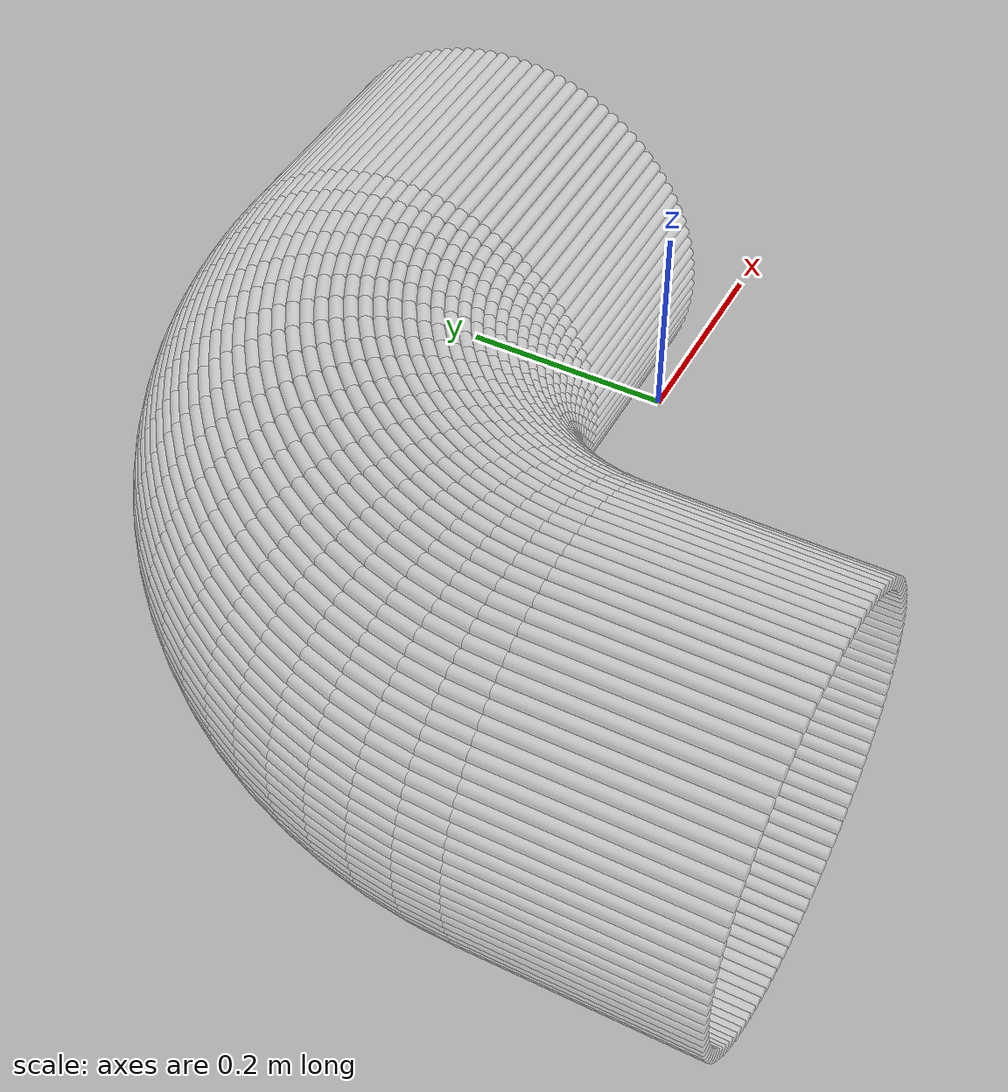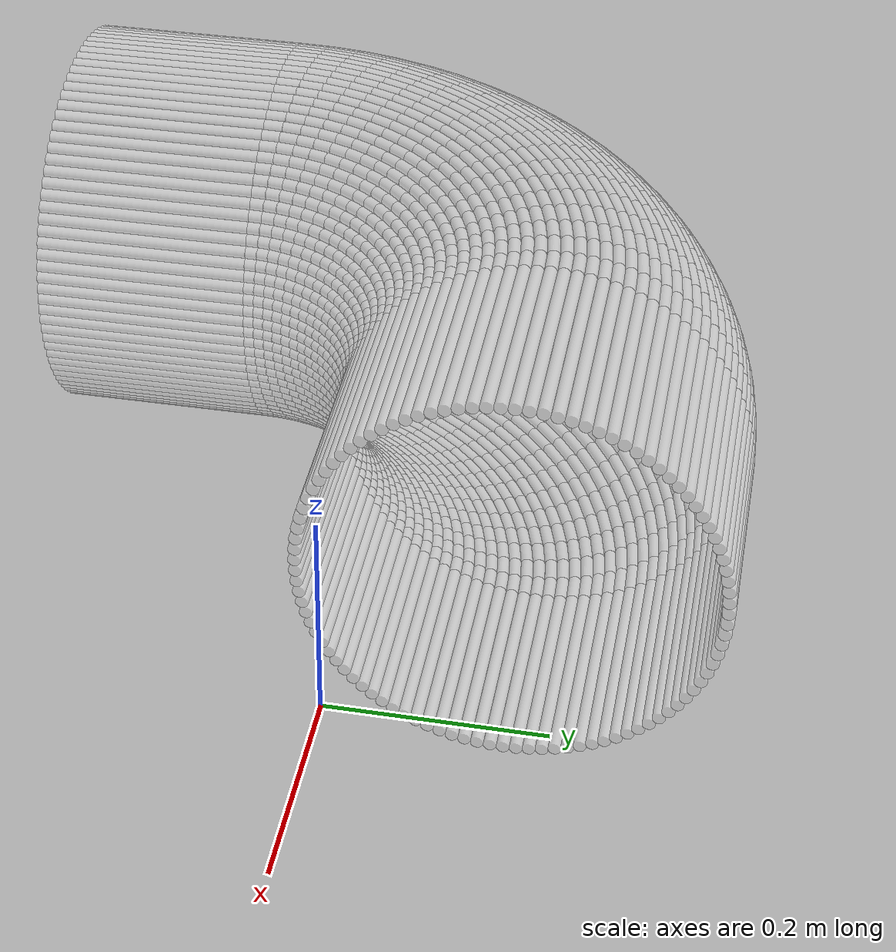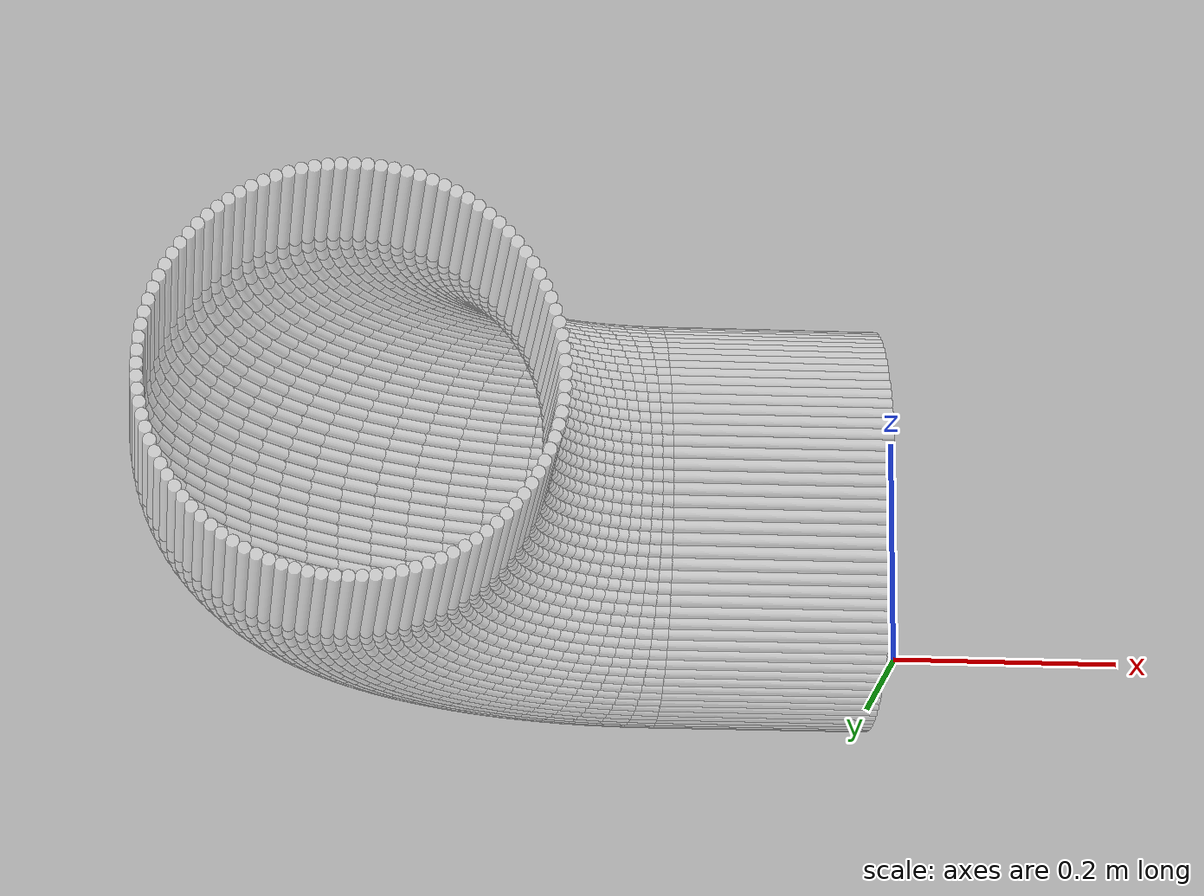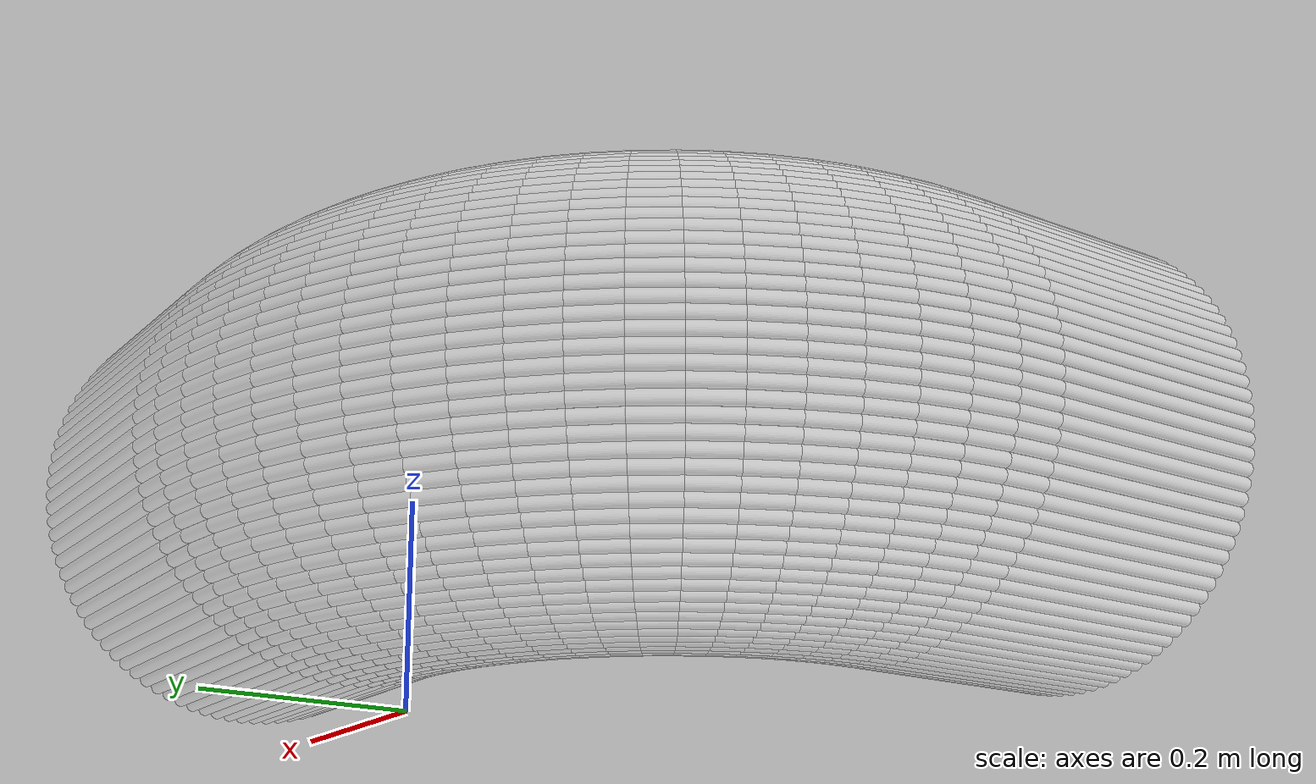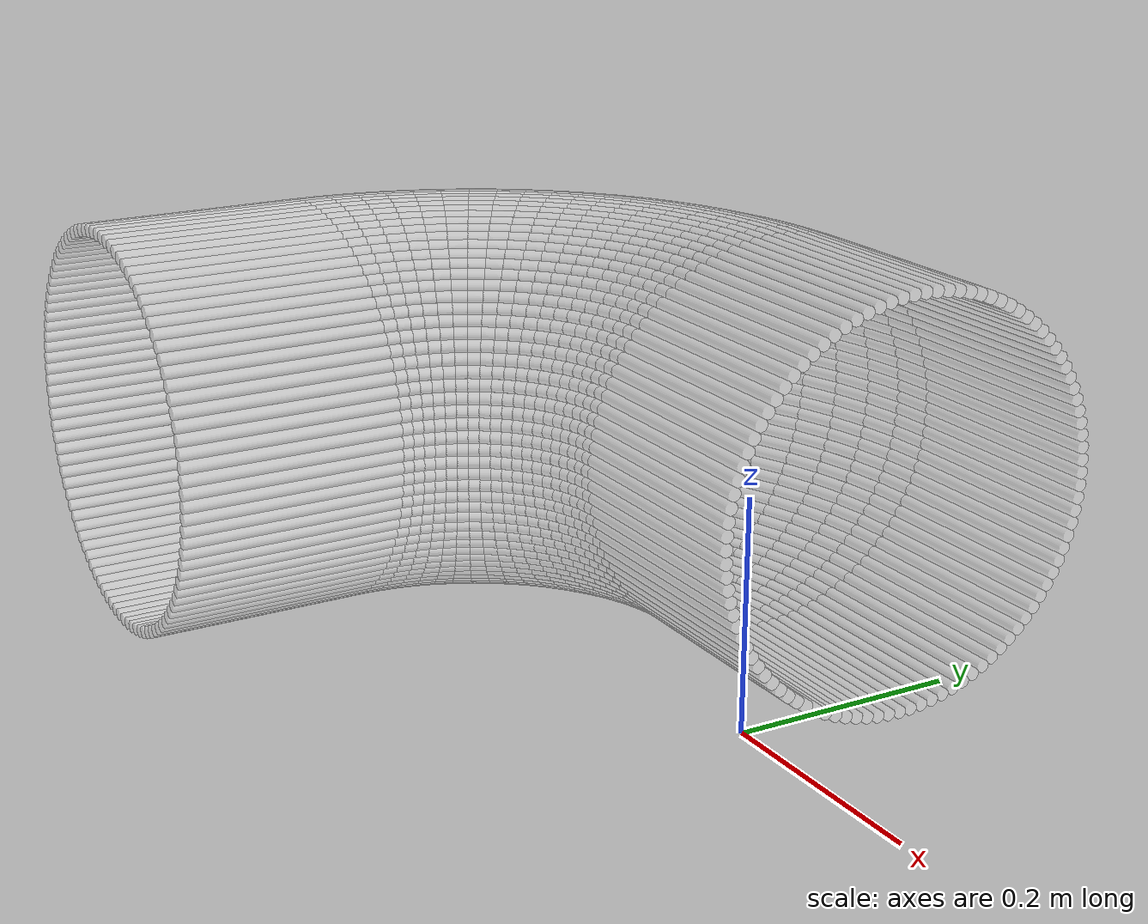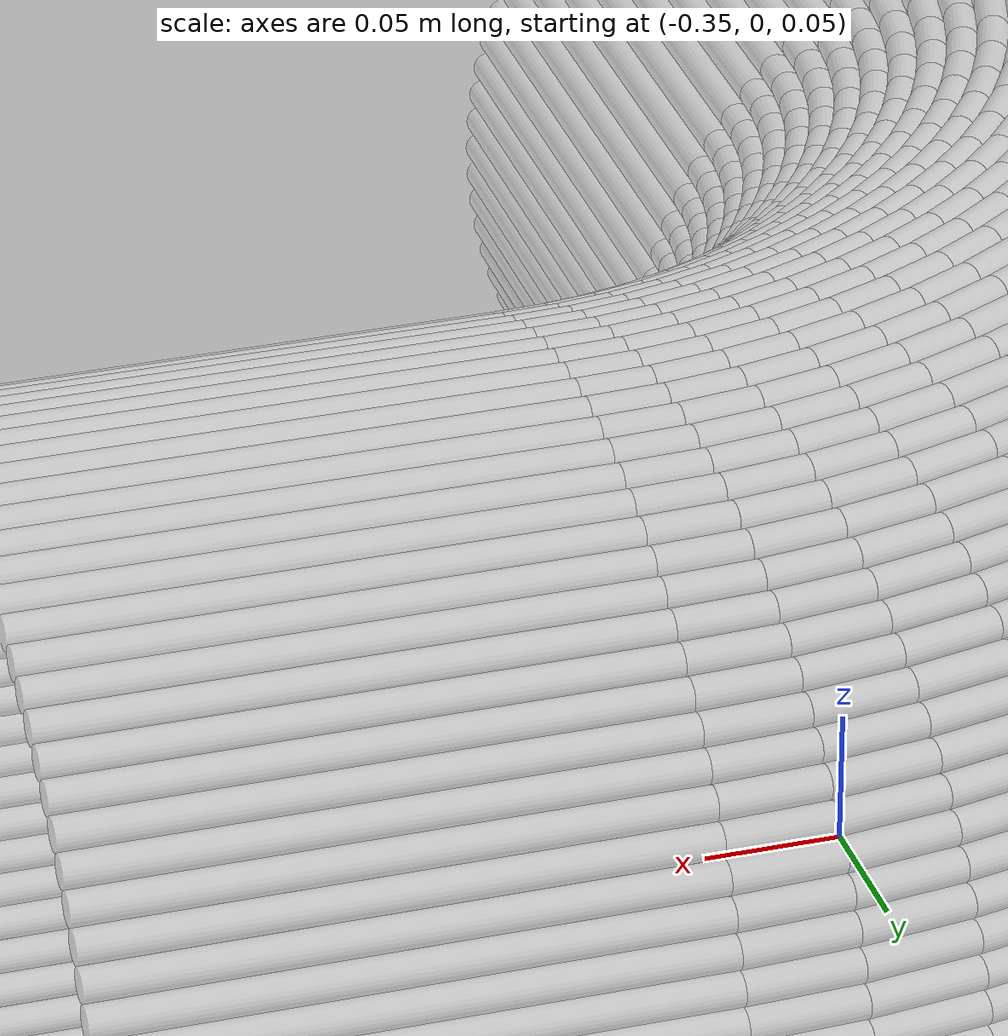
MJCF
<?xml version="1.0" encoding="utf-8"?>
<mujoco>
   <worldbody>
   <body pos="-0.2 -0.14 -0.02" euler="0 0 90">
      <geom euler=" 0 10 0 " fromto="0.48 -0.2 0.18 0.48 0 0.18" rgba="1 1 1 0.35"
            size="0.0056539"
            type="cylinder"/>
      <geom euler=" 0 20 0 " fromto="0.47964 -0.2 0.1913 0.47964 0 0.1913"
            rgba="1 1 1 0.35"
            size="0.0056539"
            type="cylinder"/>
      <geom euler=" 0 30 0 " fromto="0.47858 -0.2 0.20256 0.47858 0 0.20256"
            rgba="1 1 1 0.35"
            size="0.0056539"
            type="cylinder"/>
      <geom euler=" 0 40 0 " fromto="0.47681 -0.2 0.21373 0.47681 0 0.21373"
            rgba="1 1 1 0.35"
            size="0.0056539"
            type="cylinder"/>
      <geom euler=" 0 50 0 " fromto="0.47434 -0.2 0.22476 0.47434 0 0.22476"
            rgba="1 1 1 0.35"
            size="0.0056539"
            type="cylinder"/>
      <geom euler=" 0 60 0 " fromto="0.47119 -0.2 0.23562 0.47119 0 0.23562"
            rgba="1 1 1 0.35"
            size="0.0056539"
            type="cylinder"/>
      <geom euler=" 0 70 0 " fromto="0.46736 -0.2 0.24626 0.46736 0 0.24626"
            rgba="1 1 1 0.35"
            size="0.0056539"
            type="cylinder"/>
      <geom euler=" 0 80 0 " fromto="0.46287 -0.2 0.25664 0.46287 0 0.25664"
            rgba="1 1 1 0.35"
            size="0.0056539"
            type="cylinder"/>
      <geom euler=" 0 90 0 " fromto="0.45774 -0.2 0.26672 0.45774 0 0.26672"
            rgba="1 1 1 0.35"
            size="0.0056539"
            type="cylinder"/>
      <geom euler=" 0 100 0 " fromto="0.45198 -0.2 0.27645 0.45198 0 0.27645"
            rgba="1 1 1 0.35"
            size="0.0056539"
            type="cylinder"/>
      <geom euler=" 0 110 0 " fromto="0.44562 -0.2 0.2858 0.44562 0 0.2858"
            rgba="1 1 1 0.35"
            size="0.0056539"
            type="cylinder"/>
      <geom euler=" 0 120 0 " fromto="0.43869 -0.2 0.29474 0.43869 0 0.29474"
            rgba="1 1 1 0.35"
            size="0.0056539"
            type="cylinder"/>
      <geom euler=" 0 130 0 " fromto="0.43121 -0.2 0.30322 0.43121 0 0.30322"
            rgba="1 1 1 0.35"
            size="0.0056539"
            type="cylinder"/>
      <geom euler=" 0 140 0 " fromto="0.42322 -0.2 0.31121 0.42322 0 0.31121"
            rgba="1 1 1 0.35"
            size="0.0056539"
            type="cylinder"/>
      <geom euler=" 0 150 0 " fromto="0.41474 -0.2 0.31869 0.41474 0 0.31869"
            rgba="1 1 1 0.35"
            size="0.0056539"
            type="cylinder"/>
      <geom euler=" 0 160 0 " fromto="0.4058 -0.2 0.32562 0.4058 0 0.32562"
            rgba="1 1 1 0.35"
            size="0.0056539"
            type="cylinder"/>
      <geom euler=" 0 170 0 " fromto="0.39645 -0.2 0.33198 0.39645 0 0.33198"
            rgba="1 1 1 0.35"
            size="0.0056539"
            type="cylinder"/>
      <geom euler=" 0 180 0 " fromto="0.38672 -0.2 0.33774 0.38672 0 0.33774"
            rgba="1 1 1 0.35"
            size="0.0056539"
            type="cylinder"/>
      <geom euler=" 0 190 0 " fromto="0.37664 -0.2 0.34287 0.37664 0 0.34287"
            rgba="1 1 1 0.35"
            size="0.0056539"
            type="cylinder"/>
      <geom euler=" 0 200 0 " fromto="0.36626 -0.2 0.34736 0.36626 0 0.34736"
            rgba="1 1 1 0.35"
            size="0.0056539"
            type="cylinder"/>
      <geom euler=" 0 210 0 " fromto="0.35562 -0.2 0.35119 0.35562 0 0.35119"
            rgba="1 1 1 0.35"
            size="0.0056539"
            type="cylinder"/>
      <geom euler=" 0 220 0 " fromto="0.34476 -0.2 0.35434 0.34476 0 0.35434"
            rgba="1 1 1 0.35"
            size="0.0056539"
            type="cylinder"/>
      <geom euler=" 0 230 0 " fromto="0.33373 -0.2 0.35681 0.33373 0 0.35681"
            rgba="1 1 1 0.35"
            size="0.0056539"
            type="cylinder"/>
      <geom euler=" 0 240 0 " fromto="0.32256 -0.2 0.35858 0.32256 0 0.35858"
            rgba="1 1 1 0.35"
            size="0.0056539"
            type="cylinder"/>
      <geom euler=" 0 250 0 " fromto="0.3113 -0.2 0.35964 0.3113 0 0.35964"
            rgba="1 1 1 0.35"
            size="0.0056539"
            type="cylinder"/>
      <geom euler=" 0 260 0 " fromto="0.3 -0.2 0.36 0.3 0 0.36" rgba="1 1 1 0.35"
            size="0.0056539"
            type="cylinder"/>
      <geom euler=" 0 270 0 " fromto="0.2887 -0.2 0.35964 0.2887 0 0.35964"
            rgba="1 1 1 0.35"
            size="0.0056539"
            type="cylinder"/>
      <geom euler=" 0 280 0 " fromto="0.27744 -0.2 0.35858 0.27744 0 0.35858"
            rgba="1 1 1 0.35"
            size="0.0056539"
            type="cylinder"/>
      <geom euler=" 0 290 0 " fromto="0.26627 -0.2 0.35681 0.26627 0 0.35681"
            rgba="1 1 1 0.35"
            size="0.0056539"
            type="cylinder"/>
      <geom euler=" 0 300 0 " fromto="0.25524 -0.2 0.35434 0.25524 0 0.35434"
            rgba="1 1 1 0.35"
            size="0.0056539"
            type="cylinder"/>
      <geom euler=" 0 310 0 " fromto="0.24438 -0.2 0.35119 0.24438 0 0.35119"
            rgba="1 1 1 0.35"
            size="0.0056539"
            type="cylinder"/>
      <geom euler=" 0 320 0 " fromto="0.23374 -0.2 0.34736 0.23374 0 0.34736"
            rgba="1 1 1 0.35"
            size="0.0056539"
            type="cylinder"/>
      <geom euler=" 0 330 0 " fromto="0.22336 -0.2 0.34287 0.22336 0 0.34287"
            rgba="1 1 1 0.35"
            size="0.0056539"
            type="cylinder"/>
      <geom euler=" 0 340 0 " fromto="0.21328 -0.2 0.33774 0.21328 0 0.33774"
            rgba="1 1 1 0.35"
            size="0.0056539"
            type="cylinder"/>
      <geom euler=" 0 350 0 " fromto="0.20355 -0.2 0.33198 0.20355 0 0.33198"
            rgba="1 1 1 0.35"
            size="0.0056539"
            type="cylinder"/>
      <geom euler=" 0 360 0 " fromto="0.1942 -0.2 0.32562 0.1942 0 0.32562"
            rgba="1 1 1 0.35"
            size="0.0056539"
            type="cylinder"/>
      <geom euler=" 0 370 0 " fromto="0.18526 -0.2 0.31869 0.18526 0 0.31869"
            rgba="1 1 1 0.35"
            size="0.0056539"
            type="cylinder"/>
      <geom euler=" 0 380 0 " fromto="0.17678 -0.2 0.31121 0.17678 0 0.31121"
            rgba="1 1 1 0.35"
            size="0.0056539"
            type="cylinder"/>
      <geom euler=" 0 390 0 " fromto="0.16879 -0.2 0.30322 0.16879 0 0.30322"
            rgba="1 1 1 0.35"
            size="0.0056539"
            type="cylinder"/>
      <geom euler=" 0 400 0 " fromto="0.16131 -0.2 0.29474 0.16131 0 0.29474"
            rgba="1 1 1 0.35"
            size="0.0056539"
            type="cylinder"/>
      <geom euler=" 0 410 0 " fromto="0.15438 -0.2 0.2858 0.15438 0 0.2858"
            rgba="1 1 1 0.35"
            size="0.0056539"
            type="cylinder"/>
      <geom euler=" 0 420 0 " fromto="0.14802 -0.2 0.27645 0.14802 0 0.27645"
            rgba="1 1 1 0.35"
            size="0.0056539"
            type="cylinder"/>
      <geom euler=" 0 430 0 " fromto="0.14226 -0.2 0.26672 0.14226 0 0.26672"
            rgba="1 1 1 0.35"
            size="0.0056539"
            type="cylinder"/>
      <geom euler=" 0 440 0 " fromto="0.13713 -0.2 0.25664 0.13713 0 0.25664"
            rgba="1 1 1 0.35"
            size="0.0056539"
            type="cylinder"/>
      <geom euler=" 0 450 0 " fromto="0.13264 -0.2 0.24626 0.13264 0 0.24626"
            rgba="1 1 1 0.35"
            size="0.0056539"
            type="cylinder"/>
      <geom euler=" 0 460 0 " fromto="0.12881 -0.2 0.23562 0.12881 0 0.23562"
            rgba="1 1 1 0.35"
            size="0.0056539"
            type="cylinder"/>
      <geom euler=" 0 470 0 " fromto="0.12566 -0.2 0.22476 0.12566 0 0.22476"
            rgba="1 1 1 0.35"
            size="0.0056539"
            type="cylinder"/>
      <geom euler=" 0 480 0 " fromto="0.12319 -0.2 0.21373 0.12319 0 0.21373"
            rgba="1 1 1 0.35"
            size="0.0056539"
            type="cylinder"/>
      <geom euler=" 0 490 0 " fromto="0.12142 -0.2 0.20256 0.12142 0 0.20256"
            rgba="1 1 1 0.35"
            size="0.0056539"
            type="cylinder"/>
      <geom euler=" 0 500 0 " fromto="0.12036 -0.2 0.1913 0.12036 0 0.1913"
            rgba="1 1 1 0.35"
            size="0.0056539"
            type="cylinder"/>
      <geom euler=" 0 510 0 " fromto="0.12 -0.2 0.18 0.12 0 0.18" rgba="1 1 1 0.35"
            size="0.0056539"
            type="cylinder"/>
      <geom euler=" 0 520 0 " fromto="0.12036 -0.2 0.1687 0.12036 0 0.1687"
            rgba="1 1 1 0.35"
            size="0.0056539"
            type="cylinder"/>
      <geom euler=" 0 530 0 " fromto="0.12142 -0.2 0.15744 0.12142 0 0.15744"
            rgba="1 1 1 0.35"
            size="0.0056539"
            type="cylinder"/>
      <geom euler=" 0 540 0 " fromto="0.12319 -0.2 0.14627 0.12319 0 0.14627"
            rgba="1 1 1 0.35"
            size="0.0056539"
            type="cylinder"/>
      <geom euler=" 0 550 0 " fromto="0.12566 -0.2 0.13524 0.12566 0 0.13524"
            rgba="1 1 1 0.35"
            size="0.0056539"
            type="cylinder"/>
      <geom euler=" 0 560 0 " fromto="0.12881 -0.2 0.12438 0.12881 0 0.12438"
            rgba="1 1 1 0.35"
            size="0.0056539"
            type="cylinder"/>
      <geom euler=" 0 570 0 " fromto="0.13264 -0.2 0.11374 0.13264 0 0.11374"
            rgba="1 1 1 0.35"
            size="0.0056539"
            type="cylinder"/>
      <geom euler=" 0 580 0 " fromto="0.13713 -0.2 0.10336 0.13713 0 0.10336"
            rgba="1 1 1 0.35"
            size="0.0056539"
            type="cylinder"/>
      <geom euler=" 0 590 0 " fromto="0.14226 -0.2 0.093284 0.14226 0 0.093284"
            rgba="1 1 1 0.35"
            size="0.0056539"
            type="cylinder"/>
      <geom euler=" 0 600 0 " fromto="0.14802 -0.2 0.083551 0.14802 0 0.083551"
            rgba="1 1 1 0.35"
            size="0.0056539"
            type="cylinder"/>
      <geom euler=" 0 610 0 " fromto="0.15438 -0.2 0.074199 0.15438 0 0.074199"
            rgba="1 1 1 0.35"
            size="0.0056539"
            type="cylinder"/>
      <geom euler=" 0 620 0 " fromto="0.16131 -0.2 0.065264 0.16131 0 0.065264"
            rgba="1 1 1 0.35"
            size="0.0056539"
            type="cylinder"/>
      <geom euler=" 0 630 0 " fromto="0.16879 -0.2 0.056782 0.16879 0 0.056782"
            rgba="1 1 1 0.35"
            size="0.0056539"
            type="cylinder"/>
      <geom euler=" 0 640 0 " fromto="0.17678 -0.2 0.048786 0.17678 0 0.048786"
            rgba="1 1 1 0.35"
            size="0.0056539"
            type="cylinder"/>
      <geom euler=" 0 650 0 " fromto="0.18526 -0.2 0.041308 0.18526 0 0.041308"
            rgba="1 1 1 0.35"
            size="0.0056539"
            type="cylinder"/>
      <geom euler=" 0 660 0 " fromto="0.1942 -0.2 0.034377 0.1942 0 0.034377"
            rgba="1 1 1 0.35"
            size="0.0056539"
            type="cylinder"/>
      <geom euler=" 0 670 0 " fromto="0.20355 -0.2 0.028021 0.20355 0 0.028021"
            rgba="1 1 1 0.35"
            size="0.0056539"
            type="cylinder"/>
      <geom euler=" 0 680 0 " fromto="0.21328 -0.2 0.022265 0.21328 0 0.022265"
            rgba="1 1 1 0.35"
            size="0.0056539"
            type="cylinder"/>
      <geom euler=" 0 690 0 " fromto="0.22336 -0.2 0.017131 0.22336 0 0.017131"
            rgba="1 1 1 0.35"
            size="0.0056539"
            type="cylinder"/>
      <geom euler=" 0 700 0 " fromto="0.23374 -0.2 0.01264 0.23374 0 0.01264"
            rgba="1 1 1 0.35"
            size="0.0056539"
            type="cylinder"/>
      <geom euler=" 0 710 0 " fromto="0.24438 -0.2 0.0088098 0.24438 0 0.0088098"
            rgba="1 1 1 0.35"
            size="0.0056539"
            type="cylinder"/>
      <geom euler=" 0 720 0 " fromto="0.25524 -0.2 0.005655 0.25524 0 0.005655"
            rgba="1 1 1 0.35"
            size="0.0056539"
            type="cylinder"/>
      <geom euler=" 0 730 0 " fromto="0.26627 -0.2 0.0031883 0.26627 0 0.0031883"
            rgba="1 1 1 0.35"
            size="0.0056539"
            type="cylinder"/>
      <geom euler=" 0 740 0 " fromto="0.27744 -0.2 0.0014194 0.27744 0 0.0014194"
            rgba="1 1 1 0.35"
            size="0.0056539"
            type="cylinder"/>
      <geom euler=" 0 750 0 " fromto="0.2887 -0.2 0.00035519 0.2887 0 0.00035519"
            rgba="1 1 1 0.35"
            size="0.0056539"
            type="cylinder"/>
      <geom euler=" 0 760 0 " fromto="0.3 -0.2 0 0.3 0 0" rgba="1 1 1 0.35"
            size="0.0056539"
            type="cylinder"/>
      <geom euler=" 0 770 0 " fromto="0.3113 -0.2 0.00035519 0.3113 0 0.00035519"
            rgba="1 1 1 0.35"
            size="0.0056539"
            type="cylinder"/>
      <geom euler=" 0 780 0 " fromto="0.32256 -0.2 0.0014194 0.32256 0 0.0014194"
            rgba="1 1 1 0.35"
            size="0.0056539"
            type="cylinder"/>
      <geom euler=" 0 790 0 " fromto="0.33373 -0.2 0.0031883 0.33373 0 0.0031883"
            rgba="1 1 1 0.35"
            size="0.0056539"
            type="cylinder"/>
      <geom euler=" 0 800 0 " fromto="0.34476 -0.2 0.005655 0.34476 0 0.005655"
            rgba="1 1 1 0.35"
            size="0.0056539"
            type="cylinder"/>
      <geom euler=" 0 810 0 " fromto="0.35562 -0.2 0.0088098 0.35562 0 0.0088098"
            rgba="1 1 1 0.35"
            size="0.0056539"
            type="cylinder"/>
      <geom euler=" 0 820 0 " fromto="0.36626 -0.2 0.01264 0.36626 0 0.01264"
            rgba="1 1 1 0.35"
            size="0.0056539"
            type="cylinder"/>
      <geom euler=" 0 830 0 " fromto="0.37664 -0.2 0.017131 0.37664 0 0.017131"
            rgba="1 1 1 0.35"
            size="0.0056539"
            type="cylinder"/>
      <geom euler=" 0 840 0 " fromto="0.38672 -0.2 0.022265 0.38672 0 0.022265"
            rgba="1 1 1 0.35"
            size="0.0056539"
            type="cylinder"/>
      <geom euler=" 0 850 0 " fromto="0.39645 -0.2 0.028021 0.39645 0 0.028021"
            rgba="1 1 1 0.35"
            size="0.0056539"
            type="cylinder"/>
      <geom euler=" 0 860 0 " fromto="0.4058 -0.2 0.034377 0.4058 0 0.034377"
            rgba="1 1 1 0.35"
            size="0.0056539"
            type="cylinder"/>
      <geom euler=" 0 870 0 " fromto="0.41474 -0.2 0.041308 0.41474 0 0.041308"
            rgba="1 1 1 0.35"
            size="0.0056539"
            type="cylinder"/>
      <geom euler=" 0 880 0 " fromto="0.42322 -0.2 0.048786 0.42322 0 0.048786"
            rgba="1 1 1 0.35"
            size="0.0056539"
            type="cylinder"/>
      <geom euler=" 0 890 0 " fromto="0.43121 -0.2 0.056782 0.43121 0 0.056782"
            rgba="1 1 1 0.35"
            size="0.0056539"
            type="cylinder"/>
      <geom euler=" 0 900 0 " fromto="0.43869 -0.2 0.065264 0.43869 0 0.065264"
            rgba="1 1 1 0.35"
            size="0.0056539"
            type="cylinder"/>
      <geom euler=" 0 910 0 " fromto="0.44562 -0.2 0.074199 0.44562 0 0.074199"
            rgba="1 1 1 0.35"
            size="0.0056539"
            type="cylinder"/>
      <geom euler=" 0 920 0 " fromto="0.45198 -0.2 0.083551 0.45198 0 0.083551"
            rgba="1 1 1 0.35"
            size="0.0056539"
            type="cylinder"/>
      <geom euler=" 0 930 0 " fromto="0.45774 -0.2 0.093284 0.45774 0 0.093284"
            rgba="1 1 1 0.35"
            size="0.0056539"
            type="cylinder"/>
      <geom euler=" 0 940 0 " fromto="0.46287 -0.2 0.10336 0.46287 0 0.10336"
            rgba="1 1 1 0.35"
            size="0.0056539"
            type="cylinder"/>
      <geom euler=" 0 950 0 " fromto="0.46736 -0.2 0.11374 0.46736 0 0.11374"
            rgba="1 1 1 0.35"
            size="0.0056539"
            type="cylinder"/>
      <geom euler=" 0 960 0 " fromto="0.47119 -0.2 0.12438 0.47119 0 0.12438"
            rgba="1 1 1 0.35"
            size="0.0056539"
            type="cylinder"/>
      <geom euler=" 0 970 0 " fromto="0.47434 -0.2 0.13524 0.47434 0 0.13524"
            rgba="1 1 1 0.35"
            size="0.0056539"
            type="cylinder"/>
      <geom euler=" 0 980 0 " fromto="0.47681 -0.2 0.14627 0.47681 0 0.14627"
            rgba="1 1 1 0.35"
            size="0.0056539"
            type="cylinder"/>
      <geom euler=" 0 990 0 " fromto="0.47858 -0.2 0.15744 0.47858 0 0.15744"
            rgba="1 1 1 0.35"
            size="0.0056539"
            type="cylinder"/>
      <geom euler=" 0 1000 0 " fromto="0.47964 -0.2 0.1687 0.47964 0 0.1687"
            rgba="1 1 1 0.35"
            size="0.0056539"
            type="cylinder"/>
      <geom euler=" 0 10 0 " fromto="0.48 0 0.18 0.47836 0.039638 0.18" rgba="1 1 1 0.35"
            size="0.0056539"
            type="cylinder"/>
      <geom euler=" 0 20 0 " fromto="0.47964 0 0.1913 0.47801 0.039609 0.1913"
            rgba="1 1 1 0.35"
            size="0.0056539"
            type="cylinder"/>
      <geom euler=" 0 30 0 " fromto="0.47858 0 0.20256 0.47695 0.039521 0.20256"
            rgba="1 1 1 0.35"
            size="0.0056539"
            type="cylinder"/>
      <geom euler=" 0 40 0 " fromto="0.47681 0 0.21373 0.47518 0.039375 0.21373"
            rgba="1 1 1 0.35"
            size="0.0056539"
            type="cylinder"/>
      <geom euler=" 0 50 0 " fromto="0.47434 0 0.22476 0.47272 0.039171 0.22476"
            rgba="1 1 1 0.35"
            size="0.0056539"
            type="cylinder"/>
      <geom euler=" 0 60 0 " fromto="0.47119 0 0.23562 0.46958 0.038911 0.23562"
            rgba="1 1 1 0.35"
            size="0.0056539"
            type="cylinder"/>
      <geom euler=" 0 70 0 " fromto="0.46736 0 0.24626 0.46576 0.038594 0.24626"
            rgba="1 1 1 0.35"
            size="0.0056539"
            type="cylinder"/>
      <geom euler=" 0 80 0 " fromto="0.46287 0 0.25664 0.46129 0.038223 0.25664"
            rgba="1 1 1 0.35"
            size="0.0056539"
            type="cylinder"/>
      <geom euler=" 0 90 0 " fromto="0.45774 0 0.26672 0.45617 0.037799 0.26672"
            rgba="1 1 1 0.35"
            size="0.0056539"
            type="cylinder"/>
      <geom euler=" 0 100 0 " fromto="0.45198 0 0.27645 0.45044 0.037324 0.27645"
            rgba="1 1 1 0.35"
            size="0.0056539"
            type="cylinder"/>
      <geom euler=" 0 110 0 " fromto="0.44562 0 0.2858 0.4441 0.036799 0.2858"
            rgba="1 1 1 0.35"
            size="0.0056539"
            type="cylinder"/>
      <geom euler=" 0 120 0 " fromto="0.43869 0 0.29474 0.43719 0.036227 0.29474"
            rgba="1 1 1 0.35"
            size="0.0056539"
            type="cylinder"/>
      <geom euler=" 0 130 0 " fromto="0.43121 0 0.30322 0.42974 0.035609 0.30322"
            rgba="1 1 1 0.35"
            size="0.0056539"
            type="cylinder"/>
      <geom euler=" 0 140 0 " fromto="0.42322 0 0.31121 0.42177 0.034949 0.31121"
            rgba="1 1 1 0.35"
            size="0.0056539"
            type="cylinder"/>
      <geom euler=" 0 150 0 " fromto="0.41474 0 0.31869 0.41332 0.034249 0.31869"
            rgba="1 1 1 0.35"
            size="0.0056539"
            type="cylinder"/>
      <geom euler=" 0 160 0 " fromto="0.4058 0 0.32562 0.40442 0.033511 0.32562"
            rgba="1 1 1 0.35"
            size="0.0056539"
            type="cylinder"/>
      <geom euler=" 0 170 0 " fromto="0.39645 0 0.33198 0.39509 0.032738 0.33198"
            rgba="1 1 1 0.35"
            size="0.0056539"
            type="cylinder"/>
      <geom euler=" 0 180 0 " fromto="0.38672 0 0.33774 0.38539 0.031935 0.33774"
            rgba="1 1 1 0.35"
            size="0.0056539"
            type="cylinder"/>
      <geom euler=" 0 190 0 " fromto="0.37664 0 0.34287 0.37535 0.031103 0.34287"
            rgba="1 1 1 0.35"
            size="0.0056539"
            type="cylinder"/>
      <geom euler=" 0 200 0 " fromto="0.36626 0 0.34736 0.36501 0.030246 0.34736"
            rgba="1 1 1 0.35"
            size="0.0056539"
            type="cylinder"/>
      <geom euler=" 0 210 0 " fromto="0.35562 0 0.35119 0.35441 0.029367 0.35119"
            rgba="1 1 1 0.35"
            size="0.0056539"
            type="cylinder"/>
      <geom euler=" 0 220 0 " fromto="0.34476 0 0.35434 0.34359 0.02847 0.35434"
            rgba="1 1 1 0.35"
            size="0.0056539"
            type="cylinder"/>
      <geom euler=" 0 230 0 " fromto="0.33373 0 0.35681 0.33259 0.027559 0.35681"
            rgba="1 1 1 0.35"
            size="0.0056539"
            type="cylinder"/>
      <geom euler=" 0 240 0 " fromto="0.32256 0 0.35858 0.32146 0.026637 0.35858"
            rgba="1 1 1 0.35"
            size="0.0056539"
            type="cylinder"/>
      <geom euler=" 0 250 0 " fromto="0.3113 0 0.35964 0.31024 0.025707 0.35964"
            rgba="1 1 1 0.35"
            size="0.0056539"
            type="cylinder"/>
      <geom euler=" 0 260 0 " fromto="0.3 0 0.36 0.29898 0.024774 0.36" rgba="1 1 1 0.35"
            size="0.0056539"
            type="cylinder"/>
      <geom euler=" 0 270 0 " fromto="0.2887 0 0.35964 0.28771 0.02384 0.35964"
            rgba="1 1 1 0.35"
            size="0.0056539"
            type="cylinder"/>
      <geom euler=" 0 280 0 " fromto="0.27744 0 0.35858 0.27649 0.022911 0.35858"
            rgba="1 1 1 0.35"
            size="0.0056539"
            type="cylinder"/>
      <geom euler=" 0 290 0 " fromto="0.26627 0 0.35681 0.26536 0.021989 0.35681"
            rgba="1 1 1 0.35"
            size="0.0056539"
            type="cylinder"/>
      <geom euler=" 0 300 0 " fromto="0.25524 0 0.35434 0.25436 0.021077 0.35434"
            rgba="1 1 1 0.35"
            size="0.0056539"
            type="cylinder"/>
      <geom euler=" 0 310 0 " fromto="0.24438 0 0.35119 0.24354 0.02018 0.35119"
            rgba="1 1 1 0.35"
            size="0.0056539"
            type="cylinder"/>
      <geom euler=" 0 320 0 " fromto="0.23374 0 0.34736 0.23294 0.019302 0.34736"
            rgba="1 1 1 0.35"
            size="0.0056539"
            type="cylinder"/>
      <geom euler=" 0 330 0 " fromto="0.22336 0 0.34287 0.2226 0.018445 0.34287"
            rgba="1 1 1 0.35"
            size="0.0056539"
            type="cylinder"/>
      <geom euler=" 0 340 0 " fromto="0.21328 0 0.33774 0.21256 0.017613 0.33774"
            rgba="1 1 1 0.35"
            size="0.0056539"
            type="cylinder"/>
      <geom euler=" 0 350 0 " fromto="0.20355 0 0.33198 0.20286 0.016809 0.33198"
            rgba="1 1 1 0.35"
            size="0.0056539"
            type="cylinder"/>
      <geom euler=" 0 360 0 " fromto="0.1942 0 0.32562 0.19354 0.016037 0.32562"
            rgba="1 1 1 0.35"
            size="0.0056539"
            type="cylinder"/>
      <geom euler=" 0 370 0 " fromto="0.18526 0 0.31869 0.18463 0.015299 0.31869"
            rgba="1 1 1 0.35"
            size="0.0056539"
            type="cylinder"/>
      <geom euler=" 0 380 0 " fromto="0.17678 0 0.31121 0.17618 0.014599 0.31121"
            rgba="1 1 1 0.35"
            size="0.0056539"
            type="cylinder"/>
      <geom euler=" 0 390 0 " fromto="0.16879 0 0.30322 0.16821 0.013938 0.30322"
            rgba="1 1 1 0.35"
            size="0.0056539"
            type="cylinder"/>
      <geom euler=" 0 400 0 " fromto="0.16131 0 0.29474 0.16076 0.013321 0.29474"
            rgba="1 1 1 0.35"
            size="0.0056539"
            type="cylinder"/>
      <geom euler=" 0 410 0 " fromto="0.15438 0 0.2858 0.15385 0.012748 0.2858"
            rgba="1 1 1 0.35"
            size="0.0056539"
            type="cylinder"/>
      <geom euler=" 0 420 0 " fromto="0.14802 0 0.27645 0.14752 0.012223 0.27645"
            rgba="1 1 1 0.35"
            size="0.0056539"
            type="cylinder"/>
      <geom euler=" 0 430 0 " fromto="0.14226 0 0.26672 0.14178 0.011748 0.26672"
            rgba="1 1 1 0.35"
            size="0.0056539"
            type="cylinder"/>
      <geom euler=" 0 440 0 " fromto="0.13713 0 0.25664 0.13666 0.011324 0.25664"
            rgba="1 1 1 0.35"
            size="0.0056539"
            type="cylinder"/>
      <geom euler=" 0 450 0 " fromto="0.13264 0 0.24626 0.13219 0.010953 0.24626"
            rgba="1 1 1 0.35"
            size="0.0056539"
            type="cylinder"/>
      <geom euler=" 0 460 0 " fromto="0.12881 0 0.23562 0.12837 0.010637 0.23562"
            rgba="1 1 1 0.35"
            size="0.0056539"
            type="cylinder"/>
      <geom euler=" 0 470 0 " fromto="0.12566 0 0.22476 0.12523 0.010377 0.22476"
            rgba="1 1 1 0.35"
            size="0.0056539"
            type="cylinder"/>
      <geom euler=" 0 480 0 " fromto="0.12319 0 0.21373 0.12277 0.010173 0.21373"
            rgba="1 1 1 0.35"
            size="0.0056539"
            type="cylinder"/>
      <geom euler=" 0 490 0 " fromto="0.12142 0 0.20256 0.121 0.010027 0.20256"
            rgba="1 1 1 0.35"
            size="0.0056539"
            type="cylinder"/>
      <geom euler=" 0 500 0 " fromto="0.12036 0 0.1913 0.11994 0.0099389 0.1913"
            rgba="1 1 1 0.35"
            size="0.0056539"
            type="cylinder"/>
      <geom euler=" 0 510 0 " fromto="0.12 0 0.18 0.11959 0.0099095 0.18" rgba="1 1 1 0.35"
            size="0.0056539"
            type="cylinder"/>
      <geom euler=" 0 520 0 " fromto="0.12036 0 0.1687 0.11994 0.0099389 0.1687"
            rgba="1 1 1 0.35"
            size="0.0056539"
            type="cylinder"/>
      <geom euler=" 0 530 0 " fromto="0.12142 0 0.15744 0.121 0.010027 0.15744"
            rgba="1 1 1 0.35"
            size="0.0056539"
            type="cylinder"/>
      <geom euler=" 0 540 0 " fromto="0.12319 0 0.14627 0.12277 0.010173 0.14627"
            rgba="1 1 1 0.35"
            size="0.0056539"
            type="cylinder"/>
      <geom euler=" 0 550 0 " fromto="0.12566 0 0.13524 0.12523 0.010377 0.13524"
            rgba="1 1 1 0.35"
            size="0.0056539"
            type="cylinder"/>
      <geom euler=" 0 560 0 " fromto="0.12881 0 0.12438 0.12837 0.010637 0.12438"
            rgba="1 1 1 0.35"
            size="0.0056539"
            type="cylinder"/>
      <geom euler=" 0 570 0 " fromto="0.13264 0 0.11374 0.13219 0.010953 0.11374"
            rgba="1 1 1 0.35"
            size="0.0056539"
            type="cylinder"/>
      <geom euler=" 0 580 0 " fromto="0.13713 0 0.10336 0.13666 0.011324 0.10336"
            rgba="1 1 1 0.35"
            size="0.0056539"
            type="cylinder"/>
      <geom euler=" 0 590 0 " fromto="0.14226 0 0.093284 0.14178 0.011748 0.093284"
            rgba="1 1 1 0.35"
            size="0.0056539"
            type="cylinder"/>
      <geom euler=" 0 600 0 " fromto="0.14802 0 0.083551 0.14752 0.012223 0.083551"
            rgba="1 1 1 0.35"
            size="0.0056539"
            type="cylinder"/>
      <geom euler=" 0 610 0 " fromto="0.15438 0 0.074199 0.15385 0.012748 0.074199"
            rgba="1 1 1 0.35"
            size="0.0056539"
            type="cylinder"/>
      <geom euler=" 0 620 0 " fromto="0.16131 0 0.065264 0.16076 0.013321 0.065264"
            rgba="1 1 1 0.35"
            size="0.0056539"
            type="cylinder"/>
      <geom euler=" 0 630 0 " fromto="0.16879 0 0.056782 0.16821 0.013938 0.056782"
            rgba="1 1 1 0.35"
            size="0.0056539"
            type="cylinder"/>
      <geom euler=" 0 640 0 " fromto="0.17678 0 0.048786 0.17618 0.014599 0.048786"
            rgba="1 1 1 0.35"
            size="0.0056539"
            type="cylinder"/>
      <geom euler=" 0 650 0 " fromto="0.18526 0 0.041308 0.18463 0.015299 0.041308"
            rgba="1 1 1 0.35"
            size="0.0056539"
            type="cylinder"/>
      <geom euler=" 0 660 0 " fromto="0.1942 0 0.034377 0.19354 0.016037 0.034377"
            rgba="1 1 1 0.35"
            size="0.0056539"
            type="cylinder"/>
      <geom euler=" 0 670 0 " fromto="0.20355 0 0.028021 0.20286 0.016809 0.028021"
            rgba="1 1 1 0.35"
            size="0.0056539"
            type="cylinder"/>
      <geom euler=" 0 680 0 " fromto="0.21328 0 0.022265 0.21256 0.017613 0.022265"
            rgba="1 1 1 0.35"
            size="0.0056539"
            type="cylinder"/>
      <geom euler=" 0 690 0 " fromto="0.22336 0 0.017131 0.2226 0.018445 0.017131"
            rgba="1 1 1 0.35"
            size="0.0056539"
            type="cylinder"/>
      <geom euler=" 0 700 0 " fromto="0.23374 0 0.01264 0.23294 0.019302 0.01264"
            rgba="1 1 1 0.35"
            size="0.0056539"
            type="cylinder"/>
      <geom euler=" 0 710 0 " fromto="0.24438 0 0.0088098 0.24354 0.02018 0.0088098"
            rgba="1 1 1 0.35"
            size="0.0056539"
            type="cylinder"/>
      <geom euler=" 0 720 0 " fromto="0.25524 0 0.005655 0.25436 0.021077 0.005655"
            rgba="1 1 1 0.35"
            size="0.0056539"
            type="cylinder"/>
      <geom euler=" 0 730 0 " fromto="0.26627 0 0.0031883 0.26536 0.021989 0.0031883"
            rgba="1 1 1 0.35"
            size="0.0056539"
            type="cylinder"/>
      <geom euler=" 0 740 0 " fromto="0.27744 0 0.0014194 0.27649 0.022911 0.0014194"
            rgba="1 1 1 0.35"
            size="0.0056539"
            type="cylinder"/>
      <geom euler=" 0 750 0 " fromto="0.2887 0 0.00035519 0.28771 0.02384 0.00035519"
            rgba="1 1 1 0.35"
            size="0.0056539"
            type="cylinder"/>
      <geom euler=" 0 760 0 " fromto="0.3 0 0 0.29898 0.024774 0" rgba="1 1 1 0.35"
            size="0.0056539"
            type="cylinder"/>
      <geom euler=" 0 770 0 " fromto="0.3113 0 0.00035519 0.31024 0.025707 0.00035519"
            rgba="1 1 1 0.35"
            size="0.0056539"
            type="cylinder"/>
      <geom euler=" 0 780 0 " fromto="0.32256 0 0.0014194 0.32146 0.026637 0.0014194"
            rgba="1 1 1 0.35"
            size="0.0056539"
            type="cylinder"/>
      <geom euler=" 0 790 0 " fromto="0.33373 0 0.0031883 0.33259 0.027559 0.0031883"
            rgba="1 1 1 0.35"
            size="0.0056539"
            type="cylinder"/>
      <geom euler=" 0 800 0 " fromto="0.34476 0 0.005655 0.34359 0.02847 0.005655"
            rgba="1 1 1 0.35"
            size="0.0056539"
            type="cylinder"/>
      <geom euler=" 0 810 0 " fromto="0.35562 0 0.0088098 0.35441 0.029367 0.0088098"
            rgba="1 1 1 0.35"
            size="0.0056539"
            type="cylinder"/>
      <geom euler=" 0 820 0 " fromto="0.36626 0 0.01264 0.36501 0.030246 0.01264"
            rgba="1 1 1 0.35"
            size="0.0056539"
            type="cylinder"/>
      <geom euler=" 0 830 0 " fromto="0.37664 0 0.017131 0.37535 0.031103 0.017131"
            rgba="1 1 1 0.35"
            size="0.0056539"
            type="cylinder"/>
      <geom euler=" 0 840 0 " fromto="0.38672 0 0.022265 0.38539 0.031935 0.022265"
            rgba="1 1 1 0.35"
            size="0.0056539"
            type="cylinder"/>
      <geom euler=" 0 850 0 " fromto="0.39645 0 0.028021 0.39509 0.032738 0.028021"
            rgba="1 1 1 0.35"
            size="0.0056539"
            type="cylinder"/>
      <geom euler=" 0 860 0 " fromto="0.4058 0 0.034377 0.40442 0.033511 0.034377"
            rgba="1 1 1 0.35"
            size="0.0056539"
            type="cylinder"/>
      <geom euler=" 0 870 0 " fromto="0.41474 0 0.041308 0.41332 0.034249 0.041308"
            rgba="1 1 1 0.35"
            size="0.0056539"
            type="cylinder"/>
      <geom euler=" 0 880 0 " fromto="0.42322 0 0.048786 0.42177 0.034949 0.048786"
            rgba="1 1 1 0.35"
            size="0.0056539"
            type="cylinder"/>
      <geom euler=" 0 890 0 " fromto="0.43121 0 0.056782 0.42974 0.035609 0.056782"
            rgba="1 1 1 0.35"
            size="0.0056539"
            type="cylinder"/>
      <geom euler=" 0 900 0 " fromto="0.43869 0 0.065264 0.43719 0.036227 0.065264"
            rgba="1 1 1 0.35"
            size="0.0056539"
            type="cylinder"/>
      <geom euler=" 0 910 0 " fromto="0.44562 0 0.074199 0.4441 0.036799 0.074199"
            rgba="1 1 1 0.35"
            size="0.0056539"
            type="cylinder"/>
      <geom euler=" 0 920 0 " fromto="0.45198 0 0.083551 0.45044 0.037324 0.083551"
            rgba="1 1 1 0.35"
            size="0.0056539"
            type="cylinder"/>
      <geom euler=" 0 930 0 " fromto="0.45774 0 0.093284 0.45617 0.037799 0.093284"
            rgba="1 1 1 0.35"
            size="0.0056539"
            type="cylinder"/>
      <geom euler=" 0 940 0 " fromto="0.46287 0 0.10336 0.46129 0.038223 0.10336"
            rgba="1 1 1 0.35"
            size="0.0056539"
            type="cylinder"/>
      <geom euler=" 0 950 0 " fromto="0.46736 0 0.11374 0.46576 0.038594 0.11374"
            rgba="1 1 1 0.35"
            size="0.0056539"
            type="cylinder"/>
      <geom euler=" 0 960 0 " fromto="0.47119 0 0.12438 0.46958 0.038911 0.12438"
            rgba="1 1 1 0.35"
            size="0.0056539"
            type="cylinder"/>
      <geom euler=" 0 970 0 " fromto="0.47434 0 0.13524 0.47272 0.039171 0.13524"
            rgba="1 1 1 0.35"
            size="0.0056539"
            type="cylinder"/>
      <geom euler=" 0 980 0 " fromto="0.47681 0 0.14627 0.47518 0.039375 0.14627"
            rgba="1 1 1 0.35"
            size="0.0056539"
            type="cylinder"/>
      <geom euler=" 0 990 0 " fromto="0.47858 0 0.15744 0.47695 0.039521 0.15744"
            rgba="1 1 1 0.35"
            size="0.0056539"
            type="cylinder"/>
      <geom euler=" 0 1000 0 " fromto="0.47964 0 0.1687 0.47801 0.039609 0.1687"
            rgba="1 1 1 0.35"
            size="0.0056539"
            type="cylinder"/>
      <geom euler=" 0 10 0 " fromto="0.47836 0.039638 0.18 0.47345 0.079005 0.18"
            rgba="1 1 1 0.35"
            size="0.0056539"
            type="cylinder"/>
      <geom euler=" 0 20 0 " fromto="0.47801 0.039609 0.1913 0.4731 0.078947 0.1913"
            rgba="1 1 1 0.35"
            size="0.0056539"
            type="cylinder"/>
      <geom euler=" 0 30 0 " fromto="0.47695 0.039521 0.20256 0.47205 0.078772 0.20256"
            rgba="1 1 1 0.35"
            size="0.0056539"
            type="cylinder"/>
      <geom euler=" 0 40 0 " fromto="0.47518 0.039375 0.21373 0.47031 0.078481 0.21373"
            rgba="1 1 1 0.35"
            size="0.0056539"
            type="cylinder"/>
      <geom euler=" 0 50 0 " fromto="0.47272 0.039171 0.22476 0.46788 0.078075 0.22476"
            rgba="1 1 1 0.35"
            size="0.0056539"
            type="cylinder"/>
      <geom euler=" 0 60 0 " fromto="0.46958 0.038911 0.23562 0.46476 0.077555 0.23562"
            rgba="1 1 1 0.35"
            size="0.0056539"
            type="cylinder"/>
      <geom euler=" 0 70 0 " fromto="0.46576 0.038594 0.24626 0.46099 0.076925 0.24626"
            rgba="1 1 1 0.35"
            size="0.0056539"
            type="cylinder"/>
      <geom euler=" 0 80 0 " fromto="0.46129 0.038223 0.25664 0.45656 0.076186 0.25664"
            rgba="1 1 1 0.35"
            size="0.0056539"
            type="cylinder"/>
      <geom euler=" 0 90 0 " fromto="0.45617 0.037799 0.26672 0.45149 0.075341 0.26672"
            rgba="1 1 1 0.35"
            size="0.0056539"
            type="cylinder"/>
      <geom euler=" 0 100 0 " fromto="0.45044 0.037324 0.27645 0.44581 0.074393 0.27645"
            rgba="1 1 1 0.35"
            size="0.0056539"
            type="cylinder"/>
      <geom euler=" 0 110 0 " fromto="0.4441 0.036799 0.2858 0.43955 0.073347 0.2858"
            rgba="1 1 1 0.35"
            size="0.0056539"
            type="cylinder"/>
      <geom euler=" 0 120 0 " fromto="0.43719 0.036227 0.29474 0.43271 0.072206 0.29474"
            rgba="1 1 1 0.35"
            size="0.0056539"
            type="cylinder"/>
      <geom euler=" 0 130 0 " fromto="0.42974 0.035609 0.30322 0.42533 0.070976 0.30322"
            rgba="1 1 1 0.35"
            size="0.0056539"
            type="cylinder"/>
      <geom euler=" 0 140 0 " fromto="0.42177 0.034949 0.31121 0.41745 0.069659 0.31121"
            rgba="1 1 1 0.35"
            size="0.0056539"
            type="cylinder"/>
      <geom euler=" 0 150 0 " fromto="0.41332 0.034249 0.31869 0.40908 0.068263 0.31869"
            rgba="1 1 1 0.35"
            size="0.0056539"
            type="cylinder"/>
      <geom euler=" 0 160 0 " fromto="0.40442 0.033511 0.32562 0.40027 0.066793 0.32562"
            rgba="1 1 1 0.35"
            size="0.0056539"
            type="cylinder"/>
      <geom euler=" 0 170 0 " fromto="0.39509 0.032738 0.33198 0.39104 0.065253 0.33198"
            rgba="1 1 1 0.35"
            size="0.0056539"
            type="cylinder"/>
      <geom euler=" 0 180 0 " fromto="0.38539 0.031935 0.33774 0.38144 0.063651 0.33774"
            rgba="1 1 1 0.35"
            size="0.0056539"
            type="cylinder"/>
      <geom euler=" 0 190 0 " fromto="0.37535 0.031103 0.34287 0.3715 0.061993 0.34287"
            rgba="1 1 1 0.35"
            size="0.0056539"
            type="cylinder"/>
      <geom euler=" 0 200 0 " fromto="0.36501 0.030246 0.34736 0.36127 0.060285 0.34736"
            rgba="1 1 1 0.35"
            size="0.0056539"
            type="cylinder"/>
      <geom euler=" 0 210 0 " fromto="0.35441 0.029367 0.35119 0.35077 0.058534 0.35119"
            rgba="1 1 1 0.35"
            size="0.0056539"
            type="cylinder"/>
      <geom euler=" 0 220 0 " fromto="0.34359 0.02847 0.35434 0.34006 0.056746 0.35434"
            rgba="1 1 1 0.35"
            size="0.0056539"
            type="cylinder"/>
      <geom euler=" 0 230 0 " fromto="0.33259 0.027559 0.35681 0.32918 0.05493 0.35681"
            rgba="1 1 1 0.35"
            size="0.0056539"
            type="cylinder"/>
      <geom euler=" 0 240 0 " fromto="0.32146 0.026637 0.35858 0.31816 0.053092 0.35858"
            rgba="1 1 1 0.35"
            size="0.0056539"
            type="cylinder"/>
      <geom euler=" 0 250 0 " fromto="0.31024 0.025707 0.35964 0.30706 0.051239 0.35964"
            rgba="1 1 1 0.35"
            size="0.0056539"
            type="cylinder"/>
      <geom euler=" 0 260 0 " fromto="0.29898 0.024774 0.36 0.29591 0.049378 0.36"
            rgba="1 1 1 0.35"
            size="0.0056539"
            type="cylinder"/>
      <geom euler=" 0 270 0 " fromto="0.28771 0.02384 0.35964 0.28476 0.047518 0.35964"
            rgba="1 1 1 0.35"
            size="0.0056539"
            type="cylinder"/>
      <geom euler=" 0 280 0 " fromto="0.27649 0.022911 0.35858 0.27366 0.045665 0.35858"
            rgba="1 1 1 0.35"
            size="0.0056539"
            type="cylinder"/>
      <geom euler=" 0 290 0 " fromto="0.26536 0.021989 0.35681 0.26264 0.043827 0.35681"
            rgba="1 1 1 0.35"
            size="0.0056539"
            type="cylinder"/>
      <geom euler=" 0 300 0 " fromto="0.25436 0.021077 0.35434 0.25175 0.04201 0.35434"
            rgba="1 1 1 0.35"
            size="0.0056539"
            type="cylinder"/>
      <geom euler=" 0 310 0 " fromto="0.24354 0.02018 0.35119 0.24104 0.040223 0.35119"
            rgba="1 1 1 0.35"
            size="0.0056539"
            type="cylinder"/>
      <geom euler=" 0 320 0 " fromto="0.23294 0.019302 0.34736 0.23055 0.038472 0.34736"
            rgba="1 1 1 0.35"
            size="0.0056539"
            type="cylinder"/>
      <geom euler=" 0 330 0 " fromto="0.2226 0.018445 0.34287 0.22031 0.036764 0.34287"
            rgba="1 1 1 0.35"
            size="0.0056539"
            type="cylinder"/>
      <geom euler=" 0 340 0 " fromto="0.21256 0.017613 0.33774 0.21038 0.035105 0.33774"
            rgba="1 1 1 0.35"
            size="0.0056539"
            type="cylinder"/>
      <geom euler=" 0 350 0 " fromto="0.20286 0.016809 0.33198 0.20078 0.033503 0.33198"
            rgba="1 1 1 0.35"
            size="0.0056539"
            type="cylinder"/>
      <geom euler=" 0 360 0 " fromto="0.19354 0.016037 0.32562 0.19155 0.031964 0.32562"
            rgba="1 1 1 0.35"
            size="0.0056539"
            type="cylinder"/>
      <geom euler=" 0 370 0 " fromto="0.18463 0.015299 0.31869 0.18274 0.030493 0.31869"
            rgba="1 1 1 0.35"
            size="0.0056539"
            type="cylinder"/>
      <geom euler=" 0 380 0 " fromto="0.17618 0.014599 0.31121 0.17437 0.029097 0.31121"
            rgba="1 1 1 0.35"
            size="0.0056539"
            type="cylinder"/>
      <geom euler=" 0 390 0 " fromto="0.16821 0.013938 0.30322 0.16648 0.027781 0.30322"
            rgba="1 1 1 0.35"
            size="0.0056539"
            type="cylinder"/>
      <geom euler=" 0 400 0 " fromto="0.16076 0.013321 0.29474 0.15911 0.02655 0.29474"
            rgba="1 1 1 0.35"
            size="0.0056539"
            type="cylinder"/>
      <geom euler=" 0 410 0 " fromto="0.15385 0.012748 0.2858 0.15227 0.02541 0.2858"
            rgba="1 1 1 0.35"
            size="0.0056539"
            type="cylinder"/>
      <geom euler=" 0 420 0 " fromto="0.14752 0.012223 0.27645 0.146 0.024363 0.27645"
            rgba="1 1 1 0.35"
            size="0.0056539"
            type="cylinder"/>
      <geom euler=" 0 430 0 " fromto="0.14178 0.011748 0.26672 0.14032 0.023416 0.26672"
            rgba="1 1 1 0.35"
            size="0.0056539"
            type="cylinder"/>
      <geom euler=" 0 440 0 " fromto="0.13666 0.011324 0.25664 0.13526 0.022571 0.25664"
            rgba="1 1 1 0.35"
            size="0.0056539"
            type="cylinder"/>
      <geom euler=" 0 450 0 " fromto="0.13219 0.010953 0.24626 0.13083 0.021832 0.24626"
            rgba="1 1 1 0.35"
            size="0.0056539"
            type="cylinder"/>
      <geom euler=" 0 460 0 " fromto="0.12837 0.010637 0.23562 0.12705 0.021201 0.23562"
            rgba="1 1 1 0.35"
            size="0.0056539"
            type="cylinder"/>
      <geom euler=" 0 470 0 " fromto="0.12523 0.010377 0.22476 0.12394 0.020682 0.22476"
            rgba="1 1 1 0.35"
            size="0.0056539"
            type="cylinder"/>
      <geom euler=" 0 480 0 " fromto="0.12277 0.010173 0.21373 0.12151 0.020276 0.21373"
            rgba="1 1 1 0.35"
            size="0.0056539"
            type="cylinder"/>
      <geom euler=" 0 490 0 " fromto="0.121 0.010027 0.20256 0.11976 0.019985 0.20256"
            rgba="1 1 1 0.35"
            size="0.0056539"
            type="cylinder"/>
      <geom euler=" 0 500 0 " fromto="0.11994 0.0099389 0.1913 0.11871 0.01981 0.1913"
            rgba="1 1 1 0.35"
            size="0.0056539"
            type="cylinder"/>
      <geom euler=" 0 510 0 " fromto="0.11959 0.0099095 0.18 0.11836 0.019751 0.18"
            rgba="1 1 1 0.35"
            size="0.0056539"
            type="cylinder"/>
      <geom euler=" 0 520 0 " fromto="0.11994 0.0099389 0.1687 0.11871 0.01981 0.1687"
            rgba="1 1 1 0.35"
            size="0.0056539"
            type="cylinder"/>
      <geom euler=" 0 530 0 " fromto="0.121 0.010027 0.15744 0.11976 0.019985 0.15744"
            rgba="1 1 1 0.35"
            size="0.0056539"
            type="cylinder"/>
      <geom euler=" 0 540 0 " fromto="0.12277 0.010173 0.14627 0.12151 0.020276 0.14627"
            rgba="1 1 1 0.35"
            size="0.0056539"
            type="cylinder"/>
      <geom euler=" 0 550 0 " fromto="0.12523 0.010377 0.13524 0.12394 0.020682 0.13524"
            rgba="1 1 1 0.35"
            size="0.0056539"
            type="cylinder"/>
      <geom euler=" 0 560 0 " fromto="0.12837 0.010637 0.12438 0.12705 0.021201 0.12438"
            rgba="1 1 1 0.35"
            size="0.0056539"
            type="cylinder"/>
      <geom euler=" 0 570 0 " fromto="0.13219 0.010953 0.11374 0.13083 0.021832 0.11374"
            rgba="1 1 1 0.35"
            size="0.0056539"
            type="cylinder"/>
      <geom euler=" 0 580 0 " fromto="0.13666 0.011324 0.10336 0.13526 0.022571 0.10336"
            rgba="1 1 1 0.35"
            size="0.0056539"
            type="cylinder"/>
      <geom euler=" 0 590 0 " fromto="0.14178 0.011748 0.093284 0.14032 0.023416 0.093284"
            rgba="1 1 1 0.35"
            size="0.0056539"
            type="cylinder"/>
      <geom euler=" 0 600 0 " fromto="0.14752 0.012223 0.083551 0.146 0.024363 0.083551"
            rgba="1 1 1 0.35"
            size="0.0056539"
            type="cylinder"/>
      <geom euler=" 0 610 0 " fromto="0.15385 0.012748 0.074199 0.15227 0.02541 0.074199"
            rgba="1 1 1 0.35"
            size="0.0056539"
            type="cylinder"/>
      <geom euler=" 0 620 0 " fromto="0.16076 0.013321 0.065264 0.15911 0.02655 0.065264"
            rgba="1 1 1 0.35"
            size="0.0056539"
            type="cylinder"/>
      <geom euler=" 0 630 0 " fromto="0.16821 0.013938 0.056782 0.16648 0.027781 0.056782"
            rgba="1 1 1 0.35"
            size="0.0056539"
            type="cylinder"/>
      <geom euler=" 0 640 0 " fromto="0.17618 0.014599 0.048786 0.17437 0.029097 0.048786"
            rgba="1 1 1 0.35"
            size="0.0056539"
            type="cylinder"/>
      <geom euler=" 0 650 0 " fromto="0.18463 0.015299 0.041308 0.18274 0.030493 0.041308"
            rgba="1 1 1 0.35"
            size="0.0056539"
            type="cylinder"/>
      <geom euler=" 0 660 0 " fromto="0.19354 0.016037 0.034377 0.19155 0.031964 0.034377"
            rgba="1 1 1 0.35"
            size="0.0056539"
            type="cylinder"/>
      <geom euler=" 0 670 0 " fromto="0.20286 0.016809 0.028021 0.20078 0.033503 0.028021"
            rgba="1 1 1 0.35"
            size="0.0056539"
            type="cylinder"/>
      <geom euler=" 0 680 0 " fromto="0.21256 0.017613 0.022265 0.21038 0.035105 0.022265"
            rgba="1 1 1 0.35"
            size="0.0056539"
            type="cylinder"/>
      <geom euler=" 0 690 0 " fromto="0.2226 0.018445 0.017131 0.22031 0.036764 0.017131"
            rgba="1 1 1 0.35"
            size="0.0056539"
            type="cylinder"/>
      <geom euler=" 0 700 0 " fromto="0.23294 0.019302 0.01264 0.23055 0.038472 0.01264"
            rgba="1 1 1 0.35"
            size="0.0056539"
            type="cylinder"/>
      <geom euler=" 0 710 0 " fromto="0.24354 0.02018 0.0088098 0.24104 0.040223 0.0088098"
            rgba="1 1 1 0.35"
            size="0.0056539"
            type="cylinder"/>
      <geom euler=" 0 720 0 " fromto="0.25436 0.021077 0.005655 0.25175 0.04201 0.005655"
            rgba="1 1 1 0.35"
            size="0.0056539"
            type="cylinder"/>
      <geom euler=" 0 730 0 "
            fromto="0.26536 0.021989 0.0031883 0.26264 0.043827 0.0031883"
            rgba="1 1 1 0.35"
            size="0.0056539"
            type="cylinder"/>
      <geom euler=" 0 740 0 "
            fromto="0.27649 0.022911 0.0014194 0.27366 0.045665 0.0014194"
            rgba="1 1 1 0.35"
            size="0.0056539"
            type="cylinder"/>
      <geom euler=" 0 750 0 "
            fromto="0.28771 0.02384 0.00035519 0.28476 0.047518 0.00035519"
            rgba="1 1 1 0.35"
            size="0.0056539"
            type="cylinder"/>
      <geom euler=" 0 760 0 " fromto="0.29898 0.024774 0 0.29591 0.049378 0"
            rgba="1 1 1 0.35"
            size="0.0056539"
            type="cylinder"/>
      <geom euler=" 0 770 0 "
            fromto="0.31024 0.025707 0.00035519 0.30706 0.051239 0.00035519"
            rgba="1 1 1 0.35"
            size="0.0056539"
            type="cylinder"/>
      <geom euler=" 0 780 0 "
            fromto="0.32146 0.026637 0.0014194 0.31816 0.053092 0.0014194"
            rgba="1 1 1 0.35"
            size="0.0056539"
            type="cylinder"/>
      <geom euler=" 0 790 0 " fromto="0.33259 0.027559 0.0031883 0.32918 0.05493 0.0031883"
            rgba="1 1 1 0.35"
            size="0.0056539"
            type="cylinder"/>
      <geom euler=" 0 800 0 " fromto="0.34359 0.02847 0.005655 0.34006 0.056746 0.005655"
            rgba="1 1 1 0.35"
            size="0.0056539"
            type="cylinder"/>
      <geom euler=" 0 810 0 "
            fromto="0.35441 0.029367 0.0088098 0.35077 0.058534 0.0088098"
            rgba="1 1 1 0.35"
            size="0.0056539"
            type="cylinder"/>
      <geom euler=" 0 820 0 " fromto="0.36501 0.030246 0.01264 0.36127 0.060285 0.01264"
            rgba="1 1 1 0.35"
            size="0.0056539"
            type="cylinder"/>
      <geom euler=" 0 830 0 " fromto="0.37535 0.031103 0.017131 0.3715 0.061993 0.017131"
            rgba="1 1 1 0.35"
            size="0.0056539"
            type="cylinder"/>
      <geom euler=" 0 840 0 " fromto="0.38539 0.031935 0.022265 0.38144 0.063651 0.022265"
            rgba="1 1 1 0.35"
            size="0.0056539"
            type="cylinder"/>
      <geom euler=" 0 850 0 " fromto="0.39509 0.032738 0.028021 0.39104 0.065253 0.028021"
            rgba="1 1 1 0.35"
            size="0.0056539"
            type="cylinder"/>
      <geom euler=" 0 860 0 " fromto="0.40442 0.033511 0.034377 0.40027 0.066793 0.034377"
            rgba="1 1 1 0.35"
            size="0.0056539"
            type="cylinder"/>
      <geom euler=" 0 870 0 " fromto="0.41332 0.034249 0.041308 0.40908 0.068263 0.041308"
            rgba="1 1 1 0.35"
            size="0.0056539"
            type="cylinder"/>
      <geom euler=" 0 880 0 " fromto="0.42177 0.034949 0.048786 0.41745 0.069659 0.048786"
            rgba="1 1 1 0.35"
            size="0.0056539"
            type="cylinder"/>
      <geom euler=" 0 890 0 " fromto="0.42974 0.035609 0.056782 0.42533 0.070976 0.056782"
            rgba="1 1 1 0.35"
            size="0.0056539"
            type="cylinder"/>
      <geom euler=" 0 900 0 " fromto="0.43719 0.036227 0.065264 0.43271 0.072206 0.065264"
            rgba="1 1 1 0.35"
            size="0.0056539"
            type="cylinder"/>
      <geom euler=" 0 910 0 " fromto="0.4441 0.036799 0.074199 0.43955 0.073347 0.074199"
            rgba="1 1 1 0.35"
            size="0.0056539"
            type="cylinder"/>
      <geom euler=" 0 920 0 " fromto="0.45044 0.037324 0.083551 0.44581 0.074393 0.083551"
            rgba="1 1 1 0.35"
            size="0.0056539"
            type="cylinder"/>
      <geom euler=" 0 930 0 " fromto="0.45617 0.037799 0.093284 0.45149 0.075341 0.093284"
            rgba="1 1 1 0.35"
            size="0.0056539"
            type="cylinder"/>
      <geom euler=" 0 940 0 " fromto="0.46129 0.038223 0.10336 0.45656 0.076186 0.10336"
            rgba="1 1 1 0.35"
            size="0.0056539"
            type="cylinder"/>
      <geom euler=" 0 950 0 " fromto="0.46576 0.038594 0.11374 0.46099 0.076925 0.11374"
            rgba="1 1 1 0.35"
            size="0.0056539"
            type="cylinder"/>
      <geom euler=" 0 960 0 " fromto="0.46958 0.038911 0.12438 0.46476 0.077555 0.12438"
            rgba="1 1 1 0.35"
            size="0.0056539"
            type="cylinder"/>
      <geom euler=" 0 970 0 " fromto="0.47272 0.039171 0.13524 0.46788 0.078075 0.13524"
            rgba="1 1 1 0.35"
            size="0.0056539"
            type="cylinder"/>
      <geom euler=" 0 980 0 " fromto="0.47518 0.039375 0.14627 0.47031 0.078481 0.14627"
            rgba="1 1 1 0.35"
            size="0.0056539"
            type="cylinder"/>
      <geom euler=" 0 990 0 " fromto="0.47695 0.039521 0.15744 0.47205 0.078772 0.15744"
            rgba="1 1 1 0.35"
            size="0.0056539"
            type="cylinder"/>
      <geom euler=" 0 1000 0 " fromto="0.47801 0.039609 0.1687 0.4731 0.078947 0.1687"
            rgba="1 1 1 0.35"
            size="0.0056539"
            type="cylinder"/>
      <geom euler=" 0 10 0 " fromto="0.47345 0.079005 0.18 0.46531 0.11783 0.18"
            rgba="1 1 1 0.35"
            size="0.0056539"
            type="cylinder"/>
      <geom euler=" 0 20 0 " fromto="0.4731 0.078947 0.1913 0.46497 0.11775 0.1913"
            rgba="1 1 1 0.35"
            size="0.0056539"
            type="cylinder"/>
      <geom euler=" 0 30 0 " fromto="0.47205 0.078772 0.20256 0.46394 0.11748 0.20256"
            rgba="1 1 1 0.35"
            size="0.0056539"
            type="cylinder"/>
      <geom euler=" 0 40 0 " fromto="0.47031 0.078481 0.21373 0.46222 0.11705 0.21373"
            rgba="1 1 1 0.35"
            size="0.0056539"
            type="cylinder"/>
      <geom euler=" 0 50 0 " fromto="0.46788 0.078075 0.22476 0.45983 0.11644 0.22476"
            rgba="1 1 1 0.35"
            size="0.0056539"
            type="cylinder"/>
      <geom euler=" 0 60 0 " fromto="0.46476 0.077555 0.23562 0.45677 0.11567 0.23562"
            rgba="1 1 1 0.35"
            size="0.0056539"
            type="cylinder"/>
      <geom euler=" 0 70 0 " fromto="0.46099 0.076925 0.24626 0.45306 0.11473 0.24626"
            rgba="1 1 1 0.35"
            size="0.0056539"
            type="cylinder"/>
      <geom euler=" 0 80 0 " fromto="0.45656 0.076186 0.25664 0.44871 0.11363 0.25664"
            rgba="1 1 1 0.35"
            size="0.0056539"
            type="cylinder"/>
      <geom euler=" 0 90 0 " fromto="0.45149 0.075341 0.26672 0.44373 0.11237 0.26672"
            rgba="1 1 1 0.35"
            size="0.0056539"
            type="cylinder"/>
      <geom euler=" 0 100 0 " fromto="0.44581 0.074393 0.27645 0.43815 0.11095 0.27645"
            rgba="1 1 1 0.35"
            size="0.0056539"
            type="cylinder"/>
      <geom euler=" 0 110 0 " fromto="0.43955 0.073347 0.2858 0.43199 0.10939 0.2858"
            rgba="1 1 1 0.35"
            size="0.0056539"
            type="cylinder"/>
      <geom euler=" 0 120 0 " fromto="0.43271 0.072206 0.29474 0.42527 0.10769 0.29474"
            rgba="1 1 1 0.35"
            size="0.0056539"
            type="cylinder"/>
      <geom euler=" 0 130 0 " fromto="0.42533 0.070976 0.30322 0.41802 0.10586 0.30322"
            rgba="1 1 1 0.35"
            size="0.0056539"
            type="cylinder"/>
      <geom euler=" 0 140 0 " fromto="0.41745 0.069659 0.31121 0.41027 0.10389 0.31121"
            rgba="1 1 1 0.35"
            size="0.0056539"
            type="cylinder"/>
      <geom euler=" 0 150 0 " fromto="0.40908 0.068263 0.31869 0.40205 0.10181 0.31869"
            rgba="1 1 1 0.35"
            size="0.0056539"
            type="cylinder"/>
      <geom euler=" 0 160 0 " fromto="0.40027 0.066793 0.32562 0.39338 0.099618 0.32562"
            rgba="1 1 1 0.35"
            size="0.0056539"
            type="cylinder"/>
      <geom euler=" 0 170 0 " fromto="0.39104 0.065253 0.33198 0.38432 0.097322 0.33198"
            rgba="1 1 1 0.35"
            size="0.0056539"
            type="cylinder"/>
      <geom euler=" 0 180 0 " fromto="0.38144 0.063651 0.33774 0.37488 0.094933 0.33774"
            rgba="1 1 1 0.35"
            size="0.0056539"
            type="cylinder"/>
      <geom euler=" 0 190 0 " fromto="0.3715 0.061993 0.34287 0.36512 0.09246 0.34287"
            rgba="1 1 1 0.35"
            size="0.0056539"
            type="cylinder"/>
      <geom euler=" 0 200 0 " fromto="0.36127 0.060285 0.34736 0.35505 0.089912 0.34736"
            rgba="1 1 1 0.35"
            size="0.0056539"
            type="cylinder"/>
      <geom euler=" 0 210 0 " fromto="0.35077 0.058534 0.35119 0.34474 0.0873 0.35119"
            rgba="1 1 1 0.35"
            size="0.0056539"
            type="cylinder"/>
      <geom euler=" 0 220 0 " fromto="0.34006 0.056746 0.35434 0.33421 0.084635 0.35434"
            rgba="1 1 1 0.35"
            size="0.0056539"
            type="cylinder"/>
      <geom euler=" 0 230 0 " fromto="0.32918 0.05493 0.35681 0.32352 0.081926 0.35681"
            rgba="1 1 1 0.35"
            size="0.0056539"
            type="cylinder"/>
      <geom euler=" 0 240 0 " fromto="0.31816 0.053092 0.35858 0.31269 0.079184 0.35858"
            rgba="1 1 1 0.35"
            size="0.0056539"
            type="cylinder"/>
      <geom euler=" 0 250 0 " fromto="0.30706 0.051239 0.35964 0.30178 0.07642 0.35964"
            rgba="1 1 1 0.35"
            size="0.0056539"
            type="cylinder"/>
      <geom euler=" 0 260 0 " fromto="0.29591 0.049378 0.36 0.29082 0.073646 0.36"
            rgba="1 1 1 0.35"
            size="0.0056539"
            type="cylinder"/>
      <geom euler=" 0 270 0 " fromto="0.28476 0.047518 0.35964 0.27986 0.070871 0.35964"
            rgba="1 1 1 0.35"
            size="0.0056539"
            type="cylinder"/>
      <geom euler=" 0 280 0 " fromto="0.27366 0.045665 0.35858 0.26895 0.068107 0.35858"
            rgba="1 1 1 0.35"
            size="0.0056539"
            type="cylinder"/>
      <geom euler=" 0 290 0 " fromto="0.26264 0.043827 0.35681 0.25812 0.065366 0.35681"
            rgba="1 1 1 0.35"
            size="0.0056539"
            type="cylinder"/>
      <geom euler=" 0 300 0 " fromto="0.25175 0.04201 0.35434 0.24743 0.062657 0.35434"
            rgba="1 1 1 0.35"
            size="0.0056539"
            type="cylinder"/>
      <geom euler=" 0 310 0 " fromto="0.24104 0.040223 0.35119 0.2369 0.059991 0.35119"
            rgba="1 1 1 0.35"
            size="0.0056539"
            type="cylinder"/>
      <geom euler=" 0 320 0 " fromto="0.23055 0.038472 0.34736 0.22659 0.057379 0.34736"
            rgba="1 1 1 0.35"
            size="0.0056539"
            type="cylinder"/>
      <geom euler=" 0 330 0 " fromto="0.22031 0.036764 0.34287 0.21652 0.054832 0.34287"
            rgba="1 1 1 0.35"
            size="0.0056539"
            type="cylinder"/>
      <geom euler=" 0 340 0 " fromto="0.21038 0.035105 0.33774 0.20676 0.052358 0.33774"
            rgba="1 1 1 0.35"
            size="0.0056539"
            type="cylinder"/>
      <geom euler=" 0 350 0 " fromto="0.20078 0.033503 0.33198 0.19732 0.049969 0.33198"
            rgba="1 1 1 0.35"
            size="0.0056539"
            type="cylinder"/>
      <geom euler=" 0 360 0 " fromto="0.19155 0.031964 0.32562 0.18826 0.047673 0.32562"
            rgba="1 1 1 0.35"
            size="0.0056539"
            type="cylinder"/>
      <geom euler=" 0 370 0 " fromto="0.18274 0.030493 0.31869 0.17959 0.04548 0.31869"
            rgba="1 1 1 0.35"
            size="0.0056539"
            type="cylinder"/>
      <geom euler=" 0 380 0 " fromto="0.17437 0.029097 0.31121 0.17137 0.043397 0.31121"
            rgba="1 1 1 0.35"
            size="0.0056539"
            type="cylinder"/>
      <geom euler=" 0 390 0 " fromto="0.16648 0.027781 0.30322 0.16362 0.041434 0.30322"
            rgba="1 1 1 0.35"
            size="0.0056539"
            type="cylinder"/>
      <geom euler=" 0 400 0 " fromto="0.15911 0.02655 0.29474 0.15637 0.039599 0.29474"
            rgba="1 1 1 0.35"
            size="0.0056539"
            type="cylinder"/>
      <geom euler=" 0 410 0 " fromto="0.15227 0.02541 0.2858 0.14965 0.037897 0.2858"
            rgba="1 1 1 0.35"
            size="0.0056539"
            type="cylinder"/>
      <geom euler=" 0 420 0 " fromto="0.146 0.024363 0.27645 0.14349 0.036337 0.27645"
            rgba="1 1 1 0.35"
            size="0.0056539"
            type="cylinder"/>
      <geom euler=" 0 430 0 " fromto="0.14032 0.023416 0.26672 0.13791 0.034924 0.26672"
            rgba="1 1 1 0.35"
            size="0.0056539"
            type="cylinder"/>
      <geom euler=" 0 440 0 " fromto="0.13526 0.022571 0.25664 0.13293 0.033664 0.25664"
            rgba="1 1 1 0.35"
            size="0.0056539"
            type="cylinder"/>
      <geom euler=" 0 450 0 " fromto="0.13083 0.021832 0.24626 0.12858 0.032561 0.24626"
            rgba="1 1 1 0.35"
            size="0.0056539"
            type="cylinder"/>
      <geom euler=" 0 460 0 " fromto="0.12705 0.021201 0.23562 0.12487 0.031621 0.23562"
            rgba="1 1 1 0.35"
            size="0.0056539"
            type="cylinder"/>
      <geom euler=" 0 470 0 " fromto="0.12394 0.020682 0.22476 0.12181 0.030846 0.22476"
            rgba="1 1 1 0.35"
            size="0.0056539"
            type="cylinder"/>
      <geom euler=" 0 480 0 " fromto="0.12151 0.020276 0.21373 0.11942 0.030241 0.21373"
            rgba="1 1 1 0.35"
            size="0.0056539"
            type="cylinder"/>
      <geom euler=" 0 490 0 " fromto="0.11976 0.019985 0.20256 0.1177 0.029807 0.20256"
            rgba="1 1 1 0.35"
            size="0.0056539"
            type="cylinder"/>
      <geom euler=" 0 500 0 " fromto="0.11871 0.01981 0.1913 0.11667 0.029545 0.1913"
            rgba="1 1 1 0.35"
            size="0.0056539"
            type="cylinder"/>
      <geom euler=" 0 510 0 " fromto="0.11836 0.019751 0.18 0.11633 0.029458 0.18"
            rgba="1 1 1 0.35"
            size="0.0056539"
            type="cylinder"/>
      <geom euler=" 0 520 0 " fromto="0.11871 0.01981 0.1687 0.11667 0.029545 0.1687"
            rgba="1 1 1 0.35"
            size="0.0056539"
            type="cylinder"/>
      <geom euler=" 0 530 0 " fromto="0.11976 0.019985 0.15744 0.1177 0.029807 0.15744"
            rgba="1 1 1 0.35"
            size="0.0056539"
            type="cylinder"/>
      <geom euler=" 0 540 0 " fromto="0.12151 0.020276 0.14627 0.11942 0.030241 0.14627"
            rgba="1 1 1 0.35"
            size="0.0056539"
            type="cylinder"/>
      <geom euler=" 0 550 0 " fromto="0.12394 0.020682 0.13524 0.12181 0.030846 0.13524"
            rgba="1 1 1 0.35"
            size="0.0056539"
            type="cylinder"/>
      <geom euler=" 0 560 0 " fromto="0.12705 0.021201 0.12438 0.12487 0.031621 0.12438"
            rgba="1 1 1 0.35"
            size="0.0056539"
            type="cylinder"/>
      <geom euler=" 0 570 0 " fromto="0.13083 0.021832 0.11374 0.12858 0.032561 0.11374"
            rgba="1 1 1 0.35"
            size="0.0056539"
            type="cylinder"/>
      <geom euler=" 0 580 0 " fromto="0.13526 0.022571 0.10336 0.13293 0.033664 0.10336"
            rgba="1 1 1 0.35"
            size="0.0056539"
            type="cylinder"/>
      <geom euler=" 0 590 0 " fromto="0.14032 0.023416 0.093284 0.13791 0.034924 0.093284"
            rgba="1 1 1 0.35"
            size="0.0056539"
            type="cylinder"/>
      <geom euler=" 0 600 0 " fromto="0.146 0.024363 0.083551 0.14349 0.036337 0.083551"
            rgba="1 1 1 0.35"
            size="0.0056539"
            type="cylinder"/>
      <geom euler=" 0 610 0 " fromto="0.15227 0.02541 0.074199 0.14965 0.037897 0.074199"
            rgba="1 1 1 0.35"
            size="0.0056539"
            type="cylinder"/>
      <geom euler=" 0 620 0 " fromto="0.15911 0.02655 0.065264 0.15637 0.039599 0.065264"
            rgba="1 1 1 0.35"
            size="0.0056539"
            type="cylinder"/>
      <geom euler=" 0 630 0 " fromto="0.16648 0.027781 0.056782 0.16362 0.041434 0.056782"
            rgba="1 1 1 0.35"
            size="0.0056539"
            type="cylinder"/>
      <geom euler=" 0 640 0 " fromto="0.17437 0.029097 0.048786 0.17137 0.043397 0.048786"
            rgba="1 1 1 0.35"
            size="0.0056539"
            type="cylinder"/>
      <geom euler=" 0 650 0 " fromto="0.18274 0.030493 0.041308 0.17959 0.04548 0.041308"
            rgba="1 1 1 0.35"
            size="0.0056539"
            type="cylinder"/>
      <geom euler=" 0 660 0 " fromto="0.19155 0.031964 0.034377 0.18826 0.047673 0.034377"
            rgba="1 1 1 0.35"
            size="0.0056539"
            type="cylinder"/>
      <geom euler=" 0 670 0 " fromto="0.20078 0.033503 0.028021 0.19732 0.049969 0.028021"
            rgba="1 1 1 0.35"
            size="0.0056539"
            type="cylinder"/>
      <geom euler=" 0 680 0 " fromto="0.21038 0.035105 0.022265 0.20676 0.052358 0.022265"
            rgba="1 1 1 0.35"
            size="0.0056539"
            type="cylinder"/>
      <geom euler=" 0 690 0 " fromto="0.22031 0.036764 0.017131 0.21652 0.054832 0.017131"
            rgba="1 1 1 0.35"
            size="0.0056539"
            type="cylinder"/>
      <geom euler=" 0 700 0 " fromto="0.23055 0.038472 0.01264 0.22659 0.057379 0.01264"
            rgba="1 1 1 0.35"
            size="0.0056539"
            type="cylinder"/>
      <geom euler=" 0 710 0 " fromto="0.24104 0.040223 0.0088098 0.2369 0.059991 0.0088098"
            rgba="1 1 1 0.35"
            size="0.0056539"
            type="cylinder"/>
      <geom euler=" 0 720 0 " fromto="0.25175 0.04201 0.005655 0.24743 0.062657 0.005655"
            rgba="1 1 1 0.35"
            size="0.0056539"
            type="cylinder"/>
      <geom euler=" 0 730 0 "
            fromto="0.26264 0.043827 0.0031883 0.25812 0.065366 0.0031883"
            rgba="1 1 1 0.35"
            size="0.0056539"
            type="cylinder"/>
      <geom euler=" 0 740 0 "
            fromto="0.27366 0.045665 0.0014194 0.26895 0.068107 0.0014194"
            rgba="1 1 1 0.35"
            size="0.0056539"
            type="cylinder"/>
      <geom euler=" 0 750 0 "
            fromto="0.28476 0.047518 0.00035519 0.27986 0.070871 0.00035519"
            rgba="1 1 1 0.35"
            size="0.0056539"
            type="cylinder"/>
      <geom euler=" 0 760 0 " fromto="0.29591 0.049378 0 0.29082 0.073646 0"
            rgba="1 1 1 0.35"
            size="0.0056539"
            type="cylinder"/>
      <geom euler=" 0 770 0 "
            fromto="0.30706 0.051239 0.00035519 0.30178 0.07642 0.00035519"
            rgba="1 1 1 0.35"
            size="0.0056539"
            type="cylinder"/>
      <geom euler=" 0 780 0 "
            fromto="0.31816 0.053092 0.0014194 0.31269 0.079184 0.0014194"
            rgba="1 1 1 0.35"
            size="0.0056539"
            type="cylinder"/>
      <geom euler=" 0 790 0 " fromto="0.32918 0.05493 0.0031883 0.32352 0.081926 0.0031883"
            rgba="1 1 1 0.35"
            size="0.0056539"
            type="cylinder"/>
      <geom euler=" 0 800 0 " fromto="0.34006 0.056746 0.005655 0.33421 0.084635 0.005655"
            rgba="1 1 1 0.35"
            size="0.0056539"
            type="cylinder"/>
      <geom euler=" 0 810 0 " fromto="0.35077 0.058534 0.0088098 0.34474 0.0873 0.0088098"
            rgba="1 1 1 0.35"
            size="0.0056539"
            type="cylinder"/>
      <geom euler=" 0 820 0 " fromto="0.36127 0.060285 0.01264 0.35505 0.089912 0.01264"
            rgba="1 1 1 0.35"
            size="0.0056539"
            type="cylinder"/>
      <geom euler=" 0 830 0 " fromto="0.3715 0.061993 0.017131 0.36512 0.09246 0.017131"
            rgba="1 1 1 0.35"
            size="0.0056539"
            type="cylinder"/>
      <geom euler=" 0 840 0 " fromto="0.38144 0.063651 0.022265 0.37488 0.094933 0.022265"
            rgba="1 1 1 0.35"
            size="0.0056539"
            type="cylinder"/>
      <geom euler=" 0 850 0 " fromto="0.39104 0.065253 0.028021 0.38432 0.097322 0.028021"
            rgba="1 1 1 0.35"
            size="0.0056539"
            type="cylinder"/>
      <geom euler=" 0 860 0 " fromto="0.40027 0.066793 0.034377 0.39338 0.099618 0.034377"
            rgba="1 1 1 0.35"
            size="0.0056539"
            type="cylinder"/>
      <geom euler=" 0 870 0 " fromto="0.40908 0.068263 0.041308 0.40205 0.10181 0.041308"
            rgba="1 1 1 0.35"
            size="0.0056539"
            type="cylinder"/>
      <geom euler=" 0 880 0 " fromto="0.41745 0.069659 0.048786 0.41027 0.10389 0.048786"
            rgba="1 1 1 0.35"
            size="0.0056539"
            type="cylinder"/>
      <geom euler=" 0 890 0 " fromto="0.42533 0.070976 0.056782 0.41802 0.10586 0.056782"
            rgba="1 1 1 0.35"
            size="0.0056539"
            type="cylinder"/>
      <geom euler=" 0 900 0 " fromto="0.43271 0.072206 0.065264 0.42527 0.10769 0.065264"
            rgba="1 1 1 0.35"
            size="0.0056539"
            type="cylinder"/>
      <geom euler=" 0 910 0 " fromto="0.43955 0.073347 0.074199 0.43199 0.10939 0.074199"
            rgba="1 1 1 0.35"
            size="0.0056539"
            type="cylinder"/>
      <geom euler=" 0 920 0 " fromto="0.44581 0.074393 0.083551 0.43815 0.11095 0.083551"
            rgba="1 1 1 0.35"
            size="0.0056539"
            type="cylinder"/>
      <geom euler=" 0 930 0 " fromto="0.45149 0.075341 0.093284 0.44373 0.11237 0.093284"
            rgba="1 1 1 0.35"
            size="0.0056539"
            type="cylinder"/>
      <geom euler=" 0 940 0 " fromto="0.45656 0.076186 0.10336 0.44871 0.11363 0.10336"
            rgba="1 1 1 0.35"
            size="0.0056539"
            type="cylinder"/>
      <geom euler=" 0 950 0 " fromto="0.46099 0.076925 0.11374 0.45306 0.11473 0.11374"
            rgba="1 1 1 0.35"
            size="0.0056539"
            type="cylinder"/>
      <geom euler=" 0 960 0 " fromto="0.46476 0.077555 0.12438 0.45677 0.11567 0.12438"
            rgba="1 1 1 0.35"
            size="0.0056539"
            type="cylinder"/>
      <geom euler=" 0 970 0 " fromto="0.46788 0.078075 0.13524 0.45983 0.11644 0.13524"
            rgba="1 1 1 0.35"
            size="0.0056539"
            type="cylinder"/>
      <geom euler=" 0 980 0 " fromto="0.47031 0.078481 0.14627 0.46222 0.11705 0.14627"
            rgba="1 1 1 0.35"
            size="0.0056539"
            type="cylinder"/>
      <geom euler=" 0 990 0 " fromto="0.47205 0.078772 0.15744 0.46394 0.11748 0.15744"
            rgba="1 1 1 0.35"
            size="0.0056539"
            type="cylinder"/>
      <geom euler=" 0 1000 0 " fromto="0.4731 0.078947 0.1687 0.46497 0.11775 0.1687"
            rgba="1 1 1 0.35"
            size="0.0056539"
            type="cylinder"/>
      <geom euler=" 0 10 0 " fromto="0.46531 0.11783 0.18 0.45399 0.15586 0.18"
            rgba="1 1 1 0.35"
            size="0.0056539"
            type="cylinder"/>
      <geom euler=" 0 20 0 " fromto="0.46497 0.11775 0.1913 0.45366 0.15574 0.1913"
            rgba="1 1 1 0.35"
            size="0.0056539"
            type="cylinder"/>
      <geom euler=" 0 30 0 " fromto="0.46394 0.11748 0.20256 0.45265 0.15539 0.20256"
            rgba="1 1 1 0.35"
            size="0.0056539"
            type="cylinder"/>
      <geom euler=" 0 40 0 " fromto="0.46222 0.11705 0.21373 0.45098 0.15482 0.21373"
            rgba="1 1 1 0.35"
            size="0.0056539"
            type="cylinder"/>
      <geom euler=" 0 50 0 " fromto="0.45983 0.11644 0.22476 0.44864 0.15402 0.22476"
            rgba="1 1 1 0.35"
            size="0.0056539"
            type="cylinder"/>
      <geom euler=" 0 60 0 " fromto="0.45677 0.11567 0.23562 0.44566 0.153 0.23562"
            rgba="1 1 1 0.35"
            size="0.0056539"
            type="cylinder"/>
      <geom euler=" 0 70 0 " fromto="0.45306 0.11473 0.24626 0.44204 0.15175 0.24626"
            rgba="1 1 1 0.35"
            size="0.0056539"
            type="cylinder"/>
      <geom euler=" 0 80 0 " fromto="0.44871 0.11363 0.25664 0.43779 0.15029 0.25664"
            rgba="1 1 1 0.35"
            size="0.0056539"
            type="cylinder"/>
      <geom euler=" 0 90 0 " fromto="0.44373 0.11237 0.26672 0.43293 0.14863 0.26672"
            rgba="1 1 1 0.35"
            size="0.0056539"
            type="cylinder"/>
      <geom euler=" 0 100 0 " fromto="0.43815 0.11095 0.27645 0.42749 0.14676 0.27645"
            rgba="1 1 1 0.35"
            size="0.0056539"
            type="cylinder"/>
      <geom euler=" 0 110 0 " fromto="0.43199 0.10939 0.2858 0.42148 0.14469 0.2858"
            rgba="1 1 1 0.35"
            size="0.0056539"
            type="cylinder"/>
      <geom euler=" 0 120 0 " fromto="0.42527 0.10769 0.29474 0.41492 0.14244 0.29474"
            rgba="1 1 1 0.35"
            size="0.0056539"
            type="cylinder"/>
      <geom euler=" 0 130 0 " fromto="0.41802 0.10586 0.30322 0.40785 0.14002 0.30322"
            rgba="1 1 1 0.35"
            size="0.0056539"
            type="cylinder"/>
      <geom euler=" 0 140 0 " fromto="0.41027 0.10389 0.31121 0.40029 0.13742 0.31121"
            rgba="1 1 1 0.35"
            size="0.0056539"
            type="cylinder"/>
      <geom euler=" 0 150 0 " fromto="0.40205 0.10181 0.31869 0.39226 0.13466 0.31869"
            rgba="1 1 1 0.35"
            size="0.0056539"
            type="cylinder"/>
      <geom euler=" 0 160 0 " fromto="0.39338 0.099618 0.32562 0.38381 0.13176 0.32562"
            rgba="1 1 1 0.35"
            size="0.0056539"
            type="cylinder"/>
      <geom euler=" 0 170 0 " fromto="0.38432 0.097322 0.33198 0.37497 0.12873 0.33198"
            rgba="1 1 1 0.35"
            size="0.0056539"
            type="cylinder"/>
      <geom euler=" 0 180 0 " fromto="0.37488 0.094933 0.33774 0.36576 0.12557 0.33774"
            rgba="1 1 1 0.35"
            size="0.0056539"
            type="cylinder"/>
      <geom euler=" 0 190 0 " fromto="0.36512 0.09246 0.34287 0.35623 0.12229 0.34287"
            rgba="1 1 1 0.35"
            size="0.0056539"
            type="cylinder"/>
      <geom euler=" 0 200 0 " fromto="0.35505 0.089912 0.34736 0.34642 0.11893 0.34736"
            rgba="1 1 1 0.35"
            size="0.0056539"
            type="cylinder"/>
      <geom euler=" 0 210 0 " fromto="0.34474 0.0873 0.35119 0.33635 0.11547 0.35119"
            rgba="1 1 1 0.35"
            size="0.0056539"
            type="cylinder"/>
      <geom euler=" 0 220 0 " fromto="0.33421 0.084635 0.35434 0.32608 0.11194 0.35434"
            rgba="1 1 1 0.35"
            size="0.0056539"
            type="cylinder"/>
      <geom euler=" 0 230 0 " fromto="0.32352 0.081926 0.35681 0.31565 0.10836 0.35681"
            rgba="1 1 1 0.35"
            size="0.0056539"
            type="cylinder"/>
      <geom euler=" 0 240 0 " fromto="0.31269 0.079184 0.35858 0.30508 0.10474 0.35858"
            rgba="1 1 1 0.35"
            size="0.0056539"
            type="cylinder"/>
      <geom euler=" 0 250 0 " fromto="0.30178 0.07642 0.35964 0.29444 0.10108 0.35964"
            rgba="1 1 1 0.35"
            size="0.0056539"
            type="cylinder"/>
      <geom euler=" 0 260 0 " fromto="0.29082 0.073646 0.36 0.28375 0.09741 0.36"
            rgba="1 1 1 0.35"
            size="0.0056539"
            type="cylinder"/>
      <geom euler=" 0 270 0 " fromto="0.27986 0.070871 0.35964 0.27306 0.09374 0.35964"
            rgba="1 1 1 0.35"
            size="0.0056539"
            type="cylinder"/>
      <geom euler=" 0 280 0 " fromto="0.26895 0.068107 0.35858 0.26241 0.090085 0.35858"
            rgba="1 1 1 0.35"
            size="0.0056539"
            type="cylinder"/>
      <geom euler=" 0 290 0 " fromto="0.25812 0.065366 0.35681 0.25184 0.086458 0.35681"
            rgba="1 1 1 0.35"
            size="0.0056539"
            type="cylinder"/>
      <geom euler=" 0 300 0 " fromto="0.24743 0.062657 0.35434 0.24141 0.082875 0.35434"
            rgba="1 1 1 0.35"
            size="0.0056539"
            type="cylinder"/>
      <geom euler=" 0 310 0 " fromto="0.2369 0.059991 0.35119 0.23114 0.079349 0.35119"
            rgba="1 1 1 0.35"
            size="0.0056539"
            type="cylinder"/>
      <geom euler=" 0 320 0 " fromto="0.22659 0.057379 0.34736 0.22107 0.075894 0.34736"
            rgba="1 1 1 0.35"
            size="0.0056539"
            type="cylinder"/>
      <geom euler=" 0 330 0 " fromto="0.21652 0.054832 0.34287 0.21126 0.072525 0.34287"
            rgba="1 1 1 0.35"
            size="0.0056539"
            type="cylinder"/>
      <geom euler=" 0 340 0 " fromto="0.20676 0.052358 0.33774 0.20173 0.069253 0.33774"
            rgba="1 1 1 0.35"
            size="0.0056539"
            type="cylinder"/>
      <geom euler=" 0 350 0 " fromto="0.19732 0.049969 0.33198 0.19252 0.066093 0.33198"
            rgba="1 1 1 0.35"
            size="0.0056539"
            type="cylinder"/>
      <geom euler=" 0 360 0 " fromto="0.18826 0.047673 0.32562 0.18368 0.063056 0.32562"
            rgba="1 1 1 0.35"
            size="0.0056539"
            type="cylinder"/>
      <geom euler=" 0 370 0 " fromto="0.17959 0.04548 0.31869 0.17523 0.060155 0.31869"
            rgba="1 1 1 0.35"
            size="0.0056539"
            type="cylinder"/>
      <geom euler=" 0 380 0 " fromto="0.17137 0.043397 0.31121 0.1672 0.057401 0.31121"
            rgba="1 1 1 0.35"
            size="0.0056539"
            type="cylinder"/>
      <geom euler=" 0 390 0 " fromto="0.16362 0.041434 0.30322 0.15964 0.054805 0.30322"
            rgba="1 1 1 0.35"
            size="0.0056539"
            type="cylinder"/>
      <geom euler=" 0 400 0 " fromto="0.15637 0.039599 0.29474 0.15257 0.052376 0.29474"
            rgba="1 1 1 0.35"
            size="0.0056539"
            type="cylinder"/>
      <geom euler=" 0 410 0 " fromto="0.14965 0.037897 0.2858 0.14601 0.050126 0.2858"
            rgba="1 1 1 0.35"
            size="0.0056539"
            type="cylinder"/>
      <geom euler=" 0 420 0 " fromto="0.14349 0.036337 0.27645 0.14 0.048062 0.27645"
            rgba="1 1 1 0.35"
            size="0.0056539"
            type="cylinder"/>
      <geom euler=" 0 430 0 " fromto="0.13791 0.034924 0.26672 0.13456 0.046193 0.26672"
            rgba="1 1 1 0.35"
            size="0.0056539"
            type="cylinder"/>
      <geom euler=" 0 440 0 " fromto="0.13293 0.033664 0.25664 0.1297 0.044526 0.25664"
            rgba="1 1 1 0.35"
            size="0.0056539"
            type="cylinder"/>
      <geom euler=" 0 450 0 " fromto="0.12858 0.032561 0.24626 0.12545 0.043068 0.24626"
            rgba="1 1 1 0.35"
            size="0.0056539"
            type="cylinder"/>
      <geom euler=" 0 460 0 " fromto="0.12487 0.031621 0.23562 0.12183 0.041824 0.23562"
            rgba="1 1 1 0.35"
            size="0.0056539"
            type="cylinder"/>
      <geom euler=" 0 470 0 " fromto="0.12181 0.030846 0.22476 0.11885 0.0408 0.22476"
            rgba="1 1 1 0.35"
            size="0.0056539"
            type="cylinder"/>
      <geom euler=" 0 480 0 " fromto="0.11942 0.030241 0.21373 0.11651 0.039999 0.21373"
            rgba="1 1 1 0.35"
            size="0.0056539"
            type="cylinder"/>
      <geom euler=" 0 490 0 " fromto="0.1177 0.029807 0.20256 0.11484 0.039425 0.20256"
            rgba="1 1 1 0.35"
            size="0.0056539"
            type="cylinder"/>
      <geom euler=" 0 500 0 " fromto="0.11667 0.029545 0.1913 0.11383 0.039079 0.1913"
            rgba="1 1 1 0.35"
            size="0.0056539"
            type="cylinder"/>
      <geom euler=" 0 510 0 " fromto="0.11633 0.029458 0.18 0.1135 0.038964 0.18"
            rgba="1 1 1 0.35"
            size="0.0056539"
            type="cylinder"/>
      <geom euler=" 0 520 0 " fromto="0.11667 0.029545 0.1687 0.11383 0.039079 0.1687"
            rgba="1 1 1 0.35"
            size="0.0056539"
            type="cylinder"/>
      <geom euler=" 0 530 0 " fromto="0.1177 0.029807 0.15744 0.11484 0.039425 0.15744"
            rgba="1 1 1 0.35"
            size="0.0056539"
            type="cylinder"/>
      <geom euler=" 0 540 0 " fromto="0.11942 0.030241 0.14627 0.11651 0.039999 0.14627"
            rgba="1 1 1 0.35"
            size="0.0056539"
            type="cylinder"/>
      <geom euler=" 0 550 0 " fromto="0.12181 0.030846 0.13524 0.11885 0.0408 0.13524"
            rgba="1 1 1 0.35"
            size="0.0056539"
            type="cylinder"/>
      <geom euler=" 0 560 0 " fromto="0.12487 0.031621 0.12438 0.12183 0.041824 0.12438"
            rgba="1 1 1 0.35"
            size="0.0056539"
            type="cylinder"/>
      <geom euler=" 0 570 0 " fromto="0.12858 0.032561 0.11374 0.12545 0.043068 0.11374"
            rgba="1 1 1 0.35"
            size="0.0056539"
            type="cylinder"/>
      <geom euler=" 0 580 0 " fromto="0.13293 0.033664 0.10336 0.1297 0.044526 0.10336"
            rgba="1 1 1 0.35"
            size="0.0056539"
            type="cylinder"/>
      <geom euler=" 0 590 0 " fromto="0.13791 0.034924 0.093284 0.13456 0.046193 0.093284"
            rgba="1 1 1 0.35"
            size="0.0056539"
            type="cylinder"/>
      <geom euler=" 0 600 0 " fromto="0.14349 0.036337 0.083551 0.14 0.048062 0.083551"
            rgba="1 1 1 0.35"
            size="0.0056539"
            type="cylinder"/>
      <geom euler=" 0 610 0 " fromto="0.14965 0.037897 0.074199 0.14601 0.050126 0.074199"
            rgba="1 1 1 0.35"
            size="0.0056539"
            type="cylinder"/>
      <geom euler=" 0 620 0 " fromto="0.15637 0.039599 0.065264 0.15257 0.052376 0.065264"
            rgba="1 1 1 0.35"
            size="0.0056539"
            type="cylinder"/>
      <geom euler=" 0 630 0 " fromto="0.16362 0.041434 0.056782 0.15964 0.054805 0.056782"
            rgba="1 1 1 0.35"
            size="0.0056539"
            type="cylinder"/>
      <geom euler=" 0 640 0 " fromto="0.17137 0.043397 0.048786 0.1672 0.057401 0.048786"
            rgba="1 1 1 0.35"
            size="0.0056539"
            type="cylinder"/>
      <geom euler=" 0 650 0 " fromto="0.17959 0.04548 0.041308 0.17523 0.060155 0.041308"
            rgba="1 1 1 0.35"
            size="0.0056539"
            type="cylinder"/>
      <geom euler=" 0 660 0 " fromto="0.18826 0.047673 0.034377 0.18368 0.063056 0.034377"
            rgba="1 1 1 0.35"
            size="0.0056539"
            type="cylinder"/>
      <geom euler=" 0 670 0 " fromto="0.19732 0.049969 0.028021 0.19252 0.066093 0.028021"
            rgba="1 1 1 0.35"
            size="0.0056539"
            type="cylinder"/>
      <geom euler=" 0 680 0 " fromto="0.20676 0.052358 0.022265 0.20173 0.069253 0.022265"
            rgba="1 1 1 0.35"
            size="0.0056539"
            type="cylinder"/>
      <geom euler=" 0 690 0 " fromto="0.21652 0.054832 0.017131 0.21126 0.072525 0.017131"
            rgba="1 1 1 0.35"
            size="0.0056539"
            type="cylinder"/>
      <geom euler=" 0 700 0 " fromto="0.22659 0.057379 0.01264 0.22107 0.075894 0.01264"
            rgba="1 1 1 0.35"
            size="0.0056539"
            type="cylinder"/>
      <geom euler=" 0 710 0 " fromto="0.2369 0.059991 0.0088098 0.23114 0.079349 0.0088098"
            rgba="1 1 1 0.35"
            size="0.0056539"
            type="cylinder"/>
      <geom euler=" 0 720 0 " fromto="0.24743 0.062657 0.005655 0.24141 0.082875 0.005655"
            rgba="1 1 1 0.35"
            size="0.0056539"
            type="cylinder"/>
      <geom euler=" 0 730 0 "
            fromto="0.25812 0.065366 0.0031883 0.25184 0.086458 0.0031883"
            rgba="1 1 1 0.35"
            size="0.0056539"
            type="cylinder"/>
      <geom euler=" 0 740 0 "
            fromto="0.26895 0.068107 0.0014194 0.26241 0.090085 0.0014194"
            rgba="1 1 1 0.35"
            size="0.0056539"
            type="cylinder"/>
      <geom euler=" 0 750 0 "
            fromto="0.27986 0.070871 0.00035519 0.27306 0.09374 0.00035519"
            rgba="1 1 1 0.35"
            size="0.0056539"
            type="cylinder"/>
      <geom euler=" 0 760 0 " fromto="0.29082 0.073646 0 0.28375 0.09741 0"
            rgba="1 1 1 0.35"
            size="0.0056539"
            type="cylinder"/>
      <geom euler=" 0 770 0 "
            fromto="0.30178 0.07642 0.00035519 0.29444 0.10108 0.00035519"
            rgba="1 1 1 0.35"
            size="0.0056539"
            type="cylinder"/>
      <geom euler=" 0 780 0 " fromto="0.31269 0.079184 0.0014194 0.30508 0.10474 0.0014194"
            rgba="1 1 1 0.35"
            size="0.0056539"
            type="cylinder"/>
      <geom euler=" 0 790 0 " fromto="0.32352 0.081926 0.0031883 0.31565 0.10836 0.0031883"
            rgba="1 1 1 0.35"
            size="0.0056539"
            type="cylinder"/>
      <geom euler=" 0 800 0 " fromto="0.33421 0.084635 0.005655 0.32608 0.11194 0.005655"
            rgba="1 1 1 0.35"
            size="0.0056539"
            type="cylinder"/>
      <geom euler=" 0 810 0 " fromto="0.34474 0.0873 0.0088098 0.33635 0.11547 0.0088098"
            rgba="1 1 1 0.35"
            size="0.0056539"
            type="cylinder"/>
      <geom euler=" 0 820 0 " fromto="0.35505 0.089912 0.01264 0.34642 0.11893 0.01264"
            rgba="1 1 1 0.35"
            size="0.0056539"
            type="cylinder"/>
      <geom euler=" 0 830 0 " fromto="0.36512 0.09246 0.017131 0.35623 0.12229 0.017131"
            rgba="1 1 1 0.35"
            size="0.0056539"
            type="cylinder"/>
      <geom euler=" 0 840 0 " fromto="0.37488 0.094933 0.022265 0.36576 0.12557 0.022265"
            rgba="1 1 1 0.35"
            size="0.0056539"
            type="cylinder"/>
      <geom euler=" 0 850 0 " fromto="0.38432 0.097322 0.028021 0.37497 0.12873 0.028021"
            rgba="1 1 1 0.35"
            size="0.0056539"
            type="cylinder"/>
      <geom euler=" 0 860 0 " fromto="0.39338 0.099618 0.034377 0.38381 0.13176 0.034377"
            rgba="1 1 1 0.35"
            size="0.0056539"
            type="cylinder"/>
      <geom euler=" 0 870 0 " fromto="0.40205 0.10181 0.041308 0.39226 0.13466 0.041308"
            rgba="1 1 1 0.35"
            size="0.0056539"
            type="cylinder"/>
      <geom euler=" 0 880 0 " fromto="0.41027 0.10389 0.048786 0.40029 0.13742 0.048786"
            rgba="1 1 1 0.35"
            size="0.0056539"
            type="cylinder"/>
      <geom euler=" 0 890 0 " fromto="0.41802 0.10586 0.056782 0.40785 0.14002 0.056782"
            rgba="1 1 1 0.35"
            size="0.0056539"
            type="cylinder"/>
      <geom euler=" 0 900 0 " fromto="0.42527 0.10769 0.065264 0.41492 0.14244 0.065264"
            rgba="1 1 1 0.35"
            size="0.0056539"
            type="cylinder"/>
      <geom euler=" 0 910 0 " fromto="0.43199 0.10939 0.074199 0.42148 0.14469 0.074199"
            rgba="1 1 1 0.35"
            size="0.0056539"
            type="cylinder"/>
      <geom euler=" 0 920 0 " fromto="0.43815 0.11095 0.083551 0.42749 0.14676 0.083551"
            rgba="1 1 1 0.35"
            size="0.0056539"
            type="cylinder"/>
      <geom euler=" 0 930 0 " fromto="0.44373 0.11237 0.093284 0.43293 0.14863 0.093284"
            rgba="1 1 1 0.35"
            size="0.0056539"
            type="cylinder"/>
      <geom euler=" 0 940 0 " fromto="0.44871 0.11363 0.10336 0.43779 0.15029 0.10336"
            rgba="1 1 1 0.35"
            size="0.0056539"
            type="cylinder"/>
      <geom euler=" 0 950 0 " fromto="0.45306 0.11473 0.11374 0.44204 0.15175 0.11374"
            rgba="1 1 1 0.35"
            size="0.0056539"
            type="cylinder"/>
      <geom euler=" 0 960 0 " fromto="0.45677 0.11567 0.12438 0.44566 0.153 0.12438"
            rgba="1 1 1 0.35"
            size="0.0056539"
            type="cylinder"/>
      <geom euler=" 0 970 0 " fromto="0.45983 0.11644 0.13524 0.44864 0.15402 0.13524"
            rgba="1 1 1 0.35"
            size="0.0056539"
            type="cylinder"/>
      <geom euler=" 0 980 0 " fromto="0.46222 0.11705 0.14627 0.45098 0.15482 0.14627"
            rgba="1 1 1 0.35"
            size="0.0056539"
            type="cylinder"/>
      <geom euler=" 0 990 0 " fromto="0.46394 0.11748 0.15744 0.45265 0.15539 0.15744"
            rgba="1 1 1 0.35"
            size="0.0056539"
            type="cylinder"/>
      <geom euler=" 0 1000 0 " fromto="0.46497 0.11775 0.1687 0.45366 0.15574 0.1687"
            rgba="1 1 1 0.35"
            size="0.0056539"
            type="cylinder"/>
      <geom euler=" 0 10 0 " fromto="0.45399 0.15586 0.18 0.43957 0.19281 0.18"
            rgba="1 1 1 0.35"
            size="0.0056539"
            type="cylinder"/>
      <geom euler=" 0 20 0 " fromto="0.45366 0.15574 0.1913 0.43925 0.19267 0.1913"
            rgba="1 1 1 0.35"
            size="0.0056539"
            type="cylinder"/>
      <geom euler=" 0 30 0 " fromto="0.45265 0.15539 0.20256 0.43827 0.19224 0.20256"
            rgba="1 1 1 0.35"
            size="0.0056539"
            type="cylinder"/>
      <geom euler=" 0 40 0 " fromto="0.45098 0.15482 0.21373 0.43665 0.19153 0.21373"
            rgba="1 1 1 0.35"
            size="0.0056539"
            type="cylinder"/>
      <geom euler=" 0 50 0 " fromto="0.44864 0.15402 0.22476 0.43439 0.19054 0.22476"
            rgba="1 1 1 0.35"
            size="0.0056539"
            type="cylinder"/>
      <geom euler=" 0 60 0 " fromto="0.44566 0.153 0.23562 0.4315 0.18927 0.23562"
            rgba="1 1 1 0.35"
            size="0.0056539"
            type="cylinder"/>
      <geom euler=" 0 70 0 " fromto="0.44204 0.15175 0.24626 0.428 0.18774 0.24626"
            rgba="1 1 1 0.35"
            size="0.0056539"
            type="cylinder"/>
      <geom euler=" 0 80 0 " fromto="0.43779 0.15029 0.25664 0.42388 0.18593 0.25664"
            rgba="1 1 1 0.35"
            size="0.0056539"
            type="cylinder"/>
      <geom euler=" 0 90 0 " fromto="0.43293 0.14863 0.26672 0.41918 0.18387 0.26672"
            rgba="1 1 1 0.35"
            size="0.0056539"
            type="cylinder"/>
      <geom euler=" 0 100 0 " fromto="0.42749 0.14676 0.27645 0.41391 0.18156 0.27645"
            rgba="1 1 1 0.35"
            size="0.0056539"
            type="cylinder"/>
      <geom euler=" 0 110 0 " fromto="0.42148 0.14469 0.2858 0.40809 0.179 0.2858"
            rgba="1 1 1 0.35"
            size="0.0056539"
            type="cylinder"/>
      <geom euler=" 0 120 0 " fromto="0.41492 0.14244 0.29474 0.40174 0.17622 0.29474"
            rgba="1 1 1 0.35"
            size="0.0056539"
            type="cylinder"/>
      <geom euler=" 0 130 0 " fromto="0.40785 0.14002 0.30322 0.39489 0.17322 0.30322"
            rgba="1 1 1 0.35"
            size="0.0056539"
            type="cylinder"/>
      <geom euler=" 0 140 0 " fromto="0.40029 0.13742 0.31121 0.38757 0.17 0.31121"
            rgba="1 1 1 0.35"
            size="0.0056539"
            type="cylinder"/>
      <geom euler=" 0 150 0 " fromto="0.39226 0.13466 0.31869 0.3798 0.1666 0.31869"
            rgba="1 1 1 0.35"
            size="0.0056539"
            type="cylinder"/>
      <geom euler=" 0 160 0 " fromto="0.38381 0.13176 0.32562 0.37162 0.16301 0.32562"
            rgba="1 1 1 0.35"
            size="0.0056539"
            type="cylinder"/>
      <geom euler=" 0 170 0 " fromto="0.37497 0.12873 0.33198 0.36306 0.15925 0.33198"
            rgba="1 1 1 0.35"
            size="0.0056539"
            type="cylinder"/>
      <geom euler=" 0 180 0 " fromto="0.36576 0.12557 0.33774 0.35414 0.15534 0.33774"
            rgba="1 1 1 0.35"
            size="0.0056539"
            type="cylinder"/>
      <geom euler=" 0 190 0 " fromto="0.35623 0.12229 0.34287 0.34492 0.15129 0.34287"
            rgba="1 1 1 0.35"
            size="0.0056539"
            type="cylinder"/>
      <geom euler=" 0 200 0 " fromto="0.34642 0.11893 0.34736 0.33541 0.14713 0.34736"
            rgba="1 1 1 0.35"
            size="0.0056539"
            type="cylinder"/>
      <geom euler=" 0 210 0 " fromto="0.33635 0.11547 0.35119 0.32567 0.14285 0.35119"
            rgba="1 1 1 0.35"
            size="0.0056539"
            type="cylinder"/>
      <geom euler=" 0 220 0 " fromto="0.32608 0.11194 0.35434 0.31573 0.13849 0.35434"
            rgba="1 1 1 0.35"
            size="0.0056539"
            type="cylinder"/>
      <geom euler=" 0 230 0 " fromto="0.31565 0.10836 0.35681 0.30562 0.13406 0.35681"
            rgba="1 1 1 0.35"
            size="0.0056539"
            type="cylinder"/>
      <geom euler=" 0 240 0 " fromto="0.30508 0.10474 0.35858 0.29539 0.12957 0.35858"
            rgba="1 1 1 0.35"
            size="0.0056539"
            type="cylinder"/>
      <geom euler=" 0 250 0 " fromto="0.29444 0.10108 0.35964 0.28508 0.12505 0.35964"
            rgba="1 1 1 0.35"
            size="0.0056539"
            type="cylinder"/>
      <geom euler=" 0 260 0 " fromto="0.28375 0.09741 0.36 0.27473 0.12051 0.36"
            rgba="1 1 1 0.35"
            size="0.0056539"
            type="cylinder"/>
      <geom euler=" 0 270 0 " fromto="0.27306 0.09374 0.35964 0.26438 0.11597 0.35964"
            rgba="1 1 1 0.35"
            size="0.0056539"
            type="cylinder"/>
      <geom euler=" 0 280 0 " fromto="0.26241 0.090085 0.35858 0.25407 0.11145 0.35858"
            rgba="1 1 1 0.35"
            size="0.0056539"
            type="cylinder"/>
      <geom euler=" 0 290 0 " fromto="0.25184 0.086458 0.35681 0.24384 0.10696 0.35681"
            rgba="1 1 1 0.35"
            size="0.0056539"
            type="cylinder"/>
      <geom euler=" 0 300 0 " fromto="0.24141 0.082875 0.35434 0.23374 0.10253 0.35434"
            rgba="1 1 1 0.35"
            size="0.0056539"
            type="cylinder"/>
      <geom euler=" 0 310 0 " fromto="0.23114 0.079349 0.35119 0.22379 0.098165 0.35119"
            rgba="1 1 1 0.35"
            size="0.0056539"
            type="cylinder"/>
      <geom euler=" 0 320 0 " fromto="0.22107 0.075894 0.34736 0.21405 0.093891 0.34736"
            rgba="1 1 1 0.35"
            size="0.0056539"
            type="cylinder"/>
      <geom euler=" 0 330 0 " fromto="0.21126 0.072525 0.34287 0.20455 0.089723 0.34287"
            rgba="1 1 1 0.35"
            size="0.0056539"
            type="cylinder"/>
      <geom euler=" 0 340 0 " fromto="0.20173 0.069253 0.33774 0.19532 0.085675 0.33774"
            rgba="1 1 1 0.35"
            size="0.0056539"
            type="cylinder"/>
      <geom euler=" 0 350 0 " fromto="0.19252 0.066093 0.33198 0.18641 0.081766 0.33198"
            rgba="1 1 1 0.35"
            size="0.0056539"
            type="cylinder"/>
      <geom euler=" 0 360 0 " fromto="0.18368 0.063056 0.32562 0.17784 0.078009 0.32562"
            rgba="1 1 1 0.35"
            size="0.0056539"
            type="cylinder"/>
      <geom euler=" 0 370 0 " fromto="0.17523 0.060155 0.31869 0.16966 0.07442 0.31869"
            rgba="1 1 1 0.35"
            size="0.0056539"
            type="cylinder"/>
      <geom euler=" 0 380 0 " fromto="0.1672 0.057401 0.31121 0.16189 0.071012 0.31121"
            rgba="1 1 1 0.35"
            size="0.0056539"
            type="cylinder"/>
      <geom euler=" 0 390 0 " fromto="0.15964 0.054805 0.30322 0.15457 0.0678 0.30322"
            rgba="1 1 1 0.35"
            size="0.0056539"
            type="cylinder"/>
      <geom euler=" 0 400 0 " fromto="0.15257 0.052376 0.29474 0.14772 0.064797 0.29474"
            rgba="1 1 1 0.35"
            size="0.0056539"
            type="cylinder"/>
      <geom euler=" 0 410 0 " fromto="0.14601 0.050126 0.2858 0.14137 0.062013 0.2858"
            rgba="1 1 1 0.35"
            size="0.0056539"
            type="cylinder"/>
      <geom euler=" 0 420 0 " fromto="0.14 0.048062 0.27645 0.13555 0.059459 0.27645"
            rgba="1 1 1 0.35"
            size="0.0056539"
            type="cylinder"/>
      <geom euler=" 0 430 0 " fromto="0.13456 0.046193 0.26672 0.13028 0.057147 0.26672"
            rgba="1 1 1 0.35"
            size="0.0056539"
            type="cylinder"/>
      <geom euler=" 0 440 0 " fromto="0.1297 0.044526 0.25664 0.12558 0.055085 0.25664"
            rgba="1 1 1 0.35"
            size="0.0056539"
            type="cylinder"/>
      <geom euler=" 0 450 0 " fromto="0.12545 0.043068 0.24626 0.12147 0.053281 0.24626"
            rgba="1 1 1 0.35"
            size="0.0056539"
            type="cylinder"/>
      <geom euler=" 0 460 0 " fromto="0.12183 0.041824 0.23562 0.11796 0.051742 0.23562"
            rgba="1 1 1 0.35"
            size="0.0056539"
            type="cylinder"/>
      <geom euler=" 0 470 0 " fromto="0.11885 0.0408 0.22476 0.11507 0.050475 0.22476"
            rgba="1 1 1 0.35"
            size="0.0056539"
            type="cylinder"/>
      <geom euler=" 0 480 0 " fromto="0.11651 0.039999 0.21373 0.11281 0.049484 0.21373"
            rgba="1 1 1 0.35"
            size="0.0056539"
            type="cylinder"/>
      <geom euler=" 0 490 0 " fromto="0.11484 0.039425 0.20256 0.11119 0.048774 0.20256"
            rgba="1 1 1 0.35"
            size="0.0056539"
            type="cylinder"/>
      <geom euler=" 0 500 0 " fromto="0.11383 0.039079 0.1913 0.11022 0.048346 0.1913"
            rgba="1 1 1 0.35"
            size="0.0056539"
            type="cylinder"/>
      <geom euler=" 0 510 0 " fromto="0.1135 0.038964 0.18 0.10989 0.048203 0.18"
            rgba="1 1 1 0.35"
            size="0.0056539"
            type="cylinder"/>
      <geom euler=" 0 520 0 " fromto="0.11383 0.039079 0.1687 0.11022 0.048346 0.1687"
            rgba="1 1 1 0.35"
            size="0.0056539"
            type="cylinder"/>
      <geom euler=" 0 530 0 " fromto="0.11484 0.039425 0.15744 0.11119 0.048774 0.15744"
            rgba="1 1 1 0.35"
            size="0.0056539"
            type="cylinder"/>
      <geom euler=" 0 540 0 " fromto="0.11651 0.039999 0.14627 0.11281 0.049484 0.14627"
            rgba="1 1 1 0.35"
            size="0.0056539"
            type="cylinder"/>
      <geom euler=" 0 550 0 " fromto="0.11885 0.0408 0.13524 0.11507 0.050475 0.13524"
            rgba="1 1 1 0.35"
            size="0.0056539"
            type="cylinder"/>
      <geom euler=" 0 560 0 " fromto="0.12183 0.041824 0.12438 0.11796 0.051742 0.12438"
            rgba="1 1 1 0.35"
            size="0.0056539"
            type="cylinder"/>
      <geom euler=" 0 570 0 " fromto="0.12545 0.043068 0.11374 0.12147 0.053281 0.11374"
            rgba="1 1 1 0.35"
            size="0.0056539"
            type="cylinder"/>
      <geom euler=" 0 580 0 " fromto="0.1297 0.044526 0.10336 0.12558 0.055085 0.10336"
            rgba="1 1 1 0.35"
            size="0.0056539"
            type="cylinder"/>
      <geom euler=" 0 590 0 " fromto="0.13456 0.046193 0.093284 0.13028 0.057147 0.093284"
            rgba="1 1 1 0.35"
            size="0.0056539"
            type="cylinder"/>
      <geom euler=" 0 600 0 " fromto="0.14 0.048062 0.083551 0.13555 0.059459 0.083551"
            rgba="1 1 1 0.35"
            size="0.0056539"
            type="cylinder"/>
      <geom euler=" 0 610 0 " fromto="0.14601 0.050126 0.074199 0.14137 0.062013 0.074199"
            rgba="1 1 1 0.35"
            size="0.0056539"
            type="cylinder"/>
      <geom euler=" 0 620 0 " fromto="0.15257 0.052376 0.065264 0.14772 0.064797 0.065264"
            rgba="1 1 1 0.35"
            size="0.0056539"
            type="cylinder"/>
      <geom euler=" 0 630 0 " fromto="0.15964 0.054805 0.056782 0.15457 0.0678 0.056782"
            rgba="1 1 1 0.35"
            size="0.0056539"
            type="cylinder"/>
      <geom euler=" 0 640 0 " fromto="0.1672 0.057401 0.048786 0.16189 0.071012 0.048786"
            rgba="1 1 1 0.35"
            size="0.0056539"
            type="cylinder"/>
      <geom euler=" 0 650 0 " fromto="0.17523 0.060155 0.041308 0.16966 0.07442 0.041308"
            rgba="1 1 1 0.35"
            size="0.0056539"
            type="cylinder"/>
      <geom euler=" 0 660 0 " fromto="0.18368 0.063056 0.034377 0.17784 0.078009 0.034377"
            rgba="1 1 1 0.35"
            size="0.0056539"
            type="cylinder"/>
      <geom euler=" 0 670 0 " fromto="0.19252 0.066093 0.028021 0.18641 0.081766 0.028021"
            rgba="1 1 1 0.35"
            size="0.0056539"
            type="cylinder"/>
      <geom euler=" 0 680 0 " fromto="0.20173 0.069253 0.022265 0.19532 0.085675 0.022265"
            rgba="1 1 1 0.35"
            size="0.0056539"
            type="cylinder"/>
      <geom euler=" 0 690 0 " fromto="0.21126 0.072525 0.017131 0.20455 0.089723 0.017131"
            rgba="1 1 1 0.35"
            size="0.0056539"
            type="cylinder"/>
      <geom euler=" 0 700 0 " fromto="0.22107 0.075894 0.01264 0.21405 0.093891 0.01264"
            rgba="1 1 1 0.35"
            size="0.0056539"
            type="cylinder"/>
      <geom euler=" 0 710 0 "
            fromto="0.23114 0.079349 0.0088098 0.22379 0.098165 0.0088098"
            rgba="1 1 1 0.35"
            size="0.0056539"
            type="cylinder"/>
      <geom euler=" 0 720 0 " fromto="0.24141 0.082875 0.005655 0.23374 0.10253 0.005655"
            rgba="1 1 1 0.35"
            size="0.0056539"
            type="cylinder"/>
      <geom euler=" 0 730 0 " fromto="0.25184 0.086458 0.0031883 0.24384 0.10696 0.0031883"
            rgba="1 1 1 0.35"
            size="0.0056539"
            type="cylinder"/>
      <geom euler=" 0 740 0 " fromto="0.26241 0.090085 0.0014194 0.25407 0.11145 0.0014194"
            rgba="1 1 1 0.35"
            size="0.0056539"
            type="cylinder"/>
      <geom euler=" 0 750 0 "
            fromto="0.27306 0.09374 0.00035519 0.26438 0.11597 0.00035519"
            rgba="1 1 1 0.35"
            size="0.0056539"
            type="cylinder"/>
      <geom euler=" 0 760 0 " fromto="0.28375 0.09741 0 0.27473 0.12051 0"
            rgba="1 1 1 0.35"
            size="0.0056539"
            type="cylinder"/>
      <geom euler=" 0 770 0 "
            fromto="0.29444 0.10108 0.00035519 0.28508 0.12505 0.00035519"
            rgba="1 1 1 0.35"
            size="0.0056539"
            type="cylinder"/>
      <geom euler=" 0 780 0 " fromto="0.30508 0.10474 0.0014194 0.29539 0.12957 0.0014194"
            rgba="1 1 1 0.35"
            size="0.0056539"
            type="cylinder"/>
      <geom euler=" 0 790 0 " fromto="0.31565 0.10836 0.0031883 0.30562 0.13406 0.0031883"
            rgba="1 1 1 0.35"
            size="0.0056539"
            type="cylinder"/>
      <geom euler=" 0 800 0 " fromto="0.32608 0.11194 0.005655 0.31573 0.13849 0.005655"
            rgba="1 1 1 0.35"
            size="0.0056539"
            type="cylinder"/>
      <geom euler=" 0 810 0 " fromto="0.33635 0.11547 0.0088098 0.32567 0.14285 0.0088098"
            rgba="1 1 1 0.35"
            size="0.0056539"
            type="cylinder"/>
      <geom euler=" 0 820 0 " fromto="0.34642 0.11893 0.01264 0.33541 0.14713 0.01264"
            rgba="1 1 1 0.35"
            size="0.0056539"
            type="cylinder"/>
      <geom euler=" 0 830 0 " fromto="0.35623 0.12229 0.017131 0.34492 0.15129 0.017131"
            rgba="1 1 1 0.35"
            size="0.0056539"
            type="cylinder"/>
      <geom euler=" 0 840 0 " fromto="0.36576 0.12557 0.022265 0.35414 0.15534 0.022265"
            rgba="1 1 1 0.35"
            size="0.0056539"
            type="cylinder"/>
      <geom euler=" 0 850 0 " fromto="0.37497 0.12873 0.028021 0.36306 0.15925 0.028021"
            rgba="1 1 1 0.35"
            size="0.0056539"
            type="cylinder"/>
      <geom euler=" 0 860 0 " fromto="0.38381 0.13176 0.034377 0.37162 0.16301 0.034377"
            rgba="1 1 1 0.35"
            size="0.0056539"
            type="cylinder"/>
      <geom euler=" 0 870 0 " fromto="0.39226 0.13466 0.041308 0.3798 0.1666 0.041308"
            rgba="1 1 1 0.35"
            size="0.0056539"
            type="cylinder"/>
      <geom euler=" 0 880 0 " fromto="0.40029 0.13742 0.048786 0.38757 0.17 0.048786"
            rgba="1 1 1 0.35"
            size="0.0056539"
            type="cylinder"/>
      <geom euler=" 0 890 0 " fromto="0.40785 0.14002 0.056782 0.39489 0.17322 0.056782"
            rgba="1 1 1 0.35"
            size="0.0056539"
            type="cylinder"/>
      <geom euler=" 0 900 0 " fromto="0.41492 0.14244 0.065264 0.40174 0.17622 0.065264"
            rgba="1 1 1 0.35"
            size="0.0056539"
            type="cylinder"/>
      <geom euler=" 0 910 0 " fromto="0.42148 0.14469 0.074199 0.40809 0.179 0.074199"
            rgba="1 1 1 0.35"
            size="0.0056539"
            type="cylinder"/>
      <geom euler=" 0 920 0 " fromto="0.42749 0.14676 0.083551 0.41391 0.18156 0.083551"
            rgba="1 1 1 0.35"
            size="0.0056539"
            type="cylinder"/>
      <geom euler=" 0 930 0 " fromto="0.43293 0.14863 0.093284 0.41918 0.18387 0.093284"
            rgba="1 1 1 0.35"
            size="0.0056539"
            type="cylinder"/>
      <geom euler=" 0 940 0 " fromto="0.43779 0.15029 0.10336 0.42388 0.18593 0.10336"
            rgba="1 1 1 0.35"
            size="0.0056539"
            type="cylinder"/>
      <geom euler=" 0 950 0 " fromto="0.44204 0.15175 0.11374 0.428 0.18774 0.11374"
            rgba="1 1 1 0.35"
            size="0.0056539"
            type="cylinder"/>
      <geom euler=" 0 960 0 " fromto="0.44566 0.153 0.12438 0.4315 0.18927 0.12438"
            rgba="1 1 1 0.35"
            size="0.0056539"
            type="cylinder"/>
      <geom euler=" 0 970 0 " fromto="0.44864 0.15402 0.13524 0.43439 0.19054 0.13524"
            rgba="1 1 1 0.35"
            size="0.0056539"
            type="cylinder"/>
      <geom euler=" 0 980 0 " fromto="0.45098 0.15482 0.14627 0.43665 0.19153 0.14627"
            rgba="1 1 1 0.35"
            size="0.0056539"
            type="cylinder"/>
      <geom euler=" 0 990 0 " fromto="0.45265 0.15539 0.15744 0.43827 0.19224 0.15744"
            rgba="1 1 1 0.35"
            size="0.0056539"
            type="cylinder"/>
      <geom euler=" 0 1000 0 " fromto="0.45366 0.15574 0.1687 0.43925 0.19267 0.1687"
            rgba="1 1 1 0.35"
            size="0.0056539"
            type="cylinder"/>
      <geom euler=" 0 10 0 " fromto="0.43957 0.19281 0.18 0.42215 0.22845 0.18"
            rgba="1 1 1 0.35"
            size="0.0056539"
            type="cylinder"/>
      <geom euler=" 0 20 0 " fromto="0.43925 0.19267 0.1913 0.42184 0.22829 0.1913"
            rgba="1 1 1 0.35"
            size="0.0056539"
            type="cylinder"/>
      <geom euler=" 0 30 0 " fromto="0.43827 0.19224 0.20256 0.4209 0.22778 0.20256"
            rgba="1 1 1 0.35"
            size="0.0056539"
            type="cylinder"/>
      <geom euler=" 0 40 0 " fromto="0.43665 0.19153 0.21373 0.41934 0.22694 0.21373"
            rgba="1 1 1 0.35"
            size="0.0056539"
            type="cylinder"/>
      <geom euler=" 0 50 0 " fromto="0.43439 0.19054 0.22476 0.41717 0.22576 0.22476"
            rgba="1 1 1 0.35"
            size="0.0056539"
            type="cylinder"/>
      <geom euler=" 0 60 0 " fromto="0.4315 0.18927 0.23562 0.4144 0.22426 0.23562"
            rgba="1 1 1 0.35"
            size="0.0056539"
            type="cylinder"/>
      <geom euler=" 0 70 0 " fromto="0.428 0.18774 0.24626 0.41103 0.22244 0.24626"
            rgba="1 1 1 0.35"
            size="0.0056539"
            type="cylinder"/>
      <geom euler=" 0 80 0 " fromto="0.42388 0.18593 0.25664 0.40708 0.2203 0.25664"
            rgba="1 1 1 0.35"
            size="0.0056539"
            type="cylinder"/>
      <geom euler=" 0 90 0 " fromto="0.41918 0.18387 0.26672 0.40257 0.21786 0.26672"
            rgba="1 1 1 0.35"
            size="0.0056539"
            type="cylinder"/>
      <geom euler=" 0 100 0 " fromto="0.41391 0.18156 0.27645 0.3975 0.21512 0.27645"
            rgba="1 1 1 0.35"
            size="0.0056539"
            type="cylinder"/>
      <geom euler=" 0 110 0 " fromto="0.40809 0.179 0.2858 0.39191 0.21209 0.2858"
            rgba="1 1 1 0.35"
            size="0.0056539"
            type="cylinder"/>
      <geom euler=" 0 120 0 " fromto="0.40174 0.17622 0.29474 0.38582 0.20879 0.29474"
            rgba="1 1 1 0.35"
            size="0.0056539"
            type="cylinder"/>
      <geom euler=" 0 130 0 " fromto="0.39489 0.17322 0.30322 0.37924 0.20524 0.30322"
            rgba="1 1 1 0.35"
            size="0.0056539"
            type="cylinder"/>
      <geom euler=" 0 140 0 " fromto="0.38757 0.17 0.31121 0.37221 0.20143 0.31121"
            rgba="1 1 1 0.35"
            size="0.0056539"
            type="cylinder"/>
      <geom euler=" 0 150 0 " fromto="0.3798 0.1666 0.31869 0.36475 0.19739 0.31869"
            rgba="1 1 1 0.35"
            size="0.0056539"
            type="cylinder"/>
      <geom euler=" 0 160 0 " fromto="0.37162 0.16301 0.32562 0.35689 0.19314 0.32562"
            rgba="1 1 1 0.35"
            size="0.0056539"
            type="cylinder"/>
      <geom euler=" 0 170 0 " fromto="0.36306 0.15925 0.33198 0.34867 0.18869 0.33198"
            rgba="1 1 1 0.35"
            size="0.0056539"
            type="cylinder"/>
      <geom euler=" 0 180 0 " fromto="0.35414 0.15534 0.33774 0.34011 0.18406 0.33774"
            rgba="1 1 1 0.35"
            size="0.0056539"
            type="cylinder"/>
      <geom euler=" 0 190 0 " fromto="0.34492 0.15129 0.34287 0.33125 0.17926 0.34287"
            rgba="1 1 1 0.35"
            size="0.0056539"
            type="cylinder"/>
      <geom euler=" 0 200 0 " fromto="0.33541 0.14713 0.34736 0.32212 0.17432 0.34736"
            rgba="1 1 1 0.35"
            size="0.0056539"
            type="cylinder"/>
      <geom euler=" 0 210 0 " fromto="0.32567 0.14285 0.35119 0.31276 0.16926 0.35119"
            rgba="1 1 1 0.35"
            size="0.0056539"
            type="cylinder"/>
      <geom euler=" 0 220 0 " fromto="0.31573 0.13849 0.35434 0.30321 0.16409 0.35434"
            rgba="1 1 1 0.35"
            size="0.0056539"
            type="cylinder"/>
      <geom euler=" 0 230 0 " fromto="0.30562 0.13406 0.35681 0.29351 0.15884 0.35681"
            rgba="1 1 1 0.35"
            size="0.0056539"
            type="cylinder"/>
      <geom euler=" 0 240 0 " fromto="0.29539 0.12957 0.35858 0.28368 0.15352 0.35858"
            rgba="1 1 1 0.35"
            size="0.0056539"
            type="cylinder"/>
      <geom euler=" 0 250 0 " fromto="0.28508 0.12505 0.35964 0.27378 0.14816 0.35964"
            rgba="1 1 1 0.35"
            size="0.0056539"
            type="cylinder"/>
      <geom euler=" 0 260 0 " fromto="0.27473 0.12051 0.36 0.26384 0.14278 0.36"
            rgba="1 1 1 0.35"
            size="0.0056539"
            type="cylinder"/>
      <geom euler=" 0 270 0 " fromto="0.26438 0.11597 0.35964 0.2539 0.1374 0.35964"
            rgba="1 1 1 0.35"
            size="0.0056539"
            type="cylinder"/>
      <geom euler=" 0 280 0 " fromto="0.25407 0.11145 0.35858 0.244 0.13205 0.35858"
            rgba="1 1 1 0.35"
            size="0.0056539"
            type="cylinder"/>
      <geom euler=" 0 290 0 " fromto="0.24384 0.10696 0.35681 0.23418 0.12673 0.35681"
            rgba="1 1 1 0.35"
            size="0.0056539"
            type="cylinder"/>
      <geom euler=" 0 300 0 " fromto="0.23374 0.10253 0.35434 0.22447 0.12148 0.35434"
            rgba="1 1 1 0.35"
            size="0.0056539"
            type="cylinder"/>
      <geom euler=" 0 310 0 " fromto="0.22379 0.098165 0.35119 0.21492 0.11631 0.35119"
            rgba="1 1 1 0.35"
            size="0.0056539"
            type="cylinder"/>
      <geom euler=" 0 320 0 " fromto="0.21405 0.093891 0.34736 0.20557 0.11125 0.34736"
            rgba="1 1 1 0.35"
            size="0.0056539"
            type="cylinder"/>
      <geom euler=" 0 330 0 " fromto="0.20455 0.089723 0.34287 0.19644 0.10631 0.34287"
            rgba="1 1 1 0.35"
            size="0.0056539"
            type="cylinder"/>
      <geom euler=" 0 340 0 " fromto="0.19532 0.085675 0.33774 0.18758 0.10151 0.33774"
            rgba="1 1 1 0.35"
            size="0.0056539"
            type="cylinder"/>
      <geom euler=" 0 350 0 " fromto="0.18641 0.081766 0.33198 0.17902 0.09688 0.33198"
            rgba="1 1 1 0.35"
            size="0.0056539"
            type="cylinder"/>
      <geom euler=" 0 360 0 " fromto="0.17784 0.078009 0.32562 0.17079 0.092428 0.32562"
            rgba="1 1 1 0.35"
            size="0.0056539"
            type="cylinder"/>
      <geom euler=" 0 370 0 " fromto="0.16966 0.07442 0.31869 0.16293 0.088176 0.31869"
            rgba="1 1 1 0.35"
            size="0.0056539"
            type="cylinder"/>
      <geom euler=" 0 380 0 " fromto="0.16189 0.071012 0.31121 0.15547 0.084139 0.31121"
            rgba="1 1 1 0.35"
            size="0.0056539"
            type="cylinder"/>
      <geom euler=" 0 390 0 " fromto="0.15457 0.0678 0.30322 0.14844 0.080333 0.30322"
            rgba="1 1 1 0.35"
            size="0.0056539"
            type="cylinder"/>
      <geom euler=" 0 400 0 " fromto="0.14772 0.064797 0.29474 0.14187 0.076774 0.29474"
            rgba="1 1 1 0.35"
            size="0.0056539"
            type="cylinder"/>
      <geom euler=" 0 410 0 " fromto="0.14137 0.062013 0.2858 0.13577 0.073475 0.2858"
            rgba="1 1 1 0.35"
            size="0.0056539"
            type="cylinder"/>
      <geom euler=" 0 420 0 " fromto="0.13555 0.059459 0.27645 0.13018 0.07045 0.27645"
            rgba="1 1 1 0.35"
            size="0.0056539"
            type="cylinder"/>
      <geom euler=" 0 430 0 " fromto="0.13028 0.057147 0.26672 0.12512 0.067711 0.26672"
            rgba="1 1 1 0.35"
            size="0.0056539"
            type="cylinder"/>
      <geom euler=" 0 440 0 " fromto="0.12558 0.055085 0.25664 0.1206 0.065267 0.25664"
            rgba="1 1 1 0.35"
            size="0.0056539"
            type="cylinder"/>
      <geom euler=" 0 450 0 " fromto="0.12147 0.053281 0.24626 0.11665 0.06313 0.24626"
            rgba="1 1 1 0.35"
            size="0.0056539"
            type="cylinder"/>
      <geom euler=" 0 460 0 " fromto="0.11796 0.051742 0.23562 0.11328 0.061307 0.23562"
            rgba="1 1 1 0.35"
            size="0.0056539"
            type="cylinder"/>
      <geom euler=" 0 470 0 " fromto="0.11507 0.050475 0.22476 0.11051 0.059805 0.22476"
            rgba="1 1 1 0.35"
            size="0.0056539"
            type="cylinder"/>
      <geom euler=" 0 480 0 " fromto="0.11281 0.049484 0.21373 0.10834 0.058631 0.21373"
            rgba="1 1 1 0.35"
            size="0.0056539"
            type="cylinder"/>
      <geom euler=" 0 490 0 " fromto="0.11119 0.048774 0.20256 0.10679 0.057789 0.20256"
            rgba="1 1 1 0.35"
            size="0.0056539"
            type="cylinder"/>
      <geom euler=" 0 500 0 " fromto="0.11022 0.048346 0.1913 0.10585 0.057283 0.1913"
            rgba="1 1 1 0.35"
            size="0.0056539"
            type="cylinder"/>
      <geom euler=" 0 510 0 " fromto="0.10989 0.048203 0.18 0.10554 0.057114 0.18"
            rgba="1 1 1 0.35"
            size="0.0056539"
            type="cylinder"/>
      <geom euler=" 0 520 0 " fromto="0.11022 0.048346 0.1687 0.10585 0.057283 0.1687"
            rgba="1 1 1 0.35"
            size="0.0056539"
            type="cylinder"/>
      <geom euler=" 0 530 0 " fromto="0.11119 0.048774 0.15744 0.10679 0.057789 0.15744"
            rgba="1 1 1 0.35"
            size="0.0056539"
            type="cylinder"/>
      <geom euler=" 0 540 0 " fromto="0.11281 0.049484 0.14627 0.10834 0.058631 0.14627"
            rgba="1 1 1 0.35"
            size="0.0056539"
            type="cylinder"/>
      <geom euler=" 0 550 0 " fromto="0.11507 0.050475 0.13524 0.11051 0.059805 0.13524"
            rgba="1 1 1 0.35"
            size="0.0056539"
            type="cylinder"/>
      <geom euler=" 0 560 0 " fromto="0.11796 0.051742 0.12438 0.11328 0.061307 0.12438"
            rgba="1 1 1 0.35"
            size="0.0056539"
            type="cylinder"/>
      <geom euler=" 0 570 0 " fromto="0.12147 0.053281 0.11374 0.11665 0.06313 0.11374"
            rgba="1 1 1 0.35"
            size="0.0056539"
            type="cylinder"/>
      <geom euler=" 0 580 0 " fromto="0.12558 0.055085 0.10336 0.1206 0.065267 0.10336"
            rgba="1 1 1 0.35"
            size="0.0056539"
            type="cylinder"/>
      <geom euler=" 0 590 0 " fromto="0.13028 0.057147 0.093284 0.12512 0.067711 0.093284"
            rgba="1 1 1 0.35"
            size="0.0056539"
            type="cylinder"/>
      <geom euler=" 0 600 0 " fromto="0.13555 0.059459 0.083551 0.13018 0.07045 0.083551"
            rgba="1 1 1 0.35"
            size="0.0056539"
            type="cylinder"/>
      <geom euler=" 0 610 0 " fromto="0.14137 0.062013 0.074199 0.13577 0.073475 0.074199"
            rgba="1 1 1 0.35"
            size="0.0056539"
            type="cylinder"/>
      <geom euler=" 0 620 0 " fromto="0.14772 0.064797 0.065264 0.14187 0.076774 0.065264"
            rgba="1 1 1 0.35"
            size="0.0056539"
            type="cylinder"/>
      <geom euler=" 0 630 0 " fromto="0.15457 0.0678 0.056782 0.14844 0.080333 0.056782"
            rgba="1 1 1 0.35"
            size="0.0056539"
            type="cylinder"/>
      <geom euler=" 0 640 0 " fromto="0.16189 0.071012 0.048786 0.15547 0.084139 0.048786"
            rgba="1 1 1 0.35"
            size="0.0056539"
            type="cylinder"/>
      <geom euler=" 0 650 0 " fromto="0.16966 0.07442 0.041308 0.16293 0.088176 0.041308"
            rgba="1 1 1 0.35"
            size="0.0056539"
            type="cylinder"/>
      <geom euler=" 0 660 0 " fromto="0.17784 0.078009 0.034377 0.17079 0.092428 0.034377"
            rgba="1 1 1 0.35"
            size="0.0056539"
            type="cylinder"/>
      <geom euler=" 0 670 0 " fromto="0.18641 0.081766 0.028021 0.17902 0.09688 0.028021"
            rgba="1 1 1 0.35"
            size="0.0056539"
            type="cylinder"/>
      <geom euler=" 0 680 0 " fromto="0.19532 0.085675 0.022265 0.18758 0.10151 0.022265"
            rgba="1 1 1 0.35"
            size="0.0056539"
            type="cylinder"/>
      <geom euler=" 0 690 0 " fromto="0.20455 0.089723 0.017131 0.19644 0.10631 0.017131"
            rgba="1 1 1 0.35"
            size="0.0056539"
            type="cylinder"/>
      <geom euler=" 0 700 0 " fromto="0.21405 0.093891 0.01264 0.20557 0.11125 0.01264"
            rgba="1 1 1 0.35"
            size="0.0056539"
            type="cylinder"/>
      <geom euler=" 0 710 0 " fromto="0.22379 0.098165 0.0088098 0.21492 0.11631 0.0088098"
            rgba="1 1 1 0.35"
            size="0.0056539"
            type="cylinder"/>
      <geom euler=" 0 720 0 " fromto="0.23374 0.10253 0.005655 0.22447 0.12148 0.005655"
            rgba="1 1 1 0.35"
            size="0.0056539"
            type="cylinder"/>
      <geom euler=" 0 730 0 " fromto="0.24384 0.10696 0.0031883 0.23418 0.12673 0.0031883"
            rgba="1 1 1 0.35"
            size="0.0056539"
            type="cylinder"/>
      <geom euler=" 0 740 0 " fromto="0.25407 0.11145 0.0014194 0.244 0.13205 0.0014194"
            rgba="1 1 1 0.35"
            size="0.0056539"
            type="cylinder"/>
      <geom euler=" 0 750 0 " fromto="0.26438 0.11597 0.00035519 0.2539 0.1374 0.00035519"
            rgba="1 1 1 0.35"
            size="0.0056539"
            type="cylinder"/>
      <geom euler=" 0 760 0 " fromto="0.27473 0.12051 0 0.26384 0.14278 0"
            rgba="1 1 1 0.35"
            size="0.0056539"
            type="cylinder"/>
      <geom euler=" 0 770 0 "
            fromto="0.28508 0.12505 0.00035519 0.27378 0.14816 0.00035519"
            rgba="1 1 1 0.35"
            size="0.0056539"
            type="cylinder"/>
      <geom euler=" 0 780 0 " fromto="0.29539 0.12957 0.0014194 0.28368 0.15352 0.0014194"
            rgba="1 1 1 0.35"
            size="0.0056539"
            type="cylinder"/>
      <geom euler=" 0 790 0 " fromto="0.30562 0.13406 0.0031883 0.29351 0.15884 0.0031883"
            rgba="1 1 1 0.35"
            size="0.0056539"
            type="cylinder"/>
      <geom euler=" 0 800 0 " fromto="0.31573 0.13849 0.005655 0.30321 0.16409 0.005655"
            rgba="1 1 1 0.35"
            size="0.0056539"
            type="cylinder"/>
      <geom euler=" 0 810 0 " fromto="0.32567 0.14285 0.0088098 0.31276 0.16926 0.0088098"
            rgba="1 1 1 0.35"
            size="0.0056539"
            type="cylinder"/>
      <geom euler=" 0 820 0 " fromto="0.33541 0.14713 0.01264 0.32212 0.17432 0.01264"
            rgba="1 1 1 0.35"
            size="0.0056539"
            type="cylinder"/>
      <geom euler=" 0 830 0 " fromto="0.34492 0.15129 0.017131 0.33125 0.17926 0.017131"
            rgba="1 1 1 0.35"
            size="0.0056539"
            type="cylinder"/>
      <geom euler=" 0 840 0 " fromto="0.35414 0.15534 0.022265 0.34011 0.18406 0.022265"
            rgba="1 1 1 0.35"
            size="0.0056539"
            type="cylinder"/>
      <geom euler=" 0 850 0 " fromto="0.36306 0.15925 0.028021 0.34867 0.18869 0.028021"
            rgba="1 1 1 0.35"
            size="0.0056539"
            type="cylinder"/>
      <geom euler=" 0 860 0 " fromto="0.37162 0.16301 0.034377 0.35689 0.19314 0.034377"
            rgba="1 1 1 0.35"
            size="0.0056539"
            type="cylinder"/>
      <geom euler=" 0 870 0 " fromto="0.3798 0.1666 0.041308 0.36475 0.19739 0.041308"
            rgba="1 1 1 0.35"
            size="0.0056539"
            type="cylinder"/>
      <geom euler=" 0 880 0 " fromto="0.38757 0.17 0.048786 0.37221 0.20143 0.048786"
            rgba="1 1 1 0.35"
            size="0.0056539"
            type="cylinder"/>
      <geom euler=" 0 890 0 " fromto="0.39489 0.17322 0.056782 0.37924 0.20524 0.056782"
            rgba="1 1 1 0.35"
            size="0.0056539"
            type="cylinder"/>
      <geom euler=" 0 900 0 " fromto="0.40174 0.17622 0.065264 0.38582 0.20879 0.065264"
            rgba="1 1 1 0.35"
            size="0.0056539"
            type="cylinder"/>
      <geom euler=" 0 910 0 " fromto="0.40809 0.179 0.074199 0.39191 0.21209 0.074199"
            rgba="1 1 1 0.35"
            size="0.0056539"
            type="cylinder"/>
      <geom euler=" 0 920 0 " fromto="0.41391 0.18156 0.083551 0.3975 0.21512 0.083551"
            rgba="1 1 1 0.35"
            size="0.0056539"
            type="cylinder"/>
      <geom euler=" 0 930 0 " fromto="0.41918 0.18387 0.093284 0.40257 0.21786 0.093284"
            rgba="1 1 1 0.35"
            size="0.0056539"
            type="cylinder"/>
      <geom euler=" 0 940 0 " fromto="0.42388 0.18593 0.10336 0.40708 0.2203 0.10336"
            rgba="1 1 1 0.35"
            size="0.0056539"
            type="cylinder"/>
      <geom euler=" 0 950 0 " fromto="0.428 0.18774 0.11374 0.41103 0.22244 0.11374"
            rgba="1 1 1 0.35"
            size="0.0056539"
            type="cylinder"/>
      <geom euler=" 0 960 0 " fromto="0.4315 0.18927 0.12438 0.4144 0.22426 0.12438"
            rgba="1 1 1 0.35"
            size="0.0056539"
            type="cylinder"/>
      <geom euler=" 0 970 0 " fromto="0.43439 0.19054 0.13524 0.41717 0.22576 0.13524"
            rgba="1 1 1 0.35"
            size="0.0056539"
            type="cylinder"/>
      <geom euler=" 0 980 0 " fromto="0.43665 0.19153 0.14627 0.41934 0.22694 0.14627"
            rgba="1 1 1 0.35"
            size="0.0056539"
            type="cylinder"/>
      <geom euler=" 0 990 0 " fromto="0.43827 0.19224 0.15744 0.4209 0.22778 0.15744"
            rgba="1 1 1 0.35"
            size="0.0056539"
            type="cylinder"/>
      <geom euler=" 0 1000 0 " fromto="0.43925 0.19267 0.1687 0.42184 0.22829 0.1687"
            rgba="1 1 1 0.35"
            size="0.0056539"
            type="cylinder"/>
      <geom euler=" 0 10 0 " fromto="0.42215 0.22845 0.18 0.40184 0.26254 0.18"
            rgba="1 1 1 0.35"
            size="0.0056539"
            type="cylinder"/>
      <geom euler=" 0 20 0 " fromto="0.42184 0.22829 0.1913 0.40154 0.26234 0.1913"
            rgba="1 1 1 0.35"
            size="0.0056539"
            type="cylinder"/>
      <geom euler=" 0 30 0 " fromto="0.4209 0.22778 0.20256 0.40065 0.26176 0.20256"
            rgba="1 1 1 0.35"
            size="0.0056539"
            type="cylinder"/>
      <geom euler=" 0 40 0 " fromto="0.41934 0.22694 0.21373 0.39917 0.26079 0.21373"
            rgba="1 1 1 0.35"
            size="0.0056539"
            type="cylinder"/>
      <geom euler=" 0 50 0 " fromto="0.41717 0.22576 0.22476 0.39711 0.25944 0.22476"
            rgba="1 1 1 0.35"
            size="0.0056539"
            type="cylinder"/>
      <geom euler=" 0 60 0 " fromto="0.4144 0.22426 0.23562 0.39446 0.25772 0.23562"
            rgba="1 1 1 0.35"
            size="0.0056539"
            type="cylinder"/>
      <geom euler=" 0 70 0 " fromto="0.41103 0.22244 0.24626 0.39126 0.25562 0.24626"
            rgba="1 1 1 0.35"
            size="0.0056539"
            type="cylinder"/>
      <geom euler=" 0 80 0 " fromto="0.40708 0.2203 0.25664 0.3875 0.25317 0.25664"
            rgba="1 1 1 0.35"
            size="0.0056539"
            type="cylinder"/>
      <geom euler=" 0 90 0 " fromto="0.40257 0.21786 0.26672 0.3832 0.25036 0.26672"
            rgba="1 1 1 0.35"
            size="0.0056539"
            type="cylinder"/>
      <geom euler=" 0 100 0 " fromto="0.3975 0.21512 0.27645 0.37838 0.24721 0.27645"
            rgba="1 1 1 0.35"
            size="0.0056539"
            type="cylinder"/>
      <geom euler=" 0 110 0 " fromto="0.39191 0.21209 0.2858 0.37306 0.24373 0.2858"
            rgba="1 1 1 0.35"
            size="0.0056539"
            type="cylinder"/>
      <geom euler=" 0 120 0 " fromto="0.38582 0.20879 0.29474 0.36726 0.23994 0.29474"
            rgba="1 1 1 0.35"
            size="0.0056539"
            type="cylinder"/>
      <geom euler=" 0 130 0 " fromto="0.37924 0.20524 0.30322 0.361 0.23585 0.30322"
            rgba="1 1 1 0.35"
            size="0.0056539"
            type="cylinder"/>
      <geom euler=" 0 140 0 " fromto="0.37221 0.20143 0.31121 0.3543 0.23148 0.31121"
            rgba="1 1 1 0.35"
            size="0.0056539"
            type="cylinder"/>
      <geom euler=" 0 150 0 " fromto="0.36475 0.19739 0.31869 0.3472 0.22684 0.31869"
            rgba="1 1 1 0.35"
            size="0.0056539"
            type="cylinder"/>
      <geom euler=" 0 160 0 " fromto="0.35689 0.19314 0.32562 0.33972 0.22195 0.32562"
            rgba="1 1 1 0.35"
            size="0.0056539"
            type="cylinder"/>
      <geom euler=" 0 170 0 " fromto="0.34867 0.18869 0.33198 0.33189 0.21684 0.33198"
            rgba="1 1 1 0.35"
            size="0.0056539"
            type="cylinder"/>
      <geom euler=" 0 180 0 " fromto="0.34011 0.18406 0.33774 0.32375 0.21151 0.33774"
            rgba="1 1 1 0.35"
            size="0.0056539"
            type="cylinder"/>
      <geom euler=" 0 190 0 " fromto="0.33125 0.17926 0.34287 0.31531 0.206 0.34287"
            rgba="1 1 1 0.35"
            size="0.0056539"
            type="cylinder"/>
      <geom euler=" 0 200 0 " fromto="0.32212 0.17432 0.34736 0.30662 0.20033 0.34736"
            rgba="1 1 1 0.35"
            size="0.0056539"
            type="cylinder"/>
      <geom euler=" 0 210 0 " fromto="0.31276 0.16926 0.35119 0.29772 0.19451 0.35119"
            rgba="1 1 1 0.35"
            size="0.0056539"
            type="cylinder"/>
      <geom euler=" 0 220 0 " fromto="0.30321 0.16409 0.35434 0.28863 0.18857 0.35434"
            rgba="1 1 1 0.35"
            size="0.0056539"
            type="cylinder"/>
      <geom euler=" 0 230 0 " fromto="0.29351 0.15884 0.35681 0.27939 0.18253 0.35681"
            rgba="1 1 1 0.35"
            size="0.0056539"
            type="cylinder"/>
      <geom euler=" 0 240 0 " fromto="0.28368 0.15352 0.35858 0.27004 0.17642 0.35858"
            rgba="1 1 1 0.35"
            size="0.0056539"
            type="cylinder"/>
      <geom euler=" 0 250 0 " fromto="0.27378 0.14816 0.35964 0.26061 0.17027 0.35964"
            rgba="1 1 1 0.35"
            size="0.0056539"
            type="cylinder"/>
      <geom euler=" 0 260 0 " fromto="0.26384 0.14278 0.36 0.25115 0.16408 0.36"
            rgba="1 1 1 0.35"
            size="0.0056539"
            type="cylinder"/>
      <geom euler=" 0 270 0 " fromto="0.2539 0.1374 0.35964 0.24169 0.1579 0.35964"
            rgba="1 1 1 0.35"
            size="0.0056539"
            type="cylinder"/>
      <geom euler=" 0 280 0 " fromto="0.244 0.13205 0.35858 0.23226 0.15175 0.35858"
            rgba="1 1 1 0.35"
            size="0.0056539"
            type="cylinder"/>
      <geom euler=" 0 290 0 " fromto="0.23418 0.12673 0.35681 0.22291 0.14564 0.35681"
            rgba="1 1 1 0.35"
            size="0.0056539"
            type="cylinder"/>
      <geom euler=" 0 300 0 " fromto="0.22447 0.12148 0.35434 0.21367 0.1396 0.35434"
            rgba="1 1 1 0.35"
            size="0.0056539"
            type="cylinder"/>
      <geom euler=" 0 310 0 " fromto="0.21492 0.11631 0.35119 0.20458 0.13366 0.35119"
            rgba="1 1 1 0.35"
            size="0.0056539"
            type="cylinder"/>
      <geom euler=" 0 320 0 " fromto="0.20557 0.11125 0.34736 0.19568 0.12784 0.34736"
            rgba="1 1 1 0.35"
            size="0.0056539"
            type="cylinder"/>
      <geom euler=" 0 330 0 " fromto="0.19644 0.10631 0.34287 0.18699 0.12217 0.34287"
            rgba="1 1 1 0.35"
            size="0.0056539"
            type="cylinder"/>
      <geom euler=" 0 340 0 " fromto="0.18758 0.10151 0.33774 0.17855 0.11666 0.33774"
            rgba="1 1 1 0.35"
            size="0.0056539"
            type="cylinder"/>
      <geom euler=" 0 350 0 " fromto="0.17902 0.09688 0.33198 0.17041 0.11133 0.33198"
            rgba="1 1 1 0.35"
            size="0.0056539"
            type="cylinder"/>
      <geom euler=" 0 360 0 " fromto="0.17079 0.092428 0.32562 0.16258 0.10622 0.32562"
            rgba="1 1 1 0.35"
            size="0.0056539"
            type="cylinder"/>
      <geom euler=" 0 370 0 " fromto="0.16293 0.088176 0.31869 0.1551 0.10133 0.31869"
            rgba="1 1 1 0.35"
            size="0.0056539"
            type="cylinder"/>
      <geom euler=" 0 380 0 " fromto="0.15547 0.084139 0.31121 0.148 0.09669 0.31121"
            rgba="1 1 1 0.35"
            size="0.0056539"
            type="cylinder"/>
      <geom euler=" 0 390 0 " fromto="0.14844 0.080333 0.30322 0.1413 0.092317 0.30322"
            rgba="1 1 1 0.35"
            size="0.0056539"
            type="cylinder"/>
      <geom euler=" 0 400 0 " fromto="0.14187 0.076774 0.29474 0.13504 0.088227 0.29474"
            rgba="1 1 1 0.35"
            size="0.0056539"
            type="cylinder"/>
      <geom euler=" 0 410 0 " fromto="0.13577 0.073475 0.2858 0.12924 0.084436 0.2858"
            rgba="1 1 1 0.35"
            size="0.0056539"
            type="cylinder"/>
      <geom euler=" 0 420 0 " fromto="0.13018 0.07045 0.27645 0.12392 0.08096 0.27645"
            rgba="1 1 1 0.35"
            size="0.0056539"
            type="cylinder"/>
      <geom euler=" 0 430 0 " fromto="0.12512 0.067711 0.26672 0.1191 0.077811 0.26672"
            rgba="1 1 1 0.35"
            size="0.0056539"
            type="cylinder"/>
      <geom euler=" 0 440 0 " fromto="0.1206 0.065267 0.25664 0.1148 0.075004 0.25664"
            rgba="1 1 1 0.35"
            size="0.0056539"
            type="cylinder"/>
      <geom euler=" 0 450 0 " fromto="0.11665 0.06313 0.24626 0.11104 0.072547 0.24626"
            rgba="1 1 1 0.35"
            size="0.0056539"
            type="cylinder"/>
      <geom euler=" 0 460 0 " fromto="0.11328 0.061307 0.23562 0.10784 0.070452 0.23562"
            rgba="1 1 1 0.35"
            size="0.0056539"
            type="cylinder"/>
      <geom euler=" 0 470 0 " fromto="0.11051 0.059805 0.22476 0.10519 0.068727 0.22476"
            rgba="1 1 1 0.35"
            size="0.0056539"
            type="cylinder"/>
      <geom euler=" 0 480 0 " fromto="0.10834 0.058631 0.21373 0.10313 0.067378 0.21373"
            rgba="1 1 1 0.35"
            size="0.0056539"
            type="cylinder"/>
      <geom euler=" 0 490 0 " fromto="0.10679 0.057789 0.20256 0.10165 0.06641 0.20256"
            rgba="1 1 1 0.35"
            size="0.0056539"
            type="cylinder"/>
      <geom euler=" 0 500 0 " fromto="0.10585 0.057283 0.1913 0.10076 0.065828 0.1913"
            rgba="1 1 1 0.35"
            size="0.0056539"
            type="cylinder"/>
      <geom euler=" 0 510 0 " fromto="0.10554 0.057114 0.18 0.10046 0.065634 0.18"
            rgba="1 1 1 0.35"
            size="0.0056539"
            type="cylinder"/>
      <geom euler=" 0 520 0 " fromto="0.10585 0.057283 0.1687 0.10076 0.065828 0.1687"
            rgba="1 1 1 0.35"
            size="0.0056539"
            type="cylinder"/>
      <geom euler=" 0 530 0 " fromto="0.10679 0.057789 0.15744 0.10165 0.06641 0.15744"
            rgba="1 1 1 0.35"
            size="0.0056539"
            type="cylinder"/>
      <geom euler=" 0 540 0 " fromto="0.10834 0.058631 0.14627 0.10313 0.067378 0.14627"
            rgba="1 1 1 0.35"
            size="0.0056539"
            type="cylinder"/>
      <geom euler=" 0 550 0 " fromto="0.11051 0.059805 0.13524 0.10519 0.068727 0.13524"
            rgba="1 1 1 0.35"
            size="0.0056539"
            type="cylinder"/>
      <geom euler=" 0 560 0 " fromto="0.11328 0.061307 0.12438 0.10784 0.070452 0.12438"
            rgba="1 1 1 0.35"
            size="0.0056539"
            type="cylinder"/>
      <geom euler=" 0 570 0 " fromto="0.11665 0.06313 0.11374 0.11104 0.072547 0.11374"
            rgba="1 1 1 0.35"
            size="0.0056539"
            type="cylinder"/>
      <geom euler=" 0 580 0 " fromto="0.1206 0.065267 0.10336 0.1148 0.075004 0.10336"
            rgba="1 1 1 0.35"
            size="0.0056539"
            type="cylinder"/>
      <geom euler=" 0 590 0 " fromto="0.12512 0.067711 0.093284 0.1191 0.077811 0.093284"
            rgba="1 1 1 0.35"
            size="0.0056539"
            type="cylinder"/>
      <geom euler=" 0 600 0 " fromto="0.13018 0.07045 0.083551 0.12392 0.08096 0.083551"
            rgba="1 1 1 0.35"
            size="0.0056539"
            type="cylinder"/>
      <geom euler=" 0 610 0 " fromto="0.13577 0.073475 0.074199 0.12924 0.084436 0.074199"
            rgba="1 1 1 0.35"
            size="0.0056539"
            type="cylinder"/>
      <geom euler=" 0 620 0 " fromto="0.14187 0.076774 0.065264 0.13504 0.088227 0.065264"
            rgba="1 1 1 0.35"
            size="0.0056539"
            type="cylinder"/>
      <geom euler=" 0 630 0 " fromto="0.14844 0.080333 0.056782 0.1413 0.092317 0.056782"
            rgba="1 1 1 0.35"
            size="0.0056539"
            type="cylinder"/>
      <geom euler=" 0 640 0 " fromto="0.15547 0.084139 0.048786 0.148 0.09669 0.048786"
            rgba="1 1 1 0.35"
            size="0.0056539"
            type="cylinder"/>
      <geom euler=" 0 650 0 " fromto="0.16293 0.088176 0.041308 0.1551 0.10133 0.041308"
            rgba="1 1 1 0.35"
            size="0.0056539"
            type="cylinder"/>
      <geom euler=" 0 660 0 " fromto="0.17079 0.092428 0.034377 0.16258 0.10622 0.034377"
            rgba="1 1 1 0.35"
            size="0.0056539"
            type="cylinder"/>
      <geom euler=" 0 670 0 " fromto="0.17902 0.09688 0.028021 0.17041 0.11133 0.028021"
            rgba="1 1 1 0.35"
            size="0.0056539"
            type="cylinder"/>
      <geom euler=" 0 680 0 " fromto="0.18758 0.10151 0.022265 0.17855 0.11666 0.022265"
            rgba="1 1 1 0.35"
            size="0.0056539"
            type="cylinder"/>
      <geom euler=" 0 690 0 " fromto="0.19644 0.10631 0.017131 0.18699 0.12217 0.017131"
            rgba="1 1 1 0.35"
            size="0.0056539"
            type="cylinder"/>
      <geom euler=" 0 700 0 " fromto="0.20557 0.11125 0.01264 0.19568 0.12784 0.01264"
            rgba="1 1 1 0.35"
            size="0.0056539"
            type="cylinder"/>
      <geom euler=" 0 710 0 " fromto="0.21492 0.11631 0.0088098 0.20458 0.13366 0.0088098"
            rgba="1 1 1 0.35"
            size="0.0056539"
            type="cylinder"/>
      <geom euler=" 0 720 0 " fromto="0.22447 0.12148 0.005655 0.21367 0.1396 0.005655"
            rgba="1 1 1 0.35"
            size="0.0056539"
            type="cylinder"/>
      <geom euler=" 0 730 0 " fromto="0.23418 0.12673 0.0031883 0.22291 0.14564 0.0031883"
            rgba="1 1 1 0.35"
            size="0.0056539"
            type="cylinder"/>
      <geom euler=" 0 740 0 " fromto="0.244 0.13205 0.0014194 0.23226 0.15175 0.0014194"
            rgba="1 1 1 0.35"
            size="0.0056539"
            type="cylinder"/>
      <geom euler=" 0 750 0 " fromto="0.2539 0.1374 0.00035519 0.24169 0.1579 0.00035519"
            rgba="1 1 1 0.35"
            size="0.0056539"
            type="cylinder"/>
      <geom euler=" 0 760 0 " fromto="0.26384 0.14278 0 0.25115 0.16408 0"
            rgba="1 1 1 0.35"
            size="0.0056539"
            type="cylinder"/>
      <geom euler=" 0 770 0 "
            fromto="0.27378 0.14816 0.00035519 0.26061 0.17027 0.00035519"
            rgba="1 1 1 0.35"
            size="0.0056539"
            type="cylinder"/>
      <geom euler=" 0 780 0 " fromto="0.28368 0.15352 0.0014194 0.27004 0.17642 0.0014194"
            rgba="1 1 1 0.35"
            size="0.0056539"
            type="cylinder"/>
      <geom euler=" 0 790 0 " fromto="0.29351 0.15884 0.0031883 0.27939 0.18253 0.0031883"
            rgba="1 1 1 0.35"
            size="0.0056539"
            type="cylinder"/>
      <geom euler=" 0 800 0 " fromto="0.30321 0.16409 0.005655 0.28863 0.18857 0.005655"
            rgba="1 1 1 0.35"
            size="0.0056539"
            type="cylinder"/>
      <geom euler=" 0 810 0 " fromto="0.31276 0.16926 0.0088098 0.29772 0.19451 0.0088098"
            rgba="1 1 1 0.35"
            size="0.0056539"
            type="cylinder"/>
      <geom euler=" 0 820 0 " fromto="0.32212 0.17432 0.01264 0.30662 0.20033 0.01264"
            rgba="1 1 1 0.35"
            size="0.0056539"
            type="cylinder"/>
      <geom euler=" 0 830 0 " fromto="0.33125 0.17926 0.017131 0.31531 0.206 0.017131"
            rgba="1 1 1 0.35"
            size="0.0056539"
            type="cylinder"/>
      <geom euler=" 0 840 0 " fromto="0.34011 0.18406 0.022265 0.32375 0.21151 0.022265"
            rgba="1 1 1 0.35"
            size="0.0056539"
            type="cylinder"/>
      <geom euler=" 0 850 0 " fromto="0.34867 0.18869 0.028021 0.33189 0.21684 0.028021"
            rgba="1 1 1 0.35"
            size="0.0056539"
            type="cylinder"/>
      <geom euler=" 0 860 0 " fromto="0.35689 0.19314 0.034377 0.33972 0.22195 0.034377"
            rgba="1 1 1 0.35"
            size="0.0056539"
            type="cylinder"/>
      <geom euler=" 0 870 0 " fromto="0.36475 0.19739 0.041308 0.3472 0.22684 0.041308"
            rgba="1 1 1 0.35"
            size="0.0056539"
            type="cylinder"/>
      <geom euler=" 0 880 0 " fromto="0.37221 0.20143 0.048786 0.3543 0.23148 0.048786"
            rgba="1 1 1 0.35"
            size="0.0056539"
            type="cylinder"/>
      <geom euler=" 0 890 0 " fromto="0.37924 0.20524 0.056782 0.361 0.23585 0.056782"
            rgba="1 1 1 0.35"
            size="0.0056539"
            type="cylinder"/>
      <geom euler=" 0 900 0 " fromto="0.38582 0.20879 0.065264 0.36726 0.23994 0.065264"
            rgba="1 1 1 0.35"
            size="0.0056539"
            type="cylinder"/>
      <geom euler=" 0 910 0 " fromto="0.39191 0.21209 0.074199 0.37306 0.24373 0.074199"
            rgba="1 1 1 0.35"
            size="0.0056539"
            type="cylinder"/>
      <geom euler=" 0 920 0 " fromto="0.3975 0.21512 0.083551 0.37838 0.24721 0.083551"
            rgba="1 1 1 0.35"
            size="0.0056539"
            type="cylinder"/>
      <geom euler=" 0 930 0 " fromto="0.40257 0.21786 0.093284 0.3832 0.25036 0.093284"
            rgba="1 1 1 0.35"
            size="0.0056539"
            type="cylinder"/>
      <geom euler=" 0 940 0 " fromto="0.40708 0.2203 0.10336 0.3875 0.25317 0.10336"
            rgba="1 1 1 0.35"
            size="0.0056539"
            type="cylinder"/>
      <geom euler=" 0 950 0 " fromto="0.41103 0.22244 0.11374 0.39126 0.25562 0.11374"
            rgba="1 1 1 0.35"
            size="0.0056539"
            type="cylinder"/>
      <geom euler=" 0 960 0 " fromto="0.4144 0.22426 0.12438 0.39446 0.25772 0.12438"
            rgba="1 1 1 0.35"
            size="0.0056539"
            type="cylinder"/>
      <geom euler=" 0 970 0 " fromto="0.41717 0.22576 0.13524 0.39711 0.25944 0.13524"
            rgba="1 1 1 0.35"
            size="0.0056539"
            type="cylinder"/>
      <geom euler=" 0 980 0 " fromto="0.41934 0.22694 0.14627 0.39917 0.26079 0.14627"
            rgba="1 1 1 0.35"
            size="0.0056539"
            type="cylinder"/>
      <geom euler=" 0 990 0 " fromto="0.4209 0.22778 0.15744 0.40065 0.26176 0.15744"
            rgba="1 1 1 0.35"
            size="0.0056539"
            type="cylinder"/>
      <geom euler=" 0 1000 0 " fromto="0.42184 0.22829 0.1687 0.40154 0.26234 0.1687"
            rgba="1 1 1 0.35"
            size="0.0056539"
            type="cylinder"/>
      <geom euler=" 0 10 0 " fromto="0.40184 0.26254 0.18 0.37879 0.29482 0.18"
            rgba="1 1 1 0.35"
            size="0.0056539"
            type="cylinder"/>
      <geom euler=" 0 20 0 " fromto="0.40154 0.26234 0.1913 0.37851 0.2946 0.1913"
            rgba="1 1 1 0.35"
            size="0.0056539"
            type="cylinder"/>
      <geom euler=" 0 30 0 " fromto="0.40065 0.26176 0.20256 0.37767 0.29395 0.20256"
            rgba="1 1 1 0.35"
            size="0.0056539"
            type="cylinder"/>
      <geom euler=" 0 40 0 " fromto="0.39917 0.26079 0.21373 0.37627 0.29286 0.21373"
            rgba="1 1 1 0.35"
            size="0.0056539"
            type="cylinder"/>
      <geom euler=" 0 50 0 " fromto="0.39711 0.25944 0.22476 0.37432 0.29135 0.22476"
            rgba="1 1 1 0.35"
            size="0.0056539"
            type="cylinder"/>
      <geom euler=" 0 60 0 " fromto="0.39446 0.25772 0.23562 0.37184 0.28941 0.23562"
            rgba="1 1 1 0.35"
            size="0.0056539"
            type="cylinder"/>
      <geom euler=" 0 70 0 " fromto="0.39126 0.25562 0.24626 0.36881 0.28706 0.24626"
            rgba="1 1 1 0.35"
            size="0.0056539"
            type="cylinder"/>
      <geom euler=" 0 80 0 " fromto="0.3875 0.25317 0.25664 0.36527 0.2843 0.25664"
            rgba="1 1 1 0.35"
            size="0.0056539"
            type="cylinder"/>
      <geom euler=" 0 90 0 " fromto="0.3832 0.25036 0.26672 0.36122 0.28115 0.26672"
            rgba="1 1 1 0.35"
            size="0.0056539"
            type="cylinder"/>
      <geom euler=" 0 100 0 " fromto="0.37838 0.24721 0.27645 0.35667 0.27761 0.27645"
            rgba="1 1 1 0.35"
            size="0.0056539"
            type="cylinder"/>
      <geom euler=" 0 110 0 " fromto="0.37306 0.24373 0.2858 0.35166 0.27371 0.2858"
            rgba="1 1 1 0.35"
            size="0.0056539"
            type="cylinder"/>
      <geom euler=" 0 120 0 " fromto="0.36726 0.23994 0.29474 0.34619 0.26945 0.29474"
            rgba="1 1 1 0.35"
            size="0.0056539"
            type="cylinder"/>
      <geom euler=" 0 130 0 " fromto="0.361 0.23585 0.30322 0.34029 0.26486 0.30322"
            rgba="1 1 1 0.35"
            size="0.0056539"
            type="cylinder"/>
      <geom euler=" 0 140 0 " fromto="0.3543 0.23148 0.31121 0.33398 0.25995 0.31121"
            rgba="1 1 1 0.35"
            size="0.0056539"
            type="cylinder"/>
      <geom euler=" 0 150 0 " fromto="0.3472 0.22684 0.31869 0.32729 0.25474 0.31869"
            rgba="1 1 1 0.35"
            size="0.0056539"
            type="cylinder"/>
      <geom euler=" 0 160 0 " fromto="0.33972 0.22195 0.32562 0.32023 0.24925 0.32562"
            rgba="1 1 1 0.35"
            size="0.0056539"
            type="cylinder"/>
      <geom euler=" 0 170 0 " fromto="0.33189 0.21684 0.33198 0.31285 0.2435 0.33198"
            rgba="1 1 1 0.35"
            size="0.0056539"
            type="cylinder"/>
      <geom euler=" 0 180 0 " fromto="0.32375 0.21151 0.33774 0.30517 0.23753 0.33774"
            rgba="1 1 1 0.35"
            size="0.0056539"
            type="cylinder"/>
      <geom euler=" 0 190 0 " fromto="0.31531 0.206 0.34287 0.29722 0.23134 0.34287"
            rgba="1 1 1 0.35"
            size="0.0056539"
            type="cylinder"/>
      <geom euler=" 0 200 0 " fromto="0.30662 0.20033 0.34736 0.28903 0.22496 0.34736"
            rgba="1 1 1 0.35"
            size="0.0056539"
            type="cylinder"/>
      <geom euler=" 0 210 0 " fromto="0.29772 0.19451 0.35119 0.28064 0.21843 0.35119"
            rgba="1 1 1 0.35"
            size="0.0056539"
            type="cylinder"/>
      <geom euler=" 0 220 0 " fromto="0.28863 0.18857 0.35434 0.27207 0.21176 0.35434"
            rgba="1 1 1 0.35"
            size="0.0056539"
            type="cylinder"/>
      <geom euler=" 0 230 0 " fromto="0.27939 0.18253 0.35681 0.26336 0.20498 0.35681"
            rgba="1 1 1 0.35"
            size="0.0056539"
            type="cylinder"/>
      <geom euler=" 0 240 0 " fromto="0.27004 0.17642 0.35858 0.25455 0.19812 0.35858"
            rgba="1 1 1 0.35"
            size="0.0056539"
            type="cylinder"/>
      <geom euler=" 0 250 0 " fromto="0.26061 0.17027 0.35964 0.24566 0.19121 0.35964"
            rgba="1 1 1 0.35"
            size="0.0056539"
            type="cylinder"/>
      <geom euler=" 0 260 0 " fromto="0.25115 0.16408 0.36 0.23674 0.18426 0.36"
            rgba="1 1 1 0.35"
            size="0.0056539"
            type="cylinder"/>
      <geom euler=" 0 270 0 " fromto="0.24169 0.1579 0.35964 0.22782 0.17732 0.35964"
            rgba="1 1 1 0.35"
            size="0.0056539"
            type="cylinder"/>
      <geom euler=" 0 280 0 " fromto="0.23226 0.15175 0.35858 0.21894 0.17041 0.35858"
            rgba="1 1 1 0.35"
            size="0.0056539"
            type="cylinder"/>
      <geom euler=" 0 290 0 " fromto="0.22291 0.14564 0.35681 0.21013 0.16355 0.35681"
            rgba="1 1 1 0.35"
            size="0.0056539"
            type="cylinder"/>
      <geom euler=" 0 300 0 " fromto="0.21367 0.1396 0.35434 0.20142 0.15677 0.35434"
            rgba="1 1 1 0.35"
            size="0.0056539"
            type="cylinder"/>
      <geom euler=" 0 310 0 " fromto="0.20458 0.13366 0.35119 0.19285 0.1501 0.35119"
            rgba="1 1 1 0.35"
            size="0.0056539"
            type="cylinder"/>
      <geom euler=" 0 320 0 " fromto="0.19568 0.12784 0.34736 0.18445 0.14356 0.34736"
            rgba="1 1 1 0.35"
            size="0.0056539"
            type="cylinder"/>
      <geom euler=" 0 330 0 " fromto="0.18699 0.12217 0.34287 0.17626 0.13719 0.34287"
            rgba="1 1 1 0.35"
            size="0.0056539"
            type="cylinder"/>
      <geom euler=" 0 340 0 " fromto="0.17855 0.11666 0.33774 0.16831 0.131 0.33774"
            rgba="1 1 1 0.35"
            size="0.0056539"
            type="cylinder"/>
      <geom euler=" 0 350 0 " fromto="0.17041 0.11133 0.33198 0.16063 0.12502 0.33198"
            rgba="1 1 1 0.35"
            size="0.0056539"
            type="cylinder"/>
      <geom euler=" 0 360 0 " fromto="0.16258 0.10622 0.32562 0.15325 0.11928 0.32562"
            rgba="1 1 1 0.35"
            size="0.0056539"
            type="cylinder"/>
      <geom euler=" 0 370 0 " fromto="0.1551 0.10133 0.31869 0.1462 0.11379 0.31869"
            rgba="1 1 1 0.35"
            size="0.0056539"
            type="cylinder"/>
      <geom euler=" 0 380 0 " fromto="0.148 0.09669 0.31121 0.13951 0.10858 0.31121"
            rgba="1 1 1 0.35"
            size="0.0056539"
            type="cylinder"/>
      <geom euler=" 0 390 0 " fromto="0.1413 0.092317 0.30322 0.1332 0.10367 0.30322"
            rgba="1 1 1 0.35"
            size="0.0056539"
            type="cylinder"/>
      <geom euler=" 0 400 0 " fromto="0.13504 0.088227 0.29474 0.12729 0.099077 0.29474"
            rgba="1 1 1 0.35"
            size="0.0056539"
            type="cylinder"/>
      <geom euler=" 0 410 0 " fromto="0.12924 0.084436 0.2858 0.12183 0.09482 0.2858"
            rgba="1 1 1 0.35"
            size="0.0056539"
            type="cylinder"/>
      <geom euler=" 0 420 0 " fromto="0.12392 0.08096 0.27645 0.11681 0.090916 0.27645"
            rgba="1 1 1 0.35"
            size="0.0056539"
            type="cylinder"/>
      <geom euler=" 0 430 0 " fromto="0.1191 0.077811 0.26672 0.11227 0.087381 0.26672"
            rgba="1 1 1 0.35"
            size="0.0056539"
            type="cylinder"/>
      <geom euler=" 0 440 0 " fromto="0.1148 0.075004 0.25664 0.10822 0.084228 0.25664"
            rgba="1 1 1 0.35"
            size="0.0056539"
            type="cylinder"/>
      <geom euler=" 0 450 0 " fromto="0.11104 0.072547 0.24626 0.10467 0.081469 0.24626"
            rgba="1 1 1 0.35"
            size="0.0056539"
            type="cylinder"/>
      <geom euler=" 0 460 0 " fromto="0.10784 0.070452 0.23562 0.10165 0.079117 0.23562"
            rgba="1 1 1 0.35"
            size="0.0056539"
            type="cylinder"/>
      <geom euler=" 0 470 0 " fromto="0.10519 0.068727 0.22476 0.099159 0.077179 0.22476"
            rgba="1 1 1 0.35"
            size="0.0056539"
            type="cylinder"/>
      <geom euler=" 0 480 0 " fromto="0.10313 0.067378 0.21373 0.097213 0.075664 0.21373"
            rgba="1 1 1 0.35"
            size="0.0056539"
            type="cylinder"/>
      <geom euler=" 0 490 0 " fromto="0.10165 0.06641 0.20256 0.095817 0.074577 0.20256"
            rgba="1 1 1 0.35"
            size="0.0056539"
            type="cylinder"/>
      <geom euler=" 0 500 0 " fromto="0.10076 0.065828 0.1913 0.094977 0.073924 0.1913"
            rgba="1 1 1 0.35"
            size="0.0056539"
            type="cylinder"/>
      <geom euler=" 0 510 0 " fromto="0.10046 0.065634 0.18 0.094697 0.073706 0.18"
            rgba="1 1 1 0.35"
            size="0.0056539"
            type="cylinder"/>
      <geom euler=" 0 520 0 " fromto="0.10076 0.065828 0.1687 0.094977 0.073924 0.1687"
            rgba="1 1 1 0.35"
            size="0.0056539"
            type="cylinder"/>
      <geom euler=" 0 530 0 " fromto="0.10165 0.06641 0.15744 0.095817 0.074577 0.15744"
            rgba="1 1 1 0.35"
            size="0.0056539"
            type="cylinder"/>
      <geom euler=" 0 540 0 " fromto="0.10313 0.067378 0.14627 0.097213 0.075664 0.14627"
            rgba="1 1 1 0.35"
            size="0.0056539"
            type="cylinder"/>
      <geom euler=" 0 550 0 " fromto="0.10519 0.068727 0.13524 0.099159 0.077179 0.13524"
            rgba="1 1 1 0.35"
            size="0.0056539"
            type="cylinder"/>
      <geom euler=" 0 560 0 " fromto="0.10784 0.070452 0.12438 0.10165 0.079117 0.12438"
            rgba="1 1 1 0.35"
            size="0.0056539"
            type="cylinder"/>
      <geom euler=" 0 570 0 " fromto="0.11104 0.072547 0.11374 0.10467 0.081469 0.11374"
            rgba="1 1 1 0.35"
            size="0.0056539"
            type="cylinder"/>
      <geom euler=" 0 580 0 " fromto="0.1148 0.075004 0.10336 0.10822 0.084228 0.10336"
            rgba="1 1 1 0.35"
            size="0.0056539"
            type="cylinder"/>
      <geom euler=" 0 590 0 " fromto="0.1191 0.077811 0.093284 0.11227 0.087381 0.093284"
            rgba="1 1 1 0.35"
            size="0.0056539"
            type="cylinder"/>
      <geom euler=" 0 600 0 " fromto="0.12392 0.08096 0.083551 0.11681 0.090916 0.083551"
            rgba="1 1 1 0.35"
            size="0.0056539"
            type="cylinder"/>
      <geom euler=" 0 610 0 " fromto="0.12924 0.084436 0.074199 0.12183 0.09482 0.074199"
            rgba="1 1 1 0.35"
            size="0.0056539"
            type="cylinder"/>
      <geom euler=" 0 620 0 " fromto="0.13504 0.088227 0.065264 0.12729 0.099077 0.065264"
            rgba="1 1 1 0.35"
            size="0.0056539"
            type="cylinder"/>
      <geom euler=" 0 630 0 " fromto="0.1413 0.092317 0.056782 0.1332 0.10367 0.056782"
            rgba="1 1 1 0.35"
            size="0.0056539"
            type="cylinder"/>
      <geom euler=" 0 640 0 " fromto="0.148 0.09669 0.048786 0.13951 0.10858 0.048786"
            rgba="1 1 1 0.35"
            size="0.0056539"
            type="cylinder"/>
      <geom euler=" 0 650 0 " fromto="0.1551 0.10133 0.041308 0.1462 0.11379 0.041308"
            rgba="1 1 1 0.35"
            size="0.0056539"
            type="cylinder"/>
      <geom euler=" 0 660 0 " fromto="0.16258 0.10622 0.034377 0.15325 0.11928 0.034377"
            rgba="1 1 1 0.35"
            size="0.0056539"
            type="cylinder"/>
      <geom euler=" 0 670 0 " fromto="0.17041 0.11133 0.028021 0.16063 0.12502 0.028021"
            rgba="1 1 1 0.35"
            size="0.0056539"
            type="cylinder"/>
      <geom euler=" 0 680 0 " fromto="0.17855 0.11666 0.022265 0.16831 0.131 0.022265"
            rgba="1 1 1 0.35"
            size="0.0056539"
            type="cylinder"/>
      <geom euler=" 0 690 0 " fromto="0.18699 0.12217 0.017131 0.17626 0.13719 0.017131"
            rgba="1 1 1 0.35"
            size="0.0056539"
            type="cylinder"/>
      <geom euler=" 0 700 0 " fromto="0.19568 0.12784 0.01264 0.18445 0.14356 0.01264"
            rgba="1 1 1 0.35"
            size="0.0056539"
            type="cylinder"/>
      <geom euler=" 0 710 0 " fromto="0.20458 0.13366 0.0088098 0.19285 0.1501 0.0088098"
            rgba="1 1 1 0.35"
            size="0.0056539"
            type="cylinder"/>
      <geom euler=" 0 720 0 " fromto="0.21367 0.1396 0.005655 0.20142 0.15677 0.005655"
            rgba="1 1 1 0.35"
            size="0.0056539"
            type="cylinder"/>
      <geom euler=" 0 730 0 " fromto="0.22291 0.14564 0.0031883 0.21013 0.16355 0.0031883"
            rgba="1 1 1 0.35"
            size="0.0056539"
            type="cylinder"/>
      <geom euler=" 0 740 0 " fromto="0.23226 0.15175 0.0014194 0.21894 0.17041 0.0014194"
            rgba="1 1 1 0.35"
            size="0.0056539"
            type="cylinder"/>
      <geom euler=" 0 750 0 " fromto="0.24169 0.1579 0.00035519 0.22782 0.17732 0.00035519"
            rgba="1 1 1 0.35"
            size="0.0056539"
            type="cylinder"/>
      <geom euler=" 0 760 0 " fromto="0.25115 0.16408 0 0.23674 0.18426 0"
            rgba="1 1 1 0.35"
            size="0.0056539"
            type="cylinder"/>
      <geom euler=" 0 770 0 "
            fromto="0.26061 0.17027 0.00035519 0.24566 0.19121 0.00035519"
            rgba="1 1 1 0.35"
            size="0.0056539"
            type="cylinder"/>
      <geom euler=" 0 780 0 " fromto="0.27004 0.17642 0.0014194 0.25455 0.19812 0.0014194"
            rgba="1 1 1 0.35"
            size="0.0056539"
            type="cylinder"/>
      <geom euler=" 0 790 0 " fromto="0.27939 0.18253 0.0031883 0.26336 0.20498 0.0031883"
            rgba="1 1 1 0.35"
            size="0.0056539"
            type="cylinder"/>
      <geom euler=" 0 800 0 " fromto="0.28863 0.18857 0.005655 0.27207 0.21176 0.005655"
            rgba="1 1 1 0.35"
            size="0.0056539"
            type="cylinder"/>
      <geom euler=" 0 810 0 " fromto="0.29772 0.19451 0.0088098 0.28064 0.21843 0.0088098"
            rgba="1 1 1 0.35"
            size="0.0056539"
            type="cylinder"/>
      <geom euler=" 0 820 0 " fromto="0.30662 0.20033 0.01264 0.28903 0.22496 0.01264"
            rgba="1 1 1 0.35"
            size="0.0056539"
            type="cylinder"/>
      <geom euler=" 0 830 0 " fromto="0.31531 0.206 0.017131 0.29722 0.23134 0.017131"
            rgba="1 1 1 0.35"
            size="0.0056539"
            type="cylinder"/>
      <geom euler=" 0 840 0 " fromto="0.32375 0.21151 0.022265 0.30517 0.23753 0.022265"
            rgba="1 1 1 0.35"
            size="0.0056539"
            type="cylinder"/>
      <geom euler=" 0 850 0 " fromto="0.33189 0.21684 0.028021 0.31285 0.2435 0.028021"
            rgba="1 1 1 0.35"
            size="0.0056539"
            type="cylinder"/>
      <geom euler=" 0 860 0 " fromto="0.33972 0.22195 0.034377 0.32023 0.24925 0.034377"
            rgba="1 1 1 0.35"
            size="0.0056539"
            type="cylinder"/>
      <geom euler=" 0 870 0 " fromto="0.3472 0.22684 0.041308 0.32729 0.25474 0.041308"
            rgba="1 1 1 0.35"
            size="0.0056539"
            type="cylinder"/>
      <geom euler=" 0 880 0 " fromto="0.3543 0.23148 0.048786 0.33398 0.25995 0.048786"
            rgba="1 1 1 0.35"
            size="0.0056539"
            type="cylinder"/>
      <geom euler=" 0 890 0 " fromto="0.361 0.23585 0.056782 0.34029 0.26486 0.056782"
            rgba="1 1 1 0.35"
            size="0.0056539"
            type="cylinder"/>
      <geom euler=" 0 900 0 " fromto="0.36726 0.23994 0.065264 0.34619 0.26945 0.065264"
            rgba="1 1 1 0.35"
            size="0.0056539"
            type="cylinder"/>
      <geom euler=" 0 910 0 " fromto="0.37306 0.24373 0.074199 0.35166 0.27371 0.074199"
            rgba="1 1 1 0.35"
            size="0.0056539"
            type="cylinder"/>
      <geom euler=" 0 920 0 " fromto="0.37838 0.24721 0.083551 0.35667 0.27761 0.083551"
            rgba="1 1 1 0.35"
            size="0.0056539"
            type="cylinder"/>
      <geom euler=" 0 930 0 " fromto="0.3832 0.25036 0.093284 0.36122 0.28115 0.093284"
            rgba="1 1 1 0.35"
            size="0.0056539"
            type="cylinder"/>
      <geom euler=" 0 940 0 " fromto="0.3875 0.25317 0.10336 0.36527 0.2843 0.10336"
            rgba="1 1 1 0.35"
            size="0.0056539"
            type="cylinder"/>
      <geom euler=" 0 950 0 " fromto="0.39126 0.25562 0.11374 0.36881 0.28706 0.11374"
            rgba="1 1 1 0.35"
            size="0.0056539"
            type="cylinder"/>
      <geom euler=" 0 960 0 " fromto="0.39446 0.25772 0.12438 0.37184 0.28941 0.12438"
            rgba="1 1 1 0.35"
            size="0.0056539"
            type="cylinder"/>
      <geom euler=" 0 970 0 " fromto="0.39711 0.25944 0.13524 0.37432 0.29135 0.13524"
            rgba="1 1 1 0.35"
            size="0.0056539"
            type="cylinder"/>
      <geom euler=" 0 980 0 " fromto="0.39917 0.26079 0.14627 0.37627 0.29286 0.14627"
            rgba="1 1 1 0.35"
            size="0.0056539"
            type="cylinder"/>
      <geom euler=" 0 990 0 " fromto="0.40065 0.26176 0.15744 0.37767 0.29395 0.15744"
            rgba="1 1 1 0.35"
            size="0.0056539"
            type="cylinder"/>
      <geom euler=" 0 1000 0 " fromto="0.40154 0.26234 0.1687 0.37851 0.2946 0.1687"
            rgba="1 1 1 0.35"
            size="0.0056539"
            type="cylinder"/>
      <geom euler=" 0 10 0 " fromto="0.37879 0.29482 0.18 0.35315 0.3251 0.18"
            rgba="1 1 1 0.35"
            size="0.0056539"
            type="cylinder"/>
      <geom euler=" 0 20 0 " fromto="0.37851 0.2946 0.1913 0.35289 0.32485 0.1913"
            rgba="1 1 1 0.35"
            size="0.0056539"
            type="cylinder"/>
      <geom euler=" 0 30 0 " fromto="0.37767 0.29395 0.20256 0.3521 0.32413 0.20256"
            rgba="1 1 1 0.35"
            size="0.0056539"
            type="cylinder"/>
      <geom euler=" 0 40 0 " fromto="0.37627 0.29286 0.21373 0.3508 0.32294 0.21373"
            rgba="1 1 1 0.35"
            size="0.0056539"
            type="cylinder"/>
      <geom euler=" 0 50 0 " fromto="0.37432 0.29135 0.22476 0.34899 0.32127 0.22476"
            rgba="1 1 1 0.35"
            size="0.0056539"
            type="cylinder"/>
      <geom euler=" 0 60 0 " fromto="0.37184 0.28941 0.23562 0.34667 0.31913 0.23562"
            rgba="1 1 1 0.35"
            size="0.0056539"
            type="cylinder"/>
      <geom euler=" 0 70 0 " fromto="0.36881 0.28706 0.24626 0.34385 0.31653 0.24626"
            rgba="1 1 1 0.35"
            size="0.0056539"
            type="cylinder"/>
      <geom euler=" 0 80 0 " fromto="0.36527 0.2843 0.25664 0.34054 0.31349 0.25664"
            rgba="1 1 1 0.35"
            size="0.0056539"
            type="cylinder"/>
      <geom euler=" 0 90 0 " fromto="0.36122 0.28115 0.26672 0.33677 0.31002 0.26672"
            rgba="1 1 1 0.35"
            size="0.0056539"
            type="cylinder"/>
      <geom euler=" 0 100 0 " fromto="0.35667 0.27761 0.27645 0.33253 0.30612 0.27645"
            rgba="1 1 1 0.35"
            size="0.0056539"
            type="cylinder"/>
      <geom euler=" 0 110 0 " fromto="0.35166 0.27371 0.2858 0.32786 0.30181 0.2858"
            rgba="1 1 1 0.35"
            size="0.0056539"
            type="cylinder"/>
      <geom euler=" 0 120 0 " fromto="0.34619 0.26945 0.29474 0.32276 0.29712 0.29474"
            rgba="1 1 1 0.35"
            size="0.0056539"
            type="cylinder"/>
      <geom euler=" 0 130 0 " fromto="0.34029 0.26486 0.30322 0.31725 0.29205 0.30322"
            rgba="1 1 1 0.35"
            size="0.0056539"
            type="cylinder"/>
      <geom euler=" 0 140 0 " fromto="0.33398 0.25995 0.31121 0.31137 0.28664 0.31121"
            rgba="1 1 1 0.35"
            size="0.0056539"
            type="cylinder"/>
      <geom euler=" 0 150 0 " fromto="0.32729 0.25474 0.31869 0.30513 0.28089 0.31869"
            rgba="1 1 1 0.35"
            size="0.0056539"
            type="cylinder"/>
      <geom euler=" 0 160 0 " fromto="0.32023 0.24925 0.32562 0.29856 0.27484 0.32562"
            rgba="1 1 1 0.35"
            size="0.0056539"
            type="cylinder"/>
      <geom euler=" 0 170 0 " fromto="0.31285 0.2435 0.33198 0.29168 0.26851 0.33198"
            rgba="1 1 1 0.35"
            size="0.0056539"
            type="cylinder"/>
      <geom euler=" 0 180 0 " fromto="0.30517 0.23753 0.33774 0.28452 0.26192 0.33774"
            rgba="1 1 1 0.35"
            size="0.0056539"
            type="cylinder"/>
      <geom euler=" 0 190 0 " fromto="0.29722 0.23134 0.34287 0.2771 0.25509 0.34287"
            rgba="1 1 1 0.35"
            size="0.0056539"
            type="cylinder"/>
      <geom euler=" 0 200 0 " fromto="0.28903 0.22496 0.34736 0.26947 0.24806 0.34736"
            rgba="1 1 1 0.35"
            size="0.0056539"
            type="cylinder"/>
      <geom euler=" 0 210 0 " fromto="0.28064 0.21843 0.35119 0.26164 0.24086 0.35119"
            rgba="1 1 1 0.35"
            size="0.0056539"
            type="cylinder"/>
      <geom euler=" 0 220 0 " fromto="0.27207 0.21176 0.35434 0.25365 0.2335 0.35434"
            rgba="1 1 1 0.35"
            size="0.0056539"
            type="cylinder"/>
      <geom euler=" 0 230 0 " fromto="0.26336 0.20498 0.35681 0.24553 0.22603 0.35681"
            rgba="1 1 1 0.35"
            size="0.0056539"
            type="cylinder"/>
      <geom euler=" 0 240 0 " fromto="0.25455 0.19812 0.35858 0.23732 0.21846 0.35858"
            rgba="1 1 1 0.35"
            size="0.0056539"
            type="cylinder"/>
      <geom euler=" 0 250 0 " fromto="0.24566 0.19121 0.35964 0.22903 0.21084 0.35964"
            rgba="1 1 1 0.35"
            size="0.0056539"
            type="cylinder"/>
      <geom euler=" 0 260 0 " fromto="0.23674 0.18426 0.36 0.22072 0.20318 0.36"
            rgba="1 1 1 0.35"
            size="0.0056539"
            type="cylinder"/>
      <geom euler=" 0 270 0 " fromto="0.22782 0.17732 0.35964 0.2124 0.19553 0.35964"
            rgba="1 1 1 0.35"
            size="0.0056539"
            type="cylinder"/>
      <geom euler=" 0 280 0 " fromto="0.21894 0.17041 0.35858 0.20412 0.18791 0.35858"
            rgba="1 1 1 0.35"
            size="0.0056539"
            type="cylinder"/>
      <geom euler=" 0 290 0 " fromto="0.21013 0.16355 0.35681 0.1959 0.18034 0.35681"
            rgba="1 1 1 0.35"
            size="0.0056539"
            type="cylinder"/>
      <geom euler=" 0 300 0 " fromto="0.20142 0.15677 0.35434 0.18778 0.17287 0.35434"
            rgba="1 1 1 0.35"
            size="0.0056539"
            type="cylinder"/>
      <geom euler=" 0 310 0 " fromto="0.19285 0.1501 0.35119 0.17979 0.16551 0.35119"
            rgba="1 1 1 0.35"
            size="0.0056539"
            type="cylinder"/>
      <geom euler=" 0 320 0 " fromto="0.18445 0.14356 0.34736 0.17197 0.15831 0.34736"
            rgba="1 1 1 0.35"
            size="0.0056539"
            type="cylinder"/>
      <geom euler=" 0 330 0 " fromto="0.17626 0.13719 0.34287 0.16433 0.15128 0.34287"
            rgba="1 1 1 0.35"
            size="0.0056539"
            type="cylinder"/>
      <geom euler=" 0 340 0 " fromto="0.16831 0.131 0.33774 0.15692 0.14445 0.33774"
            rgba="1 1 1 0.35"
            size="0.0056539"
            type="cylinder"/>
      <geom euler=" 0 350 0 " fromto="0.16063 0.12502 0.33198 0.14976 0.13786 0.33198"
            rgba="1 1 1 0.35"
            size="0.0056539"
            type="cylinder"/>
      <geom euler=" 0 360 0 " fromto="0.15325 0.11928 0.32562 0.14288 0.13153 0.32562"
            rgba="1 1 1 0.35"
            size="0.0056539"
            type="cylinder"/>
      <geom euler=" 0 370 0 " fromto="0.1462 0.11379 0.31869 0.1363 0.12548 0.31869"
            rgba="1 1 1 0.35"
            size="0.0056539"
            type="cylinder"/>
      <geom euler=" 0 380 0 " fromto="0.13951 0.10858 0.31121 0.13006 0.11973 0.31121"
            rgba="1 1 1 0.35"
            size="0.0056539"
            type="cylinder"/>
      <geom euler=" 0 390 0 " fromto="0.1332 0.10367 0.30322 0.12418 0.11432 0.30322"
            rgba="1 1 1 0.35"
            size="0.0056539"
            type="cylinder"/>
      <geom euler=" 0 400 0 " fromto="0.12729 0.099077 0.29474 0.11868 0.10925 0.29474"
            rgba="1 1 1 0.35"
            size="0.0056539"
            type="cylinder"/>
      <geom euler=" 0 410 0 " fromto="0.12183 0.09482 0.2858 0.11358 0.10456 0.2858"
            rgba="1 1 1 0.35"
            size="0.0056539"
            type="cylinder"/>
      <geom euler=" 0 420 0 " fromto="0.11681 0.090916 0.27645 0.1089 0.10025 0.27645"
            rgba="1 1 1 0.35"
            size="0.0056539"
            type="cylinder"/>
      <geom euler=" 0 430 0 " fromto="0.11227 0.087381 0.26672 0.10467 0.096353 0.26672"
            rgba="1 1 1 0.35"
            size="0.0056539"
            type="cylinder"/>
      <geom euler=" 0 440 0 " fromto="0.10822 0.084228 0.25664 0.10089 0.092876 0.25664"
            rgba="1 1 1 0.35"
            size="0.0056539"
            type="cylinder"/>
      <geom euler=" 0 450 0 " fromto="0.10467 0.081469 0.24626 0.097587 0.089835 0.24626"
            rgba="1 1 1 0.35"
            size="0.0056539"
            type="cylinder"/>
      <geom euler=" 0 460 0 " fromto="0.10165 0.079117 0.23562 0.094768 0.087241 0.23562"
            rgba="1 1 1 0.35"
            size="0.0056539"
            type="cylinder"/>
      <geom euler=" 0 470 0 " fromto="0.099159 0.077179 0.22476 0.092447 0.085104 0.22476"
            rgba="1 1 1 0.35"
            size="0.0056539"
            type="cylinder"/>
      <geom euler=" 0 480 0 " fromto="0.097213 0.075664 0.21373 0.090633 0.083433 0.21373"
            rgba="1 1 1 0.35"
            size="0.0056539"
            type="cylinder"/>
      <geom euler=" 0 490 0 " fromto="0.095817 0.074577 0.20256 0.089331 0.082235 0.20256"
            rgba="1 1 1 0.35"
            size="0.0056539"
            type="cylinder"/>
      <geom euler=" 0 500 0 " fromto="0.094977 0.073924 0.1913 0.088548 0.081514 0.1913"
            rgba="1 1 1 0.35"
            size="0.0056539"
            type="cylinder"/>
      <geom euler=" 0 510 0 " fromto="0.094697 0.073706 0.18 0.088287 0.081274 0.18"
            rgba="1 1 1 0.35"
            size="0.0056539"
            type="cylinder"/>
      <geom euler=" 0 520 0 " fromto="0.094977 0.073924 0.1687 0.088548 0.081514 0.1687"
            rgba="1 1 1 0.35"
            size="0.0056539"
            type="cylinder"/>
      <geom euler=" 0 530 0 " fromto="0.095817 0.074577 0.15744 0.089331 0.082235 0.15744"
            rgba="1 1 1 0.35"
            size="0.0056539"
            type="cylinder"/>
      <geom euler=" 0 540 0 " fromto="0.097213 0.075664 0.14627 0.090633 0.083433 0.14627"
            rgba="1 1 1 0.35"
            size="0.0056539"
            type="cylinder"/>
      <geom euler=" 0 550 0 " fromto="0.099159 0.077179 0.13524 0.092447 0.085104 0.13524"
            rgba="1 1 1 0.35"
            size="0.0056539"
            type="cylinder"/>
      <geom euler=" 0 560 0 " fromto="0.10165 0.079117 0.12438 0.094768 0.087241 0.12438"
            rgba="1 1 1 0.35"
            size="0.0056539"
            type="cylinder"/>
      <geom euler=" 0 570 0 " fromto="0.10467 0.081469 0.11374 0.097587 0.089835 0.11374"
            rgba="1 1 1 0.35"
            size="0.0056539"
            type="cylinder"/>
      <geom euler=" 0 580 0 " fromto="0.10822 0.084228 0.10336 0.10089 0.092876 0.10336"
            rgba="1 1 1 0.35"
            size="0.0056539"
            type="cylinder"/>
      <geom euler=" 0 590 0 " fromto="0.11227 0.087381 0.093284 0.10467 0.096353 0.093284"
            rgba="1 1 1 0.35"
            size="0.0056539"
            type="cylinder"/>
      <geom euler=" 0 600 0 " fromto="0.11681 0.090916 0.083551 0.1089 0.10025 0.083551"
            rgba="1 1 1 0.35"
            size="0.0056539"
            type="cylinder"/>
      <geom euler=" 0 610 0 " fromto="0.12183 0.09482 0.074199 0.11358 0.10456 0.074199"
            rgba="1 1 1 0.35"
            size="0.0056539"
            type="cylinder"/>
      <geom euler=" 0 620 0 " fromto="0.12729 0.099077 0.065264 0.11868 0.10925 0.065264"
            rgba="1 1 1 0.35"
            size="0.0056539"
            type="cylinder"/>
      <geom euler=" 0 630 0 " fromto="0.1332 0.10367 0.056782 0.12418 0.11432 0.056782"
            rgba="1 1 1 0.35"
            size="0.0056539"
            type="cylinder"/>
      <geom euler=" 0 640 0 " fromto="0.13951 0.10858 0.048786 0.13006 0.11973 0.048786"
            rgba="1 1 1 0.35"
            size="0.0056539"
            type="cylinder"/>
      <geom euler=" 0 650 0 " fromto="0.1462 0.11379 0.041308 0.1363 0.12548 0.041308"
            rgba="1 1 1 0.35"
            size="0.0056539"
            type="cylinder"/>
      <geom euler=" 0 660 0 " fromto="0.15325 0.11928 0.034377 0.14288 0.13153 0.034377"
            rgba="1 1 1 0.35"
            size="0.0056539"
            type="cylinder"/>
      <geom euler=" 0 670 0 " fromto="0.16063 0.12502 0.028021 0.14976 0.13786 0.028021"
            rgba="1 1 1 0.35"
            size="0.0056539"
            type="cylinder"/>
      <geom euler=" 0 680 0 " fromto="0.16831 0.131 0.022265 0.15692 0.14445 0.022265"
            rgba="1 1 1 0.35"
            size="0.0056539"
            type="cylinder"/>
      <geom euler=" 0 690 0 " fromto="0.17626 0.13719 0.017131 0.16433 0.15128 0.017131"
            rgba="1 1 1 0.35"
            size="0.0056539"
            type="cylinder"/>
      <geom euler=" 0 700 0 " fromto="0.18445 0.14356 0.01264 0.17197 0.15831 0.01264"
            rgba="1 1 1 0.35"
            size="0.0056539"
            type="cylinder"/>
      <geom euler=" 0 710 0 " fromto="0.19285 0.1501 0.0088098 0.17979 0.16551 0.0088098"
            rgba="1 1 1 0.35"
            size="0.0056539"
            type="cylinder"/>
      <geom euler=" 0 720 0 " fromto="0.20142 0.15677 0.005655 0.18778 0.17287 0.005655"
            rgba="1 1 1 0.35"
            size="0.0056539"
            type="cylinder"/>
      <geom euler=" 0 730 0 " fromto="0.21013 0.16355 0.0031883 0.1959 0.18034 0.0031883"
            rgba="1 1 1 0.35"
            size="0.0056539"
            type="cylinder"/>
      <geom euler=" 0 740 0 " fromto="0.21894 0.17041 0.0014194 0.20412 0.18791 0.0014194"
            rgba="1 1 1 0.35"
            size="0.0056539"
            type="cylinder"/>
      <geom euler=" 0 750 0 " fromto="0.22782 0.17732 0.00035519 0.2124 0.19553 0.00035519"
            rgba="1 1 1 0.35"
            size="0.0056539"
            type="cylinder"/>
      <geom euler=" 0 760 0 " fromto="0.23674 0.18426 0 0.22072 0.20318 0"
            rgba="1 1 1 0.35"
            size="0.0056539"
            type="cylinder"/>
      <geom euler=" 0 770 0 "
            fromto="0.24566 0.19121 0.00035519 0.22903 0.21084 0.00035519"
            rgba="1 1 1 0.35"
            size="0.0056539"
            type="cylinder"/>
      <geom euler=" 0 780 0 " fromto="0.25455 0.19812 0.0014194 0.23732 0.21846 0.0014194"
            rgba="1 1 1 0.35"
            size="0.0056539"
            type="cylinder"/>
      <geom euler=" 0 790 0 " fromto="0.26336 0.20498 0.0031883 0.24553 0.22603 0.0031883"
            rgba="1 1 1 0.35"
            size="0.0056539"
            type="cylinder"/>
      <geom euler=" 0 800 0 " fromto="0.27207 0.21176 0.005655 0.25365 0.2335 0.005655"
            rgba="1 1 1 0.35"
            size="0.0056539"
            type="cylinder"/>
      <geom euler=" 0 810 0 " fromto="0.28064 0.21843 0.0088098 0.26164 0.24086 0.0088098"
            rgba="1 1 1 0.35"
            size="0.0056539"
            type="cylinder"/>
      <geom euler=" 0 820 0 " fromto="0.28903 0.22496 0.01264 0.26947 0.24806 0.01264"
            rgba="1 1 1 0.35"
            size="0.0056539"
            type="cylinder"/>
      <geom euler=" 0 830 0 " fromto="0.29722 0.23134 0.017131 0.2771 0.25509 0.017131"
            rgba="1 1 1 0.35"
            size="0.0056539"
            type="cylinder"/>
      <geom euler=" 0 840 0 " fromto="0.30517 0.23753 0.022265 0.28452 0.26192 0.022265"
            rgba="1 1 1 0.35"
            size="0.0056539"
            type="cylinder"/>
      <geom euler=" 0 850 0 " fromto="0.31285 0.2435 0.028021 0.29168 0.26851 0.028021"
            rgba="1 1 1 0.35"
            size="0.0056539"
            type="cylinder"/>
      <geom euler=" 0 860 0 " fromto="0.32023 0.24925 0.034377 0.29856 0.27484 0.034377"
            rgba="1 1 1 0.35"
            size="0.0056539"
            type="cylinder"/>
      <geom euler=" 0 870 0 " fromto="0.32729 0.25474 0.041308 0.30513 0.28089 0.041308"
            rgba="1 1 1 0.35"
            size="0.0056539"
            type="cylinder"/>
      <geom euler=" 0 880 0 " fromto="0.33398 0.25995 0.048786 0.31137 0.28664 0.048786"
            rgba="1 1 1 0.35"
            size="0.0056539"
            type="cylinder"/>
      <geom euler=" 0 890 0 " fromto="0.34029 0.26486 0.056782 0.31725 0.29205 0.056782"
            rgba="1 1 1 0.35"
            size="0.0056539"
            type="cylinder"/>
      <geom euler=" 0 900 0 " fromto="0.34619 0.26945 0.065264 0.32276 0.29712 0.065264"
            rgba="1 1 1 0.35"
            size="0.0056539"
            type="cylinder"/>
      <geom euler=" 0 910 0 " fromto="0.35166 0.27371 0.074199 0.32786 0.30181 0.074199"
            rgba="1 1 1 0.35"
            size="0.0056539"
            type="cylinder"/>
      <geom euler=" 0 920 0 " fromto="0.35667 0.27761 0.083551 0.33253 0.30612 0.083551"
            rgba="1 1 1 0.35"
            size="0.0056539"
            type="cylinder"/>
      <geom euler=" 0 930 0 " fromto="0.36122 0.28115 0.093284 0.33677 0.31002 0.093284"
            rgba="1 1 1 0.35"
            size="0.0056539"
            type="cylinder"/>
      <geom euler=" 0 940 0 " fromto="0.36527 0.2843 0.10336 0.34054 0.31349 0.10336"
            rgba="1 1 1 0.35"
            size="0.0056539"
            type="cylinder"/>
      <geom euler=" 0 950 0 " fromto="0.36881 0.28706 0.11374 0.34385 0.31653 0.11374"
            rgba="1 1 1 0.35"
            size="0.0056539"
            type="cylinder"/>
      <geom euler=" 0 960 0 " fromto="0.37184 0.28941 0.12438 0.34667 0.31913 0.12438"
            rgba="1 1 1 0.35"
            size="0.0056539"
            type="cylinder"/>
      <geom euler=" 0 970 0 " fromto="0.37432 0.29135 0.13524 0.34899 0.32127 0.13524"
            rgba="1 1 1 0.35"
            size="0.0056539"
            type="cylinder"/>
      <geom euler=" 0 980 0 " fromto="0.37627 0.29286 0.14627 0.3508 0.32294 0.14627"
            rgba="1 1 1 0.35"
            size="0.0056539"
            type="cylinder"/>
      <geom euler=" 0 990 0 " fromto="0.37767 0.29395 0.15744 0.3521 0.32413 0.15744"
            rgba="1 1 1 0.35"
            size="0.0056539"
            type="cylinder"/>
      <geom euler=" 0 1000 0 " fromto="0.37851 0.2946 0.1687 0.35289 0.32485 0.1687"
            rgba="1 1 1 0.35"
            size="0.0056539"
            type="cylinder"/>
      <geom euler=" 0 10 0 " fromto="0.35315 0.3251 0.18 0.3251 0.35315 0.18"
            rgba="1 1 1 0.35"
            size="0.0056539"
            type="cylinder"/>
      <geom euler=" 0 20 0 " fromto="0.35289 0.32485 0.1913 0.32485 0.35289 0.1913"
            rgba="1 1 1 0.35"
            size="0.0056539"
            type="cylinder"/>
      <geom euler=" 0 30 0 " fromto="0.3521 0.32413 0.20256 0.32413 0.3521 0.20256"
            rgba="1 1 1 0.35"
            size="0.0056539"
            type="cylinder"/>
      <geom euler=" 0 40 0 " fromto="0.3508 0.32294 0.21373 0.32294 0.3508 0.21373"
            rgba="1 1 1 0.35"
            size="0.0056539"
            type="cylinder"/>
      <geom euler=" 0 50 0 " fromto="0.34899 0.32127 0.22476 0.32127 0.34899 0.22476"
            rgba="1 1 1 0.35"
            size="0.0056539"
            type="cylinder"/>
      <geom euler=" 0 60 0 " fromto="0.34667 0.31913 0.23562 0.31913 0.34667 0.23562"
            rgba="1 1 1 0.35"
            size="0.0056539"
            type="cylinder"/>
      <geom euler=" 0 70 0 " fromto="0.34385 0.31653 0.24626 0.31653 0.34385 0.24626"
            rgba="1 1 1 0.35"
            size="0.0056539"
            type="cylinder"/>
      <geom euler=" 0 80 0 " fromto="0.34054 0.31349 0.25664 0.31349 0.34054 0.25664"
            rgba="1 1 1 0.35"
            size="0.0056539"
            type="cylinder"/>
      <geom euler=" 0 90 0 " fromto="0.33677 0.31002 0.26672 0.31002 0.33677 0.26672"
            rgba="1 1 1 0.35"
            size="0.0056539"
            type="cylinder"/>
      <geom euler=" 0 100 0 " fromto="0.33253 0.30612 0.27645 0.30612 0.33253 0.27645"
            rgba="1 1 1 0.35"
            size="0.0056539"
            type="cylinder"/>
      <geom euler=" 0 110 0 " fromto="0.32786 0.30181 0.2858 0.30181 0.32786 0.2858"
            rgba="1 1 1 0.35"
            size="0.0056539"
            type="cylinder"/>
      <geom euler=" 0 120 0 " fromto="0.32276 0.29712 0.29474 0.29712 0.32276 0.29474"
            rgba="1 1 1 0.35"
            size="0.0056539"
            type="cylinder"/>
      <geom euler=" 0 130 0 " fromto="0.31725 0.29205 0.30322 0.29205 0.31725 0.30322"
            rgba="1 1 1 0.35"
            size="0.0056539"
            type="cylinder"/>
      <geom euler=" 0 140 0 " fromto="0.31137 0.28664 0.31121 0.28664 0.31137 0.31121"
            rgba="1 1 1 0.35"
            size="0.0056539"
            type="cylinder"/>
      <geom euler=" 0 150 0 " fromto="0.30513 0.28089 0.31869 0.28089 0.30513 0.31869"
            rgba="1 1 1 0.35"
            size="0.0056539"
            type="cylinder"/>
      <geom euler=" 0 160 0 " fromto="0.29856 0.27484 0.32562 0.27484 0.29856 0.32562"
            rgba="1 1 1 0.35"
            size="0.0056539"
            type="cylinder"/>
      <geom euler=" 0 170 0 " fromto="0.29168 0.26851 0.33198 0.26851 0.29168 0.33198"
            rgba="1 1 1 0.35"
            size="0.0056539"
            type="cylinder"/>
      <geom euler=" 0 180 0 " fromto="0.28452 0.26192 0.33774 0.26192 0.28452 0.33774"
            rgba="1 1 1 0.35"
            size="0.0056539"
            type="cylinder"/>
      <geom euler=" 0 190 0 " fromto="0.2771 0.25509 0.34287 0.25509 0.2771 0.34287"
            rgba="1 1 1 0.35"
            size="0.0056539"
            type="cylinder"/>
      <geom euler=" 0 200 0 " fromto="0.26947 0.24806 0.34736 0.24806 0.26947 0.34736"
            rgba="1 1 1 0.35"
            size="0.0056539"
            type="cylinder"/>
      <geom euler=" 0 210 0 " fromto="0.26164 0.24086 0.35119 0.24086 0.26164 0.35119"
            rgba="1 1 1 0.35"
            size="0.0056539"
            type="cylinder"/>
      <geom euler=" 0 220 0 " fromto="0.25365 0.2335 0.35434 0.2335 0.25365 0.35434"
            rgba="1 1 1 0.35"
            size="0.0056539"
            type="cylinder"/>
      <geom euler=" 0 230 0 " fromto="0.24553 0.22603 0.35681 0.22603 0.24553 0.35681"
            rgba="1 1 1 0.35"
            size="0.0056539"
            type="cylinder"/>
      <geom euler=" 0 240 0 " fromto="0.23732 0.21846 0.35858 0.21846 0.23732 0.35858"
            rgba="1 1 1 0.35"
            size="0.0056539"
            type="cylinder"/>
      <geom euler=" 0 250 0 " fromto="0.22903 0.21084 0.35964 0.21084 0.22903 0.35964"
            rgba="1 1 1 0.35"
            size="0.0056539"
            type="cylinder"/>
      <geom euler=" 0 260 0 " fromto="0.22072 0.20318 0.36 0.20318 0.22072 0.36"
            rgba="1 1 1 0.35"
            size="0.0056539"
            type="cylinder"/>
      <geom euler=" 0 270 0 " fromto="0.2124 0.19553 0.35964 0.19553 0.2124 0.35964"
            rgba="1 1 1 0.35"
            size="0.0056539"
            type="cylinder"/>
      <geom euler=" 0 280 0 " fromto="0.20412 0.18791 0.35858 0.18791 0.20412 0.35858"
            rgba="1 1 1 0.35"
            size="0.0056539"
            type="cylinder"/>
      <geom euler=" 0 290 0 " fromto="0.1959 0.18034 0.35681 0.18034 0.1959 0.35681"
            rgba="1 1 1 0.35"
            size="0.0056539"
            type="cylinder"/>
      <geom euler=" 0 300 0 " fromto="0.18778 0.17287 0.35434 0.17287 0.18778 0.35434"
            rgba="1 1 1 0.35"
            size="0.0056539"
            type="cylinder"/>
      <geom euler=" 0 310 0 " fromto="0.17979 0.16551 0.35119 0.16551 0.17979 0.35119"
            rgba="1 1 1 0.35"
            size="0.0056539"
            type="cylinder"/>
      <geom euler=" 0 320 0 " fromto="0.17197 0.15831 0.34736 0.15831 0.17197 0.34736"
            rgba="1 1 1 0.35"
            size="0.0056539"
            type="cylinder"/>
      <geom euler=" 0 330 0 " fromto="0.16433 0.15128 0.34287 0.15128 0.16433 0.34287"
            rgba="1 1 1 0.35"
            size="0.0056539"
            type="cylinder"/>
      <geom euler=" 0 340 0 " fromto="0.15692 0.14445 0.33774 0.14445 0.15692 0.33774"
            rgba="1 1 1 0.35"
            size="0.0056539"
            type="cylinder"/>
      <geom euler=" 0 350 0 " fromto="0.14976 0.13786 0.33198 0.13786 0.14976 0.33198"
            rgba="1 1 1 0.35"
            size="0.0056539"
            type="cylinder"/>
      <geom euler=" 0 360 0 " fromto="0.14288 0.13153 0.32562 0.13153 0.14288 0.32562"
            rgba="1 1 1 0.35"
            size="0.0056539"
            type="cylinder"/>
      <geom euler=" 0 370 0 " fromto="0.1363 0.12548 0.31869 0.12548 0.1363 0.31869"
            rgba="1 1 1 0.35"
            size="0.0056539"
            type="cylinder"/>
      <geom euler=" 0 380 0 " fromto="0.13006 0.11973 0.31121 0.11973 0.13006 0.31121"
            rgba="1 1 1 0.35"
            size="0.0056539"
            type="cylinder"/>
      <geom euler=" 0 390 0 " fromto="0.12418 0.11432 0.30322 0.11432 0.12418 0.30322"
            rgba="1 1 1 0.35"
            size="0.0056539"
            type="cylinder"/>
      <geom euler=" 0 400 0 " fromto="0.11868 0.10925 0.29474 0.10925 0.11868 0.29474"
            rgba="1 1 1 0.35"
            size="0.0056539"
            type="cylinder"/>
      <geom euler=" 0 410 0 " fromto="0.11358 0.10456 0.2858 0.10456 0.11358 0.2858"
            rgba="1 1 1 0.35"
            size="0.0056539"
            type="cylinder"/>
      <geom euler=" 0 420 0 " fromto="0.1089 0.10025 0.27645 0.10025 0.1089 0.27645"
            rgba="1 1 1 0.35"
            size="0.0056539"
            type="cylinder"/>
      <geom euler=" 0 430 0 " fromto="0.10467 0.096353 0.26672 0.096353 0.10467 0.26672"
            rgba="1 1 1 0.35"
            size="0.0056539"
            type="cylinder"/>
      <geom euler=" 0 440 0 " fromto="0.10089 0.092876 0.25664 0.092876 0.10089 0.25664"
            rgba="1 1 1 0.35"
            size="0.0056539"
            type="cylinder"/>
      <geom euler=" 0 450 0 " fromto="0.097587 0.089835 0.24626 0.089835 0.097587 0.24626"
            rgba="1 1 1 0.35"
            size="0.0056539"
            type="cylinder"/>
      <geom euler=" 0 460 0 " fromto="0.094768 0.087241 0.23562 0.087241 0.094768 0.23562"
            rgba="1 1 1 0.35"
            size="0.0056539"
            type="cylinder"/>
      <geom euler=" 0 470 0 " fromto="0.092447 0.085104 0.22476 0.085104 0.092447 0.22476"
            rgba="1 1 1 0.35"
            size="0.0056539"
            type="cylinder"/>
      <geom euler=" 0 480 0 " fromto="0.090633 0.083433 0.21373 0.083433 0.090633 0.21373"
            rgba="1 1 1 0.35"
            size="0.0056539"
            type="cylinder"/>
      <geom euler=" 0 490 0 " fromto="0.089331 0.082235 0.20256 0.082235 0.089331 0.20256"
            rgba="1 1 1 0.35"
            size="0.0056539"
            type="cylinder"/>
      <geom euler=" 0 500 0 " fromto="0.088548 0.081514 0.1913 0.081514 0.088548 0.1913"
            rgba="1 1 1 0.35"
            size="0.0056539"
            type="cylinder"/>
      <geom euler=" 0 510 0 " fromto="0.088287 0.081274 0.18 0.081274 0.088287 0.18"
            rgba="1 1 1 0.35"
            size="0.0056539"
            type="cylinder"/>
      <geom euler=" 0 520 0 " fromto="0.088548 0.081514 0.1687 0.081514 0.088548 0.1687"
            rgba="1 1 1 0.35"
            size="0.0056539"
            type="cylinder"/>
      <geom euler=" 0 530 0 " fromto="0.089331 0.082235 0.15744 0.082235 0.089331 0.15744"
            rgba="1 1 1 0.35"
            size="0.0056539"
            type="cylinder"/>
      <geom euler=" 0 540 0 " fromto="0.090633 0.083433 0.14627 0.083433 0.090633 0.14627"
            rgba="1 1 1 0.35"
            size="0.0056539"
            type="cylinder"/>
      <geom euler=" 0 550 0 " fromto="0.092447 0.085104 0.13524 0.085104 0.092447 0.13524"
            rgba="1 1 1 0.35"
            size="0.0056539"
            type="cylinder"/>
      <geom euler=" 0 560 0 " fromto="0.094768 0.087241 0.12438 0.087241 0.094768 0.12438"
            rgba="1 1 1 0.35"
            size="0.0056539"
            type="cylinder"/>
      <geom euler=" 0 570 0 " fromto="0.097587 0.089835 0.11374 0.089835 0.097587 0.11374"
            rgba="1 1 1 0.35"
            size="0.0056539"
            type="cylinder"/>
      <geom euler=" 0 580 0 " fromto="0.10089 0.092876 0.10336 0.092876 0.10089 0.10336"
            rgba="1 1 1 0.35"
            size="0.0056539"
            type="cylinder"/>
      <geom euler=" 0 590 0 " fromto="0.10467 0.096353 0.093284 0.096353 0.10467 0.093284"
            rgba="1 1 1 0.35"
            size="0.0056539"
            type="cylinder"/>
      <geom euler=" 0 600 0 " fromto="0.1089 0.10025 0.083551 0.10025 0.1089 0.083551"
            rgba="1 1 1 0.35"
            size="0.0056539"
            type="cylinder"/>
      <geom euler=" 0 610 0 " fromto="0.11358 0.10456 0.074199 0.10456 0.11358 0.074199"
            rgba="1 1 1 0.35"
            size="0.0056539"
            type="cylinder"/>
      <geom euler=" 0 620 0 " fromto="0.11868 0.10925 0.065264 0.10925 0.11868 0.065264"
            rgba="1 1 1 0.35"
            size="0.0056539"
            type="cylinder"/>
      <geom euler=" 0 630 0 " fromto="0.12418 0.11432 0.056782 0.11432 0.12418 0.056782"
            rgba="1 1 1 0.35"
            size="0.0056539"
            type="cylinder"/>
      <geom euler=" 0 640 0 " fromto="0.13006 0.11973 0.048786 0.11973 0.13006 0.048786"
            rgba="1 1 1 0.35"
            size="0.0056539"
            type="cylinder"/>
      <geom euler=" 0 650 0 " fromto="0.1363 0.12548 0.041308 0.12548 0.1363 0.041308"
            rgba="1 1 1 0.35"
            size="0.0056539"
            type="cylinder"/>
      <geom euler=" 0 660 0 " fromto="0.14288 0.13153 0.034377 0.13153 0.14288 0.034377"
            rgba="1 1 1 0.35"
            size="0.0056539"
            type="cylinder"/>
      <geom euler=" 0 670 0 " fromto="0.14976 0.13786 0.028021 0.13786 0.14976 0.028021"
            rgba="1 1 1 0.35"
            size="0.0056539"
            type="cylinder"/>
      <geom euler=" 0 680 0 " fromto="0.15692 0.14445 0.022265 0.14445 0.15692 0.022265"
            rgba="1 1 1 0.35"
            size="0.0056539"
            type="cylinder"/>
      <geom euler=" 0 690 0 " fromto="0.16433 0.15128 0.017131 0.15128 0.16433 0.017131"
            rgba="1 1 1 0.35"
            size="0.0056539"
            type="cylinder"/>
      <geom euler=" 0 700 0 " fromto="0.17197 0.15831 0.01264 0.15831 0.17197 0.01264"
            rgba="1 1 1 0.35"
            size="0.0056539"
            type="cylinder"/>
      <geom euler=" 0 710 0 " fromto="0.17979 0.16551 0.0088098 0.16551 0.17979 0.0088098"
            rgba="1 1 1 0.35"
            size="0.0056539"
            type="cylinder"/>
      <geom euler=" 0 720 0 " fromto="0.18778 0.17287 0.005655 0.17287 0.18778 0.005655"
            rgba="1 1 1 0.35"
            size="0.0056539"
            type="cylinder"/>
      <geom euler=" 0 730 0 " fromto="0.1959 0.18034 0.0031883 0.18034 0.1959 0.0031883"
            rgba="1 1 1 0.35"
            size="0.0056539"
            type="cylinder"/>
      <geom euler=" 0 740 0 " fromto="0.20412 0.18791 0.0014194 0.18791 0.20412 0.0014194"
            rgba="1 1 1 0.35"
            size="0.0056539"
            type="cylinder"/>
      <geom euler=" 0 750 0 " fromto="0.2124 0.19553 0.00035519 0.19553 0.2124 0.00035519"
            rgba="1 1 1 0.35"
            size="0.0056539"
            type="cylinder"/>
      <geom euler=" 0 760 0 " fromto="0.22072 0.20318 0 0.20318 0.22072 0"
            rgba="1 1 1 0.35"
            size="0.0056539"
            type="cylinder"/>
      <geom euler=" 0 770 0 "
            fromto="0.22903 0.21084 0.00035519 0.21084 0.22903 0.00035519"
            rgba="1 1 1 0.35"
            size="0.0056539"
            type="cylinder"/>
      <geom euler=" 0 780 0 " fromto="0.23732 0.21846 0.0014194 0.21846 0.23732 0.0014194"
            rgba="1 1 1 0.35"
            size="0.0056539"
            type="cylinder"/>
      <geom euler=" 0 790 0 " fromto="0.24553 0.22603 0.0031883 0.22603 0.24553 0.0031883"
            rgba="1 1 1 0.35"
            size="0.0056539"
            type="cylinder"/>
      <geom euler=" 0 800 0 " fromto="0.25365 0.2335 0.005655 0.2335 0.25365 0.005655"
            rgba="1 1 1 0.35"
            size="0.0056539"
            type="cylinder"/>
      <geom euler=" 0 810 0 " fromto="0.26164 0.24086 0.0088098 0.24086 0.26164 0.0088098"
            rgba="1 1 1 0.35"
            size="0.0056539"
            type="cylinder"/>
      <geom euler=" 0 820 0 " fromto="0.26947 0.24806 0.01264 0.24806 0.26947 0.01264"
            rgba="1 1 1 0.35"
            size="0.0056539"
            type="cylinder"/>
      <geom euler=" 0 830 0 " fromto="0.2771 0.25509 0.017131 0.25509 0.2771 0.017131"
            rgba="1 1 1 0.35"
            size="0.0056539"
            type="cylinder"/>
      <geom euler=" 0 840 0 " fromto="0.28452 0.26192 0.022265 0.26192 0.28452 0.022265"
            rgba="1 1 1 0.35"
            size="0.0056539"
            type="cylinder"/>
      <geom euler=" 0 850 0 " fromto="0.29168 0.26851 0.028021 0.26851 0.29168 0.028021"
            rgba="1 1 1 0.35"
            size="0.0056539"
            type="cylinder"/>
      <geom euler=" 0 860 0 " fromto="0.29856 0.27484 0.034377 0.27484 0.29856 0.034377"
            rgba="1 1 1 0.35"
            size="0.0056539"
            type="cylinder"/>
      <geom euler=" 0 870 0 " fromto="0.30513 0.28089 0.041308 0.28089 0.30513 0.041308"
            rgba="1 1 1 0.35"
            size="0.0056539"
            type="cylinder"/>
      <geom euler=" 0 880 0 " fromto="0.31137 0.28664 0.048786 0.28664 0.31137 0.048786"
            rgba="1 1 1 0.35"
            size="0.0056539"
            type="cylinder"/>
      <geom euler=" 0 890 0 " fromto="0.31725 0.29205 0.056782 0.29205 0.31725 0.056782"
            rgba="1 1 1 0.35"
            size="0.0056539"
            type="cylinder"/>
      <geom euler=" 0 900 0 " fromto="0.32276 0.29712 0.065264 0.29712 0.32276 0.065264"
            rgba="1 1 1 0.35"
            size="0.0056539"
            type="cylinder"/>
      <geom euler=" 0 910 0 " fromto="0.32786 0.30181 0.074199 0.30181 0.32786 0.074199"
            rgba="1 1 1 0.35"
            size="0.0056539"
            type="cylinder"/>
      <geom euler=" 0 920 0 " fromto="0.33253 0.30612 0.083551 0.30612 0.33253 0.083551"
            rgba="1 1 1 0.35"
            size="0.0056539"
            type="cylinder"/>
      <geom euler=" 0 930 0 " fromto="0.33677 0.31002 0.093284 0.31002 0.33677 0.093284"
            rgba="1 1 1 0.35"
            size="0.0056539"
            type="cylinder"/>
      <geom euler=" 0 940 0 " fromto="0.34054 0.31349 0.10336 0.31349 0.34054 0.10336"
            rgba="1 1 1 0.35"
            size="0.0056539"
            type="cylinder"/>
      <geom euler=" 0 950 0 " fromto="0.34385 0.31653 0.11374 0.31653 0.34385 0.11374"
            rgba="1 1 1 0.35"
            size="0.0056539"
            type="cylinder"/>
      <geom euler=" 0 960 0 " fromto="0.34667 0.31913 0.12438 0.31913 0.34667 0.12438"
            rgba="1 1 1 0.35"
            size="0.0056539"
            type="cylinder"/>
      <geom euler=" 0 970 0 " fromto="0.34899 0.32127 0.13524 0.32127 0.34899 0.13524"
            rgba="1 1 1 0.35"
            size="0.0056539"
            type="cylinder"/>
      <geom euler=" 0 980 0 " fromto="0.3508 0.32294 0.14627 0.32294 0.3508 0.14627"
            rgba="1 1 1 0.35"
            size="0.0056539"
            type="cylinder"/>
      <geom euler=" 0 990 0 " fromto="0.3521 0.32413 0.15744 0.32413 0.3521 0.15744"
            rgba="1 1 1 0.35"
            size="0.0056539"
            type="cylinder"/>
      <geom euler=" 0 1000 0 " fromto="0.35289 0.32485 0.1687 0.32485 0.35289 0.1687"
            rgba="1 1 1 0.35"
            size="0.0056539"
            type="cylinder"/>
      <geom euler=" 0 10 0 " fromto="0.3251 0.35315 0.18 0.29482 0.37879 0.18"
            rgba="1 1 1 0.35"
            size="0.0056539"
            type="cylinder"/>
      <geom euler=" 0 20 0 " fromto="0.32485 0.35289 0.1913 0.2946 0.37851 0.1913"
            rgba="1 1 1 0.35"
            size="0.0056539"
            type="cylinder"/>
      <geom euler=" 0 30 0 " fromto="0.32413 0.3521 0.20256 0.29395 0.37767 0.20256"
            rgba="1 1 1 0.35"
            size="0.0056539"
            type="cylinder"/>
      <geom euler=" 0 40 0 " fromto="0.32294 0.3508 0.21373 0.29286 0.37627 0.21373"
            rgba="1 1 1 0.35"
            size="0.0056539"
            type="cylinder"/>
      <geom euler=" 0 50 0 " fromto="0.32127 0.34899 0.22476 0.29135 0.37432 0.22476"
            rgba="1 1 1 0.35"
            size="0.0056539"
            type="cylinder"/>
      <geom euler=" 0 60 0 " fromto="0.31913 0.34667 0.23562 0.28941 0.37184 0.23562"
            rgba="1 1 1 0.35"
            size="0.0056539"
            type="cylinder"/>
      <geom euler=" 0 70 0 " fromto="0.31653 0.34385 0.24626 0.28706 0.36881 0.24626"
            rgba="1 1 1 0.35"
            size="0.0056539"
            type="cylinder"/>
      <geom euler=" 0 80 0 " fromto="0.31349 0.34054 0.25664 0.2843 0.36527 0.25664"
            rgba="1 1 1 0.35"
            size="0.0056539"
            type="cylinder"/>
      <geom euler=" 0 90 0 " fromto="0.31002 0.33677 0.26672 0.28115 0.36122 0.26672"
            rgba="1 1 1 0.35"
            size="0.0056539"
            type="cylinder"/>
      <geom euler=" 0 100 0 " fromto="0.30612 0.33253 0.27645 0.27761 0.35667 0.27645"
            rgba="1 1 1 0.35"
            size="0.0056539"
            type="cylinder"/>
      <geom euler=" 0 110 0 " fromto="0.30181 0.32786 0.2858 0.27371 0.35166 0.2858"
            rgba="1 1 1 0.35"
            size="0.0056539"
            type="cylinder"/>
      <geom euler=" 0 120 0 " fromto="0.29712 0.32276 0.29474 0.26945 0.34619 0.29474"
            rgba="1 1 1 0.35"
            size="0.0056539"
            type="cylinder"/>
      <geom euler=" 0 130 0 " fromto="0.29205 0.31725 0.30322 0.26486 0.34029 0.30322"
            rgba="1 1 1 0.35"
            size="0.0056539"
            type="cylinder"/>
      <geom euler=" 0 140 0 " fromto="0.28664 0.31137 0.31121 0.25995 0.33398 0.31121"
            rgba="1 1 1 0.35"
            size="0.0056539"
            type="cylinder"/>
      <geom euler=" 0 150 0 " fromto="0.28089 0.30513 0.31869 0.25474 0.32729 0.31869"
            rgba="1 1 1 0.35"
            size="0.0056539"
            type="cylinder"/>
      <geom euler=" 0 160 0 " fromto="0.27484 0.29856 0.32562 0.24925 0.32023 0.32562"
            rgba="1 1 1 0.35"
            size="0.0056539"
            type="cylinder"/>
      <geom euler=" 0 170 0 " fromto="0.26851 0.29168 0.33198 0.2435 0.31285 0.33198"
            rgba="1 1 1 0.35"
            size="0.0056539"
            type="cylinder"/>
      <geom euler=" 0 180 0 " fromto="0.26192 0.28452 0.33774 0.23753 0.30517 0.33774"
            rgba="1 1 1 0.35"
            size="0.0056539"
            type="cylinder"/>
      <geom euler=" 0 190 0 " fromto="0.25509 0.2771 0.34287 0.23134 0.29722 0.34287"
            rgba="1 1 1 0.35"
            size="0.0056539"
            type="cylinder"/>
      <geom euler=" 0 200 0 " fromto="0.24806 0.26947 0.34736 0.22496 0.28903 0.34736"
            rgba="1 1 1 0.35"
            size="0.0056539"
            type="cylinder"/>
      <geom euler=" 0 210 0 " fromto="0.24086 0.26164 0.35119 0.21843 0.28064 0.35119"
            rgba="1 1 1 0.35"
            size="0.0056539"
            type="cylinder"/>
      <geom euler=" 0 220 0 " fromto="0.2335 0.25365 0.35434 0.21176 0.27207 0.35434"
            rgba="1 1 1 0.35"
            size="0.0056539"
            type="cylinder"/>
      <geom euler=" 0 230 0 " fromto="0.22603 0.24553 0.35681 0.20498 0.26336 0.35681"
            rgba="1 1 1 0.35"
            size="0.0056539"
            type="cylinder"/>
      <geom euler=" 0 240 0 " fromto="0.21846 0.23732 0.35858 0.19812 0.25455 0.35858"
            rgba="1 1 1 0.35"
            size="0.0056539"
            type="cylinder"/>
      <geom euler=" 0 250 0 " fromto="0.21084 0.22903 0.35964 0.19121 0.24566 0.35964"
            rgba="1 1 1 0.35"
            size="0.0056539"
            type="cylinder"/>
      <geom euler=" 0 260 0 " fromto="0.20318 0.22072 0.36 0.18426 0.23674 0.36"
            rgba="1 1 1 0.35"
            size="0.0056539"
            type="cylinder"/>
      <geom euler=" 0 270 0 " fromto="0.19553 0.2124 0.35964 0.17732 0.22782 0.35964"
            rgba="1 1 1 0.35"
            size="0.0056539"
            type="cylinder"/>
      <geom euler=" 0 280 0 " fromto="0.18791 0.20412 0.35858 0.17041 0.21894 0.35858"
            rgba="1 1 1 0.35"
            size="0.0056539"
            type="cylinder"/>
      <geom euler=" 0 290 0 " fromto="0.18034 0.1959 0.35681 0.16355 0.21013 0.35681"
            rgba="1 1 1 0.35"
            size="0.0056539"
            type="cylinder"/>
      <geom euler=" 0 300 0 " fromto="0.17287 0.18778 0.35434 0.15677 0.20142 0.35434"
            rgba="1 1 1 0.35"
            size="0.0056539"
            type="cylinder"/>
      <geom euler=" 0 310 0 " fromto="0.16551 0.17979 0.35119 0.1501 0.19285 0.35119"
            rgba="1 1 1 0.35"
            size="0.0056539"
            type="cylinder"/>
      <geom euler=" 0 320 0 " fromto="0.15831 0.17197 0.34736 0.14356 0.18445 0.34736"
            rgba="1 1 1 0.35"
            size="0.0056539"
            type="cylinder"/>
      <geom euler=" 0 330 0 " fromto="0.15128 0.16433 0.34287 0.13719 0.17626 0.34287"
            rgba="1 1 1 0.35"
            size="0.0056539"
            type="cylinder"/>
      <geom euler=" 0 340 0 " fromto="0.14445 0.15692 0.33774 0.131 0.16831 0.33774"
            rgba="1 1 1 0.35"
            size="0.0056539"
            type="cylinder"/>
      <geom euler=" 0 350 0 " fromto="0.13786 0.14976 0.33198 0.12502 0.16063 0.33198"
            rgba="1 1 1 0.35"
            size="0.0056539"
            type="cylinder"/>
      <geom euler=" 0 360 0 " fromto="0.13153 0.14288 0.32562 0.11928 0.15325 0.32562"
            rgba="1 1 1 0.35"
            size="0.0056539"
            type="cylinder"/>
      <geom euler=" 0 370 0 " fromto="0.12548 0.1363 0.31869 0.11379 0.1462 0.31869"
            rgba="1 1 1 0.35"
            size="0.0056539"
            type="cylinder"/>
      <geom euler=" 0 380 0 " fromto="0.11973 0.13006 0.31121 0.10858 0.13951 0.31121"
            rgba="1 1 1 0.35"
            size="0.0056539"
            type="cylinder"/>
      <geom euler=" 0 390 0 " fromto="0.11432 0.12418 0.30322 0.10367 0.1332 0.30322"
            rgba="1 1 1 0.35"
            size="0.0056539"
            type="cylinder"/>
      <geom euler=" 0 400 0 " fromto="0.10925 0.11868 0.29474 0.099077 0.12729 0.29474"
            rgba="1 1 1 0.35"
            size="0.0056539"
            type="cylinder"/>
      <geom euler=" 0 410 0 " fromto="0.10456 0.11358 0.2858 0.09482 0.12183 0.2858"
            rgba="1 1 1 0.35"
            size="0.0056539"
            type="cylinder"/>
      <geom euler=" 0 420 0 " fromto="0.10025 0.1089 0.27645 0.090916 0.11681 0.27645"
            rgba="1 1 1 0.35"
            size="0.0056539"
            type="cylinder"/>
      <geom euler=" 0 430 0 " fromto="0.096353 0.10467 0.26672 0.087381 0.11227 0.26672"
            rgba="1 1 1 0.35"
            size="0.0056539"
            type="cylinder"/>
      <geom euler=" 0 440 0 " fromto="0.092876 0.10089 0.25664 0.084228 0.10822 0.25664"
            rgba="1 1 1 0.35"
            size="0.0056539"
            type="cylinder"/>
      <geom euler=" 0 450 0 " fromto="0.089835 0.097587 0.24626 0.081469 0.10467 0.24626"
            rgba="1 1 1 0.35"
            size="0.0056539"
            type="cylinder"/>
      <geom euler=" 0 460 0 " fromto="0.087241 0.094768 0.23562 0.079117 0.10165 0.23562"
            rgba="1 1 1 0.35"
            size="0.0056539"
            type="cylinder"/>
      <geom euler=" 0 470 0 " fromto="0.085104 0.092447 0.22476 0.077179 0.099159 0.22476"
            rgba="1 1 1 0.35"
            size="0.0056539"
            type="cylinder"/>
      <geom euler=" 0 480 0 " fromto="0.083433 0.090633 0.21373 0.075664 0.097213 0.21373"
            rgba="1 1 1 0.35"
            size="0.0056539"
            type="cylinder"/>
      <geom euler=" 0 490 0 " fromto="0.082235 0.089331 0.20256 0.074577 0.095817 0.20256"
            rgba="1 1 1 0.35"
            size="0.0056539"
            type="cylinder"/>
      <geom euler=" 0 500 0 " fromto="0.081514 0.088548 0.1913 0.073924 0.094977 0.1913"
            rgba="1 1 1 0.35"
            size="0.0056539"
            type="cylinder"/>
      <geom euler=" 0 510 0 " fromto="0.081274 0.088287 0.18 0.073706 0.094697 0.18"
            rgba="1 1 1 0.35"
            size="0.0056539"
            type="cylinder"/>
      <geom euler=" 0 520 0 " fromto="0.081514 0.088548 0.1687 0.073924 0.094977 0.1687"
            rgba="1 1 1 0.35"
            size="0.0056539"
            type="cylinder"/>
      <geom euler=" 0 530 0 " fromto="0.082235 0.089331 0.15744 0.074577 0.095817 0.15744"
            rgba="1 1 1 0.35"
            size="0.0056539"
            type="cylinder"/>
      <geom euler=" 0 540 0 " fromto="0.083433 0.090633 0.14627 0.075664 0.097213 0.14627"
            rgba="1 1 1 0.35"
            size="0.0056539"
            type="cylinder"/>
      <geom euler=" 0 550 0 " fromto="0.085104 0.092447 0.13524 0.077179 0.099159 0.13524"
            rgba="1 1 1 0.35"
            size="0.0056539"
            type="cylinder"/>
      <geom euler=" 0 560 0 " fromto="0.087241 0.094768 0.12438 0.079117 0.10165 0.12438"
            rgba="1 1 1 0.35"
            size="0.0056539"
            type="cylinder"/>
      <geom euler=" 0 570 0 " fromto="0.089835 0.097587 0.11374 0.081469 0.10467 0.11374"
            rgba="1 1 1 0.35"
            size="0.0056539"
            type="cylinder"/>
      <geom euler=" 0 580 0 " fromto="0.092876 0.10089 0.10336 0.084228 0.10822 0.10336"
            rgba="1 1 1 0.35"
            size="0.0056539"
            type="cylinder"/>
      <geom euler=" 0 590 0 " fromto="0.096353 0.10467 0.093284 0.087381 0.11227 0.093284"
            rgba="1 1 1 0.35"
            size="0.0056539"
            type="cylinder"/>
      <geom euler=" 0 600 0 " fromto="0.10025 0.1089 0.083551 0.090916 0.11681 0.083551"
            rgba="1 1 1 0.35"
            size="0.0056539"
            type="cylinder"/>
      <geom euler=" 0 610 0 " fromto="0.10456 0.11358 0.074199 0.09482 0.12183 0.074199"
            rgba="1 1 1 0.35"
            size="0.0056539"
            type="cylinder"/>
      <geom euler=" 0 620 0 " fromto="0.10925 0.11868 0.065264 0.099077 0.12729 0.065264"
            rgba="1 1 1 0.35"
            size="0.0056539"
            type="cylinder"/>
      <geom euler=" 0 630 0 " fromto="0.11432 0.12418 0.056782 0.10367 0.1332 0.056782"
            rgba="1 1 1 0.35"
            size="0.0056539"
            type="cylinder"/>
      <geom euler=" 0 640 0 " fromto="0.11973 0.13006 0.048786 0.10858 0.13951 0.048786"
            rgba="1 1 1 0.35"
            size="0.0056539"
            type="cylinder"/>
      <geom euler=" 0 650 0 " fromto="0.12548 0.1363 0.041308 0.11379 0.1462 0.041308"
            rgba="1 1 1 0.35"
            size="0.0056539"
            type="cylinder"/>
      <geom euler=" 0 660 0 " fromto="0.13153 0.14288 0.034377 0.11928 0.15325 0.034377"
            rgba="1 1 1 0.35"
            size="0.0056539"
            type="cylinder"/>
      <geom euler=" 0 670 0 " fromto="0.13786 0.14976 0.028021 0.12502 0.16063 0.028021"
            rgba="1 1 1 0.35"
            size="0.0056539"
            type="cylinder"/>
      <geom euler=" 0 680 0 " fromto="0.14445 0.15692 0.022265 0.131 0.16831 0.022265"
            rgba="1 1 1 0.35"
            size="0.0056539"
            type="cylinder"/>
      <geom euler=" 0 690 0 " fromto="0.15128 0.16433 0.017131 0.13719 0.17626 0.017131"
            rgba="1 1 1 0.35"
            size="0.0056539"
            type="cylinder"/>
      <geom euler=" 0 700 0 " fromto="0.15831 0.17197 0.01264 0.14356 0.18445 0.01264"
            rgba="1 1 1 0.35"
            size="0.0056539"
            type="cylinder"/>
      <geom euler=" 0 710 0 " fromto="0.16551 0.17979 0.0088098 0.1501 0.19285 0.0088098"
            rgba="1 1 1 0.35"
            size="0.0056539"
            type="cylinder"/>
      <geom euler=" 0 720 0 " fromto="0.17287 0.18778 0.005655 0.15677 0.20142 0.005655"
            rgba="1 1 1 0.35"
            size="0.0056539"
            type="cylinder"/>
      <geom euler=" 0 730 0 " fromto="0.18034 0.1959 0.0031883 0.16355 0.21013 0.0031883"
            rgba="1 1 1 0.35"
            size="0.0056539"
            type="cylinder"/>
      <geom euler=" 0 740 0 " fromto="0.18791 0.20412 0.0014194 0.17041 0.21894 0.0014194"
            rgba="1 1 1 0.35"
            size="0.0056539"
            type="cylinder"/>
      <geom euler=" 0 750 0 " fromto="0.19553 0.2124 0.00035519 0.17732 0.22782 0.00035519"
            rgba="1 1 1 0.35"
            size="0.0056539"
            type="cylinder"/>
      <geom euler=" 0 760 0 " fromto="0.20318 0.22072 0 0.18426 0.23674 0"
            rgba="1 1 1 0.35"
            size="0.0056539"
            type="cylinder"/>
      <geom euler=" 0 770 0 "
            fromto="0.21084 0.22903 0.00035519 0.19121 0.24566 0.00035519"
            rgba="1 1 1 0.35"
            size="0.0056539"
            type="cylinder"/>
      <geom euler=" 0 780 0 " fromto="0.21846 0.23732 0.0014194 0.19812 0.25455 0.0014194"
            rgba="1 1 1 0.35"
            size="0.0056539"
            type="cylinder"/>
      <geom euler=" 0 790 0 " fromto="0.22603 0.24553 0.0031883 0.20498 0.26336 0.0031883"
            rgba="1 1 1 0.35"
            size="0.0056539"
            type="cylinder"/>
      <geom euler=" 0 800 0 " fromto="0.2335 0.25365 0.005655 0.21176 0.27207 0.005655"
            rgba="1 1 1 0.35"
            size="0.0056539"
            type="cylinder"/>
      <geom euler=" 0 810 0 " fromto="0.24086 0.26164 0.0088098 0.21843 0.28064 0.0088098"
            rgba="1 1 1 0.35"
            size="0.0056539"
            type="cylinder"/>
      <geom euler=" 0 820 0 " fromto="0.24806 0.26947 0.01264 0.22496 0.28903 0.01264"
            rgba="1 1 1 0.35"
            size="0.0056539"
            type="cylinder"/>
      <geom euler=" 0 830 0 " fromto="0.25509 0.2771 0.017131 0.23134 0.29722 0.017131"
            rgba="1 1 1 0.35"
            size="0.0056539"
            type="cylinder"/>
      <geom euler=" 0 840 0 " fromto="0.26192 0.28452 0.022265 0.23753 0.30517 0.022265"
            rgba="1 1 1 0.35"
            size="0.0056539"
            type="cylinder"/>
      <geom euler=" 0 850 0 " fromto="0.26851 0.29168 0.028021 0.2435 0.31285 0.028021"
            rgba="1 1 1 0.35"
            size="0.0056539"
            type="cylinder"/>
      <geom euler=" 0 860 0 " fromto="0.27484 0.29856 0.034377 0.24925 0.32023 0.034377"
            rgba="1 1 1 0.35"
            size="0.0056539"
            type="cylinder"/>
      <geom euler=" 0 870 0 " fromto="0.28089 0.30513 0.041308 0.25474 0.32729 0.041308"
            rgba="1 1 1 0.35"
            size="0.0056539"
            type="cylinder"/>
      <geom euler=" 0 880 0 " fromto="0.28664 0.31137 0.048786 0.25995 0.33398 0.048786"
            rgba="1 1 1 0.35"
            size="0.0056539"
            type="cylinder"/>
      <geom euler=" 0 890 0 " fromto="0.29205 0.31725 0.056782 0.26486 0.34029 0.056782"
            rgba="1 1 1 0.35"
            size="0.0056539"
            type="cylinder"/>
      <geom euler=" 0 900 0 " fromto="0.29712 0.32276 0.065264 0.26945 0.34619 0.065264"
            rgba="1 1 1 0.35"
            size="0.0056539"
            type="cylinder"/>
      <geom euler=" 0 910 0 " fromto="0.30181 0.32786 0.074199 0.27371 0.35166 0.074199"
            rgba="1 1 1 0.35"
            size="0.0056539"
            type="cylinder"/>
      <geom euler=" 0 920 0 " fromto="0.30612 0.33253 0.083551 0.27761 0.35667 0.083551"
            rgba="1 1 1 0.35"
            size="0.0056539"
            type="cylinder"/>
      <geom euler=" 0 930 0 " fromto="0.31002 0.33677 0.093284 0.28115 0.36122 0.093284"
            rgba="1 1 1 0.35"
            size="0.0056539"
            type="cylinder"/>
      <geom euler=" 0 940 0 " fromto="0.31349 0.34054 0.10336 0.2843 0.36527 0.10336"
            rgba="1 1 1 0.35"
            size="0.0056539"
            type="cylinder"/>
      <geom euler=" 0 950 0 " fromto="0.31653 0.34385 0.11374 0.28706 0.36881 0.11374"
            rgba="1 1 1 0.35"
            size="0.0056539"
            type="cylinder"/>
      <geom euler=" 0 960 0 " fromto="0.31913 0.34667 0.12438 0.28941 0.37184 0.12438"
            rgba="1 1 1 0.35"
            size="0.0056539"
            type="cylinder"/>
      <geom euler=" 0 970 0 " fromto="0.32127 0.34899 0.13524 0.29135 0.37432 0.13524"
            rgba="1 1 1 0.35"
            size="0.0056539"
            type="cylinder"/>
      <geom euler=" 0 980 0 " fromto="0.32294 0.3508 0.14627 0.29286 0.37627 0.14627"
            rgba="1 1 1 0.35"
            size="0.0056539"
            type="cylinder"/>
      <geom euler=" 0 990 0 " fromto="0.32413 0.3521 0.15744 0.29395 0.37767 0.15744"
            rgba="1 1 1 0.35"
            size="0.0056539"
            type="cylinder"/>
      <geom euler=" 0 1000 0 " fromto="0.32485 0.35289 0.1687 0.2946 0.37851 0.1687"
            rgba="1 1 1 0.35"
            size="0.0056539"
            type="cylinder"/>
      <geom euler=" 0 10 0 " fromto="0.29482 0.37879 0.18 0.26254 0.40184 0.18"
            rgba="1 1 1 0.35"
            size="0.0056539"
            type="cylinder"/>
      <geom euler=" 0 20 0 " fromto="0.2946 0.37851 0.1913 0.26234 0.40154 0.1913"
            rgba="1 1 1 0.35"
            size="0.0056539"
            type="cylinder"/>
      <geom euler=" 0 30 0 " fromto="0.29395 0.37767 0.20256 0.26176 0.40065 0.20256"
            rgba="1 1 1 0.35"
            size="0.0056539"
            type="cylinder"/>
      <geom euler=" 0 40 0 " fromto="0.29286 0.37627 0.21373 0.26079 0.39917 0.21373"
            rgba="1 1 1 0.35"
            size="0.0056539"
            type="cylinder"/>
      <geom euler=" 0 50 0 " fromto="0.29135 0.37432 0.22476 0.25944 0.39711 0.22476"
            rgba="1 1 1 0.35"
            size="0.0056539"
            type="cylinder"/>
      <geom euler=" 0 60 0 " fromto="0.28941 0.37184 0.23562 0.25772 0.39446 0.23562"
            rgba="1 1 1 0.35"
            size="0.0056539"
            type="cylinder"/>
      <geom euler=" 0 70 0 " fromto="0.28706 0.36881 0.24626 0.25562 0.39126 0.24626"
            rgba="1 1 1 0.35"
            size="0.0056539"
            type="cylinder"/>
      <geom euler=" 0 80 0 " fromto="0.2843 0.36527 0.25664 0.25317 0.3875 0.25664"
            rgba="1 1 1 0.35"
            size="0.0056539"
            type="cylinder"/>
      <geom euler=" 0 90 0 " fromto="0.28115 0.36122 0.26672 0.25036 0.3832 0.26672"
            rgba="1 1 1 0.35"
            size="0.0056539"
            type="cylinder"/>
      <geom euler=" 0 100 0 " fromto="0.27761 0.35667 0.27645 0.24721 0.37838 0.27645"
            rgba="1 1 1 0.35"
            size="0.0056539"
            type="cylinder"/>
      <geom euler=" 0 110 0 " fromto="0.27371 0.35166 0.2858 0.24373 0.37306 0.2858"
            rgba="1 1 1 0.35"
            size="0.0056539"
            type="cylinder"/>
      <geom euler=" 0 120 0 " fromto="0.26945 0.34619 0.29474 0.23994 0.36726 0.29474"
            rgba="1 1 1 0.35"
            size="0.0056539"
            type="cylinder"/>
      <geom euler=" 0 130 0 " fromto="0.26486 0.34029 0.30322 0.23585 0.361 0.30322"
            rgba="1 1 1 0.35"
            size="0.0056539"
            type="cylinder"/>
      <geom euler=" 0 140 0 " fromto="0.25995 0.33398 0.31121 0.23148 0.3543 0.31121"
            rgba="1 1 1 0.35"
            size="0.0056539"
            type="cylinder"/>
      <geom euler=" 0 150 0 " fromto="0.25474 0.32729 0.31869 0.22684 0.3472 0.31869"
            rgba="1 1 1 0.35"
            size="0.0056539"
            type="cylinder"/>
      <geom euler=" 0 160 0 " fromto="0.24925 0.32023 0.32562 0.22195 0.33972 0.32562"
            rgba="1 1 1 0.35"
            size="0.0056539"
            type="cylinder"/>
      <geom euler=" 0 170 0 " fromto="0.2435 0.31285 0.33198 0.21684 0.33189 0.33198"
            rgba="1 1 1 0.35"
            size="0.0056539"
            type="cylinder"/>
      <geom euler=" 0 180 0 " fromto="0.23753 0.30517 0.33774 0.21151 0.32375 0.33774"
            rgba="1 1 1 0.35"
            size="0.0056539"
            type="cylinder"/>
      <geom euler=" 0 190 0 " fromto="0.23134 0.29722 0.34287 0.206 0.31531 0.34287"
            rgba="1 1 1 0.35"
            size="0.0056539"
            type="cylinder"/>
      <geom euler=" 0 200 0 " fromto="0.22496 0.28903 0.34736 0.20033 0.30662 0.34736"
            rgba="1 1 1 0.35"
            size="0.0056539"
            type="cylinder"/>
      <geom euler=" 0 210 0 " fromto="0.21843 0.28064 0.35119 0.19451 0.29772 0.35119"
            rgba="1 1 1 0.35"
            size="0.0056539"
            type="cylinder"/>
      <geom euler=" 0 220 0 " fromto="0.21176 0.27207 0.35434 0.18857 0.28863 0.35434"
            rgba="1 1 1 0.35"
            size="0.0056539"
            type="cylinder"/>
      <geom euler=" 0 230 0 " fromto="0.20498 0.26336 0.35681 0.18253 0.27939 0.35681"
            rgba="1 1 1 0.35"
            size="0.0056539"
            type="cylinder"/>
      <geom euler=" 0 240 0 " fromto="0.19812 0.25455 0.35858 0.17642 0.27004 0.35858"
            rgba="1 1 1 0.35"
            size="0.0056539"
            type="cylinder"/>
      <geom euler=" 0 250 0 " fromto="0.19121 0.24566 0.35964 0.17027 0.26061 0.35964"
            rgba="1 1 1 0.35"
            size="0.0056539"
            type="cylinder"/>
      <geom euler=" 0 260 0 " fromto="0.18426 0.23674 0.36 0.16408 0.25115 0.36"
            rgba="1 1 1 0.35"
            size="0.0056539"
            type="cylinder"/>
      <geom euler=" 0 270 0 " fromto="0.17732 0.22782 0.35964 0.1579 0.24169 0.35964"
            rgba="1 1 1 0.35"
            size="0.0056539"
            type="cylinder"/>
      <geom euler=" 0 280 0 " fromto="0.17041 0.21894 0.35858 0.15175 0.23226 0.35858"
            rgba="1 1 1 0.35"
            size="0.0056539"
            type="cylinder"/>
      <geom euler=" 0 290 0 " fromto="0.16355 0.21013 0.35681 0.14564 0.22291 0.35681"
            rgba="1 1 1 0.35"
            size="0.0056539"
            type="cylinder"/>
      <geom euler=" 0 300 0 " fromto="0.15677 0.20142 0.35434 0.1396 0.21367 0.35434"
            rgba="1 1 1 0.35"
            size="0.0056539"
            type="cylinder"/>
      <geom euler=" 0 310 0 " fromto="0.1501 0.19285 0.35119 0.13366 0.20458 0.35119"
            rgba="1 1 1 0.35"
            size="0.0056539"
            type="cylinder"/>
      <geom euler=" 0 320 0 " fromto="0.14356 0.18445 0.34736 0.12784 0.19568 0.34736"
            rgba="1 1 1 0.35"
            size="0.0056539"
            type="cylinder"/>
      <geom euler=" 0 330 0 " fromto="0.13719 0.17626 0.34287 0.12217 0.18699 0.34287"
            rgba="1 1 1 0.35"
            size="0.0056539"
            type="cylinder"/>
      <geom euler=" 0 340 0 " fromto="0.131 0.16831 0.33774 0.11666 0.17855 0.33774"
            rgba="1 1 1 0.35"
            size="0.0056539"
            type="cylinder"/>
      <geom euler=" 0 350 0 " fromto="0.12502 0.16063 0.33198 0.11133 0.17041 0.33198"
            rgba="1 1 1 0.35"
            size="0.0056539"
            type="cylinder"/>
      <geom euler=" 0 360 0 " fromto="0.11928 0.15325 0.32562 0.10622 0.16258 0.32562"
            rgba="1 1 1 0.35"
            size="0.0056539"
            type="cylinder"/>
      <geom euler=" 0 370 0 " fromto="0.11379 0.1462 0.31869 0.10133 0.1551 0.31869"
            rgba="1 1 1 0.35"
            size="0.0056539"
            type="cylinder"/>
      <geom euler=" 0 380 0 " fromto="0.10858 0.13951 0.31121 0.09669 0.148 0.31121"
            rgba="1 1 1 0.35"
            size="0.0056539"
            type="cylinder"/>
      <geom euler=" 0 390 0 " fromto="0.10367 0.1332 0.30322 0.092317 0.1413 0.30322"
            rgba="1 1 1 0.35"
            size="0.0056539"
            type="cylinder"/>
      <geom euler=" 0 400 0 " fromto="0.099077 0.12729 0.29474 0.088227 0.13504 0.29474"
            rgba="1 1 1 0.35"
            size="0.0056539"
            type="cylinder"/>
      <geom euler=" 0 410 0 " fromto="0.09482 0.12183 0.2858 0.084436 0.12924 0.2858"
            rgba="1 1 1 0.35"
            size="0.0056539"
            type="cylinder"/>
      <geom euler=" 0 420 0 " fromto="0.090916 0.11681 0.27645 0.08096 0.12392 0.27645"
            rgba="1 1 1 0.35"
            size="0.0056539"
            type="cylinder"/>
      <geom euler=" 0 430 0 " fromto="0.087381 0.11227 0.26672 0.077811 0.1191 0.26672"
            rgba="1 1 1 0.35"
            size="0.0056539"
            type="cylinder"/>
      <geom euler=" 0 440 0 " fromto="0.084228 0.10822 0.25664 0.075004 0.1148 0.25664"
            rgba="1 1 1 0.35"
            size="0.0056539"
            type="cylinder"/>
      <geom euler=" 0 450 0 " fromto="0.081469 0.10467 0.24626 0.072547 0.11104 0.24626"
            rgba="1 1 1 0.35"
            size="0.0056539"
            type="cylinder"/>
      <geom euler=" 0 460 0 " fromto="0.079117 0.10165 0.23562 0.070452 0.10784 0.23562"
            rgba="1 1 1 0.35"
            size="0.0056539"
            type="cylinder"/>
      <geom euler=" 0 470 0 " fromto="0.077179 0.099159 0.22476 0.068727 0.10519 0.22476"
            rgba="1 1 1 0.35"
            size="0.0056539"
            type="cylinder"/>
      <geom euler=" 0 480 0 " fromto="0.075664 0.097213 0.21373 0.067378 0.10313 0.21373"
            rgba="1 1 1 0.35"
            size="0.0056539"
            type="cylinder"/>
      <geom euler=" 0 490 0 " fromto="0.074577 0.095817 0.20256 0.06641 0.10165 0.20256"
            rgba="1 1 1 0.35"
            size="0.0056539"
            type="cylinder"/>
      <geom euler=" 0 500 0 " fromto="0.073924 0.094977 0.1913 0.065828 0.10076 0.1913"
            rgba="1 1 1 0.35"
            size="0.0056539"
            type="cylinder"/>
      <geom euler=" 0 510 0 " fromto="0.073706 0.094697 0.18 0.065634 0.10046 0.18"
            rgba="1 1 1 0.35"
            size="0.0056539"
            type="cylinder"/>
      <geom euler=" 0 520 0 " fromto="0.073924 0.094977 0.1687 0.065828 0.10076 0.1687"
            rgba="1 1 1 0.35"
            size="0.0056539"
            type="cylinder"/>
      <geom euler=" 0 530 0 " fromto="0.074577 0.095817 0.15744 0.06641 0.10165 0.15744"
            rgba="1 1 1 0.35"
            size="0.0056539"
            type="cylinder"/>
      <geom euler=" 0 540 0 " fromto="0.075664 0.097213 0.14627 0.067378 0.10313 0.14627"
            rgba="1 1 1 0.35"
            size="0.0056539"
            type="cylinder"/>
      <geom euler=" 0 550 0 " fromto="0.077179 0.099159 0.13524 0.068727 0.10519 0.13524"
            rgba="1 1 1 0.35"
            size="0.0056539"
            type="cylinder"/>
      <geom euler=" 0 560 0 " fromto="0.079117 0.10165 0.12438 0.070452 0.10784 0.12438"
            rgba="1 1 1 0.35"
            size="0.0056539"
            type="cylinder"/>
      <geom euler=" 0 570 0 " fromto="0.081469 0.10467 0.11374 0.072547 0.11104 0.11374"
            rgba="1 1 1 0.35"
            size="0.0056539"
            type="cylinder"/>
      <geom euler=" 0 580 0 " fromto="0.084228 0.10822 0.10336 0.075004 0.1148 0.10336"
            rgba="1 1 1 0.35"
            size="0.0056539"
            type="cylinder"/>
      <geom euler=" 0 590 0 " fromto="0.087381 0.11227 0.093284 0.077811 0.1191 0.093284"
            rgba="1 1 1 0.35"
            size="0.0056539"
            type="cylinder"/>
      <geom euler=" 0 600 0 " fromto="0.090916 0.11681 0.083551 0.08096 0.12392 0.083551"
            rgba="1 1 1 0.35"
            size="0.0056539"
            type="cylinder"/>
      <geom euler=" 0 610 0 " fromto="0.09482 0.12183 0.074199 0.084436 0.12924 0.074199"
            rgba="1 1 1 0.35"
            size="0.0056539"
            type="cylinder"/>
      <geom euler=" 0 620 0 " fromto="0.099077 0.12729 0.065264 0.088227 0.13504 0.065264"
            rgba="1 1 1 0.35"
            size="0.0056539"
            type="cylinder"/>
      <geom euler=" 0 630 0 " fromto="0.10367 0.1332 0.056782 0.092317 0.1413 0.056782"
            rgba="1 1 1 0.35"
            size="0.0056539"
            type="cylinder"/>
      <geom euler=" 0 640 0 " fromto="0.10858 0.13951 0.048786 0.09669 0.148 0.048786"
            rgba="1 1 1 0.35"
            size="0.0056539"
            type="cylinder"/>
      <geom euler=" 0 650 0 " fromto="0.11379 0.1462 0.041308 0.10133 0.1551 0.041308"
            rgba="1 1 1 0.35"
            size="0.0056539"
            type="cylinder"/>
      <geom euler=" 0 660 0 " fromto="0.11928 0.15325 0.034377 0.10622 0.16258 0.034377"
            rgba="1 1 1 0.35"
            size="0.0056539"
            type="cylinder"/>
      <geom euler=" 0 670 0 " fromto="0.12502 0.16063 0.028021 0.11133 0.17041 0.028021"
            rgba="1 1 1 0.35"
            size="0.0056539"
            type="cylinder"/>
      <geom euler=" 0 680 0 " fromto="0.131 0.16831 0.022265 0.11666 0.17855 0.022265"
            rgba="1 1 1 0.35"
            size="0.0056539"
            type="cylinder"/>
      <geom euler=" 0 690 0 " fromto="0.13719 0.17626 0.017131 0.12217 0.18699 0.017131"
            rgba="1 1 1 0.35"
            size="0.0056539"
            type="cylinder"/>
      <geom euler=" 0 700 0 " fromto="0.14356 0.18445 0.01264 0.12784 0.19568 0.01264"
            rgba="1 1 1 0.35"
            size="0.0056539"
            type="cylinder"/>
      <geom euler=" 0 710 0 " fromto="0.1501 0.19285 0.0088098 0.13366 0.20458 0.0088098"
            rgba="1 1 1 0.35"
            size="0.0056539"
            type="cylinder"/>
      <geom euler=" 0 720 0 " fromto="0.15677 0.20142 0.005655 0.1396 0.21367 0.005655"
            rgba="1 1 1 0.35"
            size="0.0056539"
            type="cylinder"/>
      <geom euler=" 0 730 0 " fromto="0.16355 0.21013 0.0031883 0.14564 0.22291 0.0031883"
            rgba="1 1 1 0.35"
            size="0.0056539"
            type="cylinder"/>
      <geom euler=" 0 740 0 " fromto="0.17041 0.21894 0.0014194 0.15175 0.23226 0.0014194"
            rgba="1 1 1 0.35"
            size="0.0056539"
            type="cylinder"/>
      <geom euler=" 0 750 0 " fromto="0.17732 0.22782 0.00035519 0.1579 0.24169 0.00035519"
            rgba="1 1 1 0.35"
            size="0.0056539"
            type="cylinder"/>
      <geom euler=" 0 760 0 " fromto="0.18426 0.23674 0 0.16408 0.25115 0"
            rgba="1 1 1 0.35"
            size="0.0056539"
            type="cylinder"/>
      <geom euler=" 0 770 0 "
            fromto="0.19121 0.24566 0.00035519 0.17027 0.26061 0.00035519"
            rgba="1 1 1 0.35"
            size="0.0056539"
            type="cylinder"/>
      <geom euler=" 0 780 0 " fromto="0.19812 0.25455 0.0014194 0.17642 0.27004 0.0014194"
            rgba="1 1 1 0.35"
            size="0.0056539"
            type="cylinder"/>
      <geom euler=" 0 790 0 " fromto="0.20498 0.26336 0.0031883 0.18253 0.27939 0.0031883"
            rgba="1 1 1 0.35"
            size="0.0056539"
            type="cylinder"/>
      <geom euler=" 0 800 0 " fromto="0.21176 0.27207 0.005655 0.18857 0.28863 0.005655"
            rgba="1 1 1 0.35"
            size="0.0056539"
            type="cylinder"/>
      <geom euler=" 0 810 0 " fromto="0.21843 0.28064 0.0088098 0.19451 0.29772 0.0088098"
            rgba="1 1 1 0.35"
            size="0.0056539"
            type="cylinder"/>
      <geom euler=" 0 820 0 " fromto="0.22496 0.28903 0.01264 0.20033 0.30662 0.01264"
            rgba="1 1 1 0.35"
            size="0.0056539"
            type="cylinder"/>
      <geom euler=" 0 830 0 " fromto="0.23134 0.29722 0.017131 0.206 0.31531 0.017131"
            rgba="1 1 1 0.35"
            size="0.0056539"
            type="cylinder"/>
      <geom euler=" 0 840 0 " fromto="0.23753 0.30517 0.022265 0.21151 0.32375 0.022265"
            rgba="1 1 1 0.35"
            size="0.0056539"
            type="cylinder"/>
      <geom euler=" 0 850 0 " fromto="0.2435 0.31285 0.028021 0.21684 0.33189 0.028021"
            rgba="1 1 1 0.35"
            size="0.0056539"
            type="cylinder"/>
      <geom euler=" 0 860 0 " fromto="0.24925 0.32023 0.034377 0.22195 0.33972 0.034377"
            rgba="1 1 1 0.35"
            size="0.0056539"
            type="cylinder"/>
      <geom euler=" 0 870 0 " fromto="0.25474 0.32729 0.041308 0.22684 0.3472 0.041308"
            rgba="1 1 1 0.35"
            size="0.0056539"
            type="cylinder"/>
      <geom euler=" 0 880 0 " fromto="0.25995 0.33398 0.048786 0.23148 0.3543 0.048786"
            rgba="1 1 1 0.35"
            size="0.0056539"
            type="cylinder"/>
      <geom euler=" 0 890 0 " fromto="0.26486 0.34029 0.056782 0.23585 0.361 0.056782"
            rgba="1 1 1 0.35"
            size="0.0056539"
            type="cylinder"/>
      <geom euler=" 0 900 0 " fromto="0.26945 0.34619 0.065264 0.23994 0.36726 0.065264"
            rgba="1 1 1 0.35"
            size="0.0056539"
            type="cylinder"/>
      <geom euler=" 0 910 0 " fromto="0.27371 0.35166 0.074199 0.24373 0.37306 0.074199"
            rgba="1 1 1 0.35"
            size="0.0056539"
            type="cylinder"/>
      <geom euler=" 0 920 0 " fromto="0.27761 0.35667 0.083551 0.24721 0.37838 0.083551"
            rgba="1 1 1 0.35"
            size="0.0056539"
            type="cylinder"/>
      <geom euler=" 0 930 0 " fromto="0.28115 0.36122 0.093284 0.25036 0.3832 0.093284"
            rgba="1 1 1 0.35"
            size="0.0056539"
            type="cylinder"/>
      <geom euler=" 0 940 0 " fromto="0.2843 0.36527 0.10336 0.25317 0.3875 0.10336"
            rgba="1 1 1 0.35"
            size="0.0056539"
            type="cylinder"/>
      <geom euler=" 0 950 0 " fromto="0.28706 0.36881 0.11374 0.25562 0.39126 0.11374"
            rgba="1 1 1 0.35"
            size="0.0056539"
            type="cylinder"/>
      <geom euler=" 0 960 0 " fromto="0.28941 0.37184 0.12438 0.25772 0.39446 0.12438"
            rgba="1 1 1 0.35"
            size="0.0056539"
            type="cylinder"/>
      <geom euler=" 0 970 0 " fromto="0.29135 0.37432 0.13524 0.25944 0.39711 0.13524"
            rgba="1 1 1 0.35"
            size="0.0056539"
            type="cylinder"/>
      <geom euler=" 0 980 0 " fromto="0.29286 0.37627 0.14627 0.26079 0.39917 0.14627"
            rgba="1 1 1 0.35"
            size="0.0056539"
            type="cylinder"/>
      <geom euler=" 0 990 0 " fromto="0.29395 0.37767 0.15744 0.26176 0.40065 0.15744"
            rgba="1 1 1 0.35"
            size="0.0056539"
            type="cylinder"/>
      <geom euler=" 0 1000 0 " fromto="0.2946 0.37851 0.1687 0.26234 0.40154 0.1687"
            rgba="1 1 1 0.35"
            size="0.0056539"
            type="cylinder"/>
      <geom euler=" 0 10 0 " fromto="0.26254 0.40184 0.18 0.22845 0.42215 0.18"
            rgba="1 1 1 0.35"
            size="0.0056539"
            type="cylinder"/>
      <geom euler=" 0 20 0 " fromto="0.26234 0.40154 0.1913 0.22829 0.42184 0.1913"
            rgba="1 1 1 0.35"
            size="0.0056539"
            type="cylinder"/>
      <geom euler=" 0 30 0 " fromto="0.26176 0.40065 0.20256 0.22778 0.4209 0.20256"
            rgba="1 1 1 0.35"
            size="0.0056539"
            type="cylinder"/>
      <geom euler=" 0 40 0 " fromto="0.26079 0.39917 0.21373 0.22694 0.41934 0.21373"
            rgba="1 1 1 0.35"
            size="0.0056539"
            type="cylinder"/>
      <geom euler=" 0 50 0 " fromto="0.25944 0.39711 0.22476 0.22576 0.41717 0.22476"
            rgba="1 1 1 0.35"
            size="0.0056539"
            type="cylinder"/>
      <geom euler=" 0 60 0 " fromto="0.25772 0.39446 0.23562 0.22426 0.4144 0.23562"
            rgba="1 1 1 0.35"
            size="0.0056539"
            type="cylinder"/>
      <geom euler=" 0 70 0 " fromto="0.25562 0.39126 0.24626 0.22244 0.41103 0.24626"
            rgba="1 1 1 0.35"
            size="0.0056539"
            type="cylinder"/>
      <geom euler=" 0 80 0 " fromto="0.25317 0.3875 0.25664 0.2203 0.40708 0.25664"
            rgba="1 1 1 0.35"
            size="0.0056539"
            type="cylinder"/>
      <geom euler=" 0 90 0 " fromto="0.25036 0.3832 0.26672 0.21786 0.40257 0.26672"
            rgba="1 1 1 0.35"
            size="0.0056539"
            type="cylinder"/>
      <geom euler=" 0 100 0 " fromto="0.24721 0.37838 0.27645 0.21512 0.3975 0.27645"
            rgba="1 1 1 0.35"
            size="0.0056539"
            type="cylinder"/>
      <geom euler=" 0 110 0 " fromto="0.24373 0.37306 0.2858 0.21209 0.39191 0.2858"
            rgba="1 1 1 0.35"
            size="0.0056539"
            type="cylinder"/>
      <geom euler=" 0 120 0 " fromto="0.23994 0.36726 0.29474 0.20879 0.38582 0.29474"
            rgba="1 1 1 0.35"
            size="0.0056539"
            type="cylinder"/>
      <geom euler=" 0 130 0 " fromto="0.23585 0.361 0.30322 0.20524 0.37924 0.30322"
            rgba="1 1 1 0.35"
            size="0.0056539"
            type="cylinder"/>
      <geom euler=" 0 140 0 " fromto="0.23148 0.3543 0.31121 0.20143 0.37221 0.31121"
            rgba="1 1 1 0.35"
            size="0.0056539"
            type="cylinder"/>
      <geom euler=" 0 150 0 " fromto="0.22684 0.3472 0.31869 0.19739 0.36475 0.31869"
            rgba="1 1 1 0.35"
            size="0.0056539"
            type="cylinder"/>
      <geom euler=" 0 160 0 " fromto="0.22195 0.33972 0.32562 0.19314 0.35689 0.32562"
            rgba="1 1 1 0.35"
            size="0.0056539"
            type="cylinder"/>
      <geom euler=" 0 170 0 " fromto="0.21684 0.33189 0.33198 0.18869 0.34867 0.33198"
            rgba="1 1 1 0.35"
            size="0.0056539"
            type="cylinder"/>
      <geom euler=" 0 180 0 " fromto="0.21151 0.32375 0.33774 0.18406 0.34011 0.33774"
            rgba="1 1 1 0.35"
            size="0.0056539"
            type="cylinder"/>
      <geom euler=" 0 190 0 " fromto="0.206 0.31531 0.34287 0.17926 0.33125 0.34287"
            rgba="1 1 1 0.35"
            size="0.0056539"
            type="cylinder"/>
      <geom euler=" 0 200 0 " fromto="0.20033 0.30662 0.34736 0.17432 0.32212 0.34736"
            rgba="1 1 1 0.35"
            size="0.0056539"
            type="cylinder"/>
      <geom euler=" 0 210 0 " fromto="0.19451 0.29772 0.35119 0.16926 0.31276 0.35119"
            rgba="1 1 1 0.35"
            size="0.0056539"
            type="cylinder"/>
      <geom euler=" 0 220 0 " fromto="0.18857 0.28863 0.35434 0.16409 0.30321 0.35434"
            rgba="1 1 1 0.35"
            size="0.0056539"
            type="cylinder"/>
      <geom euler=" 0 230 0 " fromto="0.18253 0.27939 0.35681 0.15884 0.29351 0.35681"
            rgba="1 1 1 0.35"
            size="0.0056539"
            type="cylinder"/>
      <geom euler=" 0 240 0 " fromto="0.17642 0.27004 0.35858 0.15352 0.28368 0.35858"
            rgba="1 1 1 0.35"
            size="0.0056539"
            type="cylinder"/>
      <geom euler=" 0 250 0 " fromto="0.17027 0.26061 0.35964 0.14816 0.27378 0.35964"
            rgba="1 1 1 0.35"
            size="0.0056539"
            type="cylinder"/>
      <geom euler=" 0 260 0 " fromto="0.16408 0.25115 0.36 0.14278 0.26384 0.36"
            rgba="1 1 1 0.35"
            size="0.0056539"
            type="cylinder"/>
      <geom euler=" 0 270 0 " fromto="0.1579 0.24169 0.35964 0.1374 0.2539 0.35964"
            rgba="1 1 1 0.35"
            size="0.0056539"
            type="cylinder"/>
      <geom euler=" 0 280 0 " fromto="0.15175 0.23226 0.35858 0.13205 0.244 0.35858"
            rgba="1 1 1 0.35"
            size="0.0056539"
            type="cylinder"/>
      <geom euler=" 0 290 0 " fromto="0.14564 0.22291 0.35681 0.12673 0.23418 0.35681"
            rgba="1 1 1 0.35"
            size="0.0056539"
            type="cylinder"/>
      <geom euler=" 0 300 0 " fromto="0.1396 0.21367 0.35434 0.12148 0.22447 0.35434"
            rgba="1 1 1 0.35"
            size="0.0056539"
            type="cylinder"/>
      <geom euler=" 0 310 0 " fromto="0.13366 0.20458 0.35119 0.11631 0.21492 0.35119"
            rgba="1 1 1 0.35"
            size="0.0056539"
            type="cylinder"/>
      <geom euler=" 0 320 0 " fromto="0.12784 0.19568 0.34736 0.11125 0.20557 0.34736"
            rgba="1 1 1 0.35"
            size="0.0056539"
            type="cylinder"/>
      <geom euler=" 0 330 0 " fromto="0.12217 0.18699 0.34287 0.10631 0.19644 0.34287"
            rgba="1 1 1 0.35"
            size="0.0056539"
            type="cylinder"/>
      <geom euler=" 0 340 0 " fromto="0.11666 0.17855 0.33774 0.10151 0.18758 0.33774"
            rgba="1 1 1 0.35"
            size="0.0056539"
            type="cylinder"/>
      <geom euler=" 0 350 0 " fromto="0.11133 0.17041 0.33198 0.09688 0.17902 0.33198"
            rgba="1 1 1 0.35"
            size="0.0056539"
            type="cylinder"/>
      <geom euler=" 0 360 0 " fromto="0.10622 0.16258 0.32562 0.092428 0.17079 0.32562"
            rgba="1 1 1 0.35"
            size="0.0056539"
            type="cylinder"/>
      <geom euler=" 0 370 0 " fromto="0.10133 0.1551 0.31869 0.088176 0.16293 0.31869"
            rgba="1 1 1 0.35"
            size="0.0056539"
            type="cylinder"/>
      <geom euler=" 0 380 0 " fromto="0.09669 0.148 0.31121 0.084139 0.15547 0.31121"
            rgba="1 1 1 0.35"
            size="0.0056539"
            type="cylinder"/>
      <geom euler=" 0 390 0 " fromto="0.092317 0.1413 0.30322 0.080333 0.14844 0.30322"
            rgba="1 1 1 0.35"
            size="0.0056539"
            type="cylinder"/>
      <geom euler=" 0 400 0 " fromto="0.088227 0.13504 0.29474 0.076774 0.14187 0.29474"
            rgba="1 1 1 0.35"
            size="0.0056539"
            type="cylinder"/>
      <geom euler=" 0 410 0 " fromto="0.084436 0.12924 0.2858 0.073475 0.13577 0.2858"
            rgba="1 1 1 0.35"
            size="0.0056539"
            type="cylinder"/>
      <geom euler=" 0 420 0 " fromto="0.08096 0.12392 0.27645 0.07045 0.13018 0.27645"
            rgba="1 1 1 0.35"
            size="0.0056539"
            type="cylinder"/>
      <geom euler=" 0 430 0 " fromto="0.077811 0.1191 0.26672 0.067711 0.12512 0.26672"
            rgba="1 1 1 0.35"
            size="0.0056539"
            type="cylinder"/>
      <geom euler=" 0 440 0 " fromto="0.075004 0.1148 0.25664 0.065267 0.1206 0.25664"
            rgba="1 1 1 0.35"
            size="0.0056539"
            type="cylinder"/>
      <geom euler=" 0 450 0 " fromto="0.072547 0.11104 0.24626 0.06313 0.11665 0.24626"
            rgba="1 1 1 0.35"
            size="0.0056539"
            type="cylinder"/>
      <geom euler=" 0 460 0 " fromto="0.070452 0.10784 0.23562 0.061307 0.11328 0.23562"
            rgba="1 1 1 0.35"
            size="0.0056539"
            type="cylinder"/>
      <geom euler=" 0 470 0 " fromto="0.068727 0.10519 0.22476 0.059805 0.11051 0.22476"
            rgba="1 1 1 0.35"
            size="0.0056539"
            type="cylinder"/>
      <geom euler=" 0 480 0 " fromto="0.067378 0.10313 0.21373 0.058631 0.10834 0.21373"
            rgba="1 1 1 0.35"
            size="0.0056539"
            type="cylinder"/>
      <geom euler=" 0 490 0 " fromto="0.06641 0.10165 0.20256 0.057789 0.10679 0.20256"
            rgba="1 1 1 0.35"
            size="0.0056539"
            type="cylinder"/>
      <geom euler=" 0 500 0 " fromto="0.065828 0.10076 0.1913 0.057283 0.10585 0.1913"
            rgba="1 1 1 0.35"
            size="0.0056539"
            type="cylinder"/>
      <geom euler=" 0 510 0 " fromto="0.065634 0.10046 0.18 0.057114 0.10554 0.18"
            rgba="1 1 1 0.35"
            size="0.0056539"
            type="cylinder"/>
      <geom euler=" 0 520 0 " fromto="0.065828 0.10076 0.1687 0.057283 0.10585 0.1687"
            rgba="1 1 1 0.35"
            size="0.0056539"
            type="cylinder"/>
      <geom euler=" 0 530 0 " fromto="0.06641 0.10165 0.15744 0.057789 0.10679 0.15744"
            rgba="1 1 1 0.35"
            size="0.0056539"
            type="cylinder"/>
      <geom euler=" 0 540 0 " fromto="0.067378 0.10313 0.14627 0.058631 0.10834 0.14627"
            rgba="1 1 1 0.35"
            size="0.0056539"
            type="cylinder"/>
      <geom euler=" 0 550 0 " fromto="0.068727 0.10519 0.13524 0.059805 0.11051 0.13524"
            rgba="1 1 1 0.35"
            size="0.0056539"
            type="cylinder"/>
      <geom euler=" 0 560 0 " fromto="0.070452 0.10784 0.12438 0.061307 0.11328 0.12438"
            rgba="1 1 1 0.35"
            size="0.0056539"
            type="cylinder"/>
      <geom euler=" 0 570 0 " fromto="0.072547 0.11104 0.11374 0.06313 0.11665 0.11374"
            rgba="1 1 1 0.35"
            size="0.0056539"
            type="cylinder"/>
      <geom euler=" 0 580 0 " fromto="0.075004 0.1148 0.10336 0.065267 0.1206 0.10336"
            rgba="1 1 1 0.35"
            size="0.0056539"
            type="cylinder"/>
      <geom euler=" 0 590 0 " fromto="0.077811 0.1191 0.093284 0.067711 0.12512 0.093284"
            rgba="1 1 1 0.35"
            size="0.0056539"
            type="cylinder"/>
      <geom euler=" 0 600 0 " fromto="0.08096 0.12392 0.083551 0.07045 0.13018 0.083551"
            rgba="1 1 1 0.35"
            size="0.0056539"
            type="cylinder"/>
      <geom euler=" 0 610 0 " fromto="0.084436 0.12924 0.074199 0.073475 0.13577 0.074199"
            rgba="1 1 1 0.35"
            size="0.0056539"
            type="cylinder"/>
      <geom euler=" 0 620 0 " fromto="0.088227 0.13504 0.065264 0.076774 0.14187 0.065264"
            rgba="1 1 1 0.35"
            size="0.0056539"
            type="cylinder"/>
      <geom euler=" 0 630 0 " fromto="0.092317 0.1413 0.056782 0.080333 0.14844 0.056782"
            rgba="1 1 1 0.35"
            size="0.0056539"
            type="cylinder"/>
      <geom euler=" 0 640 0 " fromto="0.09669 0.148 0.048786 0.084139 0.15547 0.048786"
            rgba="1 1 1 0.35"
            size="0.0056539"
            type="cylinder"/>
      <geom euler=" 0 650 0 " fromto="0.10133 0.1551 0.041308 0.088176 0.16293 0.041308"
            rgba="1 1 1 0.35"
            size="0.0056539"
            type="cylinder"/>
      <geom euler=" 0 660 0 " fromto="0.10622 0.16258 0.034377 0.092428 0.17079 0.034377"
            rgba="1 1 1 0.35"
            size="0.0056539"
            type="cylinder"/>
      <geom euler=" 0 670 0 " fromto="0.11133 0.17041 0.028021 0.09688 0.17902 0.028021"
            rgba="1 1 1 0.35"
            size="0.0056539"
            type="cylinder"/>
      <geom euler=" 0 680 0 " fromto="0.11666 0.17855 0.022265 0.10151 0.18758 0.022265"
            rgba="1 1 1 0.35"
            size="0.0056539"
            type="cylinder"/>
      <geom euler=" 0 690 0 " fromto="0.12217 0.18699 0.017131 0.10631 0.19644 0.017131"
            rgba="1 1 1 0.35"
            size="0.0056539"
            type="cylinder"/>
      <geom euler=" 0 700 0 " fromto="0.12784 0.19568 0.01264 0.11125 0.20557 0.01264"
            rgba="1 1 1 0.35"
            size="0.0056539"
            type="cylinder"/>
      <geom euler=" 0 710 0 " fromto="0.13366 0.20458 0.0088098 0.11631 0.21492 0.0088098"
            rgba="1 1 1 0.35"
            size="0.0056539"
            type="cylinder"/>
      <geom euler=" 0 720 0 " fromto="0.1396 0.21367 0.005655 0.12148 0.22447 0.005655"
            rgba="1 1 1 0.35"
            size="0.0056539"
            type="cylinder"/>
      <geom euler=" 0 730 0 " fromto="0.14564 0.22291 0.0031883 0.12673 0.23418 0.0031883"
            rgba="1 1 1 0.35"
            size="0.0056539"
            type="cylinder"/>
      <geom euler=" 0 740 0 " fromto="0.15175 0.23226 0.0014194 0.13205 0.244 0.0014194"
            rgba="1 1 1 0.35"
            size="0.0056539"
            type="cylinder"/>
      <geom euler=" 0 750 0 " fromto="0.1579 0.24169 0.00035519 0.1374 0.2539 0.00035519"
            rgba="1 1 1 0.35"
            size="0.0056539"
            type="cylinder"/>
      <geom euler=" 0 760 0 " fromto="0.16408 0.25115 0 0.14278 0.26384 0"
            rgba="1 1 1 0.35"
            size="0.0056539"
            type="cylinder"/>
      <geom euler=" 0 770 0 "
            fromto="0.17027 0.26061 0.00035519 0.14816 0.27378 0.00035519"
            rgba="1 1 1 0.35"
            size="0.0056539"
            type="cylinder"/>
      <geom euler=" 0 780 0 " fromto="0.17642 0.27004 0.0014194 0.15352 0.28368 0.0014194"
            rgba="1 1 1 0.35"
            size="0.0056539"
            type="cylinder"/>
      <geom euler=" 0 790 0 " fromto="0.18253 0.27939 0.0031883 0.15884 0.29351 0.0031883"
            rgba="1 1 1 0.35"
            size="0.0056539"
            type="cylinder"/>
      <geom euler=" 0 800 0 " fromto="0.18857 0.28863 0.005655 0.16409 0.30321 0.005655"
            rgba="1 1 1 0.35"
            size="0.0056539"
            type="cylinder"/>
      <geom euler=" 0 810 0 " fromto="0.19451 0.29772 0.0088098 0.16926 0.31276 0.0088098"
            rgba="1 1 1 0.35"
            size="0.0056539"
            type="cylinder"/>
      <geom euler=" 0 820 0 " fromto="0.20033 0.30662 0.01264 0.17432 0.32212 0.01264"
            rgba="1 1 1 0.35"
            size="0.0056539"
            type="cylinder"/>
      <geom euler=" 0 830 0 " fromto="0.206 0.31531 0.017131 0.17926 0.33125 0.017131"
            rgba="1 1 1 0.35"
            size="0.0056539"
            type="cylinder"/>
      <geom euler=" 0 840 0 " fromto="0.21151 0.32375 0.022265 0.18406 0.34011 0.022265"
            rgba="1 1 1 0.35"
            size="0.0056539"
            type="cylinder"/>
      <geom euler=" 0 850 0 " fromto="0.21684 0.33189 0.028021 0.18869 0.34867 0.028021"
            rgba="1 1 1 0.35"
            size="0.0056539"
            type="cylinder"/>
      <geom euler=" 0 860 0 " fromto="0.22195 0.33972 0.034377 0.19314 0.35689 0.034377"
            rgba="1 1 1 0.35"
            size="0.0056539"
            type="cylinder"/>
      <geom euler=" 0 870 0 " fromto="0.22684 0.3472 0.041308 0.19739 0.36475 0.041308"
            rgba="1 1 1 0.35"
            size="0.0056539"
            type="cylinder"/>
      <geom euler=" 0 880 0 " fromto="0.23148 0.3543 0.048786 0.20143 0.37221 0.048786"
            rgba="1 1 1 0.35"
            size="0.0056539"
            type="cylinder"/>
      <geom euler=" 0 890 0 " fromto="0.23585 0.361 0.056782 0.20524 0.37924 0.056782"
            rgba="1 1 1 0.35"
            size="0.0056539"
            type="cylinder"/>
      <geom euler=" 0 900 0 " fromto="0.23994 0.36726 0.065264 0.20879 0.38582 0.065264"
            rgba="1 1 1 0.35"
            size="0.0056539"
            type="cylinder"/>
      <geom euler=" 0 910 0 " fromto="0.24373 0.37306 0.074199 0.21209 0.39191 0.074199"
            rgba="1 1 1 0.35"
            size="0.0056539"
            type="cylinder"/>
      <geom euler=" 0 920 0 " fromto="0.24721 0.37838 0.083551 0.21512 0.3975 0.083551"
            rgba="1 1 1 0.35"
            size="0.0056539"
            type="cylinder"/>
      <geom euler=" 0 930 0 " fromto="0.25036 0.3832 0.093284 0.21786 0.40257 0.093284"
            rgba="1 1 1 0.35"
            size="0.0056539"
            type="cylinder"/>
      <geom euler=" 0 940 0 " fromto="0.25317 0.3875 0.10336 0.2203 0.40708 0.10336"
            rgba="1 1 1 0.35"
            size="0.0056539"
            type="cylinder"/>
      <geom euler=" 0 950 0 " fromto="0.25562 0.39126 0.11374 0.22244 0.41103 0.11374"
            rgba="1 1 1 0.35"
            size="0.0056539"
            type="cylinder"/>
      <geom euler=" 0 960 0 " fromto="0.25772 0.39446 0.12438 0.22426 0.4144 0.12438"
            rgba="1 1 1 0.35"
            size="0.0056539"
            type="cylinder"/>
      <geom euler=" 0 970 0 " fromto="0.25944 0.39711 0.13524 0.22576 0.41717 0.13524"
            rgba="1 1 1 0.35"
            size="0.0056539"
            type="cylinder"/>
      <geom euler=" 0 980 0 " fromto="0.26079 0.39917 0.14627 0.22694 0.41934 0.14627"
            rgba="1 1 1 0.35"
            size="0.0056539"
            type="cylinder"/>
      <geom euler=" 0 990 0 " fromto="0.26176 0.40065 0.15744 0.22778 0.4209 0.15744"
            rgba="1 1 1 0.35"
            size="0.0056539"
            type="cylinder"/>
      <geom euler=" 0 1000 0 " fromto="0.26234 0.40154 0.1687 0.22829 0.42184 0.1687"
            rgba="1 1 1 0.35"
            size="0.0056539"
            type="cylinder"/>
      <geom euler=" 0 10 0 " fromto="0.22845 0.42215 0.18 0.19281 0.43957 0.18"
            rgba="1 1 1 0.35"
            size="0.0056539"
            type="cylinder"/>
      <geom euler=" 0 20 0 " fromto="0.22829 0.42184 0.1913 0.19267 0.43925 0.1913"
            rgba="1 1 1 0.35"
            size="0.0056539"
            type="cylinder"/>
      <geom euler=" 0 30 0 " fromto="0.22778 0.4209 0.20256 0.19224 0.43827 0.20256"
            rgba="1 1 1 0.35"
            size="0.0056539"
            type="cylinder"/>
      <geom euler=" 0 40 0 " fromto="0.22694 0.41934 0.21373 0.19153 0.43665 0.21373"
            rgba="1 1 1 0.35"
            size="0.0056539"
            type="cylinder"/>
      <geom euler=" 0 50 0 " fromto="0.22576 0.41717 0.22476 0.19054 0.43439 0.22476"
            rgba="1 1 1 0.35"
            size="0.0056539"
            type="cylinder"/>
      <geom euler=" 0 60 0 " fromto="0.22426 0.4144 0.23562 0.18927 0.4315 0.23562"
            rgba="1 1 1 0.35"
            size="0.0056539"
            type="cylinder"/>
      <geom euler=" 0 70 0 " fromto="0.22244 0.41103 0.24626 0.18774 0.428 0.24626"
            rgba="1 1 1 0.35"
            size="0.0056539"
            type="cylinder"/>
      <geom euler=" 0 80 0 " fromto="0.2203 0.40708 0.25664 0.18593 0.42388 0.25664"
            rgba="1 1 1 0.35"
            size="0.0056539"
            type="cylinder"/>
      <geom euler=" 0 90 0 " fromto="0.21786 0.40257 0.26672 0.18387 0.41918 0.26672"
            rgba="1 1 1 0.35"
            size="0.0056539"
            type="cylinder"/>
      <geom euler=" 0 100 0 " fromto="0.21512 0.3975 0.27645 0.18156 0.41391 0.27645"
            rgba="1 1 1 0.35"
            size="0.0056539"
            type="cylinder"/>
      <geom euler=" 0 110 0 " fromto="0.21209 0.39191 0.2858 0.179 0.40809 0.2858"
            rgba="1 1 1 0.35"
            size="0.0056539"
            type="cylinder"/>
      <geom euler=" 0 120 0 " fromto="0.20879 0.38582 0.29474 0.17622 0.40174 0.29474"
            rgba="1 1 1 0.35"
            size="0.0056539"
            type="cylinder"/>
      <geom euler=" 0 130 0 " fromto="0.20524 0.37924 0.30322 0.17322 0.39489 0.30322"
            rgba="1 1 1 0.35"
            size="0.0056539"
            type="cylinder"/>
      <geom euler=" 0 140 0 " fromto="0.20143 0.37221 0.31121 0.17 0.38757 0.31121"
            rgba="1 1 1 0.35"
            size="0.0056539"
            type="cylinder"/>
      <geom euler=" 0 150 0 " fromto="0.19739 0.36475 0.31869 0.1666 0.3798 0.31869"
            rgba="1 1 1 0.35"
            size="0.0056539"
            type="cylinder"/>
      <geom euler=" 0 160 0 " fromto="0.19314 0.35689 0.32562 0.16301 0.37162 0.32562"
            rgba="1 1 1 0.35"
            size="0.0056539"
            type="cylinder"/>
      <geom euler=" 0 170 0 " fromto="0.18869 0.34867 0.33198 0.15925 0.36306 0.33198"
            rgba="1 1 1 0.35"
            size="0.0056539"
            type="cylinder"/>
      <geom euler=" 0 180 0 " fromto="0.18406 0.34011 0.33774 0.15534 0.35414 0.33774"
            rgba="1 1 1 0.35"
            size="0.0056539"
            type="cylinder"/>
      <geom euler=" 0 190 0 " fromto="0.17926 0.33125 0.34287 0.15129 0.34492 0.34287"
            rgba="1 1 1 0.35"
            size="0.0056539"
            type="cylinder"/>
      <geom euler=" 0 200 0 " fromto="0.17432 0.32212 0.34736 0.14713 0.33541 0.34736"
            rgba="1 1 1 0.35"
            size="0.0056539"
            type="cylinder"/>
      <geom euler=" 0 210 0 " fromto="0.16926 0.31276 0.35119 0.14285 0.32567 0.35119"
            rgba="1 1 1 0.35"
            size="0.0056539"
            type="cylinder"/>
      <geom euler=" 0 220 0 " fromto="0.16409 0.30321 0.35434 0.13849 0.31573 0.35434"
            rgba="1 1 1 0.35"
            size="0.0056539"
            type="cylinder"/>
      <geom euler=" 0 230 0 " fromto="0.15884 0.29351 0.35681 0.13406 0.30562 0.35681"
            rgba="1 1 1 0.35"
            size="0.0056539"
            type="cylinder"/>
      <geom euler=" 0 240 0 " fromto="0.15352 0.28368 0.35858 0.12957 0.29539 0.35858"
            rgba="1 1 1 0.35"
            size="0.0056539"
            type="cylinder"/>
      <geom euler=" 0 250 0 " fromto="0.14816 0.27378 0.35964 0.12505 0.28508 0.35964"
            rgba="1 1 1 0.35"
            size="0.0056539"
            type="cylinder"/>
      <geom euler=" 0 260 0 " fromto="0.14278 0.26384 0.36 0.12051 0.27473 0.36"
            rgba="1 1 1 0.35"
            size="0.0056539"
            type="cylinder"/>
      <geom euler=" 0 270 0 " fromto="0.1374 0.2539 0.35964 0.11597 0.26438 0.35964"
            rgba="1 1 1 0.35"
            size="0.0056539"
            type="cylinder"/>
      <geom euler=" 0 280 0 " fromto="0.13205 0.244 0.35858 0.11145 0.25407 0.35858"
            rgba="1 1 1 0.35"
            size="0.0056539"
            type="cylinder"/>
      <geom euler=" 0 290 0 " fromto="0.12673 0.23418 0.35681 0.10696 0.24384 0.35681"
            rgba="1 1 1 0.35"
            size="0.0056539"
            type="cylinder"/>
      <geom euler=" 0 300 0 " fromto="0.12148 0.22447 0.35434 0.10253 0.23374 0.35434"
            rgba="1 1 1 0.35"
            size="0.0056539"
            type="cylinder"/>
      <geom euler=" 0 310 0 " fromto="0.11631 0.21492 0.35119 0.098165 0.22379 0.35119"
            rgba="1 1 1 0.35"
            size="0.0056539"
            type="cylinder"/>
      <geom euler=" 0 320 0 " fromto="0.11125 0.20557 0.34736 0.093891 0.21405 0.34736"
            rgba="1 1 1 0.35"
            size="0.0056539"
            type="cylinder"/>
      <geom euler=" 0 330 0 " fromto="0.10631 0.19644 0.34287 0.089723 0.20455 0.34287"
            rgba="1 1 1 0.35"
            size="0.0056539"
            type="cylinder"/>
      <geom euler=" 0 340 0 " fromto="0.10151 0.18758 0.33774 0.085675 0.19532 0.33774"
            rgba="1 1 1 0.35"
            size="0.0056539"
            type="cylinder"/>
      <geom euler=" 0 350 0 " fromto="0.09688 0.17902 0.33198 0.081766 0.18641 0.33198"
            rgba="1 1 1 0.35"
            size="0.0056539"
            type="cylinder"/>
      <geom euler=" 0 360 0 " fromto="0.092428 0.17079 0.32562 0.078009 0.17784 0.32562"
            rgba="1 1 1 0.35"
            size="0.0056539"
            type="cylinder"/>
      <geom euler=" 0 370 0 " fromto="0.088176 0.16293 0.31869 0.07442 0.16966 0.31869"
            rgba="1 1 1 0.35"
            size="0.0056539"
            type="cylinder"/>
      <geom euler=" 0 380 0 " fromto="0.084139 0.15547 0.31121 0.071012 0.16189 0.31121"
            rgba="1 1 1 0.35"
            size="0.0056539"
            type="cylinder"/>
      <geom euler=" 0 390 0 " fromto="0.080333 0.14844 0.30322 0.0678 0.15457 0.30322"
            rgba="1 1 1 0.35"
            size="0.0056539"
            type="cylinder"/>
      <geom euler=" 0 400 0 " fromto="0.076774 0.14187 0.29474 0.064797 0.14772 0.29474"
            rgba="1 1 1 0.35"
            size="0.0056539"
            type="cylinder"/>
      <geom euler=" 0 410 0 " fromto="0.073475 0.13577 0.2858 0.062013 0.14137 0.2858"
            rgba="1 1 1 0.35"
            size="0.0056539"
            type="cylinder"/>
      <geom euler=" 0 420 0 " fromto="0.07045 0.13018 0.27645 0.059459 0.13555 0.27645"
            rgba="1 1 1 0.35"
            size="0.0056539"
            type="cylinder"/>
      <geom euler=" 0 430 0 " fromto="0.067711 0.12512 0.26672 0.057147 0.13028 0.26672"
            rgba="1 1 1 0.35"
            size="0.0056539"
            type="cylinder"/>
      <geom euler=" 0 440 0 " fromto="0.065267 0.1206 0.25664 0.055085 0.12558 0.25664"
            rgba="1 1 1 0.35"
            size="0.0056539"
            type="cylinder"/>
      <geom euler=" 0 450 0 " fromto="0.06313 0.11665 0.24626 0.053281 0.12147 0.24626"
            rgba="1 1 1 0.35"
            size="0.0056539"
            type="cylinder"/>
      <geom euler=" 0 460 0 " fromto="0.061307 0.11328 0.23562 0.051742 0.11796 0.23562"
            rgba="1 1 1 0.35"
            size="0.0056539"
            type="cylinder"/>
      <geom euler=" 0 470 0 " fromto="0.059805 0.11051 0.22476 0.050475 0.11507 0.22476"
            rgba="1 1 1 0.35"
            size="0.0056539"
            type="cylinder"/>
      <geom euler=" 0 480 0 " fromto="0.058631 0.10834 0.21373 0.049484 0.11281 0.21373"
            rgba="1 1 1 0.35"
            size="0.0056539"
            type="cylinder"/>
      <geom euler=" 0 490 0 " fromto="0.057789 0.10679 0.20256 0.048774 0.11119 0.20256"
            rgba="1 1 1 0.35"
            size="0.0056539"
            type="cylinder"/>
      <geom euler=" 0 500 0 " fromto="0.057283 0.10585 0.1913 0.048346 0.11022 0.1913"
            rgba="1 1 1 0.35"
            size="0.0056539"
            type="cylinder"/>
      <geom euler=" 0 510 0 " fromto="0.057114 0.10554 0.18 0.048203 0.10989 0.18"
            rgba="1 1 1 0.35"
            size="0.0056539"
            type="cylinder"/>
      <geom euler=" 0 520 0 " fromto="0.057283 0.10585 0.1687 0.048346 0.11022 0.1687"
            rgba="1 1 1 0.35"
            size="0.0056539"
            type="cylinder"/>
      <geom euler=" 0 530 0 " fromto="0.057789 0.10679 0.15744 0.048774 0.11119 0.15744"
            rgba="1 1 1 0.35"
            size="0.0056539"
            type="cylinder"/>
      <geom euler=" 0 540 0 " fromto="0.058631 0.10834 0.14627 0.049484 0.11281 0.14627"
            rgba="1 1 1 0.35"
            size="0.0056539"
            type="cylinder"/>
      <geom euler=" 0 550 0 " fromto="0.059805 0.11051 0.13524 0.050475 0.11507 0.13524"
            rgba="1 1 1 0.35"
            size="0.0056539"
            type="cylinder"/>
      <geom euler=" 0 560 0 " fromto="0.061307 0.11328 0.12438 0.051742 0.11796 0.12438"
            rgba="1 1 1 0.35"
            size="0.0056539"
            type="cylinder"/>
      <geom euler=" 0 570 0 " fromto="0.06313 0.11665 0.11374 0.053281 0.12147 0.11374"
            rgba="1 1 1 0.35"
            size="0.0056539"
            type="cylinder"/>
      <geom euler=" 0 580 0 " fromto="0.065267 0.1206 0.10336 0.055085 0.12558 0.10336"
            rgba="1 1 1 0.35"
            size="0.0056539"
            type="cylinder"/>
      <geom euler=" 0 590 0 " fromto="0.067711 0.12512 0.093284 0.057147 0.13028 0.093284"
            rgba="1 1 1 0.35"
            size="0.0056539"
            type="cylinder"/>
      <geom euler=" 0 600 0 " fromto="0.07045 0.13018 0.083551 0.059459 0.13555 0.083551"
            rgba="1 1 1 0.35"
            size="0.0056539"
            type="cylinder"/>
      <geom euler=" 0 610 0 " fromto="0.073475 0.13577 0.074199 0.062013 0.14137 0.074199"
            rgba="1 1 1 0.35"
            size="0.0056539"
            type="cylinder"/>
      <geom euler=" 0 620 0 " fromto="0.076774 0.14187 0.065264 0.064797 0.14772 0.065264"
            rgba="1 1 1 0.35"
            size="0.0056539"
            type="cylinder"/>
      <geom euler=" 0 630 0 " fromto="0.080333 0.14844 0.056782 0.0678 0.15457 0.056782"
            rgba="1 1 1 0.35"
            size="0.0056539"
            type="cylinder"/>
      <geom euler=" 0 640 0 " fromto="0.084139 0.15547 0.048786 0.071012 0.16189 0.048786"
            rgba="1 1 1 0.35"
            size="0.0056539"
            type="cylinder"/>
      <geom euler=" 0 650 0 " fromto="0.088176 0.16293 0.041308 0.07442 0.16966 0.041308"
            rgba="1 1 1 0.35"
            size="0.0056539"
            type="cylinder"/>
      <geom euler=" 0 660 0 " fromto="0.092428 0.17079 0.034377 0.078009 0.17784 0.034377"
            rgba="1 1 1 0.35"
            size="0.0056539"
            type="cylinder"/>
      <geom euler=" 0 670 0 " fromto="0.09688 0.17902 0.028021 0.081766 0.18641 0.028021"
            rgba="1 1 1 0.35"
            size="0.0056539"
            type="cylinder"/>
      <geom euler=" 0 680 0 " fromto="0.10151 0.18758 0.022265 0.085675 0.19532 0.022265"
            rgba="1 1 1 0.35"
            size="0.0056539"
            type="cylinder"/>
      <geom euler=" 0 690 0 " fromto="0.10631 0.19644 0.017131 0.089723 0.20455 0.017131"
            rgba="1 1 1 0.35"
            size="0.0056539"
            type="cylinder"/>
      <geom euler=" 0 700 0 " fromto="0.11125 0.20557 0.01264 0.093891 0.21405 0.01264"
            rgba="1 1 1 0.35"
            size="0.0056539"
            type="cylinder"/>
      <geom euler=" 0 710 0 " fromto="0.11631 0.21492 0.0088098 0.098165 0.22379 0.0088098"
            rgba="1 1 1 0.35"
            size="0.0056539"
            type="cylinder"/>
      <geom euler=" 0 720 0 " fromto="0.12148 0.22447 0.005655 0.10253 0.23374 0.005655"
            rgba="1 1 1 0.35"
            size="0.0056539"
            type="cylinder"/>
      <geom euler=" 0 730 0 " fromto="0.12673 0.23418 0.0031883 0.10696 0.24384 0.0031883"
            rgba="1 1 1 0.35"
            size="0.0056539"
            type="cylinder"/>
      <geom euler=" 0 740 0 " fromto="0.13205 0.244 0.0014194 0.11145 0.25407 0.0014194"
            rgba="1 1 1 0.35"
            size="0.0056539"
            type="cylinder"/>
      <geom euler=" 0 750 0 " fromto="0.1374 0.2539 0.00035519 0.11597 0.26438 0.00035519"
            rgba="1 1 1 0.35"
            size="0.0056539"
            type="cylinder"/>
      <geom euler=" 0 760 0 " fromto="0.14278 0.26384 0 0.12051 0.27473 0"
            rgba="1 1 1 0.35"
            size="0.0056539"
            type="cylinder"/>
      <geom euler=" 0 770 0 "
            fromto="0.14816 0.27378 0.00035519 0.12505 0.28508 0.00035519"
            rgba="1 1 1 0.35"
            size="0.0056539"
            type="cylinder"/>
      <geom euler=" 0 780 0 " fromto="0.15352 0.28368 0.0014194 0.12957 0.29539 0.0014194"
            rgba="1 1 1 0.35"
            size="0.0056539"
            type="cylinder"/>
      <geom euler=" 0 790 0 " fromto="0.15884 0.29351 0.0031883 0.13406 0.30562 0.0031883"
            rgba="1 1 1 0.35"
            size="0.0056539"
            type="cylinder"/>
      <geom euler=" 0 800 0 " fromto="0.16409 0.30321 0.005655 0.13849 0.31573 0.005655"
            rgba="1 1 1 0.35"
            size="0.0056539"
            type="cylinder"/>
      <geom euler=" 0 810 0 " fromto="0.16926 0.31276 0.0088098 0.14285 0.32567 0.0088098"
            rgba="1 1 1 0.35"
            size="0.0056539"
            type="cylinder"/>
      <geom euler=" 0 820 0 " fromto="0.17432 0.32212 0.01264 0.14713 0.33541 0.01264"
            rgba="1 1 1 0.35"
            size="0.0056539"
            type="cylinder"/>
      <geom euler=" 0 830 0 " fromto="0.17926 0.33125 0.017131 0.15129 0.34492 0.017131"
            rgba="1 1 1 0.35"
            size="0.0056539"
            type="cylinder"/>
      <geom euler=" 0 840 0 " fromto="0.18406 0.34011 0.022265 0.15534 0.35414 0.022265"
            rgba="1 1 1 0.35"
            size="0.0056539"
            type="cylinder"/>
      <geom euler=" 0 850 0 " fromto="0.18869 0.34867 0.028021 0.15925 0.36306 0.028021"
            rgba="1 1 1 0.35"
            size="0.0056539"
            type="cylinder"/>
      <geom euler=" 0 860 0 " fromto="0.19314 0.35689 0.034377 0.16301 0.37162 0.034377"
            rgba="1 1 1 0.35"
            size="0.0056539"
            type="cylinder"/>
      <geom euler=" 0 870 0 " fromto="0.19739 0.36475 0.041308 0.1666 0.3798 0.041308"
            rgba="1 1 1 0.35"
            size="0.0056539"
            type="cylinder"/>
      <geom euler=" 0 880 0 " fromto="0.20143 0.37221 0.048786 0.17 0.38757 0.048786"
            rgba="1 1 1 0.35"
            size="0.0056539"
            type="cylinder"/>
      <geom euler=" 0 890 0 " fromto="0.20524 0.37924 0.056782 0.17322 0.39489 0.056782"
            rgba="1 1 1 0.35"
            size="0.0056539"
            type="cylinder"/>
      <geom euler=" 0 900 0 " fromto="0.20879 0.38582 0.065264 0.17622 0.40174 0.065264"
            rgba="1 1 1 0.35"
            size="0.0056539"
            type="cylinder"/>
      <geom euler=" 0 910 0 " fromto="0.21209 0.39191 0.074199 0.179 0.40809 0.074199"
            rgba="1 1 1 0.35"
            size="0.0056539"
            type="cylinder"/>
      <geom euler=" 0 920 0 " fromto="0.21512 0.3975 0.083551 0.18156 0.41391 0.083551"
            rgba="1 1 1 0.35"
            size="0.0056539"
            type="cylinder"/>
      <geom euler=" 0 930 0 " fromto="0.21786 0.40257 0.093284 0.18387 0.41918 0.093284"
            rgba="1 1 1 0.35"
            size="0.0056539"
            type="cylinder"/>
      <geom euler=" 0 940 0 " fromto="0.2203 0.40708 0.10336 0.18593 0.42388 0.10336"
            rgba="1 1 1 0.35"
            size="0.0056539"
            type="cylinder"/>
      <geom euler=" 0 950 0 " fromto="0.22244 0.41103 0.11374 0.18774 0.428 0.11374"
            rgba="1 1 1 0.35"
            size="0.0056539"
            type="cylinder"/>
      <geom euler=" 0 960 0 " fromto="0.22426 0.4144 0.12438 0.18927 0.4315 0.12438"
            rgba="1 1 1 0.35"
            size="0.0056539"
            type="cylinder"/>
      <geom euler=" 0 970 0 " fromto="0.22576 0.41717 0.13524 0.19054 0.43439 0.13524"
            rgba="1 1 1 0.35"
            size="0.0056539"
            type="cylinder"/>
      <geom euler=" 0 980 0 " fromto="0.22694 0.41934 0.14627 0.19153 0.43665 0.14627"
            rgba="1 1 1 0.35"
            size="0.0056539"
            type="cylinder"/>
      <geom euler=" 0 990 0 " fromto="0.22778 0.4209 0.15744 0.19224 0.43827 0.15744"
            rgba="1 1 1 0.35"
            size="0.0056539"
            type="cylinder"/>
      <geom euler=" 0 1000 0 " fromto="0.22829 0.42184 0.1687 0.19267 0.43925 0.1687"
            rgba="1 1 1 0.35"
            size="0.0056539"
            type="cylinder"/>
      <geom euler=" 0 10 0 " fromto="0.19281 0.43957 0.18 0.15586 0.45399 0.18"
            rgba="1 1 1 0.35"
            size="0.0056539"
            type="cylinder"/>
      <geom euler=" 0 20 0 " fromto="0.19267 0.43925 0.1913 0.15574 0.45366 0.1913"
            rgba="1 1 1 0.35"
            size="0.0056539"
            type="cylinder"/>
      <geom euler=" 0 30 0 " fromto="0.19224 0.43827 0.20256 0.15539 0.45265 0.20256"
            rgba="1 1 1 0.35"
            size="0.0056539"
            type="cylinder"/>
      <geom euler=" 0 40 0 " fromto="0.19153 0.43665 0.21373 0.15482 0.45098 0.21373"
            rgba="1 1 1 0.35"
            size="0.0056539"
            type="cylinder"/>
      <geom euler=" 0 50 0 " fromto="0.19054 0.43439 0.22476 0.15402 0.44864 0.22476"
            rgba="1 1 1 0.35"
            size="0.0056539"
            type="cylinder"/>
      <geom euler=" 0 60 0 " fromto="0.18927 0.4315 0.23562 0.153 0.44566 0.23562"
            rgba="1 1 1 0.35"
            size="0.0056539"
            type="cylinder"/>
      <geom euler=" 0 70 0 " fromto="0.18774 0.428 0.24626 0.15175 0.44204 0.24626"
            rgba="1 1 1 0.35"
            size="0.0056539"
            type="cylinder"/>
      <geom euler=" 0 80 0 " fromto="0.18593 0.42388 0.25664 0.15029 0.43779 0.25664"
            rgba="1 1 1 0.35"
            size="0.0056539"
            type="cylinder"/>
      <geom euler=" 0 90 0 " fromto="0.18387 0.41918 0.26672 0.14863 0.43293 0.26672"
            rgba="1 1 1 0.35"
            size="0.0056539"
            type="cylinder"/>
      <geom euler=" 0 100 0 " fromto="0.18156 0.41391 0.27645 0.14676 0.42749 0.27645"
            rgba="1 1 1 0.35"
            size="0.0056539"
            type="cylinder"/>
      <geom euler=" 0 110 0 " fromto="0.179 0.40809 0.2858 0.14469 0.42148 0.2858"
            rgba="1 1 1 0.35"
            size="0.0056539"
            type="cylinder"/>
      <geom euler=" 0 120 0 " fromto="0.17622 0.40174 0.29474 0.14244 0.41492 0.29474"
            rgba="1 1 1 0.35"
            size="0.0056539"
            type="cylinder"/>
      <geom euler=" 0 130 0 " fromto="0.17322 0.39489 0.30322 0.14002 0.40785 0.30322"
            rgba="1 1 1 0.35"
            size="0.0056539"
            type="cylinder"/>
      <geom euler=" 0 140 0 " fromto="0.17 0.38757 0.31121 0.13742 0.40029 0.31121"
            rgba="1 1 1 0.35"
            size="0.0056539"
            type="cylinder"/>
      <geom euler=" 0 150 0 " fromto="0.1666 0.3798 0.31869 0.13466 0.39226 0.31869"
            rgba="1 1 1 0.35"
            size="0.0056539"
            type="cylinder"/>
      <geom euler=" 0 160 0 " fromto="0.16301 0.37162 0.32562 0.13176 0.38381 0.32562"
            rgba="1 1 1 0.35"
            size="0.0056539"
            type="cylinder"/>
      <geom euler=" 0 170 0 " fromto="0.15925 0.36306 0.33198 0.12873 0.37497 0.33198"
            rgba="1 1 1 0.35"
            size="0.0056539"
            type="cylinder"/>
      <geom euler=" 0 180 0 " fromto="0.15534 0.35414 0.33774 0.12557 0.36576 0.33774"
            rgba="1 1 1 0.35"
            size="0.0056539"
            type="cylinder"/>
      <geom euler=" 0 190 0 " fromto="0.15129 0.34492 0.34287 0.12229 0.35623 0.34287"
            rgba="1 1 1 0.35"
            size="0.0056539"
            type="cylinder"/>
      <geom euler=" 0 200 0 " fromto="0.14713 0.33541 0.34736 0.11893 0.34642 0.34736"
            rgba="1 1 1 0.35"
            size="0.0056539"
            type="cylinder"/>
      <geom euler=" 0 210 0 " fromto="0.14285 0.32567 0.35119 0.11547 0.33635 0.35119"
            rgba="1 1 1 0.35"
            size="0.0056539"
            type="cylinder"/>
      <geom euler=" 0 220 0 " fromto="0.13849 0.31573 0.35434 0.11194 0.32608 0.35434"
            rgba="1 1 1 0.35"
            size="0.0056539"
            type="cylinder"/>
      <geom euler=" 0 230 0 " fromto="0.13406 0.30562 0.35681 0.10836 0.31565 0.35681"
            rgba="1 1 1 0.35"
            size="0.0056539"
            type="cylinder"/>
      <geom euler=" 0 240 0 " fromto="0.12957 0.29539 0.35858 0.10474 0.30508 0.35858"
            rgba="1 1 1 0.35"
            size="0.0056539"
            type="cylinder"/>
      <geom euler=" 0 250 0 " fromto="0.12505 0.28508 0.35964 0.10108 0.29444 0.35964"
            rgba="1 1 1 0.35"
            size="0.0056539"
            type="cylinder"/>
      <geom euler=" 0 260 0 " fromto="0.12051 0.27473 0.36 0.09741 0.28375 0.36"
            rgba="1 1 1 0.35"
            size="0.0056539"
            type="cylinder"/>
      <geom euler=" 0 270 0 " fromto="0.11597 0.26438 0.35964 0.09374 0.27306 0.35964"
            rgba="1 1 1 0.35"
            size="0.0056539"
            type="cylinder"/>
      <geom euler=" 0 280 0 " fromto="0.11145 0.25407 0.35858 0.090085 0.26241 0.35858"
            rgba="1 1 1 0.35"
            size="0.0056539"
            type="cylinder"/>
      <geom euler=" 0 290 0 " fromto="0.10696 0.24384 0.35681 0.086458 0.25184 0.35681"
            rgba="1 1 1 0.35"
            size="0.0056539"
            type="cylinder"/>
      <geom euler=" 0 300 0 " fromto="0.10253 0.23374 0.35434 0.082875 0.24141 0.35434"
            rgba="1 1 1 0.35"
            size="0.0056539"
            type="cylinder"/>
      <geom euler=" 0 310 0 " fromto="0.098165 0.22379 0.35119 0.079349 0.23114 0.35119"
            rgba="1 1 1 0.35"
            size="0.0056539"
            type="cylinder"/>
      <geom euler=" 0 320 0 " fromto="0.093891 0.21405 0.34736 0.075894 0.22107 0.34736"
            rgba="1 1 1 0.35"
            size="0.0056539"
            type="cylinder"/>
      <geom euler=" 0 330 0 " fromto="0.089723 0.20455 0.34287 0.072525 0.21126 0.34287"
            rgba="1 1 1 0.35"
            size="0.0056539"
            type="cylinder"/>
      <geom euler=" 0 340 0 " fromto="0.085675 0.19532 0.33774 0.069253 0.20173 0.33774"
            rgba="1 1 1 0.35"
            size="0.0056539"
            type="cylinder"/>
      <geom euler=" 0 350 0 " fromto="0.081766 0.18641 0.33198 0.066093 0.19252 0.33198"
            rgba="1 1 1 0.35"
            size="0.0056539"
            type="cylinder"/>
      <geom euler=" 0 360 0 " fromto="0.078009 0.17784 0.32562 0.063056 0.18368 0.32562"
            rgba="1 1 1 0.35"
            size="0.0056539"
            type="cylinder"/>
      <geom euler=" 0 370 0 " fromto="0.07442 0.16966 0.31869 0.060155 0.17523 0.31869"
            rgba="1 1 1 0.35"
            size="0.0056539"
            type="cylinder"/>
      <geom euler=" 0 380 0 " fromto="0.071012 0.16189 0.31121 0.057401 0.1672 0.31121"
            rgba="1 1 1 0.35"
            size="0.0056539"
            type="cylinder"/>
      <geom euler=" 0 390 0 " fromto="0.0678 0.15457 0.30322 0.054805 0.15964 0.30322"
            rgba="1 1 1 0.35"
            size="0.0056539"
            type="cylinder"/>
      <geom euler=" 0 400 0 " fromto="0.064797 0.14772 0.29474 0.052376 0.15257 0.29474"
            rgba="1 1 1 0.35"
            size="0.0056539"
            type="cylinder"/>
      <geom euler=" 0 410 0 " fromto="0.062013 0.14137 0.2858 0.050126 0.14601 0.2858"
            rgba="1 1 1 0.35"
            size="0.0056539"
            type="cylinder"/>
      <geom euler=" 0 420 0 " fromto="0.059459 0.13555 0.27645 0.048062 0.14 0.27645"
            rgba="1 1 1 0.35"
            size="0.0056539"
            type="cylinder"/>
      <geom euler=" 0 430 0 " fromto="0.057147 0.13028 0.26672 0.046193 0.13456 0.26672"
            rgba="1 1 1 0.35"
            size="0.0056539"
            type="cylinder"/>
      <geom euler=" 0 440 0 " fromto="0.055085 0.12558 0.25664 0.044526 0.1297 0.25664"
            rgba="1 1 1 0.35"
            size="0.0056539"
            type="cylinder"/>
      <geom euler=" 0 450 0 " fromto="0.053281 0.12147 0.24626 0.043068 0.12545 0.24626"
            rgba="1 1 1 0.35"
            size="0.0056539"
            type="cylinder"/>
      <geom euler=" 0 460 0 " fromto="0.051742 0.11796 0.23562 0.041824 0.12183 0.23562"
            rgba="1 1 1 0.35"
            size="0.0056539"
            type="cylinder"/>
      <geom euler=" 0 470 0 " fromto="0.050475 0.11507 0.22476 0.0408 0.11885 0.22476"
            rgba="1 1 1 0.35"
            size="0.0056539"
            type="cylinder"/>
      <geom euler=" 0 480 0 " fromto="0.049484 0.11281 0.21373 0.039999 0.11651 0.21373"
            rgba="1 1 1 0.35"
            size="0.0056539"
            type="cylinder"/>
      <geom euler=" 0 490 0 " fromto="0.048774 0.11119 0.20256 0.039425 0.11484 0.20256"
            rgba="1 1 1 0.35"
            size="0.0056539"
            type="cylinder"/>
      <geom euler=" 0 500 0 " fromto="0.048346 0.11022 0.1913 0.039079 0.11383 0.1913"
            rgba="1 1 1 0.35"
            size="0.0056539"
            type="cylinder"/>
      <geom euler=" 0 510 0 " fromto="0.048203 0.10989 0.18 0.038964 0.1135 0.18"
            rgba="1 1 1 0.35"
            size="0.0056539"
            type="cylinder"/>
      <geom euler=" 0 520 0 " fromto="0.048346 0.11022 0.1687 0.039079 0.11383 0.1687"
            rgba="1 1 1 0.35"
            size="0.0056539"
            type="cylinder"/>
      <geom euler=" 0 530 0 " fromto="0.048774 0.11119 0.15744 0.039425 0.11484 0.15744"
            rgba="1 1 1 0.35"
            size="0.0056539"
            type="cylinder"/>
      <geom euler=" 0 540 0 " fromto="0.049484 0.11281 0.14627 0.039999 0.11651 0.14627"
            rgba="1 1 1 0.35"
            size="0.0056539"
            type="cylinder"/>
      <geom euler=" 0 550 0 " fromto="0.050475 0.11507 0.13524 0.0408 0.11885 0.13524"
            rgba="1 1 1 0.35"
            size="0.0056539"
            type="cylinder"/>
      <geom euler=" 0 560 0 " fromto="0.051742 0.11796 0.12438 0.041824 0.12183 0.12438"
            rgba="1 1 1 0.35"
            size="0.0056539"
            type="cylinder"/>
      <geom euler=" 0 570 0 " fromto="0.053281 0.12147 0.11374 0.043068 0.12545 0.11374"
            rgba="1 1 1 0.35"
            size="0.0056539"
            type="cylinder"/>
      <geom euler=" 0 580 0 " fromto="0.055085 0.12558 0.10336 0.044526 0.1297 0.10336"
            rgba="1 1 1 0.35"
            size="0.0056539"
            type="cylinder"/>
      <geom euler=" 0 590 0 " fromto="0.057147 0.13028 0.093284 0.046193 0.13456 0.093284"
            rgba="1 1 1 0.35"
            size="0.0056539"
            type="cylinder"/>
      <geom euler=" 0 600 0 " fromto="0.059459 0.13555 0.083551 0.048062 0.14 0.083551"
            rgba="1 1 1 0.35"
            size="0.0056539"
            type="cylinder"/>
      <geom euler=" 0 610 0 " fromto="0.062013 0.14137 0.074199 0.050126 0.14601 0.074199"
            rgba="1 1 1 0.35"
            size="0.0056539"
            type="cylinder"/>
      <geom euler=" 0 620 0 " fromto="0.064797 0.14772 0.065264 0.052376 0.15257 0.065264"
            rgba="1 1 1 0.35"
            size="0.0056539"
            type="cylinder"/>
      <geom euler=" 0 630 0 " fromto="0.0678 0.15457 0.056782 0.054805 0.15964 0.056782"
            rgba="1 1 1 0.35"
            size="0.0056539"
            type="cylinder"/>
      <geom euler=" 0 640 0 " fromto="0.071012 0.16189 0.048786 0.057401 0.1672 0.048786"
            rgba="1 1 1 0.35"
            size="0.0056539"
            type="cylinder"/>
      <geom euler=" 0 650 0 " fromto="0.07442 0.16966 0.041308 0.060155 0.17523 0.041308"
            rgba="1 1 1 0.35"
            size="0.0056539"
            type="cylinder"/>
      <geom euler=" 0 660 0 " fromto="0.078009 0.17784 0.034377 0.063056 0.18368 0.034377"
            rgba="1 1 1 0.35"
            size="0.0056539"
            type="cylinder"/>
      <geom euler=" 0 670 0 " fromto="0.081766 0.18641 0.028021 0.066093 0.19252 0.028021"
            rgba="1 1 1 0.35"
            size="0.0056539"
            type="cylinder"/>
      <geom euler=" 0 680 0 " fromto="0.085675 0.19532 0.022265 0.069253 0.20173 0.022265"
            rgba="1 1 1 0.35"
            size="0.0056539"
            type="cylinder"/>
      <geom euler=" 0 690 0 " fromto="0.089723 0.20455 0.017131 0.072525 0.21126 0.017131"
            rgba="1 1 1 0.35"
            size="0.0056539"
            type="cylinder"/>
      <geom euler=" 0 700 0 " fromto="0.093891 0.21405 0.01264 0.075894 0.22107 0.01264"
            rgba="1 1 1 0.35"
            size="0.0056539"
            type="cylinder"/>
      <geom euler=" 0 710 0 "
            fromto="0.098165 0.22379 0.0088098 0.079349 0.23114 0.0088098"
            rgba="1 1 1 0.35"
            size="0.0056539"
            type="cylinder"/>
      <geom euler=" 0 720 0 " fromto="0.10253 0.23374 0.005655 0.082875 0.24141 0.005655"
            rgba="1 1 1 0.35"
            size="0.0056539"
            type="cylinder"/>
      <geom euler=" 0 730 0 " fromto="0.10696 0.24384 0.0031883 0.086458 0.25184 0.0031883"
            rgba="1 1 1 0.35"
            size="0.0056539"
            type="cylinder"/>
      <geom euler=" 0 740 0 " fromto="0.11145 0.25407 0.0014194 0.090085 0.26241 0.0014194"
            rgba="1 1 1 0.35"
            size="0.0056539"
            type="cylinder"/>
      <geom euler=" 0 750 0 "
            fromto="0.11597 0.26438 0.00035519 0.09374 0.27306 0.00035519"
            rgba="1 1 1 0.35"
            size="0.0056539"
            type="cylinder"/>
      <geom euler=" 0 760 0 " fromto="0.12051 0.27473 0 0.09741 0.28375 0"
            rgba="1 1 1 0.35"
            size="0.0056539"
            type="cylinder"/>
      <geom euler=" 0 770 0 "
            fromto="0.12505 0.28508 0.00035519 0.10108 0.29444 0.00035519"
            rgba="1 1 1 0.35"
            size="0.0056539"
            type="cylinder"/>
      <geom euler=" 0 780 0 " fromto="0.12957 0.29539 0.0014194 0.10474 0.30508 0.0014194"
            rgba="1 1 1 0.35"
            size="0.0056539"
            type="cylinder"/>
      <geom euler=" 0 790 0 " fromto="0.13406 0.30562 0.0031883 0.10836 0.31565 0.0031883"
            rgba="1 1 1 0.35"
            size="0.0056539"
            type="cylinder"/>
      <geom euler=" 0 800 0 " fromto="0.13849 0.31573 0.005655 0.11194 0.32608 0.005655"
            rgba="1 1 1 0.35"
            size="0.0056539"
            type="cylinder"/>
      <geom euler=" 0 810 0 " fromto="0.14285 0.32567 0.0088098 0.11547 0.33635 0.0088098"
            rgba="1 1 1 0.35"
            size="0.0056539"
            type="cylinder"/>
      <geom euler=" 0 820 0 " fromto="0.14713 0.33541 0.01264 0.11893 0.34642 0.01264"
            rgba="1 1 1 0.35"
            size="0.0056539"
            type="cylinder"/>
      <geom euler=" 0 830 0 " fromto="0.15129 0.34492 0.017131 0.12229 0.35623 0.017131"
            rgba="1 1 1 0.35"
            size="0.0056539"
            type="cylinder"/>
      <geom euler=" 0 840 0 " fromto="0.15534 0.35414 0.022265 0.12557 0.36576 0.022265"
            rgba="1 1 1 0.35"
            size="0.0056539"
            type="cylinder"/>
      <geom euler=" 0 850 0 " fromto="0.15925 0.36306 0.028021 0.12873 0.37497 0.028021"
            rgba="1 1 1 0.35"
            size="0.0056539"
            type="cylinder"/>
      <geom euler=" 0 860 0 " fromto="0.16301 0.37162 0.034377 0.13176 0.38381 0.034377"
            rgba="1 1 1 0.35"
            size="0.0056539"
            type="cylinder"/>
      <geom euler=" 0 870 0 " fromto="0.1666 0.3798 0.041308 0.13466 0.39226 0.041308"
            rgba="1 1 1 0.35"
            size="0.0056539"
            type="cylinder"/>
      <geom euler=" 0 880 0 " fromto="0.17 0.38757 0.048786 0.13742 0.40029 0.048786"
            rgba="1 1 1 0.35"
            size="0.0056539"
            type="cylinder"/>
      <geom euler=" 0 890 0 " fromto="0.17322 0.39489 0.056782 0.14002 0.40785 0.056782"
            rgba="1 1 1 0.35"
            size="0.0056539"
            type="cylinder"/>
      <geom euler=" 0 900 0 " fromto="0.17622 0.40174 0.065264 0.14244 0.41492 0.065264"
            rgba="1 1 1 0.35"
            size="0.0056539"
            type="cylinder"/>
      <geom euler=" 0 910 0 " fromto="0.179 0.40809 0.074199 0.14469 0.42148 0.074199"
            rgba="1 1 1 0.35"
            size="0.0056539"
            type="cylinder"/>
      <geom euler=" 0 920 0 " fromto="0.18156 0.41391 0.083551 0.14676 0.42749 0.083551"
            rgba="1 1 1 0.35"
            size="0.0056539"
            type="cylinder"/>
      <geom euler=" 0 930 0 " fromto="0.18387 0.41918 0.093284 0.14863 0.43293 0.093284"
            rgba="1 1 1 0.35"
            size="0.0056539"
            type="cylinder"/>
      <geom euler=" 0 940 0 " fromto="0.18593 0.42388 0.10336 0.15029 0.43779 0.10336"
            rgba="1 1 1 0.35"
            size="0.0056539"
            type="cylinder"/>
      <geom euler=" 0 950 0 " fromto="0.18774 0.428 0.11374 0.15175 0.44204 0.11374"
            rgba="1 1 1 0.35"
            size="0.0056539"
            type="cylinder"/>
      <geom euler=" 0 960 0 " fromto="0.18927 0.4315 0.12438 0.153 0.44566 0.12438"
            rgba="1 1 1 0.35"
            size="0.0056539"
            type="cylinder"/>
      <geom euler=" 0 970 0 " fromto="0.19054 0.43439 0.13524 0.15402 0.44864 0.13524"
            rgba="1 1 1 0.35"
            size="0.0056539"
            type="cylinder"/>
      <geom euler=" 0 980 0 " fromto="0.19153 0.43665 0.14627 0.15482 0.45098 0.14627"
            rgba="1 1 1 0.35"
            size="0.0056539"
            type="cylinder"/>
      <geom euler=" 0 990 0 " fromto="0.19224 0.43827 0.15744 0.15539 0.45265 0.15744"
            rgba="1 1 1 0.35"
            size="0.0056539"
            type="cylinder"/>
      <geom euler=" 0 1000 0 " fromto="0.19267 0.43925 0.1687 0.15574 0.45366 0.1687"
            rgba="1 1 1 0.35"
            size="0.0056539"
            type="cylinder"/>
      <geom euler=" 0 10 0 " fromto="0.15586 0.45399 0.18 0.11783 0.46531 0.18"
            rgba="1 1 1 0.35"
            size="0.0056539"
            type="cylinder"/>
      <geom euler=" 0 20 0 " fromto="0.15574 0.45366 0.1913 0.11775 0.46497 0.1913"
            rgba="1 1 1 0.35"
            size="0.0056539"
            type="cylinder"/>
      <geom euler=" 0 30 0 " fromto="0.15539 0.45265 0.20256 0.11748 0.46394 0.20256"
            rgba="1 1 1 0.35"
            size="0.0056539"
            type="cylinder"/>
      <geom euler=" 0 40 0 " fromto="0.15482 0.45098 0.21373 0.11705 0.46222 0.21373"
            rgba="1 1 1 0.35"
            size="0.0056539"
            type="cylinder"/>
      <geom euler=" 0 50 0 " fromto="0.15402 0.44864 0.22476 0.11644 0.45983 0.22476"
            rgba="1 1 1 0.35"
            size="0.0056539"
            type="cylinder"/>
      <geom euler=" 0 60 0 " fromto="0.153 0.44566 0.23562 0.11567 0.45677 0.23562"
            rgba="1 1 1 0.35"
            size="0.0056539"
            type="cylinder"/>
      <geom euler=" 0 70 0 " fromto="0.15175 0.44204 0.24626 0.11473 0.45306 0.24626"
            rgba="1 1 1 0.35"
            size="0.0056539"
            type="cylinder"/>
      <geom euler=" 0 80 0 " fromto="0.15029 0.43779 0.25664 0.11363 0.44871 0.25664"
            rgba="1 1 1 0.35"
            size="0.0056539"
            type="cylinder"/>
      <geom euler=" 0 90 0 " fromto="0.14863 0.43293 0.26672 0.11237 0.44373 0.26672"
            rgba="1 1 1 0.35"
            size="0.0056539"
            type="cylinder"/>
      <geom euler=" 0 100 0 " fromto="0.14676 0.42749 0.27645 0.11095 0.43815 0.27645"
            rgba="1 1 1 0.35"
            size="0.0056539"
            type="cylinder"/>
      <geom euler=" 0 110 0 " fromto="0.14469 0.42148 0.2858 0.10939 0.43199 0.2858"
            rgba="1 1 1 0.35"
            size="0.0056539"
            type="cylinder"/>
      <geom euler=" 0 120 0 " fromto="0.14244 0.41492 0.29474 0.10769 0.42527 0.29474"
            rgba="1 1 1 0.35"
            size="0.0056539"
            type="cylinder"/>
      <geom euler=" 0 130 0 " fromto="0.14002 0.40785 0.30322 0.10586 0.41802 0.30322"
            rgba="1 1 1 0.35"
            size="0.0056539"
            type="cylinder"/>
      <geom euler=" 0 140 0 " fromto="0.13742 0.40029 0.31121 0.10389 0.41027 0.31121"
            rgba="1 1 1 0.35"
            size="0.0056539"
            type="cylinder"/>
      <geom euler=" 0 150 0 " fromto="0.13466 0.39226 0.31869 0.10181 0.40205 0.31869"
            rgba="1 1 1 0.35"
            size="0.0056539"
            type="cylinder"/>
      <geom euler=" 0 160 0 " fromto="0.13176 0.38381 0.32562 0.099618 0.39338 0.32562"
            rgba="1 1 1 0.35"
            size="0.0056539"
            type="cylinder"/>
      <geom euler=" 0 170 0 " fromto="0.12873 0.37497 0.33198 0.097322 0.38432 0.33198"
            rgba="1 1 1 0.35"
            size="0.0056539"
            type="cylinder"/>
      <geom euler=" 0 180 0 " fromto="0.12557 0.36576 0.33774 0.094933 0.37488 0.33774"
            rgba="1 1 1 0.35"
            size="0.0056539"
            type="cylinder"/>
      <geom euler=" 0 190 0 " fromto="0.12229 0.35623 0.34287 0.09246 0.36512 0.34287"
            rgba="1 1 1 0.35"
            size="0.0056539"
            type="cylinder"/>
      <geom euler=" 0 200 0 " fromto="0.11893 0.34642 0.34736 0.089912 0.35505 0.34736"
            rgba="1 1 1 0.35"
            size="0.0056539"
            type="cylinder"/>
      <geom euler=" 0 210 0 " fromto="0.11547 0.33635 0.35119 0.0873 0.34474 0.35119"
            rgba="1 1 1 0.35"
            size="0.0056539"
            type="cylinder"/>
      <geom euler=" 0 220 0 " fromto="0.11194 0.32608 0.35434 0.084635 0.33421 0.35434"
            rgba="1 1 1 0.35"
            size="0.0056539"
            type="cylinder"/>
      <geom euler=" 0 230 0 " fromto="0.10836 0.31565 0.35681 0.081926 0.32352 0.35681"
            rgba="1 1 1 0.35"
            size="0.0056539"
            type="cylinder"/>
      <geom euler=" 0 240 0 " fromto="0.10474 0.30508 0.35858 0.079184 0.31269 0.35858"
            rgba="1 1 1 0.35"
            size="0.0056539"
            type="cylinder"/>
      <geom euler=" 0 250 0 " fromto="0.10108 0.29444 0.35964 0.07642 0.30178 0.35964"
            rgba="1 1 1 0.35"
            size="0.0056539"
            type="cylinder"/>
      <geom euler=" 0 260 0 " fromto="0.09741 0.28375 0.36 0.073646 0.29082 0.36"
            rgba="1 1 1 0.35"
            size="0.0056539"
            type="cylinder"/>
      <geom euler=" 0 270 0 " fromto="0.09374 0.27306 0.35964 0.070871 0.27986 0.35964"
            rgba="1 1 1 0.35"
            size="0.0056539"
            type="cylinder"/>
      <geom euler=" 0 280 0 " fromto="0.090085 0.26241 0.35858 0.068107 0.26895 0.35858"
            rgba="1 1 1 0.35"
            size="0.0056539"
            type="cylinder"/>
      <geom euler=" 0 290 0 " fromto="0.086458 0.25184 0.35681 0.065366 0.25812 0.35681"
            rgba="1 1 1 0.35"
            size="0.0056539"
            type="cylinder"/>
      <geom euler=" 0 300 0 " fromto="0.082875 0.24141 0.35434 0.062657 0.24743 0.35434"
            rgba="1 1 1 0.35"
            size="0.0056539"
            type="cylinder"/>
      <geom euler=" 0 310 0 " fromto="0.079349 0.23114 0.35119 0.059991 0.2369 0.35119"
            rgba="1 1 1 0.35"
            size="0.0056539"
            type="cylinder"/>
      <geom euler=" 0 320 0 " fromto="0.075894 0.22107 0.34736 0.057379 0.22659 0.34736"
            rgba="1 1 1 0.35"
            size="0.0056539"
            type="cylinder"/>
      <geom euler=" 0 330 0 " fromto="0.072525 0.21126 0.34287 0.054832 0.21652 0.34287"
            rgba="1 1 1 0.35"
            size="0.0056539"
            type="cylinder"/>
      <geom euler=" 0 340 0 " fromto="0.069253 0.20173 0.33774 0.052358 0.20676 0.33774"
            rgba="1 1 1 0.35"
            size="0.0056539"
            type="cylinder"/>
      <geom euler=" 0 350 0 " fromto="0.066093 0.19252 0.33198 0.049969 0.19732 0.33198"
            rgba="1 1 1 0.35"
            size="0.0056539"
            type="cylinder"/>
      <geom euler=" 0 360 0 " fromto="0.063056 0.18368 0.32562 0.047673 0.18826 0.32562"
            rgba="1 1 1 0.35"
            size="0.0056539"
            type="cylinder"/>
      <geom euler=" 0 370 0 " fromto="0.060155 0.17523 0.31869 0.04548 0.17959 0.31869"
            rgba="1 1 1 0.35"
            size="0.0056539"
            type="cylinder"/>
      <geom euler=" 0 380 0 " fromto="0.057401 0.1672 0.31121 0.043397 0.17137 0.31121"
            rgba="1 1 1 0.35"
            size="0.0056539"
            type="cylinder"/>
      <geom euler=" 0 390 0 " fromto="0.054805 0.15964 0.30322 0.041434 0.16362 0.30322"
            rgba="1 1 1 0.35"
            size="0.0056539"
            type="cylinder"/>
      <geom euler=" 0 400 0 " fromto="0.052376 0.15257 0.29474 0.039599 0.15637 0.29474"
            rgba="1 1 1 0.35"
            size="0.0056539"
            type="cylinder"/>
      <geom euler=" 0 410 0 " fromto="0.050126 0.14601 0.2858 0.037897 0.14965 0.2858"
            rgba="1 1 1 0.35"
            size="0.0056539"
            type="cylinder"/>
      <geom euler=" 0 420 0 " fromto="0.048062 0.14 0.27645 0.036337 0.14349 0.27645"
            rgba="1 1 1 0.35"
            size="0.0056539"
            type="cylinder"/>
      <geom euler=" 0 430 0 " fromto="0.046193 0.13456 0.26672 0.034924 0.13791 0.26672"
            rgba="1 1 1 0.35"
            size="0.0056539"
            type="cylinder"/>
      <geom euler=" 0 440 0 " fromto="0.044526 0.1297 0.25664 0.033664 0.13293 0.25664"
            rgba="1 1 1 0.35"
            size="0.0056539"
            type="cylinder"/>
      <geom euler=" 0 450 0 " fromto="0.043068 0.12545 0.24626 0.032561 0.12858 0.24626"
            rgba="1 1 1 0.35"
            size="0.0056539"
            type="cylinder"/>
      <geom euler=" 0 460 0 " fromto="0.041824 0.12183 0.23562 0.031621 0.12487 0.23562"
            rgba="1 1 1 0.35"
            size="0.0056539"
            type="cylinder"/>
      <geom euler=" 0 470 0 " fromto="0.0408 0.11885 0.22476 0.030846 0.12181 0.22476"
            rgba="1 1 1 0.35"
            size="0.0056539"
            type="cylinder"/>
      <geom euler=" 0 480 0 " fromto="0.039999 0.11651 0.21373 0.030241 0.11942 0.21373"
            rgba="1 1 1 0.35"
            size="0.0056539"
            type="cylinder"/>
      <geom euler=" 0 490 0 " fromto="0.039425 0.11484 0.20256 0.029807 0.1177 0.20256"
            rgba="1 1 1 0.35"
            size="0.0056539"
            type="cylinder"/>
      <geom euler=" 0 500 0 " fromto="0.039079 0.11383 0.1913 0.029545 0.11667 0.1913"
            rgba="1 1 1 0.35"
            size="0.0056539"
            type="cylinder"/>
      <geom euler=" 0 510 0 " fromto="0.038964 0.1135 0.18 0.029458 0.11633 0.18"
            rgba="1 1 1 0.35"
            size="0.0056539"
            type="cylinder"/>
      <geom euler=" 0 520 0 " fromto="0.039079 0.11383 0.1687 0.029545 0.11667 0.1687"
            rgba="1 1 1 0.35"
            size="0.0056539"
            type="cylinder"/>
      <geom euler=" 0 530 0 " fromto="0.039425 0.11484 0.15744 0.029807 0.1177 0.15744"
            rgba="1 1 1 0.35"
            size="0.0056539"
            type="cylinder"/>
      <geom euler=" 0 540 0 " fromto="0.039999 0.11651 0.14627 0.030241 0.11942 0.14627"
            rgba="1 1 1 0.35"
            size="0.0056539"
            type="cylinder"/>
      <geom euler=" 0 550 0 " fromto="0.0408 0.11885 0.13524 0.030846 0.12181 0.13524"
            rgba="1 1 1 0.35"
            size="0.0056539"
            type="cylinder"/>
      <geom euler=" 0 560 0 " fromto="0.041824 0.12183 0.12438 0.031621 0.12487 0.12438"
            rgba="1 1 1 0.35"
            size="0.0056539"
            type="cylinder"/>
      <geom euler=" 0 570 0 " fromto="0.043068 0.12545 0.11374 0.032561 0.12858 0.11374"
            rgba="1 1 1 0.35"
            size="0.0056539"
            type="cylinder"/>
      <geom euler=" 0 580 0 " fromto="0.044526 0.1297 0.10336 0.033664 0.13293 0.10336"
            rgba="1 1 1 0.35"
            size="0.0056539"
            type="cylinder"/>
      <geom euler=" 0 590 0 " fromto="0.046193 0.13456 0.093284 0.034924 0.13791 0.093284"
            rgba="1 1 1 0.35"
            size="0.0056539"
            type="cylinder"/>
      <geom euler=" 0 600 0 " fromto="0.048062 0.14 0.083551 0.036337 0.14349 0.083551"
            rgba="1 1 1 0.35"
            size="0.0056539"
            type="cylinder"/>
      <geom euler=" 0 610 0 " fromto="0.050126 0.14601 0.074199 0.037897 0.14965 0.074199"
            rgba="1 1 1 0.35"
            size="0.0056539"
            type="cylinder"/>
      <geom euler=" 0 620 0 " fromto="0.052376 0.15257 0.065264 0.039599 0.15637 0.065264"
            rgba="1 1 1 0.35"
            size="0.0056539"
            type="cylinder"/>
      <geom euler=" 0 630 0 " fromto="0.054805 0.15964 0.056782 0.041434 0.16362 0.056782"
            rgba="1 1 1 0.35"
            size="0.0056539"
            type="cylinder"/>
      <geom euler=" 0 640 0 " fromto="0.057401 0.1672 0.048786 0.043397 0.17137 0.048786"
            rgba="1 1 1 0.35"
            size="0.0056539"
            type="cylinder"/>
      <geom euler=" 0 650 0 " fromto="0.060155 0.17523 0.041308 0.04548 0.17959 0.041308"
            rgba="1 1 1 0.35"
            size="0.0056539"
            type="cylinder"/>
      <geom euler=" 0 660 0 " fromto="0.063056 0.18368 0.034377 0.047673 0.18826 0.034377"
            rgba="1 1 1 0.35"
            size="0.0056539"
            type="cylinder"/>
      <geom euler=" 0 670 0 " fromto="0.066093 0.19252 0.028021 0.049969 0.19732 0.028021"
            rgba="1 1 1 0.35"
            size="0.0056539"
            type="cylinder"/>
      <geom euler=" 0 680 0 " fromto="0.069253 0.20173 0.022265 0.052358 0.20676 0.022265"
            rgba="1 1 1 0.35"
            size="0.0056539"
            type="cylinder"/>
      <geom euler=" 0 690 0 " fromto="0.072525 0.21126 0.017131 0.054832 0.21652 0.017131"
            rgba="1 1 1 0.35"
            size="0.0056539"
            type="cylinder"/>
      <geom euler=" 0 700 0 " fromto="0.075894 0.22107 0.01264 0.057379 0.22659 0.01264"
            rgba="1 1 1 0.35"
            size="0.0056539"
            type="cylinder"/>
      <geom euler=" 0 710 0 " fromto="0.079349 0.23114 0.0088098 0.059991 0.2369 0.0088098"
            rgba="1 1 1 0.35"
            size="0.0056539"
            type="cylinder"/>
      <geom euler=" 0 720 0 " fromto="0.082875 0.24141 0.005655 0.062657 0.24743 0.005655"
            rgba="1 1 1 0.35"
            size="0.0056539"
            type="cylinder"/>
      <geom euler=" 0 730 0 "
            fromto="0.086458 0.25184 0.0031883 0.065366 0.25812 0.0031883"
            rgba="1 1 1 0.35"
            size="0.0056539"
            type="cylinder"/>
      <geom euler=" 0 740 0 "
            fromto="0.090085 0.26241 0.0014194 0.068107 0.26895 0.0014194"
            rgba="1 1 1 0.35"
            size="0.0056539"
            type="cylinder"/>
      <geom euler=" 0 750 0 "
            fromto="0.09374 0.27306 0.00035519 0.070871 0.27986 0.00035519"
            rgba="1 1 1 0.35"
            size="0.0056539"
            type="cylinder"/>
      <geom euler=" 0 760 0 " fromto="0.09741 0.28375 0 0.073646 0.29082 0"
            rgba="1 1 1 0.35"
            size="0.0056539"
            type="cylinder"/>
      <geom euler=" 0 770 0 "
            fromto="0.10108 0.29444 0.00035519 0.07642 0.30178 0.00035519"
            rgba="1 1 1 0.35"
            size="0.0056539"
            type="cylinder"/>
      <geom euler=" 0 780 0 " fromto="0.10474 0.30508 0.0014194 0.079184 0.31269 0.0014194"
            rgba="1 1 1 0.35"
            size="0.0056539"
            type="cylinder"/>
      <geom euler=" 0 790 0 " fromto="0.10836 0.31565 0.0031883 0.081926 0.32352 0.0031883"
            rgba="1 1 1 0.35"
            size="0.0056539"
            type="cylinder"/>
      <geom euler=" 0 800 0 " fromto="0.11194 0.32608 0.005655 0.084635 0.33421 0.005655"
            rgba="1 1 1 0.35"
            size="0.0056539"
            type="cylinder"/>
      <geom euler=" 0 810 0 " fromto="0.11547 0.33635 0.0088098 0.0873 0.34474 0.0088098"
            rgba="1 1 1 0.35"
            size="0.0056539"
            type="cylinder"/>
      <geom euler=" 0 820 0 " fromto="0.11893 0.34642 0.01264 0.089912 0.35505 0.01264"
            rgba="1 1 1 0.35"
            size="0.0056539"
            type="cylinder"/>
      <geom euler=" 0 830 0 " fromto="0.12229 0.35623 0.017131 0.09246 0.36512 0.017131"
            rgba="1 1 1 0.35"
            size="0.0056539"
            type="cylinder"/>
      <geom euler=" 0 840 0 " fromto="0.12557 0.36576 0.022265 0.094933 0.37488 0.022265"
            rgba="1 1 1 0.35"
            size="0.0056539"
            type="cylinder"/>
      <geom euler=" 0 850 0 " fromto="0.12873 0.37497 0.028021 0.097322 0.38432 0.028021"
            rgba="1 1 1 0.35"
            size="0.0056539"
            type="cylinder"/>
      <geom euler=" 0 860 0 " fromto="0.13176 0.38381 0.034377 0.099618 0.39338 0.034377"
            rgba="1 1 1 0.35"
            size="0.0056539"
            type="cylinder"/>
      <geom euler=" 0 870 0 " fromto="0.13466 0.39226 0.041308 0.10181 0.40205 0.041308"
            rgba="1 1 1 0.35"
            size="0.0056539"
            type="cylinder"/>
      <geom euler=" 0 880 0 " fromto="0.13742 0.40029 0.048786 0.10389 0.41027 0.048786"
            rgba="1 1 1 0.35"
            size="0.0056539"
            type="cylinder"/>
      <geom euler=" 0 890 0 " fromto="0.14002 0.40785 0.056782 0.10586 0.41802 0.056782"
            rgba="1 1 1 0.35"
            size="0.0056539"
            type="cylinder"/>
      <geom euler=" 0 900 0 " fromto="0.14244 0.41492 0.065264 0.10769 0.42527 0.065264"
            rgba="1 1 1 0.35"
            size="0.0056539"
            type="cylinder"/>
      <geom euler=" 0 910 0 " fromto="0.14469 0.42148 0.074199 0.10939 0.43199 0.074199"
            rgba="1 1 1 0.35"
            size="0.0056539"
            type="cylinder"/>
      <geom euler=" 0 920 0 " fromto="0.14676 0.42749 0.083551 0.11095 0.43815 0.083551"
            rgba="1 1 1 0.35"
            size="0.0056539"
            type="cylinder"/>
      <geom euler=" 0 930 0 " fromto="0.14863 0.43293 0.093284 0.11237 0.44373 0.093284"
            rgba="1 1 1 0.35"
            size="0.0056539"
            type="cylinder"/>
      <geom euler=" 0 940 0 " fromto="0.15029 0.43779 0.10336 0.11363 0.44871 0.10336"
            rgba="1 1 1 0.35"
            size="0.0056539"
            type="cylinder"/>
      <geom euler=" 0 950 0 " fromto="0.15175 0.44204 0.11374 0.11473 0.45306 0.11374"
            rgba="1 1 1 0.35"
            size="0.0056539"
            type="cylinder"/>
      <geom euler=" 0 960 0 " fromto="0.153 0.44566 0.12438 0.11567 0.45677 0.12438"
            rgba="1 1 1 0.35"
            size="0.0056539"
            type="cylinder"/>
      <geom euler=" 0 970 0 " fromto="0.15402 0.44864 0.13524 0.11644 0.45983 0.13524"
            rgba="1 1 1 0.35"
            size="0.0056539"
            type="cylinder"/>
      <geom euler=" 0 980 0 " fromto="0.15482 0.45098 0.14627 0.11705 0.46222 0.14627"
            rgba="1 1 1 0.35"
            size="0.0056539"
            type="cylinder"/>
      <geom euler=" 0 990 0 " fromto="0.15539 0.45265 0.15744 0.11748 0.46394 0.15744"
            rgba="1 1 1 0.35"
            size="0.0056539"
            type="cylinder"/>
      <geom euler=" 0 1000 0 " fromto="0.15574 0.45366 0.1687 0.11775 0.46497 0.1687"
            rgba="1 1 1 0.35"
            size="0.0056539"
            type="cylinder"/>
      <geom euler=" 0 10 0 " fromto="0.11783 0.46531 0.18 0.079005 0.47345 0.18"
            rgba="1 1 1 0.35"
            size="0.0056539"
            type="cylinder"/>
      <geom euler=" 0 20 0 " fromto="0.11775 0.46497 0.1913 0.078947 0.4731 0.1913"
            rgba="1 1 1 0.35"
            size="0.0056539"
            type="cylinder"/>
      <geom euler=" 0 30 0 " fromto="0.11748 0.46394 0.20256 0.078772 0.47205 0.20256"
            rgba="1 1 1 0.35"
            size="0.0056539"
            type="cylinder"/>
      <geom euler=" 0 40 0 " fromto="0.11705 0.46222 0.21373 0.078481 0.47031 0.21373"
            rgba="1 1 1 0.35"
            size="0.0056539"
            type="cylinder"/>
      <geom euler=" 0 50 0 " fromto="0.11644 0.45983 0.22476 0.078075 0.46788 0.22476"
            rgba="1 1 1 0.35"
            size="0.0056539"
            type="cylinder"/>
      <geom euler=" 0 60 0 " fromto="0.11567 0.45677 0.23562 0.077555 0.46476 0.23562"
            rgba="1 1 1 0.35"
            size="0.0056539"
            type="cylinder"/>
      <geom euler=" 0 70 0 " fromto="0.11473 0.45306 0.24626 0.076925 0.46099 0.24626"
            rgba="1 1 1 0.35"
            size="0.0056539"
            type="cylinder"/>
      <geom euler=" 0 80 0 " fromto="0.11363 0.44871 0.25664 0.076186 0.45656 0.25664"
            rgba="1 1 1 0.35"
            size="0.0056539"
            type="cylinder"/>
      <geom euler=" 0 90 0 " fromto="0.11237 0.44373 0.26672 0.075341 0.45149 0.26672"
            rgba="1 1 1 0.35"
            size="0.0056539"
            type="cylinder"/>
      <geom euler=" 0 100 0 " fromto="0.11095 0.43815 0.27645 0.074393 0.44581 0.27645"
            rgba="1 1 1 0.35"
            size="0.0056539"
            type="cylinder"/>
      <geom euler=" 0 110 0 " fromto="0.10939 0.43199 0.2858 0.073347 0.43955 0.2858"
            rgba="1 1 1 0.35"
            size="0.0056539"
            type="cylinder"/>
      <geom euler=" 0 120 0 " fromto="0.10769 0.42527 0.29474 0.072206 0.43271 0.29474"
            rgba="1 1 1 0.35"
            size="0.0056539"
            type="cylinder"/>
      <geom euler=" 0 130 0 " fromto="0.10586 0.41802 0.30322 0.070976 0.42533 0.30322"
            rgba="1 1 1 0.35"
            size="0.0056539"
            type="cylinder"/>
      <geom euler=" 0 140 0 " fromto="0.10389 0.41027 0.31121 0.069659 0.41745 0.31121"
            rgba="1 1 1 0.35"
            size="0.0056539"
            type="cylinder"/>
      <geom euler=" 0 150 0 " fromto="0.10181 0.40205 0.31869 0.068263 0.40908 0.31869"
            rgba="1 1 1 0.35"
            size="0.0056539"
            type="cylinder"/>
      <geom euler=" 0 160 0 " fromto="0.099618 0.39338 0.32562 0.066793 0.40027 0.32562"
            rgba="1 1 1 0.35"
            size="0.0056539"
            type="cylinder"/>
      <geom euler=" 0 170 0 " fromto="0.097322 0.38432 0.33198 0.065253 0.39104 0.33198"
            rgba="1 1 1 0.35"
            size="0.0056539"
            type="cylinder"/>
      <geom euler=" 0 180 0 " fromto="0.094933 0.37488 0.33774 0.063651 0.38144 0.33774"
            rgba="1 1 1 0.35"
            size="0.0056539"
            type="cylinder"/>
      <geom euler=" 0 190 0 " fromto="0.09246 0.36512 0.34287 0.061993 0.3715 0.34287"
            rgba="1 1 1 0.35"
            size="0.0056539"
            type="cylinder"/>
      <geom euler=" 0 200 0 " fromto="0.089912 0.35505 0.34736 0.060285 0.36127 0.34736"
            rgba="1 1 1 0.35"
            size="0.0056539"
            type="cylinder"/>
      <geom euler=" 0 210 0 " fromto="0.0873 0.34474 0.35119 0.058534 0.35077 0.35119"
            rgba="1 1 1 0.35"
            size="0.0056539"
            type="cylinder"/>
      <geom euler=" 0 220 0 " fromto="0.084635 0.33421 0.35434 0.056746 0.34006 0.35434"
            rgba="1 1 1 0.35"
            size="0.0056539"
            type="cylinder"/>
      <geom euler=" 0 230 0 " fromto="0.081926 0.32352 0.35681 0.05493 0.32918 0.35681"
            rgba="1 1 1 0.35"
            size="0.0056539"
            type="cylinder"/>
      <geom euler=" 0 240 0 " fromto="0.079184 0.31269 0.35858 0.053092 0.31816 0.35858"
            rgba="1 1 1 0.35"
            size="0.0056539"
            type="cylinder"/>
      <geom euler=" 0 250 0 " fromto="0.07642 0.30178 0.35964 0.051239 0.30706 0.35964"
            rgba="1 1 1 0.35"
            size="0.0056539"
            type="cylinder"/>
      <geom euler=" 0 260 0 " fromto="0.073646 0.29082 0.36 0.049378 0.29591 0.36"
            rgba="1 1 1 0.35"
            size="0.0056539"
            type="cylinder"/>
      <geom euler=" 0 270 0 " fromto="0.070871 0.27986 0.35964 0.047518 0.28476 0.35964"
            rgba="1 1 1 0.35"
            size="0.0056539"
            type="cylinder"/>
      <geom euler=" 0 280 0 " fromto="0.068107 0.26895 0.35858 0.045665 0.27366 0.35858"
            rgba="1 1 1 0.35"
            size="0.0056539"
            type="cylinder"/>
      <geom euler=" 0 290 0 " fromto="0.065366 0.25812 0.35681 0.043827 0.26264 0.35681"
            rgba="1 1 1 0.35"
            size="0.0056539"
            type="cylinder"/>
      <geom euler=" 0 300 0 " fromto="0.062657 0.24743 0.35434 0.04201 0.25175 0.35434"
            rgba="1 1 1 0.35"
            size="0.0056539"
            type="cylinder"/>
      <geom euler=" 0 310 0 " fromto="0.059991 0.2369 0.35119 0.040223 0.24104 0.35119"
            rgba="1 1 1 0.35"
            size="0.0056539"
            type="cylinder"/>
      <geom euler=" 0 320 0 " fromto="0.057379 0.22659 0.34736 0.038472 0.23055 0.34736"
            rgba="1 1 1 0.35"
            size="0.0056539"
            type="cylinder"/>
      <geom euler=" 0 330 0 " fromto="0.054832 0.21652 0.34287 0.036764 0.22031 0.34287"
            rgba="1 1 1 0.35"
            size="0.0056539"
            type="cylinder"/>
      <geom euler=" 0 340 0 " fromto="0.052358 0.20676 0.33774 0.035105 0.21038 0.33774"
            rgba="1 1 1 0.35"
            size="0.0056539"
            type="cylinder"/>
      <geom euler=" 0 350 0 " fromto="0.049969 0.19732 0.33198 0.033503 0.20078 0.33198"
            rgba="1 1 1 0.35"
            size="0.0056539"
            type="cylinder"/>
      <geom euler=" 0 360 0 " fromto="0.047673 0.18826 0.32562 0.031964 0.19155 0.32562"
            rgba="1 1 1 0.35"
            size="0.0056539"
            type="cylinder"/>
      <geom euler=" 0 370 0 " fromto="0.04548 0.17959 0.31869 0.030493 0.18274 0.31869"
            rgba="1 1 1 0.35"
            size="0.0056539"
            type="cylinder"/>
      <geom euler=" 0 380 0 " fromto="0.043397 0.17137 0.31121 0.029097 0.17437 0.31121"
            rgba="1 1 1 0.35"
            size="0.0056539"
            type="cylinder"/>
      <geom euler=" 0 390 0 " fromto="0.041434 0.16362 0.30322 0.027781 0.16648 0.30322"
            rgba="1 1 1 0.35"
            size="0.0056539"
            type="cylinder"/>
      <geom euler=" 0 400 0 " fromto="0.039599 0.15637 0.29474 0.02655 0.15911 0.29474"
            rgba="1 1 1 0.35"
            size="0.0056539"
            type="cylinder"/>
      <geom euler=" 0 410 0 " fromto="0.037897 0.14965 0.2858 0.02541 0.15227 0.2858"
            rgba="1 1 1 0.35"
            size="0.0056539"
            type="cylinder"/>
      <geom euler=" 0 420 0 " fromto="0.036337 0.14349 0.27645 0.024363 0.146 0.27645"
            rgba="1 1 1 0.35"
            size="0.0056539"
            type="cylinder"/>
      <geom euler=" 0 430 0 " fromto="0.034924 0.13791 0.26672 0.023416 0.14032 0.26672"
            rgba="1 1 1 0.35"
            size="0.0056539"
            type="cylinder"/>
      <geom euler=" 0 440 0 " fromto="0.033664 0.13293 0.25664 0.022571 0.13526 0.25664"
            rgba="1 1 1 0.35"
            size="0.0056539"
            type="cylinder"/>
      <geom euler=" 0 450 0 " fromto="0.032561 0.12858 0.24626 0.021832 0.13083 0.24626"
            rgba="1 1 1 0.35"
            size="0.0056539"
            type="cylinder"/>
      <geom euler=" 0 460 0 " fromto="0.031621 0.12487 0.23562 0.021201 0.12705 0.23562"
            rgba="1 1 1 0.35"
            size="0.0056539"
            type="cylinder"/>
      <geom euler=" 0 470 0 " fromto="0.030846 0.12181 0.22476 0.020682 0.12394 0.22476"
            rgba="1 1 1 0.35"
            size="0.0056539"
            type="cylinder"/>
      <geom euler=" 0 480 0 " fromto="0.030241 0.11942 0.21373 0.020276 0.12151 0.21373"
            rgba="1 1 1 0.35"
            size="0.0056539"
            type="cylinder"/>
      <geom euler=" 0 490 0 " fromto="0.029807 0.1177 0.20256 0.019985 0.11976 0.20256"
            rgba="1 1 1 0.35"
            size="0.0056539"
            type="cylinder"/>
      <geom euler=" 0 500 0 " fromto="0.029545 0.11667 0.1913 0.01981 0.11871 0.1913"
            rgba="1 1 1 0.35"
            size="0.0056539"
            type="cylinder"/>
      <geom euler=" 0 510 0 " fromto="0.029458 0.11633 0.18 0.019751 0.11836 0.18"
            rgba="1 1 1 0.35"
            size="0.0056539"
            type="cylinder"/>
      <geom euler=" 0 520 0 " fromto="0.029545 0.11667 0.1687 0.01981 0.11871 0.1687"
            rgba="1 1 1 0.35"
            size="0.0056539"
            type="cylinder"/>
      <geom euler=" 0 530 0 " fromto="0.029807 0.1177 0.15744 0.019985 0.11976 0.15744"
            rgba="1 1 1 0.35"
            size="0.0056539"
            type="cylinder"/>
      <geom euler=" 0 540 0 " fromto="0.030241 0.11942 0.14627 0.020276 0.12151 0.14627"
            rgba="1 1 1 0.35"
            size="0.0056539"
            type="cylinder"/>
      <geom euler=" 0 550 0 " fromto="0.030846 0.12181 0.13524 0.020682 0.12394 0.13524"
            rgba="1 1 1 0.35"
            size="0.0056539"
            type="cylinder"/>
      <geom euler=" 0 560 0 " fromto="0.031621 0.12487 0.12438 0.021201 0.12705 0.12438"
            rgba="1 1 1 0.35"
            size="0.0056539"
            type="cylinder"/>
      <geom euler=" 0 570 0 " fromto="0.032561 0.12858 0.11374 0.021832 0.13083 0.11374"
            rgba="1 1 1 0.35"
            size="0.0056539"
            type="cylinder"/>
      <geom euler=" 0 580 0 " fromto="0.033664 0.13293 0.10336 0.022571 0.13526 0.10336"
            rgba="1 1 1 0.35"
            size="0.0056539"
            type="cylinder"/>
      <geom euler=" 0 590 0 " fromto="0.034924 0.13791 0.093284 0.023416 0.14032 0.093284"
            rgba="1 1 1 0.35"
            size="0.0056539"
            type="cylinder"/>
      <geom euler=" 0 600 0 " fromto="0.036337 0.14349 0.083551 0.024363 0.146 0.083551"
            rgba="1 1 1 0.35"
            size="0.0056539"
            type="cylinder"/>
      <geom euler=" 0 610 0 " fromto="0.037897 0.14965 0.074199 0.02541 0.15227 0.074199"
            rgba="1 1 1 0.35"
            size="0.0056539"
            type="cylinder"/>
      <geom euler=" 0 620 0 " fromto="0.039599 0.15637 0.065264 0.02655 0.15911 0.065264"
            rgba="1 1 1 0.35"
            size="0.0056539"
            type="cylinder"/>
      <geom euler=" 0 630 0 " fromto="0.041434 0.16362 0.056782 0.027781 0.16648 0.056782"
            rgba="1 1 1 0.35"
            size="0.0056539"
            type="cylinder"/>
      <geom euler=" 0 640 0 " fromto="0.043397 0.17137 0.048786 0.029097 0.17437 0.048786"
            rgba="1 1 1 0.35"
            size="0.0056539"
            type="cylinder"/>
      <geom euler=" 0 650 0 " fromto="0.04548 0.17959 0.041308 0.030493 0.18274 0.041308"
            rgba="1 1 1 0.35"
            size="0.0056539"
            type="cylinder"/>
      <geom euler=" 0 660 0 " fromto="0.047673 0.18826 0.034377 0.031964 0.19155 0.034377"
            rgba="1 1 1 0.35"
            size="0.0056539"
            type="cylinder"/>
      <geom euler=" 0 670 0 " fromto="0.049969 0.19732 0.028021 0.033503 0.20078 0.028021"
            rgba="1 1 1 0.35"
            size="0.0056539"
            type="cylinder"/>
      <geom euler=" 0 680 0 " fromto="0.052358 0.20676 0.022265 0.035105 0.21038 0.022265"
            rgba="1 1 1 0.35"
            size="0.0056539"
            type="cylinder"/>
      <geom euler=" 0 690 0 " fromto="0.054832 0.21652 0.017131 0.036764 0.22031 0.017131"
            rgba="1 1 1 0.35"
            size="0.0056539"
            type="cylinder"/>
      <geom euler=" 0 700 0 " fromto="0.057379 0.22659 0.01264 0.038472 0.23055 0.01264"
            rgba="1 1 1 0.35"
            size="0.0056539"
            type="cylinder"/>
      <geom euler=" 0 710 0 " fromto="0.059991 0.2369 0.0088098 0.040223 0.24104 0.0088098"
            rgba="1 1 1 0.35"
            size="0.0056539"
            type="cylinder"/>
      <geom euler=" 0 720 0 " fromto="0.062657 0.24743 0.005655 0.04201 0.25175 0.005655"
            rgba="1 1 1 0.35"
            size="0.0056539"
            type="cylinder"/>
      <geom euler=" 0 730 0 "
            fromto="0.065366 0.25812 0.0031883 0.043827 0.26264 0.0031883"
            rgba="1 1 1 0.35"
            size="0.0056539"
            type="cylinder"/>
      <geom euler=" 0 740 0 "
            fromto="0.068107 0.26895 0.0014194 0.045665 0.27366 0.0014194"
            rgba="1 1 1 0.35"
            size="0.0056539"
            type="cylinder"/>
      <geom euler=" 0 750 0 "
            fromto="0.070871 0.27986 0.00035519 0.047518 0.28476 0.00035519"
            rgba="1 1 1 0.35"
            size="0.0056539"
            type="cylinder"/>
      <geom euler=" 0 760 0 " fromto="0.073646 0.29082 0 0.049378 0.29591 0"
            rgba="1 1 1 0.35"
            size="0.0056539"
            type="cylinder"/>
      <geom euler=" 0 770 0 "
            fromto="0.07642 0.30178 0.00035519 0.051239 0.30706 0.00035519"
            rgba="1 1 1 0.35"
            size="0.0056539"
            type="cylinder"/>
      <geom euler=" 0 780 0 "
            fromto="0.079184 0.31269 0.0014194 0.053092 0.31816 0.0014194"
            rgba="1 1 1 0.35"
            size="0.0056539"
            type="cylinder"/>
      <geom euler=" 0 790 0 " fromto="0.081926 0.32352 0.0031883 0.05493 0.32918 0.0031883"
            rgba="1 1 1 0.35"
            size="0.0056539"
            type="cylinder"/>
      <geom euler=" 0 800 0 " fromto="0.084635 0.33421 0.005655 0.056746 0.34006 0.005655"
            rgba="1 1 1 0.35"
            size="0.0056539"
            type="cylinder"/>
      <geom euler=" 0 810 0 " fromto="0.0873 0.34474 0.0088098 0.058534 0.35077 0.0088098"
            rgba="1 1 1 0.35"
            size="0.0056539"
            type="cylinder"/>
      <geom euler=" 0 820 0 " fromto="0.089912 0.35505 0.01264 0.060285 0.36127 0.01264"
            rgba="1 1 1 0.35"
            size="0.0056539"
            type="cylinder"/>
      <geom euler=" 0 830 0 " fromto="0.09246 0.36512 0.017131 0.061993 0.3715 0.017131"
            rgba="1 1 1 0.35"
            size="0.0056539"
            type="cylinder"/>
      <geom euler=" 0 840 0 " fromto="0.094933 0.37488 0.022265 0.063651 0.38144 0.022265"
            rgba="1 1 1 0.35"
            size="0.0056539"
            type="cylinder"/>
      <geom euler=" 0 850 0 " fromto="0.097322 0.38432 0.028021 0.065253 0.39104 0.028021"
            rgba="1 1 1 0.35"
            size="0.0056539"
            type="cylinder"/>
      <geom euler=" 0 860 0 " fromto="0.099618 0.39338 0.034377 0.066793 0.40027 0.034377"
            rgba="1 1 1 0.35"
            size="0.0056539"
            type="cylinder"/>
      <geom euler=" 0 870 0 " fromto="0.10181 0.40205 0.041308 0.068263 0.40908 0.041308"
            rgba="1 1 1 0.35"
            size="0.0056539"
            type="cylinder"/>
      <geom euler=" 0 880 0 " fromto="0.10389 0.41027 0.048786 0.069659 0.41745 0.048786"
            rgba="1 1 1 0.35"
            size="0.0056539"
            type="cylinder"/>
      <geom euler=" 0 890 0 " fromto="0.10586 0.41802 0.056782 0.070976 0.42533 0.056782"
            rgba="1 1 1 0.35"
            size="0.0056539"
            type="cylinder"/>
      <geom euler=" 0 900 0 " fromto="0.10769 0.42527 0.065264 0.072206 0.43271 0.065264"
            rgba="1 1 1 0.35"
            size="0.0056539"
            type="cylinder"/>
      <geom euler=" 0 910 0 " fromto="0.10939 0.43199 0.074199 0.073347 0.43955 0.074199"
            rgba="1 1 1 0.35"
            size="0.0056539"
            type="cylinder"/>
      <geom euler=" 0 920 0 " fromto="0.11095 0.43815 0.083551 0.074393 0.44581 0.083551"
            rgba="1 1 1 0.35"
            size="0.0056539"
            type="cylinder"/>
      <geom euler=" 0 930 0 " fromto="0.11237 0.44373 0.093284 0.075341 0.45149 0.093284"
            rgba="1 1 1 0.35"
            size="0.0056539"
            type="cylinder"/>
      <geom euler=" 0 940 0 " fromto="0.11363 0.44871 0.10336 0.076186 0.45656 0.10336"
            rgba="1 1 1 0.35"
            size="0.0056539"
            type="cylinder"/>
      <geom euler=" 0 950 0 " fromto="0.11473 0.45306 0.11374 0.076925 0.46099 0.11374"
            rgba="1 1 1 0.35"
            size="0.0056539"
            type="cylinder"/>
      <geom euler=" 0 960 0 " fromto="0.11567 0.45677 0.12438 0.077555 0.46476 0.12438"
            rgba="1 1 1 0.35"
            size="0.0056539"
            type="cylinder"/>
      <geom euler=" 0 970 0 " fromto="0.11644 0.45983 0.13524 0.078075 0.46788 0.13524"
            rgba="1 1 1 0.35"
            size="0.0056539"
            type="cylinder"/>
      <geom euler=" 0 980 0 " fromto="0.11705 0.46222 0.14627 0.078481 0.47031 0.14627"
            rgba="1 1 1 0.35"
            size="0.0056539"
            type="cylinder"/>
      <geom euler=" 0 990 0 " fromto="0.11748 0.46394 0.15744 0.078772 0.47205 0.15744"
            rgba="1 1 1 0.35"
            size="0.0056539"
            type="cylinder"/>
      <geom euler=" 0 1000 0 " fromto="0.11775 0.46497 0.1687 0.078947 0.4731 0.1687"
            rgba="1 1 1 0.35"
            size="0.0056539"
            type="cylinder"/>
      <geom euler=" 0 10 0 " fromto="0.079005 0.47345 0.18 0.039638 0.47836 0.18"
            rgba="1 1 1 0.35"
            size="0.0056539"
            type="cylinder"/>
      <geom euler=" 0 20 0 " fromto="0.078947 0.4731 0.1913 0.039609 0.47801 0.1913"
            rgba="1 1 1 0.35"
            size="0.0056539"
            type="cylinder"/>
      <geom euler=" 0 30 0 " fromto="0.078772 0.47205 0.20256 0.039521 0.47695 0.20256"
            rgba="1 1 1 0.35"
            size="0.0056539"
            type="cylinder"/>
      <geom euler=" 0 40 0 " fromto="0.078481 0.47031 0.21373 0.039375 0.47518 0.21373"
            rgba="1 1 1 0.35"
            size="0.0056539"
            type="cylinder"/>
      <geom euler=" 0 50 0 " fromto="0.078075 0.46788 0.22476 0.039171 0.47272 0.22476"
            rgba="1 1 1 0.35"
            size="0.0056539"
            type="cylinder"/>
      <geom euler=" 0 60 0 " fromto="0.077555 0.46476 0.23562 0.038911 0.46958 0.23562"
            rgba="1 1 1 0.35"
            size="0.0056539"
            type="cylinder"/>
      <geom euler=" 0 70 0 " fromto="0.076925 0.46099 0.24626 0.038594 0.46576 0.24626"
            rgba="1 1 1 0.35"
            size="0.0056539"
            type="cylinder"/>
      <geom euler=" 0 80 0 " fromto="0.076186 0.45656 0.25664 0.038223 0.46129 0.25664"
            rgba="1 1 1 0.35"
            size="0.0056539"
            type="cylinder"/>
      <geom euler=" 0 90 0 " fromto="0.075341 0.45149 0.26672 0.037799 0.45617 0.26672"
            rgba="1 1 1 0.35"
            size="0.0056539"
            type="cylinder"/>
      <geom euler=" 0 100 0 " fromto="0.074393 0.44581 0.27645 0.037324 0.45044 0.27645"
            rgba="1 1 1 0.35"
            size="0.0056539"
            type="cylinder"/>
      <geom euler=" 0 110 0 " fromto="0.073347 0.43955 0.2858 0.036799 0.4441 0.2858"
            rgba="1 1 1 0.35"
            size="0.0056539"
            type="cylinder"/>
      <geom euler=" 0 120 0 " fromto="0.072206 0.43271 0.29474 0.036227 0.43719 0.29474"
            rgba="1 1 1 0.35"
            size="0.0056539"
            type="cylinder"/>
      <geom euler=" 0 130 0 " fromto="0.070976 0.42533 0.30322 0.035609 0.42974 0.30322"
            rgba="1 1 1 0.35"
            size="0.0056539"
            type="cylinder"/>
      <geom euler=" 0 140 0 " fromto="0.069659 0.41745 0.31121 0.034949 0.42177 0.31121"
            rgba="1 1 1 0.35"
            size="0.0056539"
            type="cylinder"/>
      <geom euler=" 0 150 0 " fromto="0.068263 0.40908 0.31869 0.034249 0.41332 0.31869"
            rgba="1 1 1 0.35"
            size="0.0056539"
            type="cylinder"/>
      <geom euler=" 0 160 0 " fromto="0.066793 0.40027 0.32562 0.033511 0.40442 0.32562"
            rgba="1 1 1 0.35"
            size="0.0056539"
            type="cylinder"/>
      <geom euler=" 0 170 0 " fromto="0.065253 0.39104 0.33198 0.032738 0.39509 0.33198"
            rgba="1 1 1 0.35"
            size="0.0056539"
            type="cylinder"/>
      <geom euler=" 0 180 0 " fromto="0.063651 0.38144 0.33774 0.031935 0.38539 0.33774"
            rgba="1 1 1 0.35"
            size="0.0056539"
            type="cylinder"/>
      <geom euler=" 0 190 0 " fromto="0.061993 0.3715 0.34287 0.031103 0.37535 0.34287"
            rgba="1 1 1 0.35"
            size="0.0056539"
            type="cylinder"/>
      <geom euler=" 0 200 0 " fromto="0.060285 0.36127 0.34736 0.030246 0.36501 0.34736"
            rgba="1 1 1 0.35"
            size="0.0056539"
            type="cylinder"/>
      <geom euler=" 0 210 0 " fromto="0.058534 0.35077 0.35119 0.029367 0.35441 0.35119"
            rgba="1 1 1 0.35"
            size="0.0056539"
            type="cylinder"/>
      <geom euler=" 0 220 0 " fromto="0.056746 0.34006 0.35434 0.02847 0.34359 0.35434"
            rgba="1 1 1 0.35"
            size="0.0056539"
            type="cylinder"/>
      <geom euler=" 0 230 0 " fromto="0.05493 0.32918 0.35681 0.027559 0.33259 0.35681"
            rgba="1 1 1 0.35"
            size="0.0056539"
            type="cylinder"/>
      <geom euler=" 0 240 0 " fromto="0.053092 0.31816 0.35858 0.026637 0.32146 0.35858"
            rgba="1 1 1 0.35"
            size="0.0056539"
            type="cylinder"/>
      <geom euler=" 0 250 0 " fromto="0.051239 0.30706 0.35964 0.025707 0.31024 0.35964"
            rgba="1 1 1 0.35"
            size="0.0056539"
            type="cylinder"/>
      <geom euler=" 0 260 0 " fromto="0.049378 0.29591 0.36 0.024774 0.29898 0.36"
            rgba="1 1 1 0.35"
            size="0.0056539"
            type="cylinder"/>
      <geom euler=" 0 270 0 " fromto="0.047518 0.28476 0.35964 0.02384 0.28771 0.35964"
            rgba="1 1 1 0.35"
            size="0.0056539"
            type="cylinder"/>
      <geom euler=" 0 280 0 " fromto="0.045665 0.27366 0.35858 0.022911 0.27649 0.35858"
            rgba="1 1 1 0.35"
            size="0.0056539"
            type="cylinder"/>
      <geom euler=" 0 290 0 " fromto="0.043827 0.26264 0.35681 0.021989 0.26536 0.35681"
            rgba="1 1 1 0.35"
            size="0.0056539"
            type="cylinder"/>
      <geom euler=" 0 300 0 " fromto="0.04201 0.25175 0.35434 0.021077 0.25436 0.35434"
            rgba="1 1 1 0.35"
            size="0.0056539"
            type="cylinder"/>
      <geom euler=" 0 310 0 " fromto="0.040223 0.24104 0.35119 0.02018 0.24354 0.35119"
            rgba="1 1 1 0.35"
            size="0.0056539"
            type="cylinder"/>
      <geom euler=" 0 320 0 " fromto="0.038472 0.23055 0.34736 0.019302 0.23294 0.34736"
            rgba="1 1 1 0.35"
            size="0.0056539"
            type="cylinder"/>
      <geom euler=" 0 330 0 " fromto="0.036764 0.22031 0.34287 0.018445 0.2226 0.34287"
            rgba="1 1 1 0.35"
            size="0.0056539"
            type="cylinder"/>
      <geom euler=" 0 340 0 " fromto="0.035105 0.21038 0.33774 0.017613 0.21256 0.33774"
            rgba="1 1 1 0.35"
            size="0.0056539"
            type="cylinder"/>
      <geom euler=" 0 350 0 " fromto="0.033503 0.20078 0.33198 0.016809 0.20286 0.33198"
            rgba="1 1 1 0.35"
            size="0.0056539"
            type="cylinder"/>
      <geom euler=" 0 360 0 " fromto="0.031964 0.19155 0.32562 0.016037 0.19354 0.32562"
            rgba="1 1 1 0.35"
            size="0.0056539"
            type="cylinder"/>
      <geom euler=" 0 370 0 " fromto="0.030493 0.18274 0.31869 0.015299 0.18463 0.31869"
            rgba="1 1 1 0.35"
            size="0.0056539"
            type="cylinder"/>
      <geom euler=" 0 380 0 " fromto="0.029097 0.17437 0.31121 0.014599 0.17618 0.31121"
            rgba="1 1 1 0.35"
            size="0.0056539"
            type="cylinder"/>
      <geom euler=" 0 390 0 " fromto="0.027781 0.16648 0.30322 0.013938 0.16821 0.30322"
            rgba="1 1 1 0.35"
            size="0.0056539"
            type="cylinder"/>
      <geom euler=" 0 400 0 " fromto="0.02655 0.15911 0.29474 0.013321 0.16076 0.29474"
            rgba="1 1 1 0.35"
            size="0.0056539"
            type="cylinder"/>
      <geom euler=" 0 410 0 " fromto="0.02541 0.15227 0.2858 0.012748 0.15385 0.2858"
            rgba="1 1 1 0.35"
            size="0.0056539"
            type="cylinder"/>
      <geom euler=" 0 420 0 " fromto="0.024363 0.146 0.27645 0.012223 0.14752 0.27645"
            rgba="1 1 1 0.35"
            size="0.0056539"
            type="cylinder"/>
      <geom euler=" 0 430 0 " fromto="0.023416 0.14032 0.26672 0.011748 0.14178 0.26672"
            rgba="1 1 1 0.35"
            size="0.0056539"
            type="cylinder"/>
      <geom euler=" 0 440 0 " fromto="0.022571 0.13526 0.25664 0.011324 0.13666 0.25664"
            rgba="1 1 1 0.35"
            size="0.0056539"
            type="cylinder"/>
      <geom euler=" 0 450 0 " fromto="0.021832 0.13083 0.24626 0.010953 0.13219 0.24626"
            rgba="1 1 1 0.35"
            size="0.0056539"
            type="cylinder"/>
      <geom euler=" 0 460 0 " fromto="0.021201 0.12705 0.23562 0.010637 0.12837 0.23562"
            rgba="1 1 1 0.35"
            size="0.0056539"
            type="cylinder"/>
      <geom euler=" 0 470 0 " fromto="0.020682 0.12394 0.22476 0.010377 0.12523 0.22476"
            rgba="1 1 1 0.35"
            size="0.0056539"
            type="cylinder"/>
      <geom euler=" 0 480 0 " fromto="0.020276 0.12151 0.21373 0.010173 0.12277 0.21373"
            rgba="1 1 1 0.35"
            size="0.0056539"
            type="cylinder"/>
      <geom euler=" 0 490 0 " fromto="0.019985 0.11976 0.20256 0.010027 0.121 0.20256"
            rgba="1 1 1 0.35"
            size="0.0056539"
            type="cylinder"/>
      <geom euler=" 0 500 0 " fromto="0.01981 0.11871 0.1913 0.0099389 0.11994 0.1913"
            rgba="1 1 1 0.35"
            size="0.0056539"
            type="cylinder"/>
      <geom euler=" 0 510 0 " fromto="0.019751 0.11836 0.18 0.0099095 0.11959 0.18"
            rgba="1 1 1 0.35"
            size="0.0056539"
            type="cylinder"/>
      <geom euler=" 0 520 0 " fromto="0.01981 0.11871 0.1687 0.0099389 0.11994 0.1687"
            rgba="1 1 1 0.35"
            size="0.0056539"
            type="cylinder"/>
      <geom euler=" 0 530 0 " fromto="0.019985 0.11976 0.15744 0.010027 0.121 0.15744"
            rgba="1 1 1 0.35"
            size="0.0056539"
            type="cylinder"/>
      <geom euler=" 0 540 0 " fromto="0.020276 0.12151 0.14627 0.010173 0.12277 0.14627"
            rgba="1 1 1 0.35"
            size="0.0056539"
            type="cylinder"/>
      <geom euler=" 0 550 0 " fromto="0.020682 0.12394 0.13524 0.010377 0.12523 0.13524"
            rgba="1 1 1 0.35"
            size="0.0056539"
            type="cylinder"/>
      <geom euler=" 0 560 0 " fromto="0.021201 0.12705 0.12438 0.010637 0.12837 0.12438"
            rgba="1 1 1 0.35"
            size="0.0056539"
            type="cylinder"/>
      <geom euler=" 0 570 0 " fromto="0.021832 0.13083 0.11374 0.010953 0.13219 0.11374"
            rgba="1 1 1 0.35"
            size="0.0056539"
            type="cylinder"/>
      <geom euler=" 0 580 0 " fromto="0.022571 0.13526 0.10336 0.011324 0.13666 0.10336"
            rgba="1 1 1 0.35"
            size="0.0056539"
            type="cylinder"/>
      <geom euler=" 0 590 0 " fromto="0.023416 0.14032 0.093284 0.011748 0.14178 0.093284"
            rgba="1 1 1 0.35"
            size="0.0056539"
            type="cylinder"/>
      <geom euler=" 0 600 0 " fromto="0.024363 0.146 0.083551 0.012223 0.14752 0.083551"
            rgba="1 1 1 0.35"
            size="0.0056539"
            type="cylinder"/>
      <geom euler=" 0 610 0 " fromto="0.02541 0.15227 0.074199 0.012748 0.15385 0.074199"
            rgba="1 1 1 0.35"
            size="0.0056539"
            type="cylinder"/>
      <geom euler=" 0 620 0 " fromto="0.02655 0.15911 0.065264 0.013321 0.16076 0.065264"
            rgba="1 1 1 0.35"
            size="0.0056539"
            type="cylinder"/>
      <geom euler=" 0 630 0 " fromto="0.027781 0.16648 0.056782 0.013938 0.16821 0.056782"
            rgba="1 1 1 0.35"
            size="0.0056539"
            type="cylinder"/>
      <geom euler=" 0 640 0 " fromto="0.029097 0.17437 0.048786 0.014599 0.17618 0.048786"
            rgba="1 1 1 0.35"
            size="0.0056539"
            type="cylinder"/>
      <geom euler=" 0 650 0 " fromto="0.030493 0.18274 0.041308 0.015299 0.18463 0.041308"
            rgba="1 1 1 0.35"
            size="0.0056539"
            type="cylinder"/>
      <geom euler=" 0 660 0 " fromto="0.031964 0.19155 0.034377 0.016037 0.19354 0.034377"
            rgba="1 1 1 0.35"
            size="0.0056539"
            type="cylinder"/>
      <geom euler=" 0 670 0 " fromto="0.033503 0.20078 0.028021 0.016809 0.20286 0.028021"
            rgba="1 1 1 0.35"
            size="0.0056539"
            type="cylinder"/>
      <geom euler=" 0 680 0 " fromto="0.035105 0.21038 0.022265 0.017613 0.21256 0.022265"
            rgba="1 1 1 0.35"
            size="0.0056539"
            type="cylinder"/>
      <geom euler=" 0 690 0 " fromto="0.036764 0.22031 0.017131 0.018445 0.2226 0.017131"
            rgba="1 1 1 0.35"
            size="0.0056539"
            type="cylinder"/>
      <geom euler=" 0 700 0 " fromto="0.038472 0.23055 0.01264 0.019302 0.23294 0.01264"
            rgba="1 1 1 0.35"
            size="0.0056539"
            type="cylinder"/>
      <geom euler=" 0 710 0 " fromto="0.040223 0.24104 0.0088098 0.02018 0.24354 0.0088098"
            rgba="1 1 1 0.35"
            size="0.0056539"
            type="cylinder"/>
      <geom euler=" 0 720 0 " fromto="0.04201 0.25175 0.005655 0.021077 0.25436 0.005655"
            rgba="1 1 1 0.35"
            size="0.0056539"
            type="cylinder"/>
      <geom euler=" 0 730 0 "
            fromto="0.043827 0.26264 0.0031883 0.021989 0.26536 0.0031883"
            rgba="1 1 1 0.35"
            size="0.0056539"
            type="cylinder"/>
      <geom euler=" 0 740 0 "
            fromto="0.045665 0.27366 0.0014194 0.022911 0.27649 0.0014194"
            rgba="1 1 1 0.35"
            size="0.0056539"
            type="cylinder"/>
      <geom euler=" 0 750 0 "
            fromto="0.047518 0.28476 0.00035519 0.02384 0.28771 0.00035519"
            rgba="1 1 1 0.35"
            size="0.0056539"
            type="cylinder"/>
      <geom euler=" 0 760 0 " fromto="0.049378 0.29591 0 0.024774 0.29898 0"
            rgba="1 1 1 0.35"
            size="0.0056539"
            type="cylinder"/>
      <geom euler=" 0 770 0 "
            fromto="0.051239 0.30706 0.00035519 0.025707 0.31024 0.00035519"
            rgba="1 1 1 0.35"
            size="0.0056539"
            type="cylinder"/>
      <geom euler=" 0 780 0 "
            fromto="0.053092 0.31816 0.0014194 0.026637 0.32146 0.0014194"
            rgba="1 1 1 0.35"
            size="0.0056539"
            type="cylinder"/>
      <geom euler=" 0 790 0 " fromto="0.05493 0.32918 0.0031883 0.027559 0.33259 0.0031883"
            rgba="1 1 1 0.35"
            size="0.0056539"
            type="cylinder"/>
      <geom euler=" 0 800 0 " fromto="0.056746 0.34006 0.005655 0.02847 0.34359 0.005655"
            rgba="1 1 1 0.35"
            size="0.0056539"
            type="cylinder"/>
      <geom euler=" 0 810 0 "
            fromto="0.058534 0.35077 0.0088098 0.029367 0.35441 0.0088098"
            rgba="1 1 1 0.35"
            size="0.0056539"
            type="cylinder"/>
      <geom euler=" 0 820 0 " fromto="0.060285 0.36127 0.01264 0.030246 0.36501 0.01264"
            rgba="1 1 1 0.35"
            size="0.0056539"
            type="cylinder"/>
      <geom euler=" 0 830 0 " fromto="0.061993 0.3715 0.017131 0.031103 0.37535 0.017131"
            rgba="1 1 1 0.35"
            size="0.0056539"
            type="cylinder"/>
      <geom euler=" 0 840 0 " fromto="0.063651 0.38144 0.022265 0.031935 0.38539 0.022265"
            rgba="1 1 1 0.35"
            size="0.0056539"
            type="cylinder"/>
      <geom euler=" 0 850 0 " fromto="0.065253 0.39104 0.028021 0.032738 0.39509 0.028021"
            rgba="1 1 1 0.35"
            size="0.0056539"
            type="cylinder"/>
      <geom euler=" 0 860 0 " fromto="0.066793 0.40027 0.034377 0.033511 0.40442 0.034377"
            rgba="1 1 1 0.35"
            size="0.0056539"
            type="cylinder"/>
      <geom euler=" 0 870 0 " fromto="0.068263 0.40908 0.041308 0.034249 0.41332 0.041308"
            rgba="1 1 1 0.35"
            size="0.0056539"
            type="cylinder"/>
      <geom euler=" 0 880 0 " fromto="0.069659 0.41745 0.048786 0.034949 0.42177 0.048786"
            rgba="1 1 1 0.35"
            size="0.0056539"
            type="cylinder"/>
      <geom euler=" 0 890 0 " fromto="0.070976 0.42533 0.056782 0.035609 0.42974 0.056782"
            rgba="1 1 1 0.35"
            size="0.0056539"
            type="cylinder"/>
      <geom euler=" 0 900 0 " fromto="0.072206 0.43271 0.065264 0.036227 0.43719 0.065264"
            rgba="1 1 1 0.35"
            size="0.0056539"
            type="cylinder"/>
      <geom euler=" 0 910 0 " fromto="0.073347 0.43955 0.074199 0.036799 0.4441 0.074199"
            rgba="1 1 1 0.35"
            size="0.0056539"
            type="cylinder"/>
      <geom euler=" 0 920 0 " fromto="0.074393 0.44581 0.083551 0.037324 0.45044 0.083551"
            rgba="1 1 1 0.35"
            size="0.0056539"
            type="cylinder"/>
      <geom euler=" 0 930 0 " fromto="0.075341 0.45149 0.093284 0.037799 0.45617 0.093284"
            rgba="1 1 1 0.35"
            size="0.0056539"
            type="cylinder"/>
      <geom euler=" 0 940 0 " fromto="0.076186 0.45656 0.10336 0.038223 0.46129 0.10336"
            rgba="1 1 1 0.35"
            size="0.0056539"
            type="cylinder"/>
      <geom euler=" 0 950 0 " fromto="0.076925 0.46099 0.11374 0.038594 0.46576 0.11374"
            rgba="1 1 1 0.35"
            size="0.0056539"
            type="cylinder"/>
      <geom euler=" 0 960 0 " fromto="0.077555 0.46476 0.12438 0.038911 0.46958 0.12438"
            rgba="1 1 1 0.35"
            size="0.0056539"
            type="cylinder"/>
      <geom euler=" 0 970 0 " fromto="0.078075 0.46788 0.13524 0.039171 0.47272 0.13524"
            rgba="1 1 1 0.35"
            size="0.0056539"
            type="cylinder"/>
      <geom euler=" 0 980 0 " fromto="0.078481 0.47031 0.14627 0.039375 0.47518 0.14627"
            rgba="1 1 1 0.35"
            size="0.0056539"
            type="cylinder"/>
      <geom euler=" 0 990 0 " fromto="0.078772 0.47205 0.15744 0.039521 0.47695 0.15744"
            rgba="1 1 1 0.35"
            size="0.0056539"
            type="cylinder"/>
      <geom euler=" 0 1000 0 " fromto="0.078947 0.4731 0.1687 0.039609 0.47801 0.1687"
            rgba="1 1 1 0.35"
            size="0.0056539"
            type="cylinder"/>
      <geom euler=" 0 10 0 " fromto="0.039638 0.47836 0.18 2.9392e-17 0.48 0.18"
            rgba="1 1 1 0.35"
            size="0.0056539"
            type="cylinder"/>
      <geom euler=" 0 20 0 " fromto="0.039609 0.47801 0.1913 2.937e-17 0.47964 0.1913"
            rgba="1 1 1 0.35"
            size="0.0056539"
            type="cylinder"/>
      <geom euler=" 0 30 0 " fromto="0.039521 0.47695 0.20256 2.9305e-17 0.47858 0.20256"
            rgba="1 1 1 0.35"
            size="0.0056539"
            type="cylinder"/>
      <geom euler=" 0 40 0 " fromto="0.039375 0.47518 0.21373 2.9196e-17 0.47681 0.21373"
            rgba="1 1 1 0.35"
            size="0.0056539"
            type="cylinder"/>
      <geom euler=" 0 50 0 " fromto="0.039171 0.47272 0.22476 2.9045e-17 0.47434 0.22476"
            rgba="1 1 1 0.35"
            size="0.0056539"
            type="cylinder"/>
      <geom euler=" 0 60 0 " fromto="0.038911 0.46958 0.23562 2.8852e-17 0.47119 0.23562"
            rgba="1 1 1 0.35"
            size="0.0056539"
            type="cylinder"/>
      <geom euler=" 0 70 0 " fromto="0.038594 0.46576 0.24626 2.8618e-17 0.46736 0.24626"
            rgba="1 1 1 0.35"
            size="0.0056539"
            type="cylinder"/>
      <geom euler=" 0 80 0 " fromto="0.038223 0.46129 0.25664 2.8343e-17 0.46287 0.25664"
            rgba="1 1 1 0.35"
            size="0.0056539"
            type="cylinder"/>
      <geom euler=" 0 90 0 " fromto="0.037799 0.45617 0.26672 2.8028e-17 0.45774 0.26672"
            rgba="1 1 1 0.35"
            size="0.0056539"
            type="cylinder"/>
      <geom euler=" 0 100 0 " fromto="0.037324 0.45044 0.27645 2.7676e-17 0.45198 0.27645"
            rgba="1 1 1 0.35"
            size="0.0056539"
            type="cylinder"/>
      <geom euler=" 0 110 0 " fromto="0.036799 0.4441 0.2858 2.7287e-17 0.44562 0.2858"
            rgba="1 1 1 0.35"
            size="0.0056539"
            type="cylinder"/>
      <geom euler=" 0 120 0 " fromto="0.036227 0.43719 0.29474 2.6862e-17 0.43869 0.29474"
            rgba="1 1 1 0.35"
            size="0.0056539"
            type="cylinder"/>
      <geom euler=" 0 130 0 " fromto="0.035609 0.42974 0.30322 2.6404e-17 0.43121 0.30322"
            rgba="1 1 1 0.35"
            size="0.0056539"
            type="cylinder"/>
      <geom euler=" 0 140 0 " fromto="0.034949 0.42177 0.31121 2.5915e-17 0.42322 0.31121"
            rgba="1 1 1 0.35"
            size="0.0056539"
            type="cylinder"/>
      <geom euler=" 0 150 0 " fromto="0.034249 0.41332 0.31869 2.5395e-17 0.41474 0.31869"
            rgba="1 1 1 0.35"
            size="0.0056539"
            type="cylinder"/>
      <geom euler=" 0 160 0 " fromto="0.033511 0.40442 0.32562 2.4848e-17 0.4058 0.32562"
            rgba="1 1 1 0.35"
            size="0.0056539"
            type="cylinder"/>
      <geom euler=" 0 170 0 " fromto="0.032738 0.39509 0.33198 2.4275e-17 0.39645 0.33198"
            rgba="1 1 1 0.35"
            size="0.0056539"
            type="cylinder"/>
      <geom euler=" 0 180 0 " fromto="0.031935 0.38539 0.33774 2.368e-17 0.38672 0.33774"
            rgba="1 1 1 0.35"
            size="0.0056539"
            type="cylinder"/>
      <geom euler=" 0 190 0 " fromto="0.031103 0.37535 0.34287 2.3063e-17 0.37664 0.34287"
            rgba="1 1 1 0.35"
            size="0.0056539"
            type="cylinder"/>
      <geom euler=" 0 200 0 " fromto="0.030246 0.36501 0.34736 2.2427e-17 0.36626 0.34736"
            rgba="1 1 1 0.35"
            size="0.0056539"
            type="cylinder"/>
      <geom euler=" 0 210 0 " fromto="0.029367 0.35441 0.35119 2.1776e-17 0.35562 0.35119"
            rgba="1 1 1 0.35"
            size="0.0056539"
            type="cylinder"/>
      <geom euler=" 0 220 0 " fromto="0.02847 0.34359 0.35434 2.1111e-17 0.34476 0.35434"
            rgba="1 1 1 0.35"
            size="0.0056539"
            type="cylinder"/>
      <geom euler=" 0 230 0 " fromto="0.027559 0.33259 0.35681 2.0435e-17 0.33373 0.35681"
            rgba="1 1 1 0.35"
            size="0.0056539"
            type="cylinder"/>
      <geom euler=" 0 240 0 " fromto="0.026637 0.32146 0.35858 1.9751e-17 0.32256 0.35858"
            rgba="1 1 1 0.35"
            size="0.0056539"
            type="cylinder"/>
      <geom euler=" 0 250 0 " fromto="0.025707 0.31024 0.35964 1.9062e-17 0.3113 0.35964"
            rgba="1 1 1 0.35"
            size="0.0056539"
            type="cylinder"/>
      <geom euler=" 0 260 0 " fromto="0.024774 0.29898 0.36 1.837e-17 0.3 0.36"
            rgba="1 1 1 0.35"
            size="0.0056539"
            type="cylinder"/>
      <geom euler=" 0 270 0 " fromto="0.02384 0.28771 0.35964 1.7678e-17 0.2887 0.35964"
            rgba="1 1 1 0.35"
            size="0.0056539"
            type="cylinder"/>
      <geom euler=" 0 280 0 " fromto="0.022911 0.27649 0.35858 1.6988e-17 0.27744 0.35858"
            rgba="1 1 1 0.35"
            size="0.0056539"
            type="cylinder"/>
      <geom euler=" 0 290 0 " fromto="0.021989 0.26536 0.35681 1.6304e-17 0.26627 0.35681"
            rgba="1 1 1 0.35"
            size="0.0056539"
            type="cylinder"/>
      <geom euler=" 0 300 0 " fromto="0.021077 0.25436 0.35434 1.5629e-17 0.25524 0.35434"
            rgba="1 1 1 0.35"
            size="0.0056539"
            type="cylinder"/>
      <geom euler=" 0 310 0 " fromto="0.02018 0.24354 0.35119 1.4964e-17 0.24438 0.35119"
            rgba="1 1 1 0.35"
            size="0.0056539"
            type="cylinder"/>
      <geom euler=" 0 320 0 " fromto="0.019302 0.23294 0.34736 1.4312e-17 0.23374 0.34736"
            rgba="1 1 1 0.35"
            size="0.0056539"
            type="cylinder"/>
      <geom euler=" 0 330 0 " fromto="0.018445 0.2226 0.34287 1.3677e-17 0.22336 0.34287"
            rgba="1 1 1 0.35"
            size="0.0056539"
            type="cylinder"/>
      <geom euler=" 0 340 0 " fromto="0.017613 0.21256 0.33774 1.306e-17 0.21328 0.33774"
            rgba="1 1 1 0.35"
            size="0.0056539"
            type="cylinder"/>
      <geom euler=" 0 350 0 " fromto="0.016809 0.20286 0.33198 1.2464e-17 0.20355 0.33198"
            rgba="1 1 1 0.35"
            size="0.0056539"
            type="cylinder"/>
      <geom euler=" 0 360 0 " fromto="0.016037 0.19354 0.32562 1.1891e-17 0.1942 0.32562"
            rgba="1 1 1 0.35"
            size="0.0056539"
            type="cylinder"/>
      <geom euler=" 0 370 0 " fromto="0.015299 0.18463 0.31869 1.1344e-17 0.18526 0.31869"
            rgba="1 1 1 0.35"
            size="0.0056539"
            type="cylinder"/>
      <geom euler=" 0 380 0 " fromto="0.014599 0.17618 0.31121 1.0825e-17 0.17678 0.31121"
            rgba="1 1 1 0.35"
            size="0.0056539"
            type="cylinder"/>
      <geom euler=" 0 390 0 " fromto="0.013938 0.16821 0.30322 1.0335e-17 0.16879 0.30322"
            rgba="1 1 1 0.35"
            size="0.0056539"
            type="cylinder"/>
      <geom euler=" 0 400 0 " fromto="0.013321 0.16076 0.29474 9.8772e-18 0.16131 0.29474"
            rgba="1 1 1 0.35"
            size="0.0056539"
            type="cylinder"/>
      <geom euler=" 0 410 0 " fromto="0.012748 0.15385 0.2858 9.4529e-18 0.15438 0.2858"
            rgba="1 1 1 0.35"
            size="0.0056539"
            type="cylinder"/>
      <geom euler=" 0 420 0 " fromto="0.012223 0.14752 0.27645 9.0637e-18 0.14802 0.27645"
            rgba="1 1 1 0.35"
            size="0.0056539"
            type="cylinder"/>
      <geom euler=" 0 430 0 " fromto="0.011748 0.14178 0.26672 8.7112e-18 0.14226 0.26672"
            rgba="1 1 1 0.35"
            size="0.0056539"
            type="cylinder"/>
      <geom euler=" 0 440 0 " fromto="0.011324 0.13666 0.25664 8.3969e-18 0.13713 0.25664"
            rgba="1 1 1 0.35"
            size="0.0056539"
            type="cylinder"/>
      <geom euler=" 0 450 0 " fromto="0.010953 0.13219 0.24626 8.1219e-18 0.13264 0.24626"
            rgba="1 1 1 0.35"
            size="0.0056539"
            type="cylinder"/>
      <geom euler=" 0 460 0 " fromto="0.010637 0.12837 0.23562 7.8873e-18 0.12881 0.23562"
            rgba="1 1 1 0.35"
            size="0.0056539"
            type="cylinder"/>
      <geom euler=" 0 470 0 " fromto="0.010377 0.12523 0.22476 7.6942e-18 0.12566 0.22476"
            rgba="1 1 1 0.35"
            size="0.0056539"
            type="cylinder"/>
      <geom euler=" 0 480 0 " fromto="0.010173 0.12277 0.21373 7.5431e-18 0.12319 0.21373"
            rgba="1 1 1 0.35"
            size="0.0056539"
            type="cylinder"/>
      <geom euler=" 0 490 0 " fromto="0.010027 0.121 0.20256 7.4348e-18 0.12142 0.20256"
            rgba="1 1 1 0.35"
            size="0.0056539"
            type="cylinder"/>
      <geom euler=" 0 500 0 " fromto="0.0099389 0.11994 0.1913 7.3696e-18 0.12036 0.1913"
            rgba="1 1 1 0.35"
            size="0.0056539"
            type="cylinder"/>
      <geom euler=" 0 510 0 " fromto="0.0099095 0.11959 0.18 7.3479e-18 0.12 0.18"
            rgba="1 1 1 0.35"
            size="0.0056539"
            type="cylinder"/>
      <geom euler=" 0 520 0 " fromto="0.0099389 0.11994 0.1687 7.3696e-18 0.12036 0.1687"
            rgba="1 1 1 0.35"
            size="0.0056539"
            type="cylinder"/>
      <geom euler=" 0 530 0 " fromto="0.010027 0.121 0.15744 7.4348e-18 0.12142 0.15744"
            rgba="1 1 1 0.35"
            size="0.0056539"
            type="cylinder"/>
      <geom euler=" 0 540 0 " fromto="0.010173 0.12277 0.14627 7.5431e-18 0.12319 0.14627"
            rgba="1 1 1 0.35"
            size="0.0056539"
            type="cylinder"/>
      <geom euler=" 0 550 0 " fromto="0.010377 0.12523 0.13524 7.6942e-18 0.12566 0.13524"
            rgba="1 1 1 0.35"
            size="0.0056539"
            type="cylinder"/>
      <geom euler=" 0 560 0 " fromto="0.010637 0.12837 0.12438 7.8873e-18 0.12881 0.12438"
            rgba="1 1 1 0.35"
            size="0.0056539"
            type="cylinder"/>
      <geom euler=" 0 570 0 " fromto="0.010953 0.13219 0.11374 8.1219e-18 0.13264 0.11374"
            rgba="1 1 1 0.35"
            size="0.0056539"
            type="cylinder"/>
      <geom euler=" 0 580 0 " fromto="0.011324 0.13666 0.10336 8.3969e-18 0.13713 0.10336"
            rgba="1 1 1 0.35"
            size="0.0056539"
            type="cylinder"/>
      <geom euler=" 0 590 0 "
            fromto="0.011748 0.14178 0.093284 8.7112e-18 0.14226 0.093284"
            rgba="1 1 1 0.35"
            size="0.0056539"
            type="cylinder"/>
      <geom euler=" 0 600 0 "
            fromto="0.012223 0.14752 0.083551 9.0637e-18 0.14802 0.083551"
            rgba="1 1 1 0.35"
            size="0.0056539"
            type="cylinder"/>
      <geom euler=" 0 610 0 "
            fromto="0.012748 0.15385 0.074199 9.4529e-18 0.15438 0.074199"
            rgba="1 1 1 0.35"
            size="0.0056539"
            type="cylinder"/>
      <geom euler=" 0 620 0 "
            fromto="0.013321 0.16076 0.065264 9.8772e-18 0.16131 0.065264"
            rgba="1 1 1 0.35"
            size="0.0056539"
            type="cylinder"/>
      <geom euler=" 0 630 0 "
            fromto="0.013938 0.16821 0.056782 1.0335e-17 0.16879 0.056782"
            rgba="1 1 1 0.35"
            size="0.0056539"
            type="cylinder"/>
      <geom euler=" 0 640 0 "
            fromto="0.014599 0.17618 0.048786 1.0825e-17 0.17678 0.048786"
            rgba="1 1 1 0.35"
            size="0.0056539"
            type="cylinder"/>
      <geom euler=" 0 650 0 "
            fromto="0.015299 0.18463 0.041308 1.1344e-17 0.18526 0.041308"
            rgba="1 1 1 0.35"
            size="0.0056539"
            type="cylinder"/>
      <geom euler=" 0 660 0 " fromto="0.016037 0.19354 0.034377 1.1891e-17 0.1942 0.034377"
            rgba="1 1 1 0.35"
            size="0.0056539"
            type="cylinder"/>
      <geom euler=" 0 670 0 "
            fromto="0.016809 0.20286 0.028021 1.2464e-17 0.20355 0.028021"
            rgba="1 1 1 0.35"
            size="0.0056539"
            type="cylinder"/>
      <geom euler=" 0 680 0 " fromto="0.017613 0.21256 0.022265 1.306e-17 0.21328 0.022265"
            rgba="1 1 1 0.35"
            size="0.0056539"
            type="cylinder"/>
      <geom euler=" 0 690 0 " fromto="0.018445 0.2226 0.017131 1.3677e-17 0.22336 0.017131"
            rgba="1 1 1 0.35"
            size="0.0056539"
            type="cylinder"/>
      <geom euler=" 0 700 0 " fromto="0.019302 0.23294 0.01264 1.4312e-17 0.23374 0.01264"
            rgba="1 1 1 0.35"
            size="0.0056539"
            type="cylinder"/>
      <geom euler=" 0 710 0 "
            fromto="0.02018 0.24354 0.0088098 1.4964e-17 0.24438 0.0088098"
            rgba="1 1 1 0.35"
            size="0.0056539"
            type="cylinder"/>
      <geom euler=" 0 720 0 "
            fromto="0.021077 0.25436 0.005655 1.5629e-17 0.25524 0.005655"
            rgba="1 1 1 0.35"
            size="0.0056539"
            type="cylinder"/>
      <geom euler=" 0 730 0 "
            fromto="0.021989 0.26536 0.0031883 1.6304e-17 0.26627 0.0031883"
            rgba="1 1 1 0.35"
            size="0.0056539"
            type="cylinder"/>
      <geom euler=" 0 740 0 "
            fromto="0.022911 0.27649 0.0014194 1.6988e-17 0.27744 0.0014194"
            rgba="1 1 1 0.35"
            size="0.0056539"
            type="cylinder"/>
      <geom euler=" 0 750 0 "
            fromto="0.02384 0.28771 0.00035519 1.7678e-17 0.2887 0.00035519"
            rgba="1 1 1 0.35"
            size="0.0056539"
            type="cylinder"/>
      <geom euler=" 0 760 0 " fromto="0.024774 0.29898 0 1.837e-17 0.3 0" rgba="1 1 1 0.35"
            size="0.0056539"
            type="cylinder"/>
      <geom euler=" 0 770 0 "
            fromto="0.025707 0.31024 0.00035519 1.9062e-17 0.3113 0.00035519"
            rgba="1 1 1 0.35"
            size="0.0056539"
            type="cylinder"/>
      <geom euler=" 0 780 0 "
            fromto="0.026637 0.32146 0.0014194 1.9751e-17 0.32256 0.0014194"
            rgba="1 1 1 0.35"
            size="0.0056539"
            type="cylinder"/>
      <geom euler=" 0 790 0 "
            fromto="0.027559 0.33259 0.0031883 2.0435e-17 0.33373 0.0031883"
            rgba="1 1 1 0.35"
            size="0.0056539"
            type="cylinder"/>
      <geom euler=" 0 800 0 " fromto="0.02847 0.34359 0.005655 2.1111e-17 0.34476 0.005655"
            rgba="1 1 1 0.35"
            size="0.0056539"
            type="cylinder"/>
      <geom euler=" 0 810 0 "
            fromto="0.029367 0.35441 0.0088098 2.1776e-17 0.35562 0.0088098"
            rgba="1 1 1 0.35"
            size="0.0056539"
            type="cylinder"/>
      <geom euler=" 0 820 0 " fromto="0.030246 0.36501 0.01264 2.2427e-17 0.36626 0.01264"
            rgba="1 1 1 0.35"
            size="0.0056539"
            type="cylinder"/>
      <geom euler=" 0 830 0 "
            fromto="0.031103 0.37535 0.017131 2.3063e-17 0.37664 0.017131"
            rgba="1 1 1 0.35"
            size="0.0056539"
            type="cylinder"/>
      <geom euler=" 0 840 0 " fromto="0.031935 0.38539 0.022265 2.368e-17 0.38672 0.022265"
            rgba="1 1 1 0.35"
            size="0.0056539"
            type="cylinder"/>
      <geom euler=" 0 850 0 "
            fromto="0.032738 0.39509 0.028021 2.4275e-17 0.39645 0.028021"
            rgba="1 1 1 0.35"
            size="0.0056539"
            type="cylinder"/>
      <geom euler=" 0 860 0 " fromto="0.033511 0.40442 0.034377 2.4848e-17 0.4058 0.034377"
            rgba="1 1 1 0.35"
            size="0.0056539"
            type="cylinder"/>
      <geom euler=" 0 870 0 "
            fromto="0.034249 0.41332 0.041308 2.5395e-17 0.41474 0.041308"
            rgba="1 1 1 0.35"
            size="0.0056539"
            type="cylinder"/>
      <geom euler=" 0 880 0 "
            fromto="0.034949 0.42177 0.048786 2.5915e-17 0.42322 0.048786"
            rgba="1 1 1 0.35"
            size="0.0056539"
            type="cylinder"/>
      <geom euler=" 0 890 0 "
            fromto="0.035609 0.42974 0.056782 2.6404e-17 0.43121 0.056782"
            rgba="1 1 1 0.35"
            size="0.0056539"
            type="cylinder"/>
      <geom euler=" 0 900 0 "
            fromto="0.036227 0.43719 0.065264 2.6862e-17 0.43869 0.065264"
            rgba="1 1 1 0.35"
            size="0.0056539"
            type="cylinder"/>
      <geom euler=" 0 910 0 " fromto="0.036799 0.4441 0.074199 2.7287e-17 0.44562 0.074199"
            rgba="1 1 1 0.35"
            size="0.0056539"
            type="cylinder"/>
      <geom euler=" 0 920 0 "
            fromto="0.037324 0.45044 0.083551 2.7676e-17 0.45198 0.083551"
            rgba="1 1 1 0.35"
            size="0.0056539"
            type="cylinder"/>
      <geom euler=" 0 930 0 "
            fromto="0.037799 0.45617 0.093284 2.8028e-17 0.45774 0.093284"
            rgba="1 1 1 0.35"
            size="0.0056539"
            type="cylinder"/>
      <geom euler=" 0 940 0 " fromto="0.038223 0.46129 0.10336 2.8343e-17 0.46287 0.10336"
            rgba="1 1 1 0.35"
            size="0.0056539"
            type="cylinder"/>
      <geom euler=" 0 950 0 " fromto="0.038594 0.46576 0.11374 2.8618e-17 0.46736 0.11374"
            rgba="1 1 1 0.35"
            size="0.0056539"
            type="cylinder"/>
      <geom euler=" 0 960 0 " fromto="0.038911 0.46958 0.12438 2.8852e-17 0.47119 0.12438"
            rgba="1 1 1 0.35"
            size="0.0056539"
            type="cylinder"/>
      <geom euler=" 0 970 0 " fromto="0.039171 0.47272 0.13524 2.9045e-17 0.47434 0.13524"
            rgba="1 1 1 0.35"
            size="0.0056539"
            type="cylinder"/>
      <geom euler=" 0 980 0 " fromto="0.039375 0.47518 0.14627 2.9196e-17 0.47681 0.14627"
            rgba="1 1 1 0.35"
            size="0.0056539"
            type="cylinder"/>
      <geom euler=" 0 990 0 " fromto="0.039521 0.47695 0.15744 2.9305e-17 0.47858 0.15744"
            rgba="1 1 1 0.35"
            size="0.0056539"
            type="cylinder"/>
      <geom euler=" 0 1000 0 " fromto="0.039609 0.47801 0.1687 2.937e-17 0.47964 0.1687"
            rgba="1 1 1 0.35"
            size="0.0056539"
            type="cylinder"/>
      <geom euler=" 0 10 0 " fromto="2.9392e-17 0.48 0.18 -0.2 0.48 0.18" rgba="1 1 1 0.35"
            size="0.0056539"
            type="cylinder"/>
      <geom euler=" 0 20 0 " fromto="2.937e-17 0.47964 0.1913 -0.2 0.47964 0.1913"
            rgba="1 1 1 0.35"
            size="0.0056539"
            type="cylinder"/>
      <geom euler=" 0 30 0 " fromto="2.9305e-17 0.47858 0.20256 -0.2 0.47858 0.20256"
            rgba="1 1 1 0.35"
            size="0.0056539"
            type="cylinder"/>
      <geom euler=" 0 40 0 " fromto="2.9196e-17 0.47681 0.21373 -0.2 0.47681 0.21373"
            rgba="1 1 1 0.35"
            size="0.0056539"
            type="cylinder"/>
      <geom euler=" 0 50 0 " fromto="2.9045e-17 0.47434 0.22476 -0.2 0.47434 0.22476"
            rgba="1 1 1 0.35"
            size="0.0056539"
            type="cylinder"/>
      <geom euler=" 0 60 0 " fromto="2.8852e-17 0.47119 0.23562 -0.2 0.47119 0.23562"
            rgba="1 1 1 0.35"
            size="0.0056539"
            type="cylinder"/>
      <geom euler=" 0 70 0 " fromto="2.8618e-17 0.46736 0.24626 -0.2 0.46736 0.24626"
            rgba="1 1 1 0.35"
            size="0.0056539"
            type="cylinder"/>
      <geom euler=" 0 80 0 " fromto="2.8343e-17 0.46287 0.25664 -0.2 0.46287 0.25664"
            rgba="1 1 1 0.35"
            size="0.0056539"
            type="cylinder"/>
      <geom euler=" 0 90 0 " fromto="2.8028e-17 0.45774 0.26672 -0.2 0.45774 0.26672"
            rgba="1 1 1 0.35"
            size="0.0056539"
            type="cylinder"/>
      <geom euler=" 0 100 0 " fromto="2.7676e-17 0.45198 0.27645 -0.2 0.45198 0.27645"
            rgba="1 1 1 0.35"
            size="0.0056539"
            type="cylinder"/>
      <geom euler=" 0 110 0 " fromto="2.7287e-17 0.44562 0.2858 -0.2 0.44562 0.2858"
            rgba="1 1 1 0.35"
            size="0.0056539"
            type="cylinder"/>
      <geom euler=" 0 120 0 " fromto="2.6862e-17 0.43869 0.29474 -0.2 0.43869 0.29474"
            rgba="1 1 1 0.35"
            size="0.0056539"
            type="cylinder"/>
      <geom euler=" 0 130 0 " fromto="2.6404e-17 0.43121 0.30322 -0.2 0.43121 0.30322"
            rgba="1 1 1 0.35"
            size="0.0056539"
            type="cylinder"/>
      <geom euler=" 0 140 0 " fromto="2.5915e-17 0.42322 0.31121 -0.2 0.42322 0.31121"
            rgba="1 1 1 0.35"
            size="0.0056539"
            type="cylinder"/>
      <geom euler=" 0 150 0 " fromto="2.5395e-17 0.41474 0.31869 -0.2 0.41474 0.31869"
            rgba="1 1 1 0.35"
            size="0.0056539"
            type="cylinder"/>
      <geom euler=" 0 160 0 " fromto="2.4848e-17 0.4058 0.32562 -0.2 0.4058 0.32562"
            rgba="1 1 1 0.35"
            size="0.0056539"
            type="cylinder"/>
      <geom euler=" 0 170 0 " fromto="2.4275e-17 0.39645 0.33198 -0.2 0.39645 0.33198"
            rgba="1 1 1 0.35"
            size="0.0056539"
            type="cylinder"/>
      <geom euler=" 0 180 0 " fromto="2.368e-17 0.38672 0.33774 -0.2 0.38672 0.33774"
            rgba="1 1 1 0.35"
            size="0.0056539"
            type="cylinder"/>
      <geom euler=" 0 190 0 " fromto="2.3063e-17 0.37664 0.34287 -0.2 0.37664 0.34287"
            rgba="1 1 1 0.35"
            size="0.0056539"
            type="cylinder"/>
      <geom euler=" 0 200 0 " fromto="2.2427e-17 0.36626 0.34736 -0.2 0.36626 0.34736"
            rgba="1 1 1 0.35"
            size="0.0056539"
            type="cylinder"/>
      <geom euler=" 0 210 0 " fromto="2.1776e-17 0.35562 0.35119 -0.2 0.35562 0.35119"
            rgba="1 1 1 0.35"
            size="0.0056539"
            type="cylinder"/>
      <geom euler=" 0 220 0 " fromto="2.1111e-17 0.34476 0.35434 -0.2 0.34476 0.35434"
            rgba="1 1 1 0.35"
            size="0.0056539"
            type="cylinder"/>
      <geom euler=" 0 230 0 " fromto="2.0435e-17 0.33373 0.35681 -0.2 0.33373 0.35681"
            rgba="1 1 1 0.35"
            size="0.0056539"
            type="cylinder"/>
      <geom euler=" 0 240 0 " fromto="1.9751e-17 0.32256 0.35858 -0.2 0.32256 0.35858"
            rgba="1 1 1 0.35"
            size="0.0056539"
            type="cylinder"/>
      <geom euler=" 0 250 0 " fromto="1.9062e-17 0.3113 0.35964 -0.2 0.3113 0.35964"
            rgba="1 1 1 0.35"
            size="0.0056539"
            type="cylinder"/>
      <geom euler=" 0 260 0 " fromto="1.837e-17 0.3 0.36 -0.2 0.3 0.36" rgba="1 1 1 0.35"
            size="0.0056539"
            type="cylinder"/>
      <geom euler=" 0 270 0 " fromto="1.7678e-17 0.2887 0.35964 -0.2 0.2887 0.35964"
            rgba="1 1 1 0.35"
            size="0.0056539"
            type="cylinder"/>
      <geom euler=" 0 280 0 " fromto="1.6988e-17 0.27744 0.35858 -0.2 0.27744 0.35858"
            rgba="1 1 1 0.35"
            size="0.0056539"
            type="cylinder"/>
      <geom euler=" 0 290 0 " fromto="1.6304e-17 0.26627 0.35681 -0.2 0.26627 0.35681"
            rgba="1 1 1 0.35"
            size="0.0056539"
            type="cylinder"/>
      <geom euler=" 0 300 0 " fromto="1.5629e-17 0.25524 0.35434 -0.2 0.25524 0.35434"
            rgba="1 1 1 0.35"
            size="0.0056539"
            type="cylinder"/>
      <geom euler=" 0 310 0 " fromto="1.4964e-17 0.24438 0.35119 -0.2 0.24438 0.35119"
            rgba="1 1 1 0.35"
            size="0.0056539"
            type="cylinder"/>
      <geom euler=" 0 320 0 " fromto="1.4312e-17 0.23374 0.34736 -0.2 0.23374 0.34736"
            rgba="1 1 1 0.35"
            size="0.0056539"
            type="cylinder"/>
      <geom euler=" 0 330 0 " fromto="1.3677e-17 0.22336 0.34287 -0.2 0.22336 0.34287"
            rgba="1 1 1 0.35"
            size="0.0056539"
            type="cylinder"/>
      <geom euler=" 0 340 0 " fromto="1.306e-17 0.21328 0.33774 -0.2 0.21328 0.33774"
            rgba="1 1 1 0.35"
            size="0.0056539"
            type="cylinder"/>
      <geom euler=" 0 350 0 " fromto="1.2464e-17 0.20355 0.33198 -0.2 0.20355 0.33198"
            rgba="1 1 1 0.35"
            size="0.0056539"
            type="cylinder"/>
      <geom euler=" 0 360 0 " fromto="1.1891e-17 0.1942 0.32562 -0.2 0.1942 0.32562"
            rgba="1 1 1 0.35"
            size="0.0056539"
            type="cylinder"/>
      <geom euler=" 0 370 0 " fromto="1.1344e-17 0.18526 0.31869 -0.2 0.18526 0.31869"
            rgba="1 1 1 0.35"
            size="0.0056539"
            type="cylinder"/>
      <geom euler=" 0 380 0 " fromto="1.0825e-17 0.17678 0.31121 -0.2 0.17678 0.31121"
            rgba="1 1 1 0.35"
            size="0.0056539"
            type="cylinder"/>
      <geom euler=" 0 390 0 " fromto="1.0335e-17 0.16879 0.30322 -0.2 0.16879 0.30322"
            rgba="1 1 1 0.35"
            size="0.0056539"
            type="cylinder"/>
      <geom euler=" 0 400 0 " fromto="9.8772e-18 0.16131 0.29474 -0.2 0.16131 0.29474"
            rgba="1 1 1 0.35"
            size="0.0056539"
            type="cylinder"/>
      <geom euler=" 0 410 0 " fromto="9.4529e-18 0.15438 0.2858 -0.2 0.15438 0.2858"
            rgba="1 1 1 0.35"
            size="0.0056539"
            type="cylinder"/>
      <geom euler=" 0 420 0 " fromto="9.0637e-18 0.14802 0.27645 -0.2 0.14802 0.27645"
            rgba="1 1 1 0.35"
            size="0.0056539"
            type="cylinder"/>
      <geom euler=" 0 430 0 " fromto="8.7112e-18 0.14226 0.26672 -0.2 0.14226 0.26672"
            rgba="1 1 1 0.35"
            size="0.0056539"
            type="cylinder"/>
      <geom euler=" 0 440 0 " fromto="8.3969e-18 0.13713 0.25664 -0.2 0.13713 0.25664"
            rgba="1 1 1 0.35"
            size="0.0056539"
            type="cylinder"/>
      <geom euler=" 0 450 0 " fromto="8.1219e-18 0.13264 0.24626 -0.2 0.13264 0.24626"
            rgba="1 1 1 0.35"
            size="0.0056539"
            type="cylinder"/>
      <geom euler=" 0 460 0 " fromto="7.8873e-18 0.12881 0.23562 -0.2 0.12881 0.23562"
            rgba="1 1 1 0.35"
            size="0.0056539"
            type="cylinder"/>
      <geom euler=" 0 470 0 " fromto="7.6942e-18 0.12566 0.22476 -0.2 0.12566 0.22476"
            rgba="1 1 1 0.35"
            size="0.0056539"
            type="cylinder"/>
      <geom euler=" 0 480 0 " fromto="7.5431e-18 0.12319 0.21373 -0.2 0.12319 0.21373"
            rgba="1 1 1 0.35"
            size="0.0056539"
            type="cylinder"/>
      <geom euler=" 0 490 0 " fromto="7.4348e-18 0.12142 0.20256 -0.2 0.12142 0.20256"
            rgba="1 1 1 0.35"
            size="0.0056539"
            type="cylinder"/>
      <geom euler=" 0 500 0 " fromto="7.3696e-18 0.12036 0.1913 -0.2 0.12036 0.1913"
            rgba="1 1 1 0.35"
            size="0.0056539"
            type="cylinder"/>
      <geom euler=" 0 510 0 " fromto="7.3479e-18 0.12 0.18 -0.2 0.12 0.18"
            rgba="1 1 1 0.35"
            size="0.0056539"
            type="cylinder"/>
      <geom euler=" 0 520 0 " fromto="7.3696e-18 0.12036 0.1687 -0.2 0.12036 0.1687"
            rgba="1 1 1 0.35"
            size="0.0056539"
            type="cylinder"/>
      <geom euler=" 0 530 0 " fromto="7.4348e-18 0.12142 0.15744 -0.2 0.12142 0.15744"
            rgba="1 1 1 0.35"
            size="0.0056539"
            type="cylinder"/>
      <geom euler=" 0 540 0 " fromto="7.5431e-18 0.12319 0.14627 -0.2 0.12319 0.14627"
            rgba="1 1 1 0.35"
            size="0.0056539"
            type="cylinder"/>
      <geom euler=" 0 550 0 " fromto="7.6942e-18 0.12566 0.13524 -0.2 0.12566 0.13524"
            rgba="1 1 1 0.35"
            size="0.0056539"
            type="cylinder"/>
      <geom euler=" 0 560 0 " fromto="7.8873e-18 0.12881 0.12438 -0.2 0.12881 0.12438"
            rgba="1 1 1 0.35"
            size="0.0056539"
            type="cylinder"/>
      <geom euler=" 0 570 0 " fromto="8.1219e-18 0.13264 0.11374 -0.2 0.13264 0.11374"
            rgba="1 1 1 0.35"
            size="0.0056539"
            type="cylinder"/>
      <geom euler=" 0 580 0 " fromto="8.3969e-18 0.13713 0.10336 -0.2 0.13713 0.10336"
            rgba="1 1 1 0.35"
            size="0.0056539"
            type="cylinder"/>
      <geom euler=" 0 590 0 " fromto="8.7112e-18 0.14226 0.093284 -0.2 0.14226 0.093284"
            rgba="1 1 1 0.35"
            size="0.0056539"
            type="cylinder"/>
      <geom euler=" 0 600 0 " fromto="9.0637e-18 0.14802 0.083551 -0.2 0.14802 0.083551"
            rgba="1 1 1 0.35"
            size="0.0056539"
            type="cylinder"/>
      <geom euler=" 0 610 0 " fromto="9.4529e-18 0.15438 0.074199 -0.2 0.15438 0.074199"
            rgba="1 1 1 0.35"
            size="0.0056539"
            type="cylinder"/>
      <geom euler=" 0 620 0 " fromto="9.8772e-18 0.16131 0.065264 -0.2 0.16131 0.065264"
            rgba="1 1 1 0.35"
            size="0.0056539"
            type="cylinder"/>
      <geom euler=" 0 630 0 " fromto="1.0335e-17 0.16879 0.056782 -0.2 0.16879 0.056782"
            rgba="1 1 1 0.35"
            size="0.0056539"
            type="cylinder"/>
      <geom euler=" 0 640 0 " fromto="1.0825e-17 0.17678 0.048786 -0.2 0.17678 0.048786"
            rgba="1 1 1 0.35"
            size="0.0056539"
            type="cylinder"/>
      <geom euler=" 0 650 0 " fromto="1.1344e-17 0.18526 0.041308 -0.2 0.18526 0.041308"
            rgba="1 1 1 0.35"
            size="0.0056539"
            type="cylinder"/>
      <geom euler=" 0 660 0 " fromto="1.1891e-17 0.1942 0.034377 -0.2 0.1942 0.034377"
            rgba="1 1 1 0.35"
            size="0.0056539"
            type="cylinder"/>
      <geom euler=" 0 670 0 " fromto="1.2464e-17 0.20355 0.028021 -0.2 0.20355 0.028021"
            rgba="1 1 1 0.35"
            size="0.0056539"
            type="cylinder"/>
      <geom euler=" 0 680 0 " fromto="1.306e-17 0.21328 0.022265 -0.2 0.21328 0.022265"
            rgba="1 1 1 0.35"
            size="0.0056539"
            type="cylinder"/>
      <geom euler=" 0 690 0 " fromto="1.3677e-17 0.22336 0.017131 -0.2 0.22336 0.017131"
            rgba="1 1 1 0.35"
            size="0.0056539"
            type="cylinder"/>
      <geom euler=" 0 700 0 " fromto="1.4312e-17 0.23374 0.01264 -0.2 0.23374 0.01264"
            rgba="1 1 1 0.35"
            size="0.0056539"
            type="cylinder"/>
      <geom euler=" 0 710 0 " fromto="1.4964e-17 0.24438 0.0088098 -0.2 0.24438 0.0088098"
            rgba="1 1 1 0.35"
            size="0.0056539"
            type="cylinder"/>
      <geom euler=" 0 720 0 " fromto="1.5629e-17 0.25524 0.005655 -0.2 0.25524 0.005655"
            rgba="1 1 1 0.35"
            size="0.0056539"
            type="cylinder"/>
      <geom euler=" 0 730 0 " fromto="1.6304e-17 0.26627 0.0031883 -0.2 0.26627 0.0031883"
            rgba="1 1 1 0.35"
            size="0.0056539"
            type="cylinder"/>
      <geom euler=" 0 740 0 " fromto="1.6988e-17 0.27744 0.0014194 -0.2 0.27744 0.0014194"
            rgba="1 1 1 0.35"
            size="0.0056539"
            type="cylinder"/>
      <geom euler=" 0 750 0 " fromto="1.7678e-17 0.2887 0.00035519 -0.2 0.2887 0.00035519"
            rgba="1 1 1 0.35"
            size="0.0056539"
            type="cylinder"/>
      <geom euler=" 0 760 0 " fromto="1.837e-17 0.3 0 -0.2 0.3 0" rgba="1 1 1 0.35"
            size="0.0056539"
            type="cylinder"/>
      <geom euler=" 0 770 0 " fromto="1.9062e-17 0.3113 0.00035519 -0.2 0.3113 0.00035519"
            rgba="1 1 1 0.35"
            size="0.0056539"
            type="cylinder"/>
      <geom euler=" 0 780 0 " fromto="1.9751e-17 0.32256 0.0014194 -0.2 0.32256 0.0014194"
            rgba="1 1 1 0.35"
            size="0.0056539"
            type="cylinder"/>
      <geom euler=" 0 790 0 " fromto="2.0435e-17 0.33373 0.0031883 -0.2 0.33373 0.0031883"
            rgba="1 1 1 0.35"
            size="0.0056539"
            type="cylinder"/>
      <geom euler=" 0 800 0 " fromto="2.1111e-17 0.34476 0.005655 -0.2 0.34476 0.005655"
            rgba="1 1 1 0.35"
            size="0.0056539"
            type="cylinder"/>
      <geom euler=" 0 810 0 " fromto="2.1776e-17 0.35562 0.0088098 -0.2 0.35562 0.0088098"
            rgba="1 1 1 0.35"
            size="0.0056539"
            type="cylinder"/>
      <geom euler=" 0 820 0 " fromto="2.2427e-17 0.36626 0.01264 -0.2 0.36626 0.01264"
            rgba="1 1 1 0.35"
            size="0.0056539"
            type="cylinder"/>
      <geom euler=" 0 830 0 " fromto="2.3063e-17 0.37664 0.017131 -0.2 0.37664 0.017131"
            rgba="1 1 1 0.35"
            size="0.0056539"
            type="cylinder"/>
      <geom euler=" 0 840 0 " fromto="2.368e-17 0.38672 0.022265 -0.2 0.38672 0.022265"
            rgba="1 1 1 0.35"
            size="0.0056539"
            type="cylinder"/>
      <geom euler=" 0 850 0 " fromto="2.4275e-17 0.39645 0.028021 -0.2 0.39645 0.028021"
            rgba="1 1 1 0.35"
            size="0.0056539"
            type="cylinder"/>
      <geom euler=" 0 860 0 " fromto="2.4848e-17 0.4058 0.034377 -0.2 0.4058 0.034377"
            rgba="1 1 1 0.35"
            size="0.0056539"
            type="cylinder"/>
      <geom euler=" 0 870 0 " fromto="2.5395e-17 0.41474 0.041308 -0.2 0.41474 0.041308"
            rgba="1 1 1 0.35"
            size="0.0056539"
            type="cylinder"/>
      <geom euler=" 0 880 0 " fromto="2.5915e-17 0.42322 0.048786 -0.2 0.42322 0.048786"
            rgba="1 1 1 0.35"
            size="0.0056539"
            type="cylinder"/>
      <geom euler=" 0 890 0 " fromto="2.6404e-17 0.43121 0.056782 -0.2 0.43121 0.056782"
            rgba="1 1 1 0.35"
            size="0.0056539"
            type="cylinder"/>
      <geom euler=" 0 900 0 " fromto="2.6862e-17 0.43869 0.065264 -0.2 0.43869 0.065264"
            rgba="1 1 1 0.35"
            size="0.0056539"
            type="cylinder"/>
      <geom euler=" 0 910 0 " fromto="2.7287e-17 0.44562 0.074199 -0.2 0.44562 0.074199"
            rgba="1 1 1 0.35"
            size="0.0056539"
            type="cylinder"/>
      <geom euler=" 0 920 0 " fromto="2.7676e-17 0.45198 0.083551 -0.2 0.45198 0.083551"
            rgba="1 1 1 0.35"
            size="0.0056539"
            type="cylinder"/>
      <geom euler=" 0 930 0 " fromto="2.8028e-17 0.45774 0.093284 -0.2 0.45774 0.093284"
            rgba="1 1 1 0.35"
            size="0.0056539"
            type="cylinder"/>
      <geom euler=" 0 940 0 " fromto="2.8343e-17 0.46287 0.10336 -0.2 0.46287 0.10336"
            rgba="1 1 1 0.35"
            size="0.0056539"
            type="cylinder"/>
      <geom euler=" 0 950 0 " fromto="2.8618e-17 0.46736 0.11374 -0.2 0.46736 0.11374"
            rgba="1 1 1 0.35"
            size="0.0056539"
            type="cylinder"/>
      <geom euler=" 0 960 0 " fromto="2.8852e-17 0.47119 0.12438 -0.2 0.47119 0.12438"
            rgba="1 1 1 0.35"
            size="0.0056539"
            type="cylinder"/>
      <geom euler=" 0 970 0 " fromto="2.9045e-17 0.47434 0.13524 -0.2 0.47434 0.13524"
            rgba="1 1 1 0.35"
            size="0.0056539"
            type="cylinder"/>
      <geom euler=" 0 980 0 " fromto="2.9196e-17 0.47681 0.14627 -0.2 0.47681 0.14627"
            rgba="1 1 1 0.35"
            size="0.0056539"
            type="cylinder"/>
      <geom euler=" 0 990 0 " fromto="2.9305e-17 0.47858 0.15744 -0.2 0.47858 0.15744"
            rgba="1 1 1 0.35"
            size="0.0056539"
            type="cylinder"/>
      <geom euler=" 0 1000 0 " fromto="2.937e-17 0.47964 0.1687 -0.2 0.47964 0.1687"
            rgba="1 1 1 0.35"
            size="0.0056539"
            type="cylinder"/>
      </body>
   </worldbody>
</mujoco>
